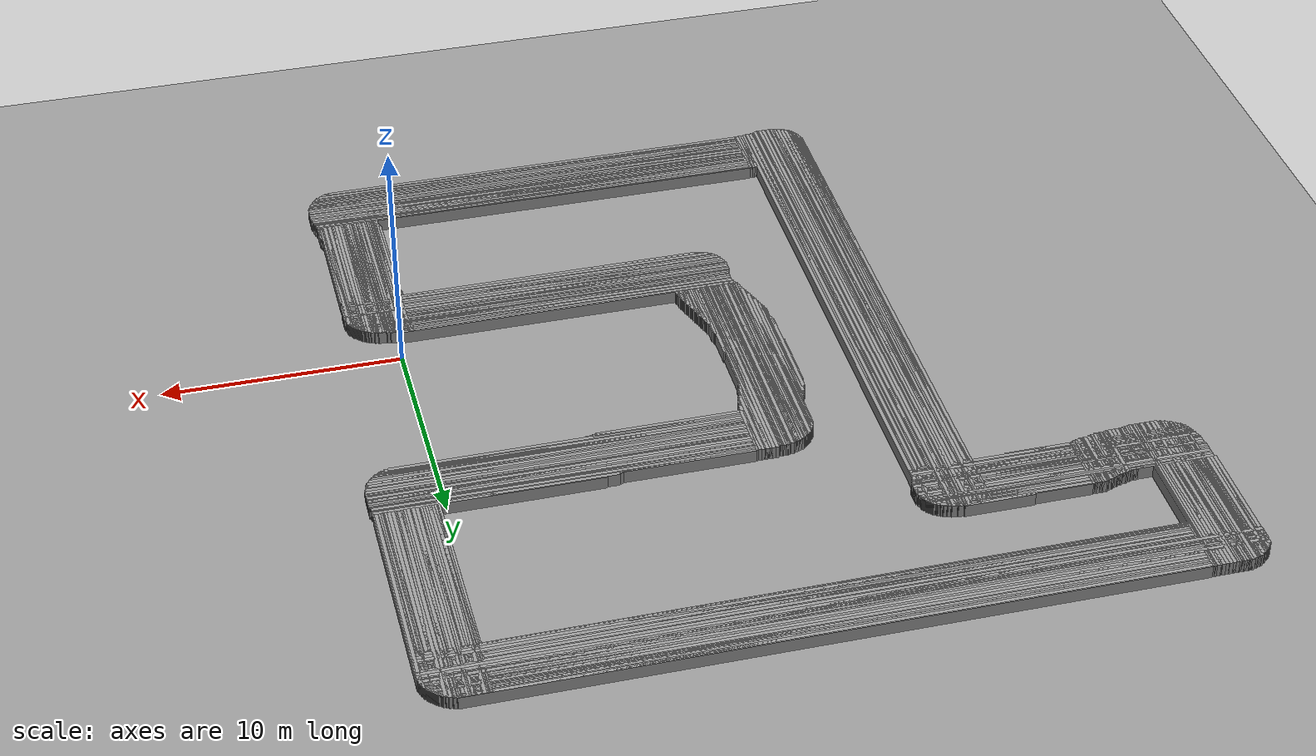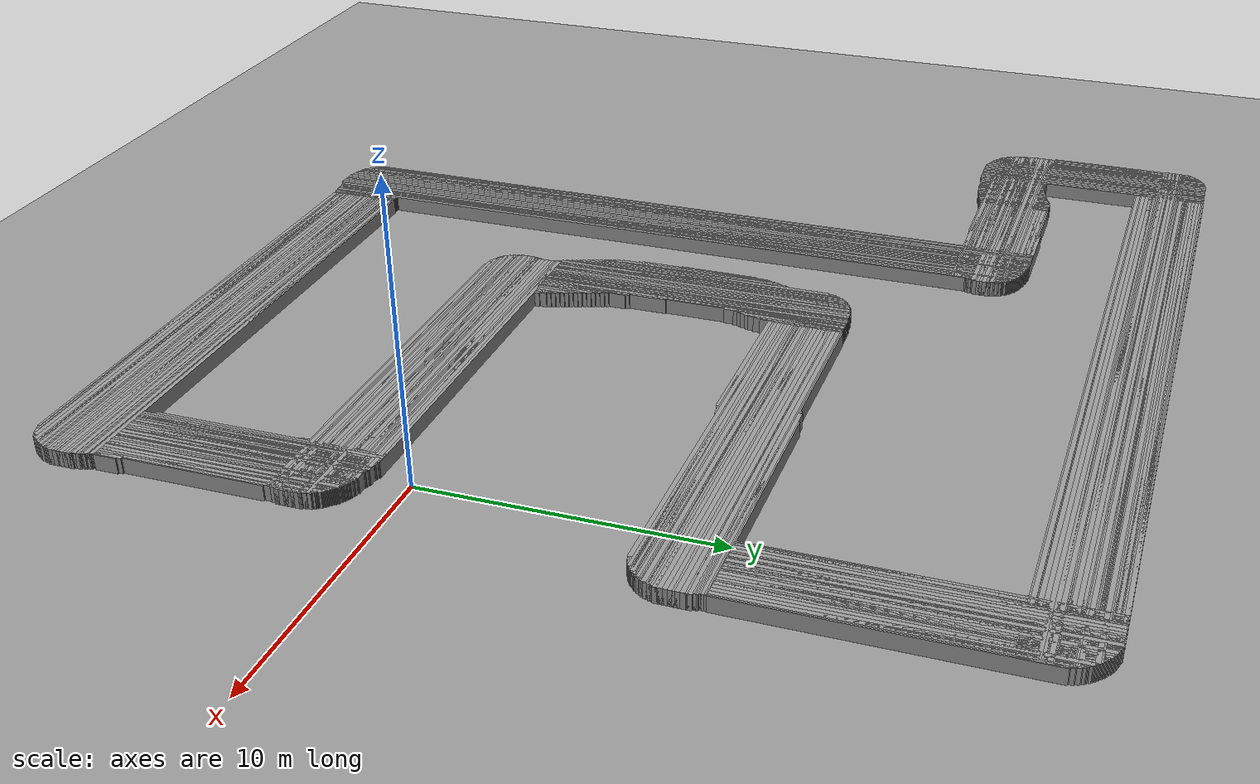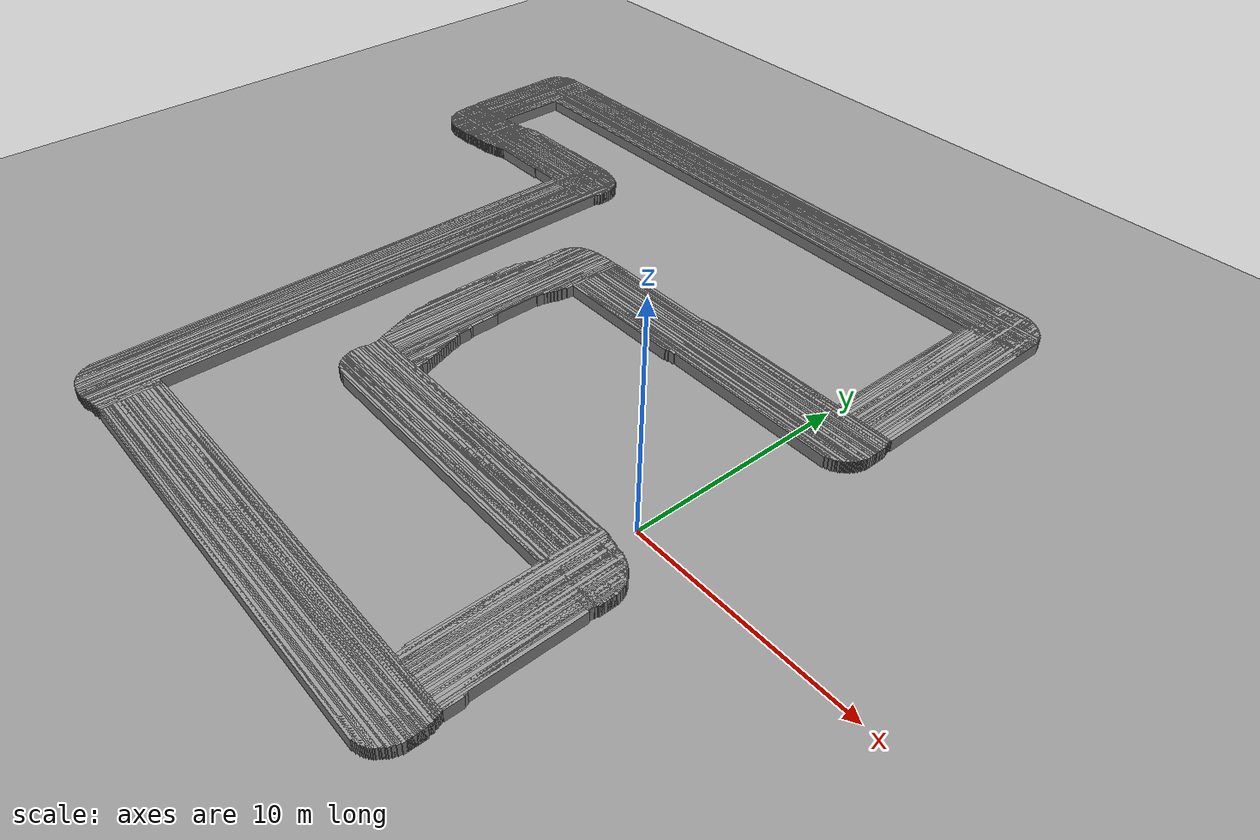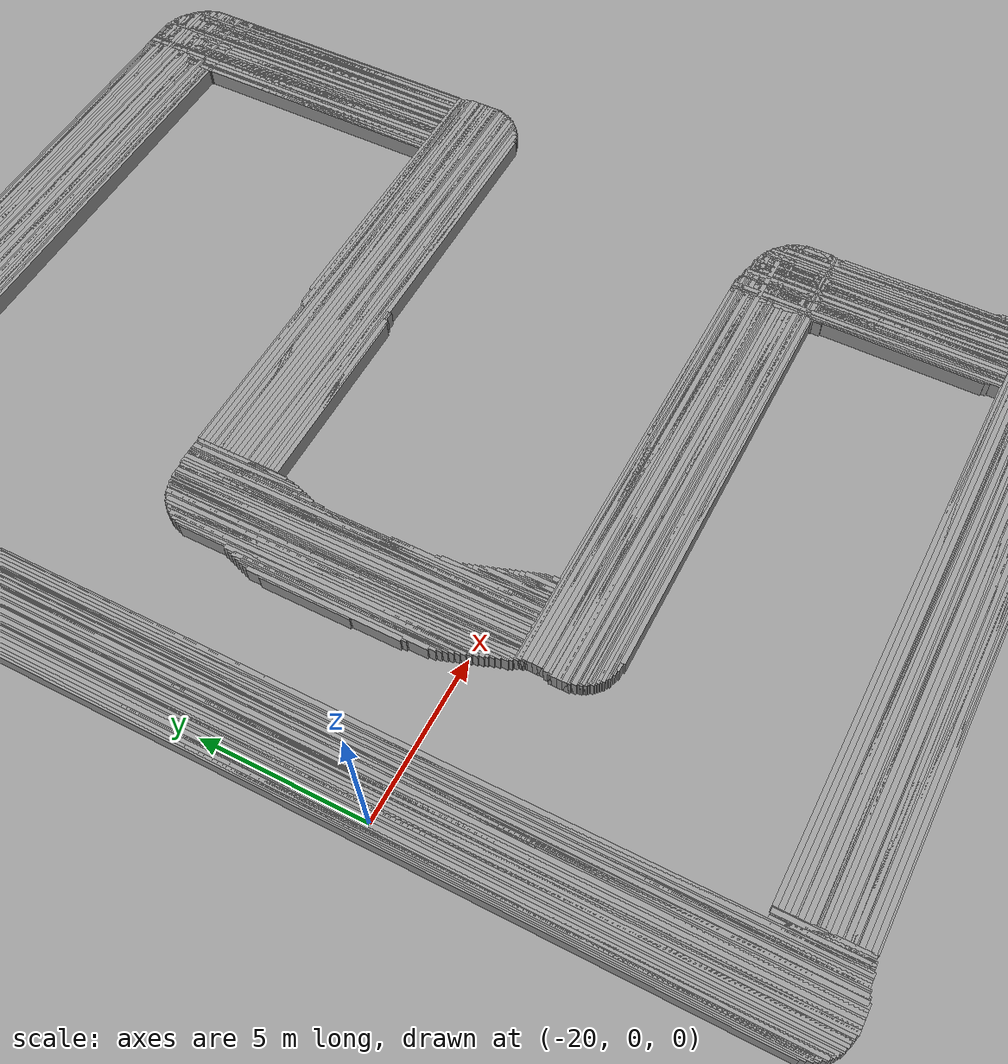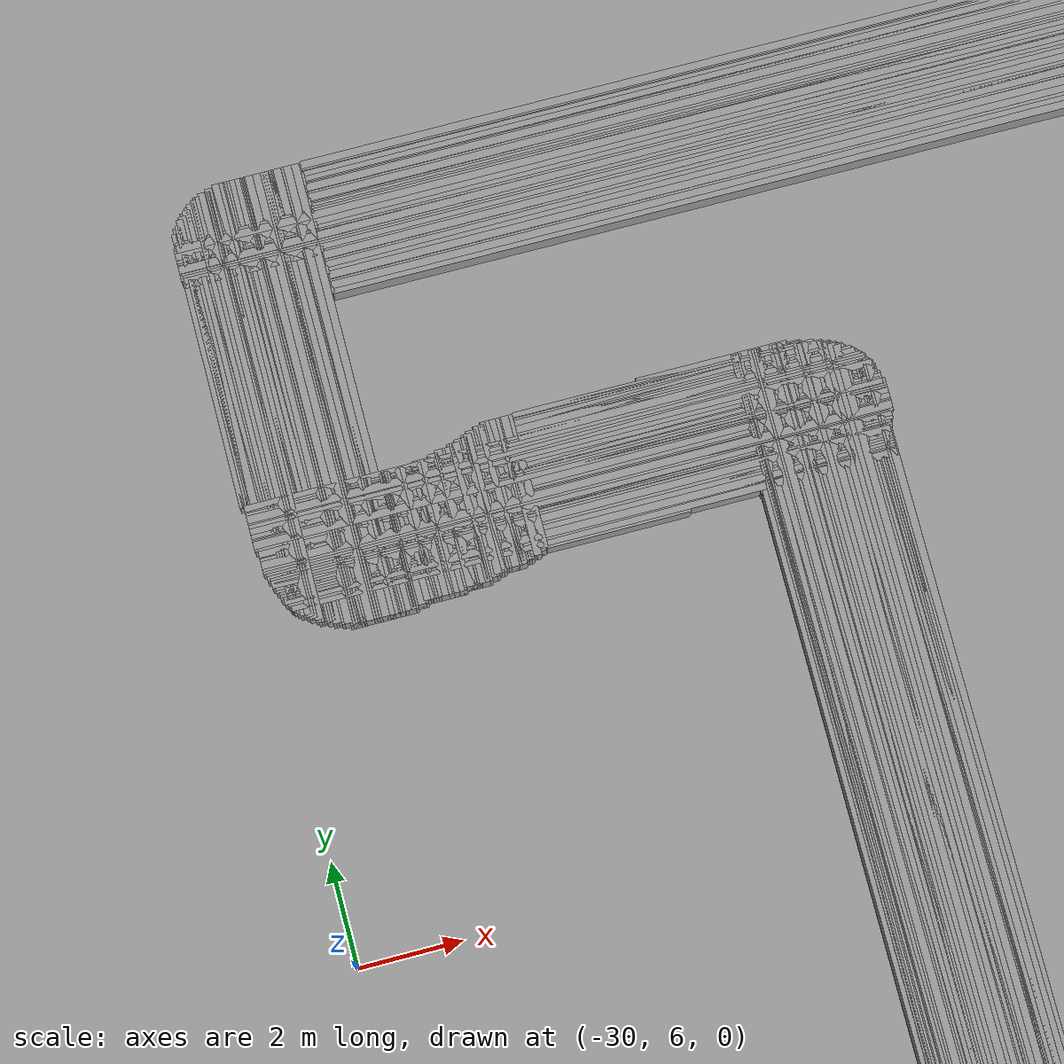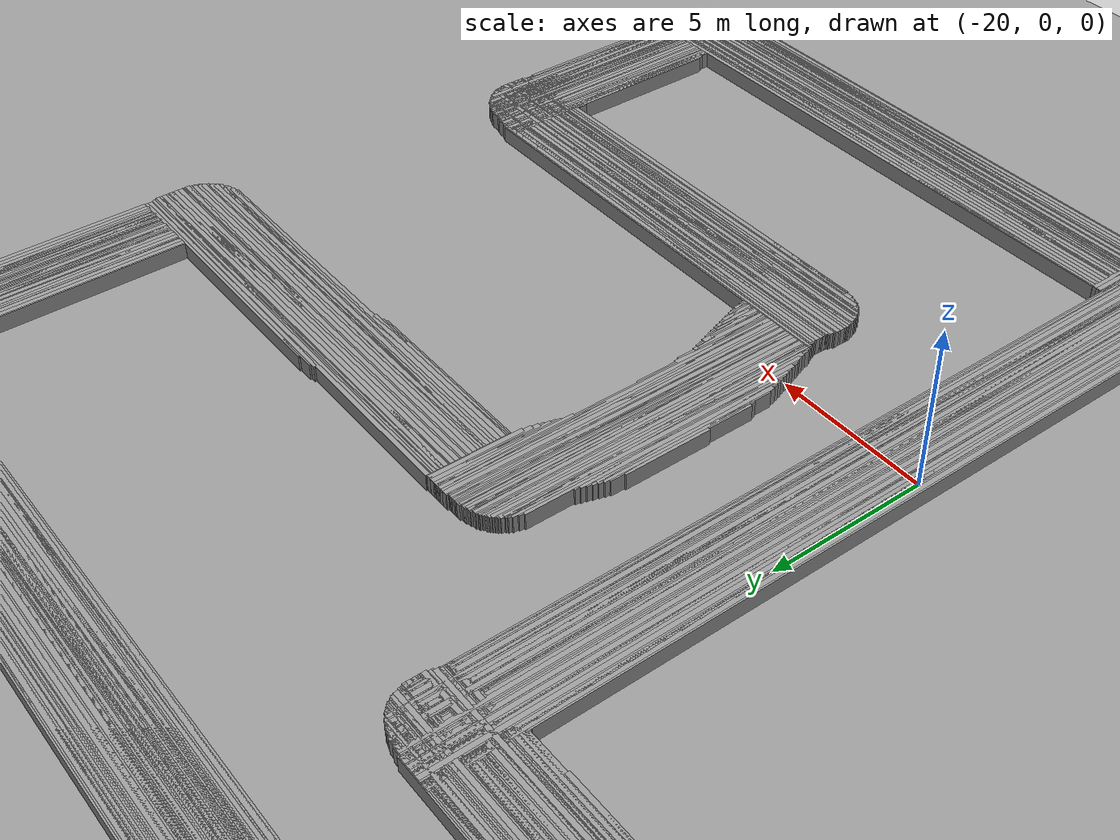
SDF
<sdf version="1.6">
  <world name="default">
    <light name="sun" type="directional">
      <cast_shadows>true</cast_shadows>
      <pose>0 0 10 0.0 -0.5 0</pose>
      <diffuse>0.8 0.8 0.8 1</diffuse>
      <specular>0.2 0.2 0.2 1</specular>
      <attenuation>
        <range>1000</range>
        <constant>0.9</constant>
        <linear>0.01</linear>
        <quadratic>0.001</quadratic>
      </attenuation>
      <direction>-0.5 0.5 -1</direction>
    </light>

    <model name="ground_plane">
      <static>true</static>
      <pose>0 0 0 0 0 0</pose>
      <link name="ground_plane_link">
        <collision name="ground_plane_collision">
          <geometry>
            <plane>
              <normal>0 0 1</normal>
              <size>500 500</size>
            </plane>
          </geometry>
          <surface>
            <friction>
              <ode>
                <mu>1.0</mu>
                <mu2>1.0</mu2>
              </ode>
            </friction>
          </surface>
        </collision>
        <visual name="ground_plane_visual">
          <geometry>
            <plane>
              <normal>0 0 1</normal>
              <size>500 500</size>
            </plane>
          </geometry>
          <material>
            <ambient>0.3 0.3 0.3 1</ambient>
            <diffuse>0.6 0.6 0.6 1</diffuse>
            <specular>0.1 0.1 0.1 1</specular>
          </material>
        </visual>
      </link>
    </model>
    <physics type="ode">
      <real_time_update_rate>1000.0</real_time_update_rate>
      <max_step_size>0.001</max_step_size>
      <real_time_factor>1</real_time_factor>
      <ode>
        <solver>
          <type>quick</type>
          <iters>150</iters>
          <precon_iters>0</precon_iters>
          <sor>1.400000</sor>
          <use_dynamic_moi_rescaling>1</use_dynamic_moi_rescaling>
        </solver>
        <constraints>
          <cfm>0.00001</cfm>
          <erp>0.2</erp>
          <contact_max_correcting_vel>2000.000000</contact_max_correcting_vel>
          <contact_surface_layer>0.01000</contact_surface_layer>
        </constraints>
      </ode>
    </physics>
    <scene>
      <ambient>0.4 0.4 0.4 1</ambient>
      <background>0.7 0.7 0.7 1</background>
      <shadows>true</shadows>
    </scene>
    <gui fullscreen="0">
      <camera name="user_camera">
        <pose>0.0 0.0 17.0 -1.5708 1.5708 0</pose>
        <view_controller>orbit</view_controller>
      </camera>
    </gui>
    <model name="obstacle">
      <static>1</static>
      <pose frame="">0 0 0 0 0 0</pose>
      <link name="obstacle">
        <collision name="obstacle_1">
          <pose>-19.4 1.4000000000000021 0 0 0 1.5708</pose>
          <geometry>
            <box>
              <size>27.6 0.15 1.0</size>
            </box>
          </geometry>
        </collision>
        <visual name="obstacle_1">
          <pose>-19.4 1.4000000000000021 0 0 0 1.5708</pose>
          <geometry>
            <box>
              <size>27.6 0.15 1.0</size>
            </box>
          </geometry>
          <material>
            <script>
              <uri>file://media/materials/scripts/gazebo.material</uri>
              <name>Gazebo/Grey</name>
            </script>
            <ambient>1 1 1 1</ambient>
          </material>
        </visual>
        <collision name="obstacle_2">
          <pose>-19.349999999999998 1.4000000000000021 0 0 0 1.5708</pose>
          <geometry>
            <box>
              <size>27.6 0.15 1.0</size>
            </box>
          </geometry>
        </collision>
        <visual name="obstacle_2">
          <pose>-19.349999999999998 1.4000000000000021 0 0 0 1.5708</pose>
          <geometry>
            <box>
              <size>27.6 0.15 1.0</size>
            </box>
          </geometry>
          <material>
            <script>
              <uri>file://media/materials/scripts/gazebo.material</uri>
              <name>Gazebo/Grey</name>
            </script>
            <ambient>1 1 1 1</ambient>
          </material>
        </visual>
        <collision name="obstacle_3">
          <pose>-19.299999999999997 1.4000000000000021 0 0 0 1.5708</pose>
          <geometry>
            <box>
              <size>27.6 0.15 1.0</size>
            </box>
          </geometry>
        </collision>
        <visual name="obstacle_3">
          <pose>-19.299999999999997 1.4000000000000021 0 0 0 1.5708</pose>
          <geometry>
            <box>
              <size>27.6 0.15 1.0</size>
            </box>
          </geometry>
          <material>
            <script>
              <uri>file://media/materials/scripts/gazebo.material</uri>
              <name>Gazebo/Grey</name>
            </script>
            <ambient>1 1 1 1</ambient>
          </material>
        </visual>
        <collision name="obstacle_4">
          <pose>-19.25 1.4000000000000021 0 0 0 1.5708</pose>
          <geometry>
            <box>
              <size>27.6 0.15 1.0</size>
            </box>
          </geometry>
        </collision>
        <visual name="obstacle_4">
          <pose>-19.25 1.4000000000000021 0 0 0 1.5708</pose>
          <geometry>
            <box>
              <size>27.6 0.15 1.0</size>
            </box>
          </geometry>
          <material>
            <script>
              <uri>file://media/materials/scripts/gazebo.material</uri>
              <name>Gazebo/Grey</name>
            </script>
            <ambient>1 1 1 1</ambient>
          </material>
        </visual>
        <collision name="obstacle_5">
          <pose>-19.2 1.4000000000000021 0 0 0 1.5708</pose>
          <geometry>
            <box>
              <size>27.6 0.15 1.0</size>
            </box>
          </geometry>
        </collision>
        <visual name="obstacle_5">
          <pose>-19.2 1.4000000000000021 0 0 0 1.5708</pose>
          <geometry>
            <box>
              <size>27.6 0.15 1.0</size>
            </box>
          </geometry>
          <material>
            <script>
              <uri>file://media/materials/scripts/gazebo.material</uri>
              <name>Gazebo/Grey</name>
            </script>
            <ambient>1 1 1 1</ambient>
          </material>
        </visual>
        <collision name="obstacle_6">
          <pose>-19.15 1.375 0 0 0 1.5708</pose>
          <geometry>
            <box>
              <size>27.55 0.15 1.0</size>
            </box>
          </geometry>
        </collision>
        <visual name="obstacle_6">
          <pose>-19.15 1.375 0 0 0 1.5708</pose>
          <geometry>
            <box>
              <size>27.55 0.15 1.0</size>
            </box>
          </geometry>
          <material>
            <script>
              <uri>file://media/materials/scripts/gazebo.material</uri>
              <name>Gazebo/Grey</name>
            </script>
            <ambient>1 1 1 1</ambient>
          </material>
        </visual>
        <collision name="obstacle_7">
          <pose>-19.099999999999998 1.375 0 0 0 1.5708</pose>
          <geometry>
            <box>
              <size>27.55 0.15 1.0</size>
            </box>
          </geometry>
        </collision>
        <visual name="obstacle_7">
          <pose>-19.099999999999998 1.375 0 0 0 1.5708</pose>
          <geometry>
            <box>
              <size>27.55 0.15 1.0</size>
            </box>
          </geometry>
          <material>
            <script>
              <uri>file://media/materials/scripts/gazebo.material</uri>
              <name>Gazebo/Grey</name>
            </script>
            <ambient>1 1 1 1</ambient>
          </material>
        </visual>
        <collision name="obstacle_8">
          <pose>-19.049999999999997 1.375 0 0 0 1.5708</pose>
          <geometry>
            <box>
              <size>27.55 0.15 1.0</size>
            </box>
          </geometry>
        </collision>
        <visual name="obstacle_8">
          <pose>-19.049999999999997 1.375 0 0 0 1.5708</pose>
          <geometry>
            <box>
              <size>27.55 0.15 1.0</size>
            </box>
          </geometry>
          <material>
            <script>
              <uri>file://media/materials/scripts/gazebo.material</uri>
              <name>Gazebo/Grey</name>
            </script>
            <ambient>1 1 1 1</ambient>
          </material>
        </visual>
        <collision name="obstacle_9">
          <pose>-19.0 1.375 0 0 0 1.5708</pose>
          <geometry>
            <box>
              <size>27.55 0.15 1.0</size>
            </box>
          </geometry>
        </collision>
        <visual name="obstacle_9">
          <pose>-19.0 1.375 0 0 0 1.5708</pose>
          <geometry>
            <box>
              <size>27.55 0.15 1.0</size>
            </box>
          </geometry>
          <material>
            <script>
              <uri>file://media/materials/scripts/gazebo.material</uri>
              <name>Gazebo/Grey</name>
            </script>
            <ambient>1 1 1 1</ambient>
          </material>
        </visual>
        <collision name="obstacle_10">
          <pose>-18.95 1.375 0 0 0 1.5708</pose>
          <geometry>
            <box>
              <size>27.55 0.15 1.0</size>
            </box>
          </geometry>
        </collision>
        <visual name="obstacle_10">
          <pose>-18.95 1.375 0 0 0 1.5708</pose>
          <geometry>
            <box>
              <size>27.55 0.15 1.0</size>
            </box>
          </geometry>
          <material>
            <script>
              <uri>file://media/materials/scripts/gazebo.material</uri>
              <name>Gazebo/Grey</name>
            </script>
            <ambient>1 1 1 1</ambient>
          </material>
        </visual>
        <collision name="obstacle_11">
          <pose>-18.9 1.3500000000000014 0 0 0 1.5708</pose>
          <geometry>
            <box>
              <size>27.5 0.15 1.0</size>
            </box>
          </geometry>
        </collision>
        <visual name="obstacle_11">
          <pose>-18.9 1.3500000000000014 0 0 0 1.5708</pose>
          <geometry>
            <box>
              <size>27.5 0.15 1.0</size>
            </box>
          </geometry>
          <material>
            <script>
              <uri>file://media/materials/scripts/gazebo.material</uri>
              <name>Gazebo/Grey</name>
            </script>
            <ambient>1 1 1 1</ambient>
          </material>
        </visual>
        <collision name="obstacle_12">
          <pose>-18.849999999999998 1.3500000000000014 0 0 0 1.5708</pose>
          <geometry>
            <box>
              <size>27.5 0.15 1.0</size>
            </box>
          </geometry>
        </collision>
        <visual name="obstacle_12">
          <pose>-18.849999999999998 1.3500000000000014 0 0 0 1.5708</pose>
          <geometry>
            <box>
              <size>27.5 0.15 1.0</size>
            </box>
          </geometry>
          <material>
            <script>
              <uri>file://media/materials/scripts/gazebo.material</uri>
              <name>Gazebo/Grey</name>
            </script>
            <ambient>1 1 1 1</ambient>
          </material>
        </visual>
        <collision name="obstacle_13">
          <pose>-18.799999999999997 1.3500000000000014 0 0 0 1.5708</pose>
          <geometry>
            <box>
              <size>27.5 0.15 1.0</size>
            </box>
          </geometry>
        </collision>
        <visual name="obstacle_13">
          <pose>-18.799999999999997 1.3500000000000014 0 0 0 1.5708</pose>
          <geometry>
            <box>
              <size>27.5 0.15 1.0</size>
            </box>
          </geometry>
          <material>
            <script>
              <uri>file://media/materials/scripts/gazebo.material</uri>
              <name>Gazebo/Grey</name>
            </script>
            <ambient>1 1 1 1</ambient>
          </material>
        </visual>
        <collision name="obstacle_14">
          <pose>-18.75 1.3250000000000028 0 0 0 1.5708</pose>
          <geometry>
            <box>
              <size>27.450000000000003 0.15 1.0</size>
            </box>
          </geometry>
        </collision>
        <visual name="obstacle_14">
          <pose>-18.75 1.3250000000000028 0 0 0 1.5708</pose>
          <geometry>
            <box>
              <size>27.450000000000003 0.15 1.0</size>
            </box>
          </geometry>
          <material>
            <script>
              <uri>file://media/materials/scripts/gazebo.material</uri>
              <name>Gazebo/Grey</name>
            </script>
            <ambient>1 1 1 1</ambient>
          </material>
        </visual>
        <collision name="obstacle_15">
          <pose>-19.599999999999998 1.4500000000000028 0 0 0 1.5708</pose>
          <geometry>
            <box>
              <size>27.6 0.15 1.0</size>
            </box>
          </geometry>
        </collision>
        <visual name="obstacle_15">
          <pose>-19.599999999999998 1.4500000000000028 0 0 0 1.5708</pose>
          <geometry>
            <box>
              <size>27.6 0.15 1.0</size>
            </box>
          </geometry>
          <material>
            <script>
              <uri>file://media/materials/scripts/gazebo.material</uri>
              <name>Gazebo/Grey</name>
            </script>
            <ambient>1 1 1 1</ambient>
          </material>
        </visual>
        <collision name="obstacle_16">
          <pose>-19.549999999999997 1.4500000000000028 0 0 0 1.5708</pose>
          <geometry>
            <box>
              <size>27.6 0.15 1.0</size>
            </box>
          </geometry>
        </collision>
        <visual name="obstacle_16">
          <pose>-19.549999999999997 1.4500000000000028 0 0 0 1.5708</pose>
          <geometry>
            <box>
              <size>27.6 0.15 1.0</size>
            </box>
          </geometry>
          <material>
            <script>
              <uri>file://media/materials/scripts/gazebo.material</uri>
              <name>Gazebo/Grey</name>
            </script>
            <ambient>1 1 1 1</ambient>
          </material>
        </visual>
        <collision name="obstacle_17">
          <pose>-19.5 1.4500000000000028 0 0 0 1.5708</pose>
          <geometry>
            <box>
              <size>27.6 0.15 1.0</size>
            </box>
          </geometry>
        </collision>
        <visual name="obstacle_17">
          <pose>-19.5 1.4500000000000028 0 0 0 1.5708</pose>
          <geometry>
            <box>
              <size>27.6 0.15 1.0</size>
            </box>
          </geometry>
          <material>
            <script>
              <uri>file://media/materials/scripts/gazebo.material</uri>
              <name>Gazebo/Grey</name>
            </script>
            <ambient>1 1 1 1</ambient>
          </material>
        </visual>
        <collision name="obstacle_18">
          <pose>-19.45 1.4500000000000028 0 0 0 1.5708</pose>
          <geometry>
            <box>
              <size>27.6 0.15 1.0</size>
            </box>
          </geometry>
        </collision>
        <visual name="obstacle_18">
          <pose>-19.45 1.4500000000000028 0 0 0 1.5708</pose>
          <geometry>
            <box>
              <size>27.6 0.15 1.0</size>
            </box>
          </geometry>
          <material>
            <script>
              <uri>file://media/materials/scripts/gazebo.material</uri>
              <name>Gazebo/Grey</name>
            </script>
            <ambient>1 1 1 1</ambient>
          </material>
        </visual>
        <collision name="obstacle_19">
          <pose>-18.7 1.3500000000000014 0 0 0 1.5708</pose>
          <geometry>
            <box>
              <size>27.400000000000002 0.15 1.0</size>
            </box>
          </geometry>
        </collision>
        <visual name="obstacle_19">
          <pose>-18.7 1.3500000000000014 0 0 0 1.5708</pose>
          <geometry>
            <box>
              <size>27.400000000000002 0.15 1.0</size>
            </box>
          </geometry>
          <material>
            <script>
              <uri>file://media/materials/scripts/gazebo.material</uri>
              <name>Gazebo/Grey</name>
            </script>
            <ambient>1 1 1 1</ambient>
          </material>
        </visual>
        <collision name="obstacle_20">
          <pose>-18.65 1.3500000000000014 0 0 0 1.5708</pose>
          <geometry>
            <box>
              <size>27.400000000000002 0.15 1.0</size>
            </box>
          </geometry>
        </collision>
        <visual name="obstacle_20">
          <pose>-18.65 1.3500000000000014 0 0 0 1.5708</pose>
          <geometry>
            <box>
              <size>27.400000000000002 0.15 1.0</size>
            </box>
          </geometry>
          <material>
            <script>
              <uri>file://media/materials/scripts/gazebo.material</uri>
              <name>Gazebo/Grey</name>
            </script>
            <ambient>1 1 1 1</ambient>
          </material>
        </visual>
        <collision name="obstacle_21">
          <pose>-18.599999999999998 1.3250000000000028 0 0 0 1.5708</pose>
          <geometry>
            <box>
              <size>27.35 0.15 1.0</size>
            </box>
          </geometry>
        </collision>
        <visual name="obstacle_21">
          <pose>-18.599999999999998 1.3250000000000028 0 0 0 1.5708</pose>
          <geometry>
            <box>
              <size>27.35 0.15 1.0</size>
            </box>
          </geometry>
          <material>
            <script>
              <uri>file://media/materials/scripts/gazebo.material</uri>
              <name>Gazebo/Grey</name>
            </script>
            <ambient>1 1 1 1</ambient>
          </material>
        </visual>
        <collision name="obstacle_22">
          <pose>-19.75 1.4750000000000014 0 0 0 1.5708</pose>
          <geometry>
            <box>
              <size>27.55 0.15 1.0</size>
            </box>
          </geometry>
        </collision>
        <visual name="obstacle_22">
          <pose>-19.75 1.4750000000000014 0 0 0 1.5708</pose>
          <geometry>
            <box>
              <size>27.55 0.15 1.0</size>
            </box>
          </geometry>
          <material>
            <script>
              <uri>file://media/materials/scripts/gazebo.material</uri>
              <name>Gazebo/Grey</name>
            </script>
            <ambient>1 1 1 1</ambient>
          </material>
        </visual>
        <collision name="obstacle_23">
          <pose>-19.7 1.4750000000000014 0 0 0 1.5708</pose>
          <geometry>
            <box>
              <size>27.55 0.15 1.0</size>
            </box>
          </geometry>
        </collision>
        <visual name="obstacle_23">
          <pose>-19.7 1.4750000000000014 0 0 0 1.5708</pose>
          <geometry>
            <box>
              <size>27.55 0.15 1.0</size>
            </box>
          </geometry>
          <material>
            <script>
              <uri>file://media/materials/scripts/gazebo.material</uri>
              <name>Gazebo/Grey</name>
            </script>
            <ambient>1 1 1 1</ambient>
          </material>
        </visual>
        <collision name="obstacle_24">
          <pose>-19.65 1.4750000000000014 0 0 0 1.5708</pose>
          <geometry>
            <box>
              <size>27.55 0.15 1.0</size>
            </box>
          </geometry>
        </collision>
        <visual name="obstacle_24">
          <pose>-19.65 1.4750000000000014 0 0 0 1.5708</pose>
          <geometry>
            <box>
              <size>27.55 0.15 1.0</size>
            </box>
          </geometry>
          <material>
            <script>
              <uri>file://media/materials/scripts/gazebo.material</uri>
              <name>Gazebo/Grey</name>
            </script>
            <ambient>1 1 1 1</ambient>
          </material>
        </visual>
        <collision name="obstacle_25">
          <pose>-18.549999999999997 1.3500000000000014 0 0 0 1.5708</pose>
          <geometry>
            <box>
              <size>27.3 0.15 1.0</size>
            </box>
          </geometry>
        </collision>
        <visual name="obstacle_25">
          <pose>-18.549999999999997 1.3500000000000014 0 0 0 1.5708</pose>
          <geometry>
            <box>
              <size>27.3 0.15 1.0</size>
            </box>
          </geometry>
          <material>
            <script>
              <uri>file://media/materials/scripts/gazebo.material</uri>
              <name>Gazebo/Grey</name>
            </script>
            <ambient>1 1 1 1</ambient>
          </material>
        </visual>
        <collision name="obstacle_26">
          <pose>-18.5 1.3250000000000028 0 0 0 1.5708</pose>
          <geometry>
            <box>
              <size>27.25 0.15 1.0</size>
            </box>
          </geometry>
        </collision>
        <visual name="obstacle_26">
          <pose>-18.5 1.3250000000000028 0 0 0 1.5708</pose>
          <geometry>
            <box>
              <size>27.25 0.15 1.0</size>
            </box>
          </geometry>
          <material>
            <script>
              <uri>file://media/materials/scripts/gazebo.material</uri>
              <name>Gazebo/Grey</name>
            </script>
            <ambient>1 1 1 1</ambient>
          </material>
        </visual>
        <collision name="obstacle_27">
          <pose>-18.45 1.3250000000000028 0 0 0 1.5708</pose>
          <geometry>
            <box>
              <size>27.25 0.15 1.0</size>
            </box>
          </geometry>
        </collision>
        <visual name="obstacle_27">
          <pose>-18.45 1.3250000000000028 0 0 0 1.5708</pose>
          <geometry>
            <box>
              <size>27.25 0.15 1.0</size>
            </box>
          </geometry>
          <material>
            <script>
              <uri>file://media/materials/scripts/gazebo.material</uri>
              <name>Gazebo/Grey</name>
            </script>
            <ambient>1 1 1 1</ambient>
          </material>
        </visual>
        <collision name="obstacle_28">
          <pose>-19.9 1.5 0 0 0 1.5708</pose>
          <geometry>
            <box>
              <size>27.5 0.15 1.0</size>
            </box>
          </geometry>
        </collision>
        <visual name="obstacle_28">
          <pose>-19.9 1.5 0 0 0 1.5708</pose>
          <geometry>
            <box>
              <size>27.5 0.15 1.0</size>
            </box>
          </geometry>
          <material>
            <script>
              <uri>file://media/materials/scripts/gazebo.material</uri>
              <name>Gazebo/Grey</name>
            </script>
            <ambient>1 1 1 1</ambient>
          </material>
        </visual>
        <collision name="obstacle_29">
          <pose>-19.849999999999998 1.5 0 0 0 1.5708</pose>
          <geometry>
            <box>
              <size>27.5 0.15 1.0</size>
            </box>
          </geometry>
        </collision>
        <visual name="obstacle_29">
          <pose>-19.849999999999998 1.5 0 0 0 1.5708</pose>
          <geometry>
            <box>
              <size>27.5 0.15 1.0</size>
            </box>
          </geometry>
          <material>
            <script>
              <uri>file://media/materials/scripts/gazebo.material</uri>
              <name>Gazebo/Grey</name>
            </script>
            <ambient>1 1 1 1</ambient>
          </material>
        </visual>
        <collision name="obstacle_30">
          <pose>-19.799999999999997 1.5 0 0 0 1.5708</pose>
          <geometry>
            <box>
              <size>27.5 0.15 1.0</size>
            </box>
          </geometry>
        </collision>
        <visual name="obstacle_30">
          <pose>-19.799999999999997 1.5 0 0 0 1.5708</pose>
          <geometry>
            <box>
              <size>27.5 0.15 1.0</size>
            </box>
          </geometry>
          <material>
            <script>
              <uri>file://media/materials/scripts/gazebo.material</uri>
              <name>Gazebo/Grey</name>
            </script>
            <ambient>1 1 1 1</ambient>
          </material>
        </visual>
        <collision name="obstacle_31">
          <pose>-18.4 1.3250000000000028 0 0 0 1.5708</pose>
          <geometry>
            <box>
              <size>27.150000000000002 0.15 1.0</size>
            </box>
          </geometry>
        </collision>
        <visual name="obstacle_31">
          <pose>-18.4 1.3250000000000028 0 0 0 1.5708</pose>
          <geometry>
            <box>
              <size>27.150000000000002 0.15 1.0</size>
            </box>
          </geometry>
          <material>
            <script>
              <uri>file://media/materials/scripts/gazebo.material</uri>
              <name>Gazebo/Grey</name>
            </script>
            <ambient>1 1 1 1</ambient>
          </material>
        </visual>
        <collision name="obstacle_32">
          <pose>-18.349999999999998 1.3000000000000007 0 0 0 1.5708</pose>
          <geometry>
            <box>
              <size>27.1 0.15 1.0</size>
            </box>
          </geometry>
        </collision>
        <visual name="obstacle_32">
          <pose>-18.349999999999998 1.3000000000000007 0 0 0 1.5708</pose>
          <geometry>
            <box>
              <size>27.1 0.15 1.0</size>
            </box>
          </geometry>
          <material>
            <script>
              <uri>file://media/materials/scripts/gazebo.material</uri>
              <name>Gazebo/Grey</name>
            </script>
            <ambient>1 1 1 1</ambient>
          </material>
        </visual>
        <collision name="obstacle_33">
          <pose>-18.299999999999997 1.3000000000000007 0 0 0 1.5708</pose>
          <geometry>
            <box>
              <size>27.1 0.15 1.0</size>
            </box>
          </geometry>
        </collision>
        <visual name="obstacle_33">
          <pose>-18.299999999999997 1.3000000000000007 0 0 0 1.5708</pose>
          <geometry>
            <box>
              <size>27.1 0.15 1.0</size>
            </box>
          </geometry>
          <material>
            <script>
              <uri>file://media/materials/scripts/gazebo.material</uri>
              <name>Gazebo/Grey</name>
            </script>
            <ambient>1 1 1 1</ambient>
          </material>
        </visual>
        <collision name="obstacle_34">
          <pose>-18.25 1.2750000000000021 0 0 0 1.5708</pose>
          <geometry>
            <box>
              <size>27.05 0.15 1.0</size>
            </box>
          </geometry>
        </collision>
        <visual name="obstacle_34">
          <pose>-18.25 1.2750000000000021 0 0 0 1.5708</pose>
          <geometry>
            <box>
              <size>27.05 0.15 1.0</size>
            </box>
          </geometry>
          <material>
            <script>
              <uri>file://media/materials/scripts/gazebo.material</uri>
              <name>Gazebo/Grey</name>
            </script>
            <ambient>1 1 1 1</ambient>
          </material>
        </visual>
        <collision name="obstacle_35">
          <pose>-18.2 1.25 0 0 0 1.5708</pose>
          <geometry>
            <box>
              <size>27.0 0.15 1.0</size>
            </box>
          </geometry>
        </collision>
        <visual name="obstacle_35">
          <pose>-18.2 1.25 0 0 0 1.5708</pose>
          <geometry>
            <box>
              <size>27.0 0.15 1.0</size>
            </box>
          </geometry>
          <material>
            <script>
              <uri>file://media/materials/scripts/gazebo.material</uri>
              <name>Gazebo/Grey</name>
            </script>
            <ambient>1 1 1 1</ambient>
          </material>
        </visual>
        <collision name="obstacle_36">
          <pose>-18.15 1.2250000000000014 0 0 0 1.5708</pose>
          <geometry>
            <box>
              <size>26.950000000000003 0.15 1.0</size>
            </box>
          </geometry>
        </collision>
        <visual name="obstacle_36">
          <pose>-18.15 1.2250000000000014 0 0 0 1.5708</pose>
          <geometry>
            <box>
              <size>26.950000000000003 0.15 1.0</size>
            </box>
          </geometry>
          <material>
            <script>
              <uri>file://media/materials/scripts/gazebo.material</uri>
              <name>Gazebo/Grey</name>
            </script>
            <ambient>1 1 1 1</ambient>
          </material>
        </visual>
        <collision name="obstacle_37">
          <pose>-18.099999999999998 1.2000000000000028 0 0 0 1.5708</pose>
          <geometry>
            <box>
              <size>26.900000000000002 0.15 1.0</size>
            </box>
          </geometry>
        </collision>
        <visual name="obstacle_37">
          <pose>-18.099999999999998 1.2000000000000028 0 0 0 1.5708</pose>
          <geometry>
            <box>
              <size>26.900000000000002 0.15 1.0</size>
            </box>
          </geometry>
          <material>
            <script>
              <uri>file://media/materials/scripts/gazebo.material</uri>
              <name>Gazebo/Grey</name>
            </script>
            <ambient>1 1 1 1</ambient>
          </material>
        </visual>
        <collision name="obstacle_38">
          <pose>-18.049999999999997 1.1500000000000021 0 0 0 1.5708</pose>
          <geometry>
            <box>
              <size>26.8 0.15 1.0</size>
            </box>
          </geometry>
        </collision>
        <visual name="obstacle_38">
          <pose>-18.049999999999997 1.1500000000000021 0 0 0 1.5708</pose>
          <geometry>
            <box>
              <size>26.8 0.15 1.0</size>
            </box>
          </geometry>
          <material>
            <script>
              <uri>file://media/materials/scripts/gazebo.material</uri>
              <name>Gazebo/Grey</name>
            </script>
            <ambient>1 1 1 1</ambient>
          </material>
        </visual>
        <collision name="obstacle_39">
          <pose>-19.95 1.5250000000000021 0 0 0 1.5708</pose>
          <geometry>
            <box>
              <size>27.450000000000003 0.15 1.0</size>
            </box>
          </geometry>
        </collision>
        <visual name="obstacle_39">
          <pose>-19.95 1.5250000000000021 0 0 0 1.5708</pose>
          <geometry>
            <box>
              <size>27.450000000000003 0.15 1.0</size>
            </box>
          </geometry>
          <material>
            <script>
              <uri>file://media/materials/scripts/gazebo.material</uri>
              <name>Gazebo/Grey</name>
            </script>
            <ambient>1 1 1 1</ambient>
          </material>
        </visual>
        <collision name="obstacle_40">
          <pose>-18.0 1.1500000000000021 0 0 0 1.5708</pose>
          <geometry>
            <box>
              <size>26.700000000000003 0.15 1.0</size>
            </box>
          </geometry>
        </collision>
        <visual name="obstacle_40">
          <pose>-18.0 1.1500000000000021 0 0 0 1.5708</pose>
          <geometry>
            <box>
              <size>26.700000000000003 0.15 1.0</size>
            </box>
          </geometry>
          <material>
            <script>
              <uri>file://media/materials/scripts/gazebo.material</uri>
              <name>Gazebo/Grey</name>
            </script>
            <ambient>1 1 1 1</ambient>
          </material>
        </visual>
        <collision name="obstacle_41">
          <pose>-17.95 -10.875 0 0 0 1.5708</pose>
          <geometry>
            <box>
              <size>2.6500000000000004 0.15 1.0</size>
            </box>
          </geometry>
        </collision>
        <visual name="obstacle_41">
          <pose>-17.95 -10.875 0 0 0 1.5708</pose>
          <geometry>
            <box>
              <size>2.6500000000000004 0.15 1.0</size>
            </box>
          </geometry>
          <material>
            <script>
              <uri>file://media/materials/scripts/gazebo.material</uri>
              <name>Gazebo/Grey</name>
            </script>
            <ambient>1 1 1 1</ambient>
          </material>
        </visual>
        <collision name="obstacle_42">
          <pose>-17.9 -10.875 0 0 0 1.5708</pose>
          <geometry>
            <box>
              <size>2.6500000000000004 0.15 1.0</size>
            </box>
          </geometry>
        </collision>
        <visual name="obstacle_42">
          <pose>-17.9 -10.875 0 0 0 1.5708</pose>
          <geometry>
            <box>
              <size>2.6500000000000004 0.15 1.0</size>
            </box>
          </geometry>
          <material>
            <script>
              <uri>file://media/materials/scripts/gazebo.material</uri>
              <name>Gazebo/Grey</name>
            </script>
            <ambient>1 1 1 1</ambient>
          </material>
        </visual>
        <collision name="obstacle_43">
          <pose>-17.849999999999998 -10.875 0 0 0 1.5708</pose>
          <geometry>
            <box>
              <size>2.6500000000000004 0.15 1.0</size>
            </box>
          </geometry>
        </collision>
        <visual name="obstacle_43">
          <pose>-17.849999999999998 -10.875 0 0 0 1.5708</pose>
          <geometry>
            <box>
              <size>2.6500000000000004 0.15 1.0</size>
            </box>
          </geometry>
          <material>
            <script>
              <uri>file://media/materials/scripts/gazebo.material</uri>
              <name>Gazebo/Grey</name>
            </script>
            <ambient>1 1 1 1</ambient>
          </material>
        </visual>
        <collision name="obstacle_44">
          <pose>-17.799999999999997 -10.875 0 0 0 1.5708</pose>
          <geometry>
            <box>
              <size>2.6500000000000004 0.15 1.0</size>
            </box>
          </geometry>
        </collision>
        <visual name="obstacle_44">
          <pose>-17.799999999999997 -10.875 0 0 0 1.5708</pose>
          <geometry>
            <box>
              <size>2.6500000000000004 0.15 1.0</size>
            </box>
          </geometry>
          <material>
            <script>
              <uri>file://media/materials/scripts/gazebo.material</uri>
              <name>Gazebo/Grey</name>
            </script>
            <ambient>1 1 1 1</ambient>
          </material>
        </visual>
        <collision name="obstacle_45">
          <pose>-20.049999999999997 1.5500000000000007 0 0 0 1.5708</pose>
          <geometry>
            <box>
              <size>27.400000000000002 0.15 1.0</size>
            </box>
          </geometry>
        </collision>
        <visual name="obstacle_45">
          <pose>-20.049999999999997 1.5500000000000007 0 0 0 1.5708</pose>
          <geometry>
            <box>
              <size>27.400000000000002 0.15 1.0</size>
            </box>
          </geometry>
          <material>
            <script>
              <uri>file://media/materials/scripts/gazebo.material</uri>
              <name>Gazebo/Grey</name>
            </script>
            <ambient>1 1 1 1</ambient>
          </material>
        </visual>
        <collision name="obstacle_46">
          <pose>-20.0 1.5500000000000007 0 0 0 1.5708</pose>
          <geometry>
            <box>
              <size>27.400000000000002 0.15 1.0</size>
            </box>
          </geometry>
        </collision>
        <visual name="obstacle_46">
          <pose>-20.0 1.5500000000000007 0 0 0 1.5708</pose>
          <geometry>
            <box>
              <size>27.400000000000002 0.15 1.0</size>
            </box>
          </geometry>
          <material>
            <script>
              <uri>file://media/materials/scripts/gazebo.material</uri>
              <name>Gazebo/Grey</name>
            </script>
            <ambient>1 1 1 1</ambient>
          </material>
        </visual>
        <collision name="obstacle_47">
          <pose>-17.75 -10.849999999999998 0 0 0 1.5708</pose>
          <geometry>
            <box>
              <size>2.6 0.15 1.0</size>
            </box>
          </geometry>
        </collision>
        <visual name="obstacle_47">
          <pose>-17.75 -10.849999999999998 0 0 0 1.5708</pose>
          <geometry>
            <box>
              <size>2.6 0.15 1.0</size>
            </box>
          </geometry>
          <material>
            <script>
              <uri>file://media/materials/scripts/gazebo.material</uri>
              <name>Gazebo/Grey</name>
            </script>
            <ambient>1 1 1 1</ambient>
          </material>
        </visual>
        <collision name="obstacle_48">
          <pose>-17.7 -10.849999999999998 0 0 0 1.5708</pose>
          <geometry>
            <box>
              <size>2.6 0.15 1.0</size>
            </box>
          </geometry>
        </collision>
        <visual name="obstacle_48">
          <pose>-17.7 -10.849999999999998 0 0 0 1.5708</pose>
          <geometry>
            <box>
              <size>2.6 0.15 1.0</size>
            </box>
          </geometry>
          <material>
            <script>
              <uri>file://media/materials/scripts/gazebo.material</uri>
              <name>Gazebo/Grey</name>
            </script>
            <ambient>1 1 1 1</ambient>
          </material>
        </visual>
        <collision name="obstacle_49">
          <pose>-17.65 -10.849999999999998 0 0 0 1.5708</pose>
          <geometry>
            <box>
              <size>2.6 0.15 1.0</size>
            </box>
          </geometry>
        </collision>
        <visual name="obstacle_49">
          <pose>-17.65 -10.849999999999998 0 0 0 1.5708</pose>
          <geometry>
            <box>
              <size>2.6 0.15 1.0</size>
            </box>
          </geometry>
          <material>
            <script>
              <uri>file://media/materials/scripts/gazebo.material</uri>
              <name>Gazebo/Grey</name>
            </script>
            <ambient>1 1 1 1</ambient>
          </material>
        </visual>
        <collision name="obstacle_50">
          <pose>-20.099999999999998 1.5750000000000028 0 0 0 1.5708</pose>
          <geometry>
            <box>
              <size>27.35 0.15 1.0</size>
            </box>
          </geometry>
        </collision>
        <visual name="obstacle_50">
          <pose>-20.099999999999998 1.5750000000000028 0 0 0 1.5708</pose>
          <geometry>
            <box>
              <size>27.35 0.15 1.0</size>
            </box>
          </geometry>
          <material>
            <script>
              <uri>file://media/materials/scripts/gazebo.material</uri>
              <name>Gazebo/Grey</name>
            </script>
            <ambient>1 1 1 1</ambient>
          </material>
        </visual>
        <collision name="obstacle_51">
          <pose>-8.199999999999996 -12.1 0 0 0 0</pose>
          <geometry>
            <box>
              <size>18.8 0.15 1.0</size>
            </box>
          </geometry>
        </collision>
        <visual name="obstacle_51">
          <pose>-8.199999999999996 -12.1 0 0 0 0</pose>
          <geometry>
            <box>
              <size>18.8 0.15 1.0</size>
            </box>
          </geometry>
          <material>
            <script>
              <uri>file://media/materials/scripts/gazebo.material</uri>
              <name>Gazebo/Grey</name>
            </script>
            <ambient>1 1 1 1</ambient>
          </material>
        </visual>
        <collision name="obstacle_52">
          <pose>-20.15 1.6000000000000014 0 0 0 1.5708</pose>
          <geometry>
            <box>
              <size>27.3 0.15 1.0</size>
            </box>
          </geometry>
        </collision>
        <visual name="obstacle_52">
          <pose>-20.15 1.6000000000000014 0 0 0 1.5708</pose>
          <geometry>
            <box>
              <size>27.3 0.15 1.0</size>
            </box>
          </geometry>
          <material>
            <script>
              <uri>file://media/materials/scripts/gazebo.material</uri>
              <name>Gazebo/Grey</name>
            </script>
            <ambient>1 1 1 1</ambient>
          </material>
        </visual>
        <collision name="obstacle_53">
          <pose>-8.125 -12.049999999999999 0 0 0 0</pose>
          <geometry>
            <box>
              <size>18.95 0.15 1.0</size>
            </box>
          </geometry>
        </collision>
        <visual name="obstacle_53">
          <pose>-8.125 -12.049999999999999 0 0 0 0</pose>
          <geometry>
            <box>
              <size>18.95 0.15 1.0</size>
            </box>
          </geometry>
          <material>
            <script>
              <uri>file://media/materials/scripts/gazebo.material</uri>
              <name>Gazebo/Grey</name>
            </script>
            <ambient>1 1 1 1</ambient>
          </material>
        </visual>
        <collision name="obstacle_54">
          <pose>-20.2 1.625 0 0 0 1.5708</pose>
          <geometry>
            <box>
              <size>27.25 0.15 1.0</size>
            </box>
          </geometry>
        </collision>
        <visual name="obstacle_54">
          <pose>-20.2 1.625 0 0 0 1.5708</pose>
          <geometry>
            <box>
              <size>27.25 0.15 1.0</size>
            </box>
          </geometry>
          <material>
            <script>
              <uri>file://media/materials/scripts/gazebo.material</uri>
              <name>Gazebo/Grey</name>
            </script>
            <ambient>1 1 1 1</ambient>
          </material>
        </visual>
        <collision name="obstacle_55">
          <pose>-8.049999999999997 -12.0 0 0 0 0</pose>
          <geometry>
            <box>
              <size>19.1 0.15 1.0</size>
            </box>
          </geometry>
        </collision>
        <visual name="obstacle_55">
          <pose>-8.049999999999997 -12.0 0 0 0 0</pose>
          <geometry>
            <box>
              <size>19.1 0.15 1.0</size>
            </box>
          </geometry>
          <material>
            <script>
              <uri>file://media/materials/scripts/gazebo.material</uri>
              <name>Gazebo/Grey</name>
            </script>
            <ambient>1 1 1 1</ambient>
          </material>
        </visual>
        <collision name="obstacle_56">
          <pose>-20.25 1.6500000000000021 0 0 0 1.5708</pose>
          <geometry>
            <box>
              <size>27.200000000000003 0.15 1.0</size>
            </box>
          </geometry>
        </collision>
        <visual name="obstacle_56">
          <pose>-20.25 1.6500000000000021 0 0 0 1.5708</pose>
          <geometry>
            <box>
              <size>27.200000000000003 0.15 1.0</size>
            </box>
          </geometry>
          <material>
            <script>
              <uri>file://media/materials/scripts/gazebo.material</uri>
              <name>Gazebo/Grey</name>
            </script>
            <ambient>1 1 1 1</ambient>
          </material>
        </visual>
        <collision name="obstacle_57">
          <pose>-8.0 -11.95 0 0 0 0</pose>
          <geometry>
            <box>
              <size>19.200000000000003 0.15 1.0</size>
            </box>
          </geometry>
        </collision>
        <visual name="obstacle_57">
          <pose>-8.0 -11.95 0 0 0 0</pose>
          <geometry>
            <box>
              <size>19.200000000000003 0.15 1.0</size>
            </box>
          </geometry>
          <material>
            <script>
              <uri>file://media/materials/scripts/gazebo.material</uri>
              <name>Gazebo/Grey</name>
            </script>
            <ambient>1 1 1 1</ambient>
          </material>
        </visual>
        <collision name="obstacle_58">
          <pose>-7.974999999999994 -11.899999999999999 0 0 0 0</pose>
          <geometry>
            <box>
              <size>19.25 0.15 1.0</size>
            </box>
          </geometry>
        </collision>
        <visual name="obstacle_58">
          <pose>-7.974999999999994 -11.899999999999999 0 0 0 0</pose>
          <geometry>
            <box>
              <size>19.25 0.15 1.0</size>
            </box>
          </geometry>
          <material>
            <script>
              <uri>file://media/materials/scripts/gazebo.material</uri>
              <name>Gazebo/Grey</name>
            </script>
            <ambient>1 1 1 1</ambient>
          </material>
        </visual>
        <collision name="obstacle_59">
          <pose>-20.299999999999997 1.7000000000000028 0 0 0 1.5708</pose>
          <geometry>
            <box>
              <size>27.1 0.15 1.0</size>
            </box>
          </geometry>
        </collision>
        <visual name="obstacle_59">
          <pose>-20.299999999999997 1.7000000000000028 0 0 0 1.5708</pose>
          <geometry>
            <box>
              <size>27.1 0.15 1.0</size>
            </box>
          </geometry>
          <material>
            <script>
              <uri>file://media/materials/scripts/gazebo.material</uri>
              <name>Gazebo/Grey</name>
            </script>
            <ambient>1 1 1 1</ambient>
          </material>
        </visual>
        <collision name="obstacle_60">
          <pose>-7.924999999999997 -11.85 0 0 0 0</pose>
          <geometry>
            <box>
              <size>19.35 0.15 1.0</size>
            </box>
          </geometry>
        </collision>
        <visual name="obstacle_60">
          <pose>-7.924999999999997 -11.85 0 0 0 0</pose>
          <geometry>
            <box>
              <size>19.35 0.15 1.0</size>
            </box>
          </geometry>
          <material>
            <script>
              <uri>file://media/materials/scripts/gazebo.material</uri>
              <name>Gazebo/Grey</name>
            </script>
            <ambient>1 1 1 1</ambient>
          </material>
        </visual>
        <collision name="obstacle_61">
          <pose>-20.349999999999998 1.7250000000000014 0 0 0 1.5708</pose>
          <geometry>
            <box>
              <size>27.05 0.15 1.0</size>
            </box>
          </geometry>
        </collision>
        <visual name="obstacle_61">
          <pose>-20.349999999999998 1.7250000000000014 0 0 0 1.5708</pose>
          <geometry>
            <box>
              <size>27.05 0.15 1.0</size>
            </box>
          </geometry>
          <material>
            <script>
              <uri>file://media/materials/scripts/gazebo.material</uri>
              <name>Gazebo/Grey</name>
            </script>
            <ambient>1 1 1 1</ambient>
          </material>
        </visual>
        <collision name="obstacle_62">
          <pose>-7.899999999999999 -11.799999999999999 0 0 0 0</pose>
          <geometry>
            <box>
              <size>19.400000000000002 0.15 1.0</size>
            </box>
          </geometry>
        </collision>
        <visual name="obstacle_62">
          <pose>-7.899999999999999 -11.799999999999999 0 0 0 0</pose>
          <geometry>
            <box>
              <size>19.400000000000002 0.15 1.0</size>
            </box>
          </geometry>
          <material>
            <script>
              <uri>file://media/materials/scripts/gazebo.material</uri>
              <name>Gazebo/Grey</name>
            </script>
            <ambient>1 1 1 1</ambient>
          </material>
        </visual>
        <collision name="obstacle_63">
          <pose>-7.875 -11.75 0 0 0 0</pose>
          <geometry>
            <box>
              <size>19.450000000000003 0.15 1.0</size>
            </box>
          </geometry>
        </collision>
        <visual name="obstacle_63">
          <pose>-7.875 -11.75 0 0 0 0</pose>
          <geometry>
            <box>
              <size>19.450000000000003 0.15 1.0</size>
            </box>
          </geometry>
          <material>
            <script>
              <uri>file://media/materials/scripts/gazebo.material</uri>
              <name>Gazebo/Grey</name>
            </script>
            <ambient>1 1 1 1</ambient>
          </material>
        </visual>
        <collision name="obstacle_64">
          <pose>-20.4 1.7750000000000021 0 0 0 1.5708</pose>
          <geometry>
            <box>
              <size>26.950000000000003 0.15 1.0</size>
            </box>
          </geometry>
        </collision>
        <visual name="obstacle_64">
          <pose>-20.4 1.7750000000000021 0 0 0 1.5708</pose>
          <geometry>
            <box>
              <size>26.950000000000003 0.15 1.0</size>
            </box>
          </geometry>
          <material>
            <script>
              <uri>file://media/materials/scripts/gazebo.material</uri>
              <name>Gazebo/Grey</name>
            </script>
            <ambient>1 1 1 1</ambient>
          </material>
        </visual>
        <collision name="obstacle_65">
          <pose>-7.849999999999994 -11.7 0 0 0 0</pose>
          <geometry>
            <box>
              <size>19.5 0.15 1.0</size>
            </box>
          </geometry>
        </collision>
        <visual name="obstacle_65">
          <pose>-7.849999999999994 -11.7 0 0 0 0</pose>
          <geometry>
            <box>
              <size>19.5 0.15 1.0</size>
            </box>
          </geometry>
          <material>
            <script>
              <uri>file://media/materials/scripts/gazebo.material</uri>
              <name>Gazebo/Grey</name>
            </script>
            <ambient>1 1 1 1</ambient>
          </material>
        </visual>
        <collision name="obstacle_66">
          <pose>-7.849999999999994 -11.649999999999999 0 0 0 0</pose>
          <geometry>
            <box>
              <size>19.5 0.15 1.0</size>
            </box>
          </geometry>
        </collision>
        <visual name="obstacle_66">
          <pose>-7.849999999999994 -11.649999999999999 0 0 0 0</pose>
          <geometry>
            <box>
              <size>19.5 0.15 1.0</size>
            </box>
          </geometry>
          <material>
            <script>
              <uri>file://media/materials/scripts/gazebo.material</uri>
              <name>Gazebo/Grey</name>
            </script>
            <ambient>1 1 1 1</ambient>
          </material>
        </visual>
        <collision name="obstacle_67">
          <pose>-7.824999999999996 -11.6 0 0 0 0</pose>
          <geometry>
            <box>
              <size>19.55 0.15 1.0</size>
            </box>
          </geometry>
        </collision>
        <visual name="obstacle_67">
          <pose>-7.824999999999996 -11.6 0 0 0 0</pose>
          <geometry>
            <box>
              <size>19.55 0.15 1.0</size>
            </box>
          </geometry>
          <material>
            <script>
              <uri>file://media/materials/scripts/gazebo.material</uri>
              <name>Gazebo/Grey</name>
            </script>
            <ambient>1 1 1 1</ambient>
          </material>
        </visual>
        <collision name="obstacle_68">
          <pose>-20.45 1.8500000000000014 0 0 0 1.5708</pose>
          <geometry>
            <box>
              <size>26.8 0.15 1.0</size>
            </box>
          </geometry>
        </collision>
        <visual name="obstacle_68">
          <pose>-20.45 1.8500000000000014 0 0 0 1.5708</pose>
          <geometry>
            <box>
              <size>26.8 0.15 1.0</size>
            </box>
          </geometry>
          <material>
            <script>
              <uri>file://media/materials/scripts/gazebo.material</uri>
              <name>Gazebo/Grey</name>
            </script>
            <ambient>1 1 1 1</ambient>
          </material>
        </visual>
        <collision name="obstacle_69">
          <pose>-7.799999999999997 -11.549999999999999 0 0 0 0</pose>
          <geometry>
            <box>
              <size>19.6 0.15 1.0</size>
            </box>
          </geometry>
        </collision>
        <visual name="obstacle_69">
          <pose>-7.799999999999997 -11.549999999999999 0 0 0 0</pose>
          <geometry>
            <box>
              <size>19.6 0.15 1.0</size>
            </box>
          </geometry>
          <material>
            <script>
              <uri>file://media/materials/scripts/gazebo.material</uri>
              <name>Gazebo/Grey</name>
            </script>
            <ambient>1 1 1 1</ambient>
          </material>
        </visual>
        <collision name="obstacle_70">
          <pose>-7.799999999999997 -11.5 0 0 0 0</pose>
          <geometry>
            <box>
              <size>19.6 0.15 1.0</size>
            </box>
          </geometry>
        </collision>
        <visual name="obstacle_70">
          <pose>-7.799999999999997 -11.5 0 0 0 0</pose>
          <geometry>
            <box>
              <size>19.6 0.15 1.0</size>
            </box>
          </geometry>
          <material>
            <script>
              <uri>file://media/materials/scripts/gazebo.material</uri>
              <name>Gazebo/Grey</name>
            </script>
            <ambient>1 1 1 1</ambient>
          </material>
        </visual>
        <collision name="obstacle_71">
          <pose>-7.774999999999999 -11.45 0 0 0 0</pose>
          <geometry>
            <box>
              <size>19.650000000000002 0.15 1.0</size>
            </box>
          </geometry>
        </collision>
        <visual name="obstacle_71">
          <pose>-7.774999999999999 -11.45 0 0 0 0</pose>
          <geometry>
            <box>
              <size>19.650000000000002 0.15 1.0</size>
            </box>
          </geometry>
          <material>
            <script>
              <uri>file://media/materials/scripts/gazebo.material</uri>
              <name>Gazebo/Grey</name>
            </script>
            <ambient>1 1 1 1</ambient>
          </material>
        </visual>
        <collision name="obstacle_72">
          <pose>-20.5 1.9250000000000007 0 0 0 1.5708</pose>
          <geometry>
            <box>
              <size>26.650000000000002 0.15 1.0</size>
            </box>
          </geometry>
        </collision>
        <visual name="obstacle_72">
          <pose>-20.5 1.9250000000000007 0 0 0 1.5708</pose>
          <geometry>
            <box>
              <size>26.650000000000002 0.15 1.0</size>
            </box>
          </geometry>
          <material>
            <script>
              <uri>file://media/materials/scripts/gazebo.material</uri>
              <name>Gazebo/Grey</name>
            </script>
            <ambient>1 1 1 1</ambient>
          </material>
        </visual>
        <collision name="obstacle_73">
          <pose>-7.75 -11.399999999999999 0 0 0 0</pose>
          <geometry>
            <box>
              <size>19.700000000000003 0.15 1.0</size>
            </box>
          </geometry>
        </collision>
        <visual name="obstacle_73">
          <pose>-7.75 -11.399999999999999 0 0 0 0</pose>
          <geometry>
            <box>
              <size>19.700000000000003 0.15 1.0</size>
            </box>
          </geometry>
          <material>
            <script>
              <uri>file://media/materials/scripts/gazebo.material</uri>
              <name>Gazebo/Grey</name>
            </script>
            <ambient>1 1 1 1</ambient>
          </material>
        </visual>
        <collision name="obstacle_74">
          <pose>-7.75 -11.35 0 0 0 0</pose>
          <geometry>
            <box>
              <size>19.700000000000003 0.15 1.0</size>
            </box>
          </geometry>
        </collision>
        <visual name="obstacle_74">
          <pose>-7.75 -11.35 0 0 0 0</pose>
          <geometry>
            <box>
              <size>19.700000000000003 0.15 1.0</size>
            </box>
          </geometry>
          <material>
            <script>
              <uri>file://media/materials/scripts/gazebo.material</uri>
              <name>Gazebo/Grey</name>
            </script>
            <ambient>1 1 1 1</ambient>
          </material>
        </visual>
        <collision name="obstacle_75">
          <pose>-7.724999999999994 -11.299999999999999 0 0 0 0</pose>
          <geometry>
            <box>
              <size>19.75 0.15 1.0</size>
            </box>
          </geometry>
        </collision>
        <visual name="obstacle_75">
          <pose>-7.724999999999994 -11.299999999999999 0 0 0 0</pose>
          <geometry>
            <box>
              <size>19.75 0.15 1.0</size>
            </box>
          </geometry>
          <material>
            <script>
              <uri>file://media/materials/scripts/gazebo.material</uri>
              <name>Gazebo/Grey</name>
            </script>
            <ambient>1 1 1 1</ambient>
          </material>
        </visual>
        <collision name="obstacle_76">
          <pose>-7.724999999999994 -11.25 0 0 0 0</pose>
          <geometry>
            <box>
              <size>19.75 0.15 1.0</size>
            </box>
          </geometry>
        </collision>
        <visual name="obstacle_76">
          <pose>-7.724999999999994 -11.25 0 0 0 0</pose>
          <geometry>
            <box>
              <size>19.75 0.15 1.0</size>
            </box>
          </geometry>
          <material>
            <script>
              <uri>file://media/materials/scripts/gazebo.material</uri>
              <name>Gazebo/Grey</name>
            </script>
            <ambient>1 1 1 1</ambient>
          </material>
        </visual>
        <collision name="obstacle_77">
          <pose>-7.724999999999994 -11.2 0 0 0 0</pose>
          <geometry>
            <box>
              <size>19.75 0.15 1.0</size>
            </box>
          </geometry>
        </collision>
        <visual name="obstacle_77">
          <pose>-7.724999999999994 -11.2 0 0 0 0</pose>
          <geometry>
            <box>
              <size>19.75 0.15 1.0</size>
            </box>
          </geometry>
          <material>
            <script>
              <uri>file://media/materials/scripts/gazebo.material</uri>
              <name>Gazebo/Grey</name>
            </script>
            <ambient>1 1 1 1</ambient>
          </material>
        </visual>
        <collision name="obstacle_78">
          <pose>-7.699999999999996 -11.149999999999999 0 0 0 0</pose>
          <geometry>
            <box>
              <size>19.8 0.15 1.0</size>
            </box>
          </geometry>
        </collision>
        <visual name="obstacle_78">
          <pose>-7.699999999999996 -11.149999999999999 0 0 0 0</pose>
          <geometry>
            <box>
              <size>19.8 0.15 1.0</size>
            </box>
          </geometry>
          <material>
            <script>
              <uri>file://media/materials/scripts/gazebo.material</uri>
              <name>Gazebo/Grey</name>
            </script>
            <ambient>1 1 1 1</ambient>
          </material>
        </visual>
        <collision name="obstacle_79">
          <pose>-7.699999999999996 -11.1 0 0 0 0</pose>
          <geometry>
            <box>
              <size>19.8 0.15 1.0</size>
            </box>
          </geometry>
        </collision>
        <visual name="obstacle_79">
          <pose>-7.699999999999996 -11.1 0 0 0 0</pose>
          <geometry>
            <box>
              <size>19.8 0.15 1.0</size>
            </box>
          </geometry>
          <material>
            <script>
              <uri>file://media/materials/scripts/gazebo.material</uri>
              <name>Gazebo/Grey</name>
            </script>
            <ambient>1 1 1 1</ambient>
          </material>
        </visual>
        <collision name="obstacle_80">
          <pose>-7.699999999999996 -11.049999999999999 0 0 0 0</pose>
          <geometry>
            <box>
              <size>19.8 0.15 1.0</size>
            </box>
          </geometry>
        </collision>
        <visual name="obstacle_80">
          <pose>-7.699999999999996 -11.049999999999999 0 0 0 0</pose>
          <geometry>
            <box>
              <size>19.8 0.15 1.0</size>
            </box>
          </geometry>
          <material>
            <script>
              <uri>file://media/materials/scripts/gazebo.material</uri>
              <name>Gazebo/Grey</name>
            </script>
            <ambient>1 1 1 1</ambient>
          </material>
        </visual>
        <collision name="obstacle_81">
          <pose>-7.674999999999997 -11.0 0 0 0 0</pose>
          <geometry>
            <box>
              <size>19.85 0.15 1.0</size>
            </box>
          </geometry>
        </collision>
        <visual name="obstacle_81">
          <pose>-7.674999999999997 -11.0 0 0 0 0</pose>
          <geometry>
            <box>
              <size>19.85 0.15 1.0</size>
            </box>
          </geometry>
          <material>
            <script>
              <uri>file://media/materials/scripts/gazebo.material</uri>
              <name>Gazebo/Grey</name>
            </script>
            <ambient>1 1 1 1</ambient>
          </material>
        </visual>
        <collision name="obstacle_82">
          <pose>-7.674999999999997 -10.95 0 0 0 0</pose>
          <geometry>
            <box>
              <size>19.85 0.15 1.0</size>
            </box>
          </geometry>
        </collision>
        <visual name="obstacle_82">
          <pose>-7.674999999999997 -10.95 0 0 0 0</pose>
          <geometry>
            <box>
              <size>19.85 0.15 1.0</size>
            </box>
          </geometry>
          <material>
            <script>
              <uri>file://media/materials/scripts/gazebo.material</uri>
              <name>Gazebo/Grey</name>
            </script>
            <ambient>1 1 1 1</ambient>
          </material>
        </visual>
        <collision name="obstacle_83">
          <pose>-7.674999999999997 -10.899999999999999 0 0 0 0</pose>
          <geometry>
            <box>
              <size>19.85 0.15 1.0</size>
            </box>
          </geometry>
        </collision>
        <visual name="obstacle_83">
          <pose>-7.674999999999997 -10.899999999999999 0 0 0 0</pose>
          <geometry>
            <box>
              <size>19.85 0.15 1.0</size>
            </box>
          </geometry>
          <material>
            <script>
              <uri>file://media/materials/scripts/gazebo.material</uri>
              <name>Gazebo/Grey</name>
            </script>
            <ambient>1 1 1 1</ambient>
          </material>
        </visual>
        <collision name="obstacle_84">
          <pose>-7.674999999999997 -10.849999999999998 0 0 0 0</pose>
          <geometry>
            <box>
              <size>19.85 0.15 1.0</size>
            </box>
          </geometry>
        </collision>
        <visual name="obstacle_84">
          <pose>-7.674999999999997 -10.849999999999998 0 0 0 0</pose>
          <geometry>
            <box>
              <size>19.85 0.15 1.0</size>
            </box>
          </geometry>
          <material>
            <script>
              <uri>file://media/materials/scripts/gazebo.material</uri>
              <name>Gazebo/Grey</name>
            </script>
            <ambient>1 1 1 1</ambient>
          </material>
        </visual>
        <collision name="obstacle_85">
          <pose>-7.674999999999997 -10.8 0 0 0 0</pose>
          <geometry>
            <box>
              <size>19.85 0.15 1.0</size>
            </box>
          </geometry>
        </collision>
        <visual name="obstacle_85">
          <pose>-7.674999999999997 -10.8 0 0 0 0</pose>
          <geometry>
            <box>
              <size>19.85 0.15 1.0</size>
            </box>
          </geometry>
          <material>
            <script>
              <uri>file://media/materials/scripts/gazebo.material</uri>
              <name>Gazebo/Grey</name>
            </script>
            <ambient>1 1 1 1</ambient>
          </material>
        </visual>
        <collision name="obstacle_86">
          <pose>-7.674999999999997 -10.75 0 0 0 0</pose>
          <geometry>
            <box>
              <size>19.85 0.15 1.0</size>
            </box>
          </geometry>
        </collision>
        <visual name="obstacle_86">
          <pose>-7.674999999999997 -10.75 0 0 0 0</pose>
          <geometry>
            <box>
              <size>19.85 0.15 1.0</size>
            </box>
          </geometry>
          <material>
            <script>
              <uri>file://media/materials/scripts/gazebo.material</uri>
              <name>Gazebo/Grey</name>
            </script>
            <ambient>1 1 1 1</ambient>
          </material>
        </visual>
        <collision name="obstacle_87">
          <pose>-7.674999999999997 -10.7 0 0 0 0</pose>
          <geometry>
            <box>
              <size>19.85 0.15 1.0</size>
            </box>
          </geometry>
        </collision>
        <visual name="obstacle_87">
          <pose>-7.674999999999997 -10.7 0 0 0 0</pose>
          <geometry>
            <box>
              <size>19.85 0.15 1.0</size>
            </box>
          </geometry>
          <material>
            <script>
              <uri>file://media/materials/scripts/gazebo.material</uri>
              <name>Gazebo/Grey</name>
            </script>
            <ambient>1 1 1 1</ambient>
          </material>
        </visual>
        <collision name="obstacle_88">
          <pose>-7.674999999999997 -10.649999999999999 0 0 0 0</pose>
          <geometry>
            <box>
              <size>19.85 0.15 1.0</size>
            </box>
          </geometry>
        </collision>
        <visual name="obstacle_88">
          <pose>-7.674999999999997 -10.649999999999999 0 0 0 0</pose>
          <geometry>
            <box>
              <size>19.85 0.15 1.0</size>
            </box>
          </geometry>
          <material>
            <script>
              <uri>file://media/materials/scripts/gazebo.material</uri>
              <name>Gazebo/Grey</name>
            </script>
            <ambient>1 1 1 1</ambient>
          </material>
        </visual>
        <collision name="obstacle_89">
          <pose>-7.674999999999997 -10.599999999999998 0 0 0 0</pose>
          <geometry>
            <box>
              <size>19.85 0.15 1.0</size>
            </box>
          </geometry>
        </collision>
        <visual name="obstacle_89">
          <pose>-7.674999999999997 -10.599999999999998 0 0 0 0</pose>
          <geometry>
            <box>
              <size>19.85 0.15 1.0</size>
            </box>
          </geometry>
          <material>
            <script>
              <uri>file://media/materials/scripts/gazebo.material</uri>
              <name>Gazebo/Grey</name>
            </script>
            <ambient>1 1 1 1</ambient>
          </material>
        </visual>
        <collision name="obstacle_90">
          <pose>-7.674999999999997 -10.55 0 0 0 0</pose>
          <geometry>
            <box>
              <size>19.85 0.15 1.0</size>
            </box>
          </geometry>
        </collision>
        <visual name="obstacle_90">
          <pose>-7.674999999999997 -10.55 0 0 0 0</pose>
          <geometry>
            <box>
              <size>19.85 0.15 1.0</size>
            </box>
          </geometry>
          <material>
            <script>
              <uri>file://media/materials/scripts/gazebo.material</uri>
              <name>Gazebo/Grey</name>
            </script>
            <ambient>1 1 1 1</ambient>
          </material>
        </visual>
        <collision name="obstacle_91">
          <pose>-7.674999999999997 -10.5 0 0 0 0</pose>
          <geometry>
            <box>
              <size>19.85 0.15 1.0</size>
            </box>
          </geometry>
        </collision>
        <visual name="obstacle_91">
          <pose>-7.674999999999997 -10.5 0 0 0 0</pose>
          <geometry>
            <box>
              <size>19.85 0.15 1.0</size>
            </box>
          </geometry>
          <material>
            <script>
              <uri>file://media/materials/scripts/gazebo.material</uri>
              <name>Gazebo/Grey</name>
            </script>
            <ambient>1 1 1 1</ambient>
          </material>
        </visual>
        <collision name="obstacle_92">
          <pose>-7.674999999999997 -10.45 0 0 0 0</pose>
          <geometry>
            <box>
              <size>19.85 0.15 1.0</size>
            </box>
          </geometry>
        </collision>
        <visual name="obstacle_92">
          <pose>-7.674999999999997 -10.45 0 0 0 0</pose>
          <geometry>
            <box>
              <size>19.85 0.15 1.0</size>
            </box>
          </geometry>
          <material>
            <script>
              <uri>file://media/materials/scripts/gazebo.material</uri>
              <name>Gazebo/Grey</name>
            </script>
            <ambient>1 1 1 1</ambient>
          </material>
        </visual>
        <collision name="obstacle_93">
          <pose>-7.674999999999997 -10.399999999999999 0 0 0 0</pose>
          <geometry>
            <box>
              <size>19.85 0.15 1.0</size>
            </box>
          </geometry>
        </collision>
        <visual name="obstacle_93">
          <pose>-7.674999999999997 -10.399999999999999 0 0 0 0</pose>
          <geometry>
            <box>
              <size>19.85 0.15 1.0</size>
            </box>
          </geometry>
          <material>
            <script>
              <uri>file://media/materials/scripts/gazebo.material</uri>
              <name>Gazebo/Grey</name>
            </script>
            <ambient>1 1 1 1</ambient>
          </material>
        </visual>
        <collision name="obstacle_94">
          <pose>-7.674999999999997 -10.349999999999998 0 0 0 0</pose>
          <geometry>
            <box>
              <size>19.85 0.15 1.0</size>
            </box>
          </geometry>
        </collision>
        <visual name="obstacle_94">
          <pose>-7.674999999999997 -10.349999999999998 0 0 0 0</pose>
          <geometry>
            <box>
              <size>19.85 0.15 1.0</size>
            </box>
          </geometry>
          <material>
            <script>
              <uri>file://media/materials/scripts/gazebo.material</uri>
              <name>Gazebo/Grey</name>
            </script>
            <ambient>1 1 1 1</ambient>
          </material>
        </visual>
        <collision name="obstacle_95">
          <pose>-7.674999999999997 -10.3 0 0 0 0</pose>
          <geometry>
            <box>
              <size>19.85 0.15 1.0</size>
            </box>
          </geometry>
        </collision>
        <visual name="obstacle_95">
          <pose>-7.674999999999997 -10.3 0 0 0 0</pose>
          <geometry>
            <box>
              <size>19.85 0.15 1.0</size>
            </box>
          </geometry>
          <material>
            <script>
              <uri>file://media/materials/scripts/gazebo.material</uri>
              <name>Gazebo/Grey</name>
            </script>
            <ambient>1 1 1 1</ambient>
          </material>
        </visual>
        <collision name="obstacle_96">
          <pose>-7.674999999999997 -10.25 0 0 0 0</pose>
          <geometry>
            <box>
              <size>19.85 0.15 1.0</size>
            </box>
          </geometry>
        </collision>
        <visual name="obstacle_96">
          <pose>-7.674999999999997 -10.25 0 0 0 0</pose>
          <geometry>
            <box>
              <size>19.85 0.15 1.0</size>
            </box>
          </geometry>
          <material>
            <script>
              <uri>file://media/materials/scripts/gazebo.material</uri>
              <name>Gazebo/Grey</name>
            </script>
            <ambient>1 1 1 1</ambient>
          </material>
        </visual>
        <collision name="obstacle_97">
          <pose>-7.699999999999996 -10.2 0 0 0 0</pose>
          <geometry>
            <box>
              <size>19.8 0.15 1.0</size>
            </box>
          </geometry>
        </collision>
        <visual name="obstacle_97">
          <pose>-7.699999999999996 -10.2 0 0 0 0</pose>
          <geometry>
            <box>
              <size>19.8 0.15 1.0</size>
            </box>
          </geometry>
          <material>
            <script>
              <uri>file://media/materials/scripts/gazebo.material</uri>
              <name>Gazebo/Grey</name>
            </script>
            <ambient>1 1 1 1</ambient>
          </material>
        </visual>
        <collision name="obstacle_98">
          <pose>-7.699999999999996 -10.149999999999999 0 0 0 0</pose>
          <geometry>
            <box>
              <size>19.8 0.15 1.0</size>
            </box>
          </geometry>
        </collision>
        <visual name="obstacle_98">
          <pose>-7.699999999999996 -10.149999999999999 0 0 0 0</pose>
          <geometry>
            <box>
              <size>19.8 0.15 1.0</size>
            </box>
          </geometry>
          <material>
            <script>
              <uri>file://media/materials/scripts/gazebo.material</uri>
              <name>Gazebo/Grey</name>
            </script>
            <ambient>1 1 1 1</ambient>
          </material>
        </visual>
        <collision name="obstacle_99">
          <pose>-7.699999999999996 -10.099999999999998 0 0 0 0</pose>
          <geometry>
            <box>
              <size>19.8 0.15 1.0</size>
            </box>
          </geometry>
        </collision>
        <visual name="obstacle_99">
          <pose>-7.699999999999996 -10.099999999999998 0 0 0 0</pose>
          <geometry>
            <box>
              <size>19.8 0.15 1.0</size>
            </box>
          </geometry>
          <material>
            <script>
              <uri>file://media/materials/scripts/gazebo.material</uri>
              <name>Gazebo/Grey</name>
            </script>
            <ambient>1 1 1 1</ambient>
          </material>
        </visual>
        <collision name="obstacle_100">
          <pose>-7.699999999999996 -10.05 0 0 0 0</pose>
          <geometry>
            <box>
              <size>19.8 0.15 1.0</size>
            </box>
          </geometry>
        </collision>
        <visual name="obstacle_100">
          <pose>-7.699999999999996 -10.05 0 0 0 0</pose>
          <geometry>
            <box>
              <size>19.8 0.15 1.0</size>
            </box>
          </geometry>
          <material>
            <script>
              <uri>file://media/materials/scripts/gazebo.material</uri>
              <name>Gazebo/Grey</name>
            </script>
            <ambient>1 1 1 1</ambient>
          </material>
        </visual>
        <collision name="obstacle_101">
          <pose>-7.699999999999996 -10.0 0 0 0 0</pose>
          <geometry>
            <box>
              <size>19.8 0.15 1.0</size>
            </box>
          </geometry>
        </collision>
        <visual name="obstacle_101">
          <pose>-7.699999999999996 -10.0 0 0 0 0</pose>
          <geometry>
            <box>
              <size>19.8 0.15 1.0</size>
            </box>
          </geometry>
          <material>
            <script>
              <uri>file://media/materials/scripts/gazebo.material</uri>
              <name>Gazebo/Grey</name>
            </script>
            <ambient>1 1 1 1</ambient>
          </material>
        </visual>
        <collision name="obstacle_102">
          <pose>-7.724999999999994 -9.95 0 0 0 0</pose>
          <geometry>
            <box>
              <size>19.75 0.15 1.0</size>
            </box>
          </geometry>
        </collision>
        <visual name="obstacle_102">
          <pose>-7.724999999999994 -9.95 0 0 0 0</pose>
          <geometry>
            <box>
              <size>19.75 0.15 1.0</size>
            </box>
          </geometry>
          <material>
            <script>
              <uri>file://media/materials/scripts/gazebo.material</uri>
              <name>Gazebo/Grey</name>
            </script>
            <ambient>1 1 1 1</ambient>
          </material>
        </visual>
        <collision name="obstacle_103">
          <pose>-7.724999999999994 -9.899999999999999 0 0 0 0</pose>
          <geometry>
            <box>
              <size>19.75 0.15 1.0</size>
            </box>
          </geometry>
        </collision>
        <visual name="obstacle_103">
          <pose>-7.724999999999994 -9.899999999999999 0 0 0 0</pose>
          <geometry>
            <box>
              <size>19.75 0.15 1.0</size>
            </box>
          </geometry>
          <material>
            <script>
              <uri>file://media/materials/scripts/gazebo.material</uri>
              <name>Gazebo/Grey</name>
            </script>
            <ambient>1 1 1 1</ambient>
          </material>
        </visual>
        <collision name="obstacle_104">
          <pose>-7.724999999999994 -9.849999999999998 0 0 0 0</pose>
          <geometry>
            <box>
              <size>19.75 0.15 1.0</size>
            </box>
          </geometry>
        </collision>
        <visual name="obstacle_104">
          <pose>-7.724999999999994 -9.849999999999998 0 0 0 0</pose>
          <geometry>
            <box>
              <size>19.75 0.15 1.0</size>
            </box>
          </geometry>
          <material>
            <script>
              <uri>file://media/materials/scripts/gazebo.material</uri>
              <name>Gazebo/Grey</name>
            </script>
            <ambient>1 1 1 1</ambient>
          </material>
        </visual>
        <collision name="obstacle_105">
          <pose>-7.75 -9.8 0 0 0 0</pose>
          <geometry>
            <box>
              <size>19.700000000000003 0.15 1.0</size>
            </box>
          </geometry>
        </collision>
        <visual name="obstacle_105">
          <pose>-7.75 -9.8 0 0 0 0</pose>
          <geometry>
            <box>
              <size>19.700000000000003 0.15 1.0</size>
            </box>
          </geometry>
          <material>
            <script>
              <uri>file://media/materials/scripts/gazebo.material</uri>
              <name>Gazebo/Grey</name>
            </script>
            <ambient>1 1 1 1</ambient>
          </material>
        </visual>
        <collision name="obstacle_106">
          <pose>-7.75 -9.75 0 0 0 0</pose>
          <geometry>
            <box>
              <size>19.700000000000003 0.15 1.0</size>
            </box>
          </geometry>
        </collision>
        <visual name="obstacle_106">
          <pose>-7.75 -9.75 0 0 0 0</pose>
          <geometry>
            <box>
              <size>19.700000000000003 0.15 1.0</size>
            </box>
          </geometry>
          <material>
            <script>
              <uri>file://media/materials/scripts/gazebo.material</uri>
              <name>Gazebo/Grey</name>
            </script>
            <ambient>1 1 1 1</ambient>
          </material>
        </visual>
        <collision name="obstacle_107">
          <pose>-7.75 -9.7 0 0 0 0</pose>
          <geometry>
            <box>
              <size>19.700000000000003 0.15 1.0</size>
            </box>
          </geometry>
        </collision>
        <visual name="obstacle_107">
          <pose>-7.75 -9.7 0 0 0 0</pose>
          <geometry>
            <box>
              <size>19.700000000000003 0.15 1.0</size>
            </box>
          </geometry>
          <material>
            <script>
              <uri>file://media/materials/scripts/gazebo.material</uri>
              <name>Gazebo/Grey</name>
            </script>
            <ambient>1 1 1 1</ambient>
          </material>
        </visual>
        <collision name="obstacle_108">
          <pose>-7.774999999999999 -9.649999999999999 0 0 0 0</pose>
          <geometry>
            <box>
              <size>19.650000000000002 0.15 1.0</size>
            </box>
          </geometry>
        </collision>
        <visual name="obstacle_108">
          <pose>-7.774999999999999 -9.649999999999999 0 0 0 0</pose>
          <geometry>
            <box>
              <size>19.650000000000002 0.15 1.0</size>
            </box>
          </geometry>
          <material>
            <script>
              <uri>file://media/materials/scripts/gazebo.material</uri>
              <name>Gazebo/Grey</name>
            </script>
            <ambient>1 1 1 1</ambient>
          </material>
        </visual>
        <collision name="obstacle_109">
          <pose>-7.774999999999999 -9.599999999999998 0 0 0 0</pose>
          <geometry>
            <box>
              <size>19.650000000000002 0.15 1.0</size>
            </box>
          </geometry>
        </collision>
        <visual name="obstacle_109">
          <pose>-7.774999999999999 -9.599999999999998 0 0 0 0</pose>
          <geometry>
            <box>
              <size>19.650000000000002 0.15 1.0</size>
            </box>
          </geometry>
          <material>
            <script>
              <uri>file://media/materials/scripts/gazebo.material</uri>
              <name>Gazebo/Grey</name>
            </script>
            <ambient>1 1 1 1</ambient>
          </material>
        </visual>
        <collision name="obstacle_110">
          <pose>-0.5 -5.349999999999998 0 0 0 1.5708</pose>
          <geometry>
            <box>
              <size>8.4 0.15 1.0</size>
            </box>
          </geometry>
        </collision>
        <visual name="obstacle_110">
          <pose>-0.5 -5.349999999999998 0 0 0 1.5708</pose>
          <geometry>
            <box>
              <size>8.4 0.15 1.0</size>
            </box>
          </geometry>
          <material>
            <script>
              <uri>file://media/materials/scripts/gazebo.material</uri>
              <name>Gazebo/Grey</name>
            </script>
            <ambient>1 1 1 1</ambient>
          </material>
        </visual>
        <collision name="obstacle_111">
          <pose>-0.44999999999999574 -5.349999999999998 0 0 0 1.5708</pose>
          <geometry>
            <box>
              <size>8.4 0.15 1.0</size>
            </box>
          </geometry>
        </collision>
        <visual name="obstacle_111">
          <pose>-0.44999999999999574 -5.349999999999998 0 0 0 1.5708</pose>
          <geometry>
            <box>
              <size>8.4 0.15 1.0</size>
            </box>
          </geometry>
          <material>
            <script>
              <uri>file://media/materials/scripts/gazebo.material</uri>
              <name>Gazebo/Grey</name>
            </script>
            <ambient>1 1 1 1</ambient>
          </material>
        </visual>
        <collision name="obstacle_112">
          <pose>-0.3999999999999986 -5.349999999999998 0 0 0 1.5708</pose>
          <geometry>
            <box>
              <size>8.4 0.15 1.0</size>
            </box>
          </geometry>
        </collision>
        <visual name="obstacle_112">
          <pose>-0.3999999999999986 -5.349999999999998 0 0 0 1.5708</pose>
          <geometry>
            <box>
              <size>8.4 0.15 1.0</size>
            </box>
          </geometry>
          <material>
            <script>
              <uri>file://media/materials/scripts/gazebo.material</uri>
              <name>Gazebo/Grey</name>
            </script>
            <ambient>1 1 1 1</ambient>
          </material>
        </visual>
        <collision name="obstacle_113">
          <pose>-0.3499999999999943 -5.349999999999998 0 0 0 1.5708</pose>
          <geometry>
            <box>
              <size>8.4 0.15 1.0</size>
            </box>
          </geometry>
        </collision>
        <visual name="obstacle_113">
          <pose>-0.3499999999999943 -5.349999999999998 0 0 0 1.5708</pose>
          <geometry>
            <box>
              <size>8.4 0.15 1.0</size>
            </box>
          </geometry>
          <material>
            <script>
              <uri>file://media/materials/scripts/gazebo.material</uri>
              <name>Gazebo/Grey</name>
            </script>
            <ambient>1 1 1 1</ambient>
          </material>
        </visual>
        <collision name="obstacle_114">
          <pose>-0.29999999999999716 -5.349999999999998 0 0 0 1.5708</pose>
          <geometry>
            <box>
              <size>8.4 0.15 1.0</size>
            </box>
          </geometry>
        </collision>
        <visual name="obstacle_114">
          <pose>-0.29999999999999716 -5.349999999999998 0 0 0 1.5708</pose>
          <geometry>
            <box>
              <size>8.4 0.15 1.0</size>
            </box>
          </geometry>
          <material>
            <script>
              <uri>file://media/materials/scripts/gazebo.material</uri>
              <name>Gazebo/Grey</name>
            </script>
            <ambient>1 1 1 1</ambient>
          </material>
        </visual>
        <collision name="obstacle_115">
          <pose>-0.25 -5.349999999999998 0 0 0 1.5708</pose>
          <geometry>
            <box>
              <size>8.4 0.15 1.0</size>
            </box>
          </geometry>
        </collision>
        <visual name="obstacle_115">
          <pose>-0.25 -5.349999999999998 0 0 0 1.5708</pose>
          <geometry>
            <box>
              <size>8.4 0.15 1.0</size>
            </box>
          </geometry>
          <material>
            <script>
              <uri>file://media/materials/scripts/gazebo.material</uri>
              <name>Gazebo/Grey</name>
            </script>
            <ambient>1 1 1 1</ambient>
          </material>
        </visual>
        <collision name="obstacle_116">
          <pose>-0.19999999999999574 -5.375 0 0 0 1.5708</pose>
          <geometry>
            <box>
              <size>8.35 0.15 1.0</size>
            </box>
          </geometry>
        </collision>
        <visual name="obstacle_116">
          <pose>-0.19999999999999574 -5.375 0 0 0 1.5708</pose>
          <geometry>
            <box>
              <size>8.35 0.15 1.0</size>
            </box>
          </geometry>
          <material>
            <script>
              <uri>file://media/materials/scripts/gazebo.material</uri>
              <name>Gazebo/Grey</name>
            </script>
            <ambient>1 1 1 1</ambient>
          </material>
        </visual>
        <collision name="obstacle_117">
          <pose>-0.14999999999999858 -5.375 0 0 0 1.5708</pose>
          <geometry>
            <box>
              <size>8.35 0.15 1.0</size>
            </box>
          </geometry>
        </collision>
        <visual name="obstacle_117">
          <pose>-0.14999999999999858 -5.375 0 0 0 1.5708</pose>
          <geometry>
            <box>
              <size>8.35 0.15 1.0</size>
            </box>
          </geometry>
          <material>
            <script>
              <uri>file://media/materials/scripts/gazebo.material</uri>
              <name>Gazebo/Grey</name>
            </script>
            <ambient>1 1 1 1</ambient>
          </material>
        </visual>
        <collision name="obstacle_118">
          <pose>-0.09999999999999432 -5.375 0 0 0 1.5708</pose>
          <geometry>
            <box>
              <size>8.35 0.15 1.0</size>
            </box>
          </geometry>
        </collision>
        <visual name="obstacle_118">
          <pose>-0.09999999999999432 -5.375 0 0 0 1.5708</pose>
          <geometry>
            <box>
              <size>8.35 0.15 1.0</size>
            </box>
          </geometry>
          <material>
            <script>
              <uri>file://media/materials/scripts/gazebo.material</uri>
              <name>Gazebo/Grey</name>
            </script>
            <ambient>1 1 1 1</ambient>
          </material>
        </visual>
        <collision name="obstacle_119">
          <pose>-0.04999999999999716 -5.399999999999999 0 0 0 1.5708</pose>
          <geometry>
            <box>
              <size>8.3 0.15 1.0</size>
            </box>
          </geometry>
        </collision>
        <visual name="obstacle_119">
          <pose>-0.04999999999999716 -5.399999999999999 0 0 0 1.5708</pose>
          <geometry>
            <box>
              <size>8.3 0.15 1.0</size>
            </box>
          </geometry>
          <material>
            <script>
              <uri>file://media/materials/scripts/gazebo.material</uri>
              <name>Gazebo/Grey</name>
            </script>
            <ambient>1 1 1 1</ambient>
          </material>
        </visual>
        <collision name="obstacle_120">
          <pose>0.0 -5.399999999999999 0 0 0 1.5708</pose>
          <geometry>
            <box>
              <size>8.3 0.15 1.0</size>
            </box>
          </geometry>
        </collision>
        <visual name="obstacle_120">
          <pose>0.0 -5.399999999999999 0 0 0 1.5708</pose>
          <geometry>
            <box>
              <size>8.3 0.15 1.0</size>
            </box>
          </geometry>
          <material>
            <script>
              <uri>file://media/materials/scripts/gazebo.material</uri>
              <name>Gazebo/Grey</name>
            </script>
            <ambient>1 1 1 1</ambient>
          </material>
        </visual>
        <collision name="obstacle_121">
          <pose>0.05000000000000426 -5.399999999999999 0 0 0 1.5708</pose>
          <geometry>
            <box>
              <size>8.3 0.15 1.0</size>
            </box>
          </geometry>
        </collision>
        <visual name="obstacle_121">
          <pose>0.05000000000000426 -5.399999999999999 0 0 0 1.5708</pose>
          <geometry>
            <box>
              <size>8.3 0.15 1.0</size>
            </box>
          </geometry>
          <material>
            <script>
              <uri>file://media/materials/scripts/gazebo.material</uri>
              <name>Gazebo/Grey</name>
            </script>
            <ambient>1 1 1 1</ambient>
          </material>
        </visual>
        <collision name="obstacle_122">
          <pose>0.10000000000000142 -5.399999999999999 0 0 0 1.5708</pose>
          <geometry>
            <box>
              <size>8.3 0.15 1.0</size>
            </box>
          </geometry>
        </collision>
        <visual name="obstacle_122">
          <pose>0.10000000000000142 -5.399999999999999 0 0 0 1.5708</pose>
          <geometry>
            <box>
              <size>8.3 0.15 1.0</size>
            </box>
          </geometry>
          <material>
            <script>
              <uri>file://media/materials/scripts/gazebo.material</uri>
              <name>Gazebo/Grey</name>
            </script>
            <ambient>1 1 1 1</ambient>
          </material>
        </visual>
        <collision name="obstacle_123">
          <pose>0.15000000000000568 -5.399999999999999 0 0 0 1.5708</pose>
          <geometry>
            <box>
              <size>8.3 0.15 1.0</size>
            </box>
          </geometry>
        </collision>
        <visual name="obstacle_123">
          <pose>0.15000000000000568 -5.399999999999999 0 0 0 1.5708</pose>
          <geometry>
            <box>
              <size>8.3 0.15 1.0</size>
            </box>
          </geometry>
          <material>
            <script>
              <uri>file://media/materials/scripts/gazebo.material</uri>
              <name>Gazebo/Grey</name>
            </script>
            <ambient>1 1 1 1</ambient>
          </material>
        </visual>
        <collision name="obstacle_124">
          <pose>0.20000000000000284 -5.399999999999999 0 0 0 1.5708</pose>
          <geometry>
            <box>
              <size>8.3 0.15 1.0</size>
            </box>
          </geometry>
        </collision>
        <visual name="obstacle_124">
          <pose>0.20000000000000284 -5.399999999999999 0 0 0 1.5708</pose>
          <geometry>
            <box>
              <size>8.3 0.15 1.0</size>
            </box>
          </geometry>
          <material>
            <script>
              <uri>file://media/materials/scripts/gazebo.material</uri>
              <name>Gazebo/Grey</name>
            </script>
            <ambient>1 1 1 1</ambient>
          </material>
        </visual>
        <collision name="obstacle_125">
          <pose>0.25 -5.424999999999997 0 0 0 1.5708</pose>
          <geometry>
            <box>
              <size>8.25 0.15 1.0</size>
            </box>
          </geometry>
        </collision>
        <visual name="obstacle_125">
          <pose>0.25 -5.424999999999997 0 0 0 1.5708</pose>
          <geometry>
            <box>
              <size>8.25 0.15 1.0</size>
            </box>
          </geometry>
          <material>
            <script>
              <uri>file://media/materials/scripts/gazebo.material</uri>
              <name>Gazebo/Grey</name>
            </script>
            <ambient>1 1 1 1</ambient>
          </material>
        </visual>
        <collision name="obstacle_126">
          <pose>0.30000000000000426 -5.424999999999997 0 0 0 1.5708</pose>
          <geometry>
            <box>
              <size>8.25 0.15 1.0</size>
            </box>
          </geometry>
        </collision>
        <visual name="obstacle_126">
          <pose>0.30000000000000426 -5.424999999999997 0 0 0 1.5708</pose>
          <geometry>
            <box>
              <size>8.25 0.15 1.0</size>
            </box>
          </geometry>
          <material>
            <script>
              <uri>file://media/materials/scripts/gazebo.material</uri>
              <name>Gazebo/Grey</name>
            </script>
            <ambient>1 1 1 1</ambient>
          </material>
        </visual>
        <collision name="obstacle_127">
          <pose>0.3500000000000014 -5.424999999999997 0 0 0 1.5708</pose>
          <geometry>
            <box>
              <size>8.25 0.15 1.0</size>
            </box>
          </geometry>
        </collision>
        <visual name="obstacle_127">
          <pose>0.3500000000000014 -5.424999999999997 0 0 0 1.5708</pose>
          <geometry>
            <box>
              <size>8.25 0.15 1.0</size>
            </box>
          </geometry>
          <material>
            <script>
              <uri>file://media/materials/scripts/gazebo.material</uri>
              <name>Gazebo/Grey</name>
            </script>
            <ambient>1 1 1 1</ambient>
          </material>
        </visual>
        <collision name="obstacle_128">
          <pose>0.4000000000000057 -5.449999999999999 0 0 0 1.5708</pose>
          <geometry>
            <box>
              <size>8.200000000000001 0.15 1.0</size>
            </box>
          </geometry>
        </collision>
        <visual name="obstacle_128">
          <pose>0.4000000000000057 -5.449999999999999 0 0 0 1.5708</pose>
          <geometry>
            <box>
              <size>8.200000000000001 0.15 1.0</size>
            </box>
          </geometry>
          <material>
            <script>
              <uri>file://media/materials/scripts/gazebo.material</uri>
              <name>Gazebo/Grey</name>
            </script>
            <ambient>1 1 1 1</ambient>
          </material>
        </visual>
        <collision name="obstacle_129">
          <pose>0.45000000000000284 -5.449999999999999 0 0 0 1.5708</pose>
          <geometry>
            <box>
              <size>8.200000000000001 0.15 1.0</size>
            </box>
          </geometry>
        </collision>
        <visual name="obstacle_129">
          <pose>0.45000000000000284 -5.449999999999999 0 0 0 1.5708</pose>
          <geometry>
            <box>
              <size>8.200000000000001 0.15 1.0</size>
            </box>
          </geometry>
          <material>
            <script>
              <uri>file://media/materials/scripts/gazebo.material</uri>
              <name>Gazebo/Grey</name>
            </script>
            <ambient>1 1 1 1</ambient>
          </material>
        </visual>
        <collision name="obstacle_130">
          <pose>0.5 -5.449999999999999 0 0 0 1.5708</pose>
          <geometry>
            <box>
              <size>8.200000000000001 0.15 1.0</size>
            </box>
          </geometry>
        </collision>
        <visual name="obstacle_130">
          <pose>0.5 -5.449999999999999 0 0 0 1.5708</pose>
          <geometry>
            <box>
              <size>8.200000000000001 0.15 1.0</size>
            </box>
          </geometry>
          <material>
            <script>
              <uri>file://media/materials/scripts/gazebo.material</uri>
              <name>Gazebo/Grey</name>
            </script>
            <ambient>1 1 1 1</ambient>
          </material>
        </visual>
        <collision name="obstacle_131">
          <pose>0.5500000000000043 -5.449999999999999 0 0 0 1.5708</pose>
          <geometry>
            <box>
              <size>8.200000000000001 0.15 1.0</size>
            </box>
          </geometry>
        </collision>
        <visual name="obstacle_131">
          <pose>0.5500000000000043 -5.449999999999999 0 0 0 1.5708</pose>
          <geometry>
            <box>
              <size>8.200000000000001 0.15 1.0</size>
            </box>
          </geometry>
          <material>
            <script>
              <uri>file://media/materials/scripts/gazebo.material</uri>
              <name>Gazebo/Grey</name>
            </script>
            <ambient>1 1 1 1</ambient>
          </material>
        </visual>
        <collision name="obstacle_132">
          <pose>0.6000000000000014 -5.449999999999999 0 0 0 1.5708</pose>
          <geometry>
            <box>
              <size>8.200000000000001 0.15 1.0</size>
            </box>
          </geometry>
        </collision>
        <visual name="obstacle_132">
          <pose>0.6000000000000014 -5.449999999999999 0 0 0 1.5708</pose>
          <geometry>
            <box>
              <size>8.200000000000001 0.15 1.0</size>
            </box>
          </geometry>
          <material>
            <script>
              <uri>file://media/materials/scripts/gazebo.material</uri>
              <name>Gazebo/Grey</name>
            </script>
            <ambient>1 1 1 1</ambient>
          </material>
        </visual>
        <collision name="obstacle_133">
          <pose>0.6500000000000057 -5.449999999999999 0 0 0 1.5708</pose>
          <geometry>
            <box>
              <size>8.200000000000001 0.15 1.0</size>
            </box>
          </geometry>
        </collision>
        <visual name="obstacle_133">
          <pose>0.6500000000000057 -5.449999999999999 0 0 0 1.5708</pose>
          <geometry>
            <box>
              <size>8.200000000000001 0.15 1.0</size>
            </box>
          </geometry>
          <material>
            <script>
              <uri>file://media/materials/scripts/gazebo.material</uri>
              <name>Gazebo/Grey</name>
            </script>
            <ambient>1 1 1 1</ambient>
          </material>
        </visual>
        <collision name="obstacle_134">
          <pose>0.7000000000000028 -5.449999999999999 0 0 0 1.5708</pose>
          <geometry>
            <box>
              <size>8.200000000000001 0.15 1.0</size>
            </box>
          </geometry>
        </collision>
        <visual name="obstacle_134">
          <pose>0.7000000000000028 -5.449999999999999 0 0 0 1.5708</pose>
          <geometry>
            <box>
              <size>8.200000000000001 0.15 1.0</size>
            </box>
          </geometry>
          <material>
            <script>
              <uri>file://media/materials/scripts/gazebo.material</uri>
              <name>Gazebo/Grey</name>
            </script>
            <ambient>1 1 1 1</ambient>
          </material>
        </visual>
        <collision name="obstacle_135">
          <pose>0.75 -5.474999999999998 0 0 0 1.5708</pose>
          <geometry>
            <box>
              <size>8.15 0.15 1.0</size>
            </box>
          </geometry>
        </collision>
        <visual name="obstacle_135">
          <pose>0.75 -5.474999999999998 0 0 0 1.5708</pose>
          <geometry>
            <box>
              <size>8.15 0.15 1.0</size>
            </box>
          </geometry>
          <material>
            <script>
              <uri>file://media/materials/scripts/gazebo.material</uri>
              <name>Gazebo/Grey</name>
            </script>
            <ambient>1 1 1 1</ambient>
          </material>
        </visual>
        <collision name="obstacle_136">
          <pose>0.8000000000000043 -5.474999999999998 0 0 0 1.5708</pose>
          <geometry>
            <box>
              <size>8.15 0.15 1.0</size>
            </box>
          </geometry>
        </collision>
        <visual name="obstacle_136">
          <pose>0.8000000000000043 -5.474999999999998 0 0 0 1.5708</pose>
          <geometry>
            <box>
              <size>8.15 0.15 1.0</size>
            </box>
          </geometry>
          <material>
            <script>
              <uri>file://media/materials/scripts/gazebo.material</uri>
              <name>Gazebo/Grey</name>
            </script>
            <ambient>1 1 1 1</ambient>
          </material>
        </visual>
        <collision name="obstacle_137">
          <pose>0.8500000000000014 -5.474999999999998 0 0 0 1.5708</pose>
          <geometry>
            <box>
              <size>8.15 0.15 1.0</size>
            </box>
          </geometry>
        </collision>
        <visual name="obstacle_137">
          <pose>0.8500000000000014 -5.474999999999998 0 0 0 1.5708</pose>
          <geometry>
            <box>
              <size>8.15 0.15 1.0</size>
            </box>
          </geometry>
          <material>
            <script>
              <uri>file://media/materials/scripts/gazebo.material</uri>
              <name>Gazebo/Grey</name>
            </script>
            <ambient>1 1 1 1</ambient>
          </material>
        </visual>
        <collision name="obstacle_138">
          <pose>0.9000000000000057 -5.5 0 0 0 1.5708</pose>
          <geometry>
            <box>
              <size>8.1 0.15 1.0</size>
            </box>
          </geometry>
        </collision>
        <visual name="obstacle_138">
          <pose>0.9000000000000057 -5.5 0 0 0 1.5708</pose>
          <geometry>
            <box>
              <size>8.1 0.15 1.0</size>
            </box>
          </geometry>
          <material>
            <script>
              <uri>file://media/materials/scripts/gazebo.material</uri>
              <name>Gazebo/Grey</name>
            </script>
            <ambient>1 1 1 1</ambient>
          </material>
        </visual>
        <collision name="obstacle_139">
          <pose>0.9500000000000028 -5.5 0 0 0 1.5708</pose>
          <geometry>
            <box>
              <size>8.1 0.15 1.0</size>
            </box>
          </geometry>
        </collision>
        <visual name="obstacle_139">
          <pose>0.9500000000000028 -5.5 0 0 0 1.5708</pose>
          <geometry>
            <box>
              <size>8.1 0.15 1.0</size>
            </box>
          </geometry>
          <material>
            <script>
              <uri>file://media/materials/scripts/gazebo.material</uri>
              <name>Gazebo/Grey</name>
            </script>
            <ambient>1 1 1 1</ambient>
          </material>
        </visual>
        <collision name="obstacle_140">
          <pose>1.0 -5.5 0 0 0 1.5708</pose>
          <geometry>
            <box>
              <size>8.1 0.15 1.0</size>
            </box>
          </geometry>
        </collision>
        <visual name="obstacle_140">
          <pose>1.0 -5.5 0 0 0 1.5708</pose>
          <geometry>
            <box>
              <size>8.1 0.15 1.0</size>
            </box>
          </geometry>
          <material>
            <script>
              <uri>file://media/materials/scripts/gazebo.material</uri>
              <name>Gazebo/Grey</name>
            </script>
            <ambient>1 1 1 1</ambient>
          </material>
        </visual>
        <collision name="obstacle_141">
          <pose>1.0500000000000043 -5.524999999999999 0 0 0 1.5708</pose>
          <geometry>
            <box>
              <size>8.05 0.15 1.0</size>
            </box>
          </geometry>
        </collision>
        <visual name="obstacle_141">
          <pose>1.0500000000000043 -5.524999999999999 0 0 0 1.5708</pose>
          <geometry>
            <box>
              <size>8.05 0.15 1.0</size>
            </box>
          </geometry>
          <material>
            <script>
              <uri>file://media/materials/scripts/gazebo.material</uri>
              <name>Gazebo/Grey</name>
            </script>
            <ambient>1 1 1 1</ambient>
          </material>
        </visual>
        <collision name="obstacle_142">
          <pose>1.1000000000000014 -5.524999999999999 0 0 0 1.5708</pose>
          <geometry>
            <box>
              <size>8.05 0.15 1.0</size>
            </box>
          </geometry>
        </collision>
        <visual name="obstacle_142">
          <pose>1.1000000000000014 -5.524999999999999 0 0 0 1.5708</pose>
          <geometry>
            <box>
              <size>8.05 0.15 1.0</size>
            </box>
          </geometry>
          <material>
            <script>
              <uri>file://media/materials/scripts/gazebo.material</uri>
              <name>Gazebo/Grey</name>
            </script>
            <ambient>1 1 1 1</ambient>
          </material>
        </visual>
        <collision name="obstacle_143">
          <pose>1.1500000000000057 -5.549999999999997 0 0 0 1.5708</pose>
          <geometry>
            <box>
              <size>8.0 0.15 1.0</size>
            </box>
          </geometry>
        </collision>
        <visual name="obstacle_143">
          <pose>1.1500000000000057 -5.549999999999997 0 0 0 1.5708</pose>
          <geometry>
            <box>
              <size>8.0 0.15 1.0</size>
            </box>
          </geometry>
          <material>
            <script>
              <uri>file://media/materials/scripts/gazebo.material</uri>
              <name>Gazebo/Grey</name>
            </script>
            <ambient>1 1 1 1</ambient>
          </material>
        </visual>
        <collision name="obstacle_144">
          <pose>1.2000000000000028 -5.549999999999997 0 0 0 1.5708</pose>
          <geometry>
            <box>
              <size>8.0 0.15 1.0</size>
            </box>
          </geometry>
        </collision>
        <visual name="obstacle_144">
          <pose>1.2000000000000028 -5.549999999999997 0 0 0 1.5708</pose>
          <geometry>
            <box>
              <size>8.0 0.15 1.0</size>
            </box>
          </geometry>
          <material>
            <script>
              <uri>file://media/materials/scripts/gazebo.material</uri>
              <name>Gazebo/Grey</name>
            </script>
            <ambient>1 1 1 1</ambient>
          </material>
        </visual>
        <collision name="obstacle_145">
          <pose>1.25 -5.574999999999999 0 0 0 1.5708</pose>
          <geometry>
            <box>
              <size>7.95 0.15 1.0</size>
            </box>
          </geometry>
        </collision>
        <visual name="obstacle_145">
          <pose>1.25 -5.574999999999999 0 0 0 1.5708</pose>
          <geometry>
            <box>
              <size>7.95 0.15 1.0</size>
            </box>
          </geometry>
          <material>
            <script>
              <uri>file://media/materials/scripts/gazebo.material</uri>
              <name>Gazebo/Grey</name>
            </script>
            <ambient>1 1 1 1</ambient>
          </material>
        </visual>
        <collision name="obstacle_146">
          <pose>1.3000000000000043 -5.599999999999998 0 0 0 1.5708</pose>
          <geometry>
            <box>
              <size>7.9 0.15 1.0</size>
            </box>
          </geometry>
        </collision>
        <visual name="obstacle_146">
          <pose>1.3000000000000043 -5.599999999999998 0 0 0 1.5708</pose>
          <geometry>
            <box>
              <size>7.9 0.15 1.0</size>
            </box>
          </geometry>
          <material>
            <script>
              <uri>file://media/materials/scripts/gazebo.material</uri>
              <name>Gazebo/Grey</name>
            </script>
            <ambient>1 1 1 1</ambient>
          </material>
        </visual>
        <collision name="obstacle_147">
          <pose>1.3500000000000014 -5.599999999999998 0 0 0 1.5708</pose>
          <geometry>
            <box>
              <size>7.9 0.15 1.0</size>
            </box>
          </geometry>
        </collision>
        <visual name="obstacle_147">
          <pose>1.3500000000000014 -5.599999999999998 0 0 0 1.5708</pose>
          <geometry>
            <box>
              <size>7.9 0.15 1.0</size>
            </box>
          </geometry>
          <material>
            <script>
              <uri>file://media/materials/scripts/gazebo.material</uri>
              <name>Gazebo/Grey</name>
            </script>
            <ambient>1 1 1 1</ambient>
          </material>
        </visual>
        <collision name="obstacle_148">
          <pose>1.4000000000000057 -5.625 0 0 0 1.5708</pose>
          <geometry>
            <box>
              <size>7.8500000000000005 0.15 1.0</size>
            </box>
          </geometry>
        </collision>
        <visual name="obstacle_148">
          <pose>1.4000000000000057 -5.625 0 0 0 1.5708</pose>
          <geometry>
            <box>
              <size>7.8500000000000005 0.15 1.0</size>
            </box>
          </geometry>
          <material>
            <script>
              <uri>file://media/materials/scripts/gazebo.material</uri>
              <name>Gazebo/Grey</name>
            </script>
            <ambient>1 1 1 1</ambient>
          </material>
        </visual>
        <collision name="obstacle_149">
          <pose>1.4500000000000028 -5.649999999999999 0 0 0 1.5708</pose>
          <geometry>
            <box>
              <size>7.800000000000001 0.15 1.0</size>
            </box>
          </geometry>
        </collision>
        <visual name="obstacle_149">
          <pose>1.4500000000000028 -5.649999999999999 0 0 0 1.5708</pose>
          <geometry>
            <box>
              <size>7.800000000000001 0.15 1.0</size>
            </box>
          </geometry>
          <material>
            <script>
              <uri>file://media/materials/scripts/gazebo.material</uri>
              <name>Gazebo/Grey</name>
            </script>
            <ambient>1 1 1 1</ambient>
          </material>
        </visual>
        <collision name="obstacle_150">
          <pose>1.5 -5.674999999999997 0 0 0 1.5708</pose>
          <geometry>
            <box>
              <size>7.75 0.15 1.0</size>
            </box>
          </geometry>
        </collision>
        <visual name="obstacle_150">
          <pose>1.5 -5.674999999999997 0 0 0 1.5708</pose>
          <geometry>
            <box>
              <size>7.75 0.15 1.0</size>
            </box>
          </geometry>
          <material>
            <script>
              <uri>file://media/materials/scripts/gazebo.material</uri>
              <name>Gazebo/Grey</name>
            </script>
            <ambient>1 1 1 1</ambient>
          </material>
        </visual>
        <collision name="obstacle_151">
          <pose>1.5500000000000043 -5.699999999999999 0 0 0 1.5708</pose>
          <geometry>
            <box>
              <size>7.7 0.15 1.0</size>
            </box>
          </geometry>
        </collision>
        <visual name="obstacle_151">
          <pose>1.5500000000000043 -5.699999999999999 0 0 0 1.5708</pose>
          <geometry>
            <box>
              <size>7.7 0.15 1.0</size>
            </box>
          </geometry>
          <material>
            <script>
              <uri>file://media/materials/scripts/gazebo.material</uri>
              <name>Gazebo/Grey</name>
            </script>
            <ambient>1 1 1 1</ambient>
          </material>
        </visual>
        <collision name="obstacle_152">
          <pose>1.6000000000000014 -5.724999999999998 0 0 0 1.5708</pose>
          <geometry>
            <box>
              <size>7.65 0.15 1.0</size>
            </box>
          </geometry>
        </collision>
        <visual name="obstacle_152">
          <pose>1.6000000000000014 -5.724999999999998 0 0 0 1.5708</pose>
          <geometry>
            <box>
              <size>7.65 0.15 1.0</size>
            </box>
          </geometry>
          <material>
            <script>
              <uri>file://media/materials/scripts/gazebo.material</uri>
              <name>Gazebo/Grey</name>
            </script>
            <ambient>1 1 1 1</ambient>
          </material>
        </visual>
        <collision name="obstacle_153">
          <pose>1.6500000000000057 -5.75 0 0 0 1.5708</pose>
          <geometry>
            <box>
              <size>7.6000000000000005 0.15 1.0</size>
            </box>
          </geometry>
        </collision>
        <visual name="obstacle_153">
          <pose>1.6500000000000057 -5.75 0 0 0 1.5708</pose>
          <geometry>
            <box>
              <size>7.6000000000000005 0.15 1.0</size>
            </box>
          </geometry>
          <material>
            <script>
              <uri>file://media/materials/scripts/gazebo.material</uri>
              <name>Gazebo/Grey</name>
            </script>
            <ambient>1 1 1 1</ambient>
          </material>
        </visual>
        <collision name="obstacle_154">
          <pose>1.7000000000000028 -5.774999999999999 0 0 0 1.5708</pose>
          <geometry>
            <box>
              <size>7.550000000000001 0.15 1.0</size>
            </box>
          </geometry>
        </collision>
        <visual name="obstacle_154">
          <pose>1.7000000000000028 -5.774999999999999 0 0 0 1.5708</pose>
          <geometry>
            <box>
              <size>7.550000000000001 0.15 1.0</size>
            </box>
          </geometry>
          <material>
            <script>
              <uri>file://media/materials/scripts/gazebo.material</uri>
              <name>Gazebo/Grey</name>
            </script>
            <ambient>1 1 1 1</ambient>
          </material>
        </visual>
        <collision name="obstacle_155">
          <pose>1.75 -5.824999999999999 0 0 0 1.5708</pose>
          <geometry>
            <box>
              <size>7.45 0.15 1.0</size>
            </box>
          </geometry>
        </collision>
        <visual name="obstacle_155">
          <pose>1.75 -5.824999999999999 0 0 0 1.5708</pose>
          <geometry>
            <box>
              <size>7.45 0.15 1.0</size>
            </box>
          </geometry>
          <material>
            <script>
              <uri>file://media/materials/scripts/gazebo.material</uri>
              <name>Gazebo/Grey</name>
            </script>
            <ambient>1 1 1 1</ambient>
          </material>
        </visual>
        <collision name="obstacle_156">
          <pose>1.8000000000000043 -5.849999999999998 0 0 0 1.5708</pose>
          <geometry>
            <box>
              <size>7.4 0.15 1.0</size>
            </box>
          </geometry>
        </collision>
        <visual name="obstacle_156">
          <pose>1.8000000000000043 -5.849999999999998 0 0 0 1.5708</pose>
          <geometry>
            <box>
              <size>7.4 0.15 1.0</size>
            </box>
          </geometry>
          <material>
            <script>
              <uri>file://media/materials/scripts/gazebo.material</uri>
              <name>Gazebo/Grey</name>
            </script>
            <ambient>1 1 1 1</ambient>
          </material>
        </visual>
        <collision name="obstacle_157">
          <pose>1.8500000000000014 -5.899999999999999 0 0 0 1.5708</pose>
          <geometry>
            <box>
              <size>7.300000000000001 0.15 1.0</size>
            </box>
          </geometry>
        </collision>
        <visual name="obstacle_157">
          <pose>1.8500000000000014 -5.899999999999999 0 0 0 1.5708</pose>
          <geometry>
            <box>
              <size>7.300000000000001 0.15 1.0</size>
            </box>
          </geometry>
          <material>
            <script>
              <uri>file://media/materials/scripts/gazebo.material</uri>
              <name>Gazebo/Grey</name>
            </script>
            <ambient>1 1 1 1</ambient>
          </material>
        </visual>
        <collision name="obstacle_158">
          <pose>1.9000000000000057 -6.674999999999997 0 0 0 1.5708</pose>
          <geometry>
            <box>
              <size>5.75 0.15 1.0</size>
            </box>
          </geometry>
        </collision>
        <visual name="obstacle_158">
          <pose>1.9000000000000057 -6.674999999999997 0 0 0 1.5708</pose>
          <geometry>
            <box>
              <size>5.75 0.15 1.0</size>
            </box>
          </geometry>
          <material>
            <script>
              <uri>file://media/materials/scripts/gazebo.material</uri>
              <name>Gazebo/Grey</name>
            </script>
            <ambient>1 1 1 1</ambient>
          </material>
        </visual>
        <collision name="obstacle_159">
          <pose>1.9500000000000028 -9.075 0 0 0 1.5708</pose>
          <geometry>
            <box>
              <size>0.9500000000000001 0.15 1.0</size>
            </box>
          </geometry>
        </collision>
        <visual name="obstacle_159">
          <pose>1.9500000000000028 -9.075 0 0 0 1.5708</pose>
          <geometry>
            <box>
              <size>0.9500000000000001 0.15 1.0</size>
            </box>
          </geometry>
          <material>
            <script>
              <uri>file://media/materials/scripts/gazebo.material</uri>
              <name>Gazebo/Grey</name>
            </script>
            <ambient>1 1 1 1</ambient>
          </material>
        </visual>
        <collision name="obstacle_160">
          <pose>2.0 -9.149999999999999 0 0 0 1.5708</pose>
          <geometry>
            <box>
              <size>0.8 0.15 1.0</size>
            </box>
          </geometry>
        </collision>
        <visual name="obstacle_160">
          <pose>2.0 -9.149999999999999 0 0 0 1.5708</pose>
          <geometry>
            <box>
              <size>0.8 0.15 1.0</size>
            </box>
          </geometry>
          <material>
            <script>
              <uri>file://media/materials/scripts/gazebo.material</uri>
              <name>Gazebo/Grey</name>
            </script>
            <ambient>1 1 1 1</ambient>
          </material>
        </visual>
        <collision name="obstacle_161">
          <pose>-0.5499999999999972 -5.199999999999999 0 0 0 1.5708</pose>
          <geometry>
            <box>
              <size>8.1 0.15 1.0</size>
            </box>
          </geometry>
        </collision>
        <visual name="obstacle_161">
          <pose>-0.5499999999999972 -5.199999999999999 0 0 0 1.5708</pose>
          <geometry>
            <box>
              <size>8.1 0.15 1.0</size>
            </box>
          </geometry>
          <material>
            <script>
              <uri>file://media/materials/scripts/gazebo.material</uri>
              <name>Gazebo/Grey</name>
            </script>
            <ambient>1 1 1 1</ambient>
          </material>
        </visual>
        <collision name="obstacle_162">
          <pose>-0.5999999999999943 -5.125 0 0 0 1.5708</pose>
          <geometry>
            <box>
              <size>7.95 0.15 1.0</size>
            </box>
          </geometry>
        </collision>
        <visual name="obstacle_162">
          <pose>-0.5999999999999943 -5.125 0 0 0 1.5708</pose>
          <geometry>
            <box>
              <size>7.95 0.15 1.0</size>
            </box>
          </geometry>
          <material>
            <script>
              <uri>file://media/materials/scripts/gazebo.material</uri>
              <name>Gazebo/Grey</name>
            </script>
            <ambient>1 1 1 1</ambient>
          </material>
        </visual>
        <collision name="obstacle_163">
          <pose>-0.6499999999999986 -2.625 0 0 0 1.5708</pose>
          <geometry>
            <box>
              <size>2.95 0.15 1.0</size>
            </box>
          </geometry>
        </collision>
        <visual name="obstacle_163">
          <pose>-0.6499999999999986 -2.625 0 0 0 1.5708</pose>
          <geometry>
            <box>
              <size>2.95 0.15 1.0</size>
            </box>
          </geometry>
          <material>
            <script>
              <uri>file://media/materials/scripts/gazebo.material</uri>
              <name>Gazebo/Grey</name>
            </script>
            <ambient>1 1 1 1</ambient>
          </material>
        </visual>
        <collision name="obstacle_164">
          <pose>0.5750000000000028 -3.75 0 0 0 0</pose>
          <geometry>
            <box>
              <size>2.6500000000000004 0.15 1.0</size>
            </box>
          </geometry>
        </collision>
        <visual name="obstacle_164">
          <pose>0.5750000000000028 -3.75 0 0 0 0</pose>
          <geometry>
            <box>
              <size>2.6500000000000004 0.15 1.0</size>
            </box>
          </geometry>
          <material>
            <script>
              <uri>file://media/materials/scripts/gazebo.material</uri>
              <name>Gazebo/Grey</name>
            </script>
            <ambient>1 1 1 1</ambient>
          </material>
        </visual>
        <collision name="obstacle_165">
          <pose>-5.799999999999997 -3.6999999999999993 0 0 0 0</pose>
          <geometry>
            <box>
              <size>15.4 0.15 1.0</size>
            </box>
          </geometry>
        </collision>
        <visual name="obstacle_165">
          <pose>-5.799999999999997 -3.6999999999999993 0 0 0 0</pose>
          <geometry>
            <box>
              <size>15.4 0.15 1.0</size>
            </box>
          </geometry>
          <material>
            <script>
              <uri>file://media/materials/scripts/gazebo.material</uri>
              <name>Gazebo/Grey</name>
            </script>
            <ambient>1 1 1 1</ambient>
          </material>
        </visual>
        <collision name="obstacle_166">
          <pose>-5.924999999999997 -3.6499999999999986 0 0 0 0</pose>
          <geometry>
            <box>
              <size>15.65 0.15 1.0</size>
            </box>
          </geometry>
        </collision>
        <visual name="obstacle_166">
          <pose>-5.924999999999997 -3.6499999999999986 0 0 0 0</pose>
          <geometry>
            <box>
              <size>15.65 0.15 1.0</size>
            </box>
          </geometry>
          <material>
            <script>
              <uri>file://media/materials/scripts/gazebo.material</uri>
              <name>Gazebo/Grey</name>
            </script>
            <ambient>1 1 1 1</ambient>
          </material>
        </visual>
        <collision name="obstacle_167">
          <pose>-6.0 -3.599999999999998 0 0 0 0</pose>
          <geometry>
            <box>
              <size>15.8 0.15 1.0</size>
            </box>
          </geometry>
        </collision>
        <visual name="obstacle_167">
          <pose>-6.0 -3.599999999999998 0 0 0 0</pose>
          <geometry>
            <box>
              <size>15.8 0.15 1.0</size>
            </box>
          </geometry>
          <material>
            <script>
              <uri>file://media/materials/scripts/gazebo.material</uri>
              <name>Gazebo/Grey</name>
            </script>
            <ambient>1 1 1 1</ambient>
          </material>
        </visual>
        <collision name="obstacle_168">
          <pose>-6.074999999999996 -3.549999999999997 0 0 0 0</pose>
          <geometry>
            <box>
              <size>15.950000000000001 0.15 1.0</size>
            </box>
          </geometry>
        </collision>
        <visual name="obstacle_168">
          <pose>-6.074999999999996 -3.549999999999997 0 0 0 0</pose>
          <geometry>
            <box>
              <size>15.950000000000001 0.15 1.0</size>
            </box>
          </geometry>
          <material>
            <script>
              <uri>file://media/materials/scripts/gazebo.material</uri>
              <name>Gazebo/Grey</name>
            </script>
            <ambient>1 1 1 1</ambient>
          </material>
        </visual>
        <collision name="obstacle_169">
          <pose>-6.074999999999996 -3.5 0 0 0 0</pose>
          <geometry>
            <box>
              <size>16.05 0.15 1.0</size>
            </box>
          </geometry>
        </collision>
        <visual name="obstacle_169">
          <pose>-6.074999999999996 -3.5 0 0 0 0</pose>
          <geometry>
            <box>
              <size>16.05 0.15 1.0</size>
            </box>
          </geometry>
          <material>
            <script>
              <uri>file://media/materials/scripts/gazebo.material</uri>
              <name>Gazebo/Grey</name>
            </script>
            <ambient>1 1 1 1</ambient>
          </material>
        </visual>
        <collision name="obstacle_170">
          <pose>-6.125 -3.4499999999999993 0 0 0 0</pose>
          <geometry>
            <box>
              <size>16.150000000000002 0.15 1.0</size>
            </box>
          </geometry>
        </collision>
        <visual name="obstacle_170">
          <pose>-6.125 -3.4499999999999993 0 0 0 0</pose>
          <geometry>
            <box>
              <size>16.150000000000002 0.15 1.0</size>
            </box>
          </geometry>
          <material>
            <script>
              <uri>file://media/materials/scripts/gazebo.material</uri>
              <name>Gazebo/Grey</name>
            </script>
            <ambient>1 1 1 1</ambient>
          </material>
        </visual>
        <collision name="obstacle_171">
          <pose>-6.149999999999999 -3.3999999999999986 0 0 0 0</pose>
          <geometry>
            <box>
              <size>16.2 0.15 1.0</size>
            </box>
          </geometry>
        </collision>
        <visual name="obstacle_171">
          <pose>-6.149999999999999 -3.3999999999999986 0 0 0 0</pose>
          <geometry>
            <box>
              <size>16.2 0.15 1.0</size>
            </box>
          </geometry>
          <material>
            <script>
              <uri>file://media/materials/scripts/gazebo.material</uri>
              <name>Gazebo/Grey</name>
            </script>
            <ambient>1 1 1 1</ambient>
          </material>
        </visual>
        <collision name="obstacle_172">
          <pose>-6.149999999999999 -3.349999999999998 0 0 0 0</pose>
          <geometry>
            <box>
              <size>16.3 0.15 1.0</size>
            </box>
          </geometry>
        </collision>
        <visual name="obstacle_172">
          <pose>-6.149999999999999 -3.349999999999998 0 0 0 0</pose>
          <geometry>
            <box>
              <size>16.3 0.15 1.0</size>
            </box>
          </geometry>
          <material>
            <script>
              <uri>file://media/materials/scripts/gazebo.material</uri>
              <name>Gazebo/Grey</name>
            </script>
            <ambient>1 1 1 1</ambient>
          </material>
        </visual>
        <collision name="obstacle_173">
          <pose>-6.174999999999997 -3.299999999999997 0 0 0 0</pose>
          <geometry>
            <box>
              <size>16.35 0.15 1.0</size>
            </box>
          </geometry>
        </collision>
        <visual name="obstacle_173">
          <pose>-6.174999999999997 -3.299999999999997 0 0 0 0</pose>
          <geometry>
            <box>
              <size>16.35 0.15 1.0</size>
            </box>
          </geometry>
          <material>
            <script>
              <uri>file://media/materials/scripts/gazebo.material</uri>
              <name>Gazebo/Grey</name>
            </script>
            <ambient>1 1 1 1</ambient>
          </material>
        </visual>
        <collision name="obstacle_174">
          <pose>-6.199999999999996 -3.25 0 0 0 0</pose>
          <geometry>
            <box>
              <size>16.400000000000002 0.15 1.0</size>
            </box>
          </geometry>
        </collision>
        <visual name="obstacle_174">
          <pose>-6.199999999999996 -3.25 0 0 0 0</pose>
          <geometry>
            <box>
              <size>16.400000000000002 0.15 1.0</size>
            </box>
          </geometry>
          <material>
            <script>
              <uri>file://media/materials/scripts/gazebo.material</uri>
              <name>Gazebo/Grey</name>
            </script>
            <ambient>1 1 1 1</ambient>
          </material>
        </visual>
        <collision name="obstacle_175">
          <pose>-6.199999999999996 -3.1999999999999993 0 0 0 0</pose>
          <geometry>
            <box>
              <size>16.400000000000002 0.15 1.0</size>
            </box>
          </geometry>
        </collision>
        <visual name="obstacle_175">
          <pose>-6.199999999999996 -3.1999999999999993 0 0 0 0</pose>
          <geometry>
            <box>
              <size>16.400000000000002 0.15 1.0</size>
            </box>
          </geometry>
          <material>
            <script>
              <uri>file://media/materials/scripts/gazebo.material</uri>
              <name>Gazebo/Grey</name>
            </script>
            <ambient>1 1 1 1</ambient>
          </material>
        </visual>
        <collision name="obstacle_176">
          <pose>-6.224999999999994 -3.1499999999999986 0 0 0 0</pose>
          <geometry>
            <box>
              <size>16.45 0.15 1.0</size>
            </box>
          </geometry>
        </collision>
        <visual name="obstacle_176">
          <pose>-6.224999999999994 -3.1499999999999986 0 0 0 0</pose>
          <geometry>
            <box>
              <size>16.45 0.15 1.0</size>
            </box>
          </geometry>
          <material>
            <script>
              <uri>file://media/materials/scripts/gazebo.material</uri>
              <name>Gazebo/Grey</name>
            </script>
            <ambient>1 1 1 1</ambient>
          </material>
        </visual>
        <collision name="obstacle_177">
          <pose>-6.25 -3.099999999999998 0 0 0 0</pose>
          <geometry>
            <box>
              <size>16.5 0.15 1.0</size>
            </box>
          </geometry>
        </collision>
        <visual name="obstacle_177">
          <pose>-6.25 -3.099999999999998 0 0 0 0</pose>
          <geometry>
            <box>
              <size>16.5 0.15 1.0</size>
            </box>
          </geometry>
          <material>
            <script>
              <uri>file://media/materials/scripts/gazebo.material</uri>
              <name>Gazebo/Grey</name>
            </script>
            <ambient>1 1 1 1</ambient>
          </material>
        </visual>
        <collision name="obstacle_178">
          <pose>-6.25 -3.049999999999997 0 0 0 0</pose>
          <geometry>
            <box>
              <size>16.5 0.15 1.0</size>
            </box>
          </geometry>
        </collision>
        <visual name="obstacle_178">
          <pose>-6.25 -3.049999999999997 0 0 0 0</pose>
          <geometry>
            <box>
              <size>16.5 0.15 1.0</size>
            </box>
          </geometry>
          <material>
            <script>
              <uri>file://media/materials/scripts/gazebo.material</uri>
              <name>Gazebo/Grey</name>
            </script>
            <ambient>1 1 1 1</ambient>
          </material>
        </visual>
        <collision name="obstacle_179">
          <pose>-6.274999999999999 -3.0 0 0 0 0</pose>
          <geometry>
            <box>
              <size>16.55 0.15 1.0</size>
            </box>
          </geometry>
        </collision>
        <visual name="obstacle_179">
          <pose>-6.274999999999999 -3.0 0 0 0 0</pose>
          <geometry>
            <box>
              <size>16.55 0.15 1.0</size>
            </box>
          </geometry>
          <material>
            <script>
              <uri>file://media/materials/scripts/gazebo.material</uri>
              <name>Gazebo/Grey</name>
            </script>
            <ambient>1 1 1 1</ambient>
          </material>
        </visual>
        <collision name="obstacle_180">
          <pose>-6.274999999999999 -2.9499999999999993 0 0 0 0</pose>
          <geometry>
            <box>
              <size>16.55 0.15 1.0</size>
            </box>
          </geometry>
        </collision>
        <visual name="obstacle_180">
          <pose>-6.274999999999999 -2.9499999999999993 0 0 0 0</pose>
          <geometry>
            <box>
              <size>16.55 0.15 1.0</size>
            </box>
          </geometry>
          <material>
            <script>
              <uri>file://media/materials/scripts/gazebo.material</uri>
              <name>Gazebo/Grey</name>
            </script>
            <ambient>1 1 1 1</ambient>
          </material>
        </visual>
        <collision name="obstacle_181">
          <pose>-6.274999999999999 -2.8999999999999986 0 0 0 0</pose>
          <geometry>
            <box>
              <size>16.55 0.15 1.0</size>
            </box>
          </geometry>
        </collision>
        <visual name="obstacle_181">
          <pose>-6.274999999999999 -2.8999999999999986 0 0 0 0</pose>
          <geometry>
            <box>
              <size>16.55 0.15 1.0</size>
            </box>
          </geometry>
          <material>
            <script>
              <uri>file://media/materials/scripts/gazebo.material</uri>
              <name>Gazebo/Grey</name>
            </script>
            <ambient>1 1 1 1</ambient>
          </material>
        </visual>
        <collision name="obstacle_182">
          <pose>-6.299999999999997 -2.849999999999998 0 0 0 0</pose>
          <geometry>
            <box>
              <size>16.6 0.15 1.0</size>
            </box>
          </geometry>
        </collision>
        <visual name="obstacle_182">
          <pose>-6.299999999999997 -2.849999999999998 0 0 0 0</pose>
          <geometry>
            <box>
              <size>16.6 0.15 1.0</size>
            </box>
          </geometry>
          <material>
            <script>
              <uri>file://media/materials/scripts/gazebo.material</uri>
              <name>Gazebo/Grey</name>
            </script>
            <ambient>1 1 1 1</ambient>
          </material>
        </visual>
        <collision name="obstacle_183">
          <pose>-6.299999999999997 -2.799999999999997 0 0 0 0</pose>
          <geometry>
            <box>
              <size>16.6 0.15 1.0</size>
            </box>
          </geometry>
        </collision>
        <visual name="obstacle_183">
          <pose>-6.299999999999997 -2.799999999999997 0 0 0 0</pose>
          <geometry>
            <box>
              <size>16.6 0.15 1.0</size>
            </box>
          </geometry>
          <material>
            <script>
              <uri>file://media/materials/scripts/gazebo.material</uri>
              <name>Gazebo/Grey</name>
            </script>
            <ambient>1 1 1 1</ambient>
          </material>
        </visual>
        <collision name="obstacle_184">
          <pose>-6.299999999999997 -2.75 0 0 0 0</pose>
          <geometry>
            <box>
              <size>16.6 0.15 1.0</size>
            </box>
          </geometry>
        </collision>
        <visual name="obstacle_184">
          <pose>-6.299999999999997 -2.75 0 0 0 0</pose>
          <geometry>
            <box>
              <size>16.6 0.15 1.0</size>
            </box>
          </geometry>
          <material>
            <script>
              <uri>file://media/materials/scripts/gazebo.material</uri>
              <name>Gazebo/Grey</name>
            </script>
            <ambient>1 1 1 1</ambient>
          </material>
        </visual>
        <collision name="obstacle_185">
          <pose>-6.324999999999996 -2.6999999999999993 0 0 0 0</pose>
          <geometry>
            <box>
              <size>16.650000000000002 0.15 1.0</size>
            </box>
          </geometry>
        </collision>
        <visual name="obstacle_185">
          <pose>-6.324999999999996 -2.6999999999999993 0 0 0 0</pose>
          <geometry>
            <box>
              <size>16.650000000000002 0.15 1.0</size>
            </box>
          </geometry>
          <material>
            <script>
              <uri>file://media/materials/scripts/gazebo.material</uri>
              <name>Gazebo/Grey</name>
            </script>
            <ambient>1 1 1 1</ambient>
          </material>
        </visual>
        <collision name="obstacle_186">
          <pose>-6.324999999999996 -2.6499999999999986 0 0 0 0</pose>
          <geometry>
            <box>
              <size>16.650000000000002 0.15 1.0</size>
            </box>
          </geometry>
        </collision>
        <visual name="obstacle_186">
          <pose>-6.324999999999996 -2.6499999999999986 0 0 0 0</pose>
          <geometry>
            <box>
              <size>16.650000000000002 0.15 1.0</size>
            </box>
          </geometry>
          <material>
            <script>
              <uri>file://media/materials/scripts/gazebo.material</uri>
              <name>Gazebo/Grey</name>
            </script>
            <ambient>1 1 1 1</ambient>
          </material>
        </visual>
        <collision name="obstacle_187">
          <pose>-6.324999999999996 -2.599999999999998 0 0 0 0</pose>
          <geometry>
            <box>
              <size>16.650000000000002 0.15 1.0</size>
            </box>
          </geometry>
        </collision>
        <visual name="obstacle_187">
          <pose>-6.324999999999996 -2.599999999999998 0 0 0 0</pose>
          <geometry>
            <box>
              <size>16.650000000000002 0.15 1.0</size>
            </box>
          </geometry>
          <material>
            <script>
              <uri>file://media/materials/scripts/gazebo.material</uri>
              <name>Gazebo/Grey</name>
            </script>
            <ambient>1 1 1 1</ambient>
          </material>
        </visual>
        <collision name="obstacle_188">
          <pose>-6.349999999999994 -2.549999999999997 0 0 0 0</pose>
          <geometry>
            <box>
              <size>16.6 0.15 1.0</size>
            </box>
          </geometry>
        </collision>
        <visual name="obstacle_188">
          <pose>-6.349999999999994 -2.549999999999997 0 0 0 0</pose>
          <geometry>
            <box>
              <size>16.6 0.15 1.0</size>
            </box>
          </geometry>
          <material>
            <script>
              <uri>file://media/materials/scripts/gazebo.material</uri>
              <name>Gazebo/Grey</name>
            </script>
            <ambient>1 1 1 1</ambient>
          </material>
        </visual>
        <collision name="obstacle_189">
          <pose>-6.349999999999994 -2.5 0 0 0 0</pose>
          <geometry>
            <box>
              <size>16.6 0.15 1.0</size>
            </box>
          </geometry>
        </collision>
        <visual name="obstacle_189">
          <pose>-6.349999999999994 -2.5 0 0 0 0</pose>
          <geometry>
            <box>
              <size>16.6 0.15 1.0</size>
            </box>
          </geometry>
          <material>
            <script>
              <uri>file://media/materials/scripts/gazebo.material</uri>
              <name>Gazebo/Grey</name>
            </script>
            <ambient>1 1 1 1</ambient>
          </material>
        </visual>
        <collision name="obstacle_190">
          <pose>-6.349999999999994 -2.4499999999999993 0 0 0 0</pose>
          <geometry>
            <box>
              <size>16.6 0.15 1.0</size>
            </box>
          </geometry>
        </collision>
        <visual name="obstacle_190">
          <pose>-6.349999999999994 -2.4499999999999993 0 0 0 0</pose>
          <geometry>
            <box>
              <size>16.6 0.15 1.0</size>
            </box>
          </geometry>
          <material>
            <script>
              <uri>file://media/materials/scripts/gazebo.material</uri>
              <name>Gazebo/Grey</name>
            </script>
            <ambient>1 1 1 1</ambient>
          </material>
        </visual>
        <collision name="obstacle_191">
          <pose>-6.375 -2.3999999999999986 0 0 0 0</pose>
          <geometry>
            <box>
              <size>16.55 0.15 1.0</size>
            </box>
          </geometry>
        </collision>
        <visual name="obstacle_191">
          <pose>-6.375 -2.3999999999999986 0 0 0 0</pose>
          <geometry>
            <box>
              <size>16.55 0.15 1.0</size>
            </box>
          </geometry>
          <material>
            <script>
              <uri>file://media/materials/scripts/gazebo.material</uri>
              <name>Gazebo/Grey</name>
            </script>
            <ambient>1 1 1 1</ambient>
          </material>
        </visual>
        <collision name="obstacle_192">
          <pose>-6.375 -2.349999999999998 0 0 0 0</pose>
          <geometry>
            <box>
              <size>16.55 0.15 1.0</size>
            </box>
          </geometry>
        </collision>
        <visual name="obstacle_192">
          <pose>-6.375 -2.349999999999998 0 0 0 0</pose>
          <geometry>
            <box>
              <size>16.55 0.15 1.0</size>
            </box>
          </geometry>
          <material>
            <script>
              <uri>file://media/materials/scripts/gazebo.material</uri>
              <name>Gazebo/Grey</name>
            </script>
            <ambient>1 1 1 1</ambient>
          </material>
        </visual>
        <collision name="obstacle_193">
          <pose>-6.375 -2.299999999999997 0 0 0 0</pose>
          <geometry>
            <box>
              <size>16.55 0.15 1.0</size>
            </box>
          </geometry>
        </collision>
        <visual name="obstacle_193">
          <pose>-6.375 -2.299999999999997 0 0 0 0</pose>
          <geometry>
            <box>
              <size>16.55 0.15 1.0</size>
            </box>
          </geometry>
          <material>
            <script>
              <uri>file://media/materials/scripts/gazebo.material</uri>
              <name>Gazebo/Grey</name>
            </script>
            <ambient>1 1 1 1</ambient>
          </material>
        </visual>
        <collision name="obstacle_194">
          <pose>-6.399999999999999 -2.25 0 0 0 0</pose>
          <geometry>
            <box>
              <size>16.5 0.15 1.0</size>
            </box>
          </geometry>
        </collision>
        <visual name="obstacle_194">
          <pose>-6.399999999999999 -2.25 0 0 0 0</pose>
          <geometry>
            <box>
              <size>16.5 0.15 1.0</size>
            </box>
          </geometry>
          <material>
            <script>
              <uri>file://media/materials/scripts/gazebo.material</uri>
              <name>Gazebo/Grey</name>
            </script>
            <ambient>1 1 1 1</ambient>
          </material>
        </visual>
        <collision name="obstacle_195">
          <pose>-6.399999999999999 -2.1999999999999993 0 0 0 0</pose>
          <geometry>
            <box>
              <size>16.5 0.15 1.0</size>
            </box>
          </geometry>
        </collision>
        <visual name="obstacle_195">
          <pose>-6.399999999999999 -2.1999999999999993 0 0 0 0</pose>
          <geometry>
            <box>
              <size>16.5 0.15 1.0</size>
            </box>
          </geometry>
          <material>
            <script>
              <uri>file://media/materials/scripts/gazebo.material</uri>
              <name>Gazebo/Grey</name>
            </script>
            <ambient>1 1 1 1</ambient>
          </material>
        </visual>
        <collision name="obstacle_196">
          <pose>-6.399999999999999 -2.1499999999999986 0 0 0 0</pose>
          <geometry>
            <box>
              <size>16.400000000000002 0.15 1.0</size>
            </box>
          </geometry>
        </collision>
        <visual name="obstacle_196">
          <pose>-6.399999999999999 -2.1499999999999986 0 0 0 0</pose>
          <geometry>
            <box>
              <size>16.400000000000002 0.15 1.0</size>
            </box>
          </geometry>
          <material>
            <script>
              <uri>file://media/materials/scripts/gazebo.material</uri>
              <name>Gazebo/Grey</name>
            </script>
            <ambient>1 1 1 1</ambient>
          </material>
        </visual>
        <collision name="obstacle_197">
          <pose>-6.424999999999997 -2.099999999999998 0 0 0 0</pose>
          <geometry>
            <box>
              <size>16.35 0.15 1.0</size>
            </box>
          </geometry>
        </collision>
        <visual name="obstacle_197">
          <pose>-6.424999999999997 -2.099999999999998 0 0 0 0</pose>
          <geometry>
            <box>
              <size>16.35 0.15 1.0</size>
            </box>
          </geometry>
          <material>
            <script>
              <uri>file://media/materials/scripts/gazebo.material</uri>
              <name>Gazebo/Grey</name>
            </script>
            <ambient>1 1 1 1</ambient>
          </material>
        </visual>
        <collision name="obstacle_198">
          <pose>-6.424999999999997 -2.049999999999997 0 0 0 0</pose>
          <geometry>
            <box>
              <size>16.35 0.15 1.0</size>
            </box>
          </geometry>
        </collision>
        <visual name="obstacle_198">
          <pose>-6.424999999999997 -2.049999999999997 0 0 0 0</pose>
          <geometry>
            <box>
              <size>16.35 0.15 1.0</size>
            </box>
          </geometry>
          <material>
            <script>
              <uri>file://media/materials/scripts/gazebo.material</uri>
              <name>Gazebo/Grey</name>
            </script>
            <ambient>1 1 1 1</ambient>
          </material>
        </visual>
        <collision name="obstacle_199">
          <pose>-6.424999999999997 -2.0 0 0 0 0</pose>
          <geometry>
            <box>
              <size>16.25 0.15 1.0</size>
            </box>
          </geometry>
        </collision>
        <visual name="obstacle_199">
          <pose>-6.424999999999997 -2.0 0 0 0 0</pose>
          <geometry>
            <box>
              <size>16.25 0.15 1.0</size>
            </box>
          </geometry>
          <material>
            <script>
              <uri>file://media/materials/scripts/gazebo.material</uri>
              <name>Gazebo/Grey</name>
            </script>
            <ambient>1 1 1 1</ambient>
          </material>
        </visual>
        <collision name="obstacle_200">
          <pose>-6.449999999999996 -1.9499999999999993 0 0 0 0</pose>
          <geometry>
            <box>
              <size>16.2 0.15 1.0</size>
            </box>
          </geometry>
        </collision>
        <visual name="obstacle_200">
          <pose>-6.449999999999996 -1.9499999999999993 0 0 0 0</pose>
          <geometry>
            <box>
              <size>16.2 0.15 1.0</size>
            </box>
          </geometry>
          <material>
            <script>
              <uri>file://media/materials/scripts/gazebo.material</uri>
              <name>Gazebo/Grey</name>
            </script>
            <ambient>1 1 1 1</ambient>
          </material>
        </visual>
        <collision name="obstacle_201">
          <pose>-6.474999999999994 -1.8999999999999986 0 0 0 0</pose>
          <geometry>
            <box>
              <size>16.150000000000002 0.15 1.0</size>
            </box>
          </geometry>
        </collision>
        <visual name="obstacle_201">
          <pose>-6.474999999999994 -1.8999999999999986 0 0 0 0</pose>
          <geometry>
            <box>
              <size>16.150000000000002 0.15 1.0</size>
            </box>
          </geometry>
          <material>
            <script>
              <uri>file://media/materials/scripts/gazebo.material</uri>
              <name>Gazebo/Grey</name>
            </script>
            <ambient>1 1 1 1</ambient>
          </material>
        </visual>
        <collision name="obstacle_202">
          <pose>-6.5 -1.8499999999999979 0 0 0 0</pose>
          <geometry>
            <box>
              <size>16.1 0.15 1.0</size>
            </box>
          </geometry>
        </collision>
        <visual name="obstacle_202">
          <pose>-6.5 -1.8499999999999979 0 0 0 0</pose>
          <geometry>
            <box>
              <size>16.1 0.15 1.0</size>
            </box>
          </geometry>
          <material>
            <script>
              <uri>file://media/materials/scripts/gazebo.material</uri>
              <name>Gazebo/Grey</name>
            </script>
            <ambient>1 1 1 1</ambient>
          </material>
        </visual>
        <collision name="obstacle_203">
          <pose>-6.524999999999999 -1.7999999999999972 0 0 0 0</pose>
          <geometry>
            <box>
              <size>16.05 0.15 1.0</size>
            </box>
          </geometry>
        </collision>
        <visual name="obstacle_203">
          <pose>-6.524999999999999 -1.7999999999999972 0 0 0 0</pose>
          <geometry>
            <box>
              <size>16.05 0.15 1.0</size>
            </box>
          </geometry>
          <material>
            <script>
              <uri>file://media/materials/scripts/gazebo.material</uri>
              <name>Gazebo/Grey</name>
            </script>
            <ambient>1 1 1 1</ambient>
          </material>
        </visual>
        <collision name="obstacle_204">
          <pose>-6.549999999999997 -1.75 0 0 0 0</pose>
          <geometry>
            <box>
              <size>16.0 0.15 1.0</size>
            </box>
          </geometry>
        </collision>
        <visual name="obstacle_204">
          <pose>-6.549999999999997 -1.75 0 0 0 0</pose>
          <geometry>
            <box>
              <size>16.0 0.15 1.0</size>
            </box>
          </geometry>
          <material>
            <script>
              <uri>file://media/materials/scripts/gazebo.material</uri>
              <name>Gazebo/Grey</name>
            </script>
            <ambient>1 1 1 1</ambient>
          </material>
        </visual>
        <collision name="obstacle_205">
          <pose>-6.574999999999996 -1.6999999999999993 0 0 0 0</pose>
          <geometry>
            <box>
              <size>15.950000000000001 0.15 1.0</size>
            </box>
          </geometry>
        </collision>
        <visual name="obstacle_205">
          <pose>-6.574999999999996 -1.6999999999999993 0 0 0 0</pose>
          <geometry>
            <box>
              <size>15.950000000000001 0.15 1.0</size>
            </box>
          </geometry>
          <material>
            <script>
              <uri>file://media/materials/scripts/gazebo.material</uri>
              <name>Gazebo/Grey</name>
            </script>
            <ambient>1 1 1 1</ambient>
          </material>
        </visual>
        <collision name="obstacle_206">
          <pose>-6.625 -1.6499999999999986 0 0 0 0</pose>
          <geometry>
            <box>
              <size>15.850000000000001 0.15 1.0</size>
            </box>
          </geometry>
        </collision>
        <visual name="obstacle_206">
          <pose>-6.625 -1.6499999999999986 0 0 0 0</pose>
          <geometry>
            <box>
              <size>15.850000000000001 0.15 1.0</size>
            </box>
          </geometry>
          <material>
            <script>
              <uri>file://media/materials/scripts/gazebo.material</uri>
              <name>Gazebo/Grey</name>
            </script>
            <ambient>1 1 1 1</ambient>
          </material>
        </visual>
        <collision name="obstacle_207">
          <pose>-6.649999999999999 -1.5999999999999979 0 0 0 0</pose>
          <geometry>
            <box>
              <size>15.8 0.15 1.0</size>
            </box>
          </geometry>
        </collision>
        <visual name="obstacle_207">
          <pose>-6.649999999999999 -1.5999999999999979 0 0 0 0</pose>
          <geometry>
            <box>
              <size>15.8 0.15 1.0</size>
            </box>
          </geometry>
          <material>
            <script>
              <uri>file://media/materials/scripts/gazebo.material</uri>
              <name>Gazebo/Grey</name>
            </script>
            <ambient>1 1 1 1</ambient>
          </material>
        </visual>
        <collision name="obstacle_208">
          <pose>-6.699999999999996 -1.5499999999999972 0 0 0 0</pose>
          <geometry>
            <box>
              <size>15.700000000000001 0.15 1.0</size>
            </box>
          </geometry>
        </collision>
        <visual name="obstacle_208">
          <pose>-6.699999999999996 -1.5499999999999972 0 0 0 0</pose>
          <geometry>
            <box>
              <size>15.700000000000001 0.15 1.0</size>
            </box>
          </geometry>
          <material>
            <script>
              <uri>file://media/materials/scripts/gazebo.material</uri>
              <name>Gazebo/Grey</name>
            </script>
            <ambient>1 1 1 1</ambient>
          </material>
        </visual>
        <collision name="obstacle_209">
          <pose>-6.75 -1.5 0 0 0 0</pose>
          <geometry>
            <box>
              <size>15.600000000000001 0.15 1.0</size>
            </box>
          </geometry>
        </collision>
        <visual name="obstacle_209">
          <pose>-6.75 -1.5 0 0 0 0</pose>
          <geometry>
            <box>
              <size>15.600000000000001 0.15 1.0</size>
            </box>
          </geometry>
          <material>
            <script>
              <uri>file://media/materials/scripts/gazebo.material</uri>
              <name>Gazebo/Grey</name>
            </script>
            <ambient>1 1 1 1</ambient>
          </material>
        </visual>
        <collision name="obstacle_210">
          <pose>-6.824999999999996 -1.4499999999999993 0 0 0 0</pose>
          <geometry>
            <box>
              <size>15.450000000000001 0.15 1.0</size>
            </box>
          </geometry>
        </collision>
        <visual name="obstacle_210">
          <pose>-6.824999999999996 -1.4499999999999993 0 0 0 0</pose>
          <geometry>
            <box>
              <size>15.450000000000001 0.15 1.0</size>
            </box>
          </geometry>
          <material>
            <script>
              <uri>file://media/materials/scripts/gazebo.material</uri>
              <name>Gazebo/Grey</name>
            </script>
            <ambient>1 1 1 1</ambient>
          </material>
        </visual>
        <collision name="obstacle_211">
          <pose>-6.899999999999999 -1.3999999999999986 0 0 0 0</pose>
          <geometry>
            <box>
              <size>15.3 0.15 1.0</size>
            </box>
          </geometry>
        </collision>
        <visual name="obstacle_211">
          <pose>-6.899999999999999 -1.3999999999999986 0 0 0 0</pose>
          <geometry>
            <box>
              <size>15.3 0.15 1.0</size>
            </box>
          </geometry>
          <material>
            <script>
              <uri>file://media/materials/scripts/gazebo.material</uri>
              <name>Gazebo/Grey</name>
            </script>
            <ambient>1 1 1 1</ambient>
          </material>
        </visual>
        <collision name="obstacle_212">
          <pose>-7.099999999999994 -1.3499999999999979 0 0 0 0</pose>
          <geometry>
            <box>
              <size>15.0 0.15 1.0</size>
            </box>
          </geometry>
        </collision>
        <visual name="obstacle_212">
          <pose>-7.099999999999994 -1.3499999999999979 0 0 0 0</pose>
          <geometry>
            <box>
              <size>15.0 0.15 1.0</size>
            </box>
          </geometry>
          <material>
            <script>
              <uri>file://media/materials/scripts/gazebo.material</uri>
              <name>Gazebo/Grey</name>
            </script>
            <ambient>1 1 1 1</ambient>
          </material>
        </visual>
        <collision name="obstacle_213">
          <pose>-7.174999999999997 -1.2999999999999972 0 0 0 0</pose>
          <geometry>
            <box>
              <size>14.850000000000001 0.15 1.0</size>
            </box>
          </geometry>
        </collision>
        <visual name="obstacle_213">
          <pose>-7.174999999999997 -1.2999999999999972 0 0 0 0</pose>
          <geometry>
            <box>
              <size>14.850000000000001 0.15 1.0</size>
            </box>
          </geometry>
          <material>
            <script>
              <uri>file://media/materials/scripts/gazebo.material</uri>
              <name>Gazebo/Grey</name>
            </script>
            <ambient>1 1 1 1</ambient>
          </material>
        </visual>
        <collision name="obstacle_214">
          <pose>-7.324999999999996 -1.25 0 0 0 0</pose>
          <geometry>
            <box>
              <size>14.55 0.15 1.0</size>
            </box>
          </geometry>
        </collision>
        <visual name="obstacle_214">
          <pose>-7.324999999999996 -1.25 0 0 0 0</pose>
          <geometry>
            <box>
              <size>14.55 0.15 1.0</size>
            </box>
          </geometry>
          <material>
            <script>
              <uri>file://media/materials/scripts/gazebo.material</uri>
              <name>Gazebo/Grey</name>
            </script>
            <ambient>1 1 1 1</ambient>
          </material>
        </visual>
        <collision name="obstacle_215">
          <pose>-7.424999999999997 -1.1999999999999993 0 0 0 0</pose>
          <geometry>
            <box>
              <size>14.450000000000001 0.15 1.0</size>
            </box>
          </geometry>
        </collision>
        <visual name="obstacle_215">
          <pose>-7.424999999999997 -1.1999999999999993 0 0 0 0</pose>
          <geometry>
            <box>
              <size>14.450000000000001 0.15 1.0</size>
            </box>
          </geometry>
          <material>
            <script>
              <uri>file://media/materials/scripts/gazebo.material</uri>
              <name>Gazebo/Grey</name>
            </script>
            <ambient>1 1 1 1</ambient>
          </material>
        </visual>
        <collision name="obstacle_216">
          <pose>-14.649999999999999 4.225000000000001 0 0 0 1.5708</pose>
          <geometry>
            <box>
              <size>10.75 0.15 1.0</size>
            </box>
          </geometry>
        </collision>
        <visual name="obstacle_216">
          <pose>-14.649999999999999 4.225000000000001 0 0 0 1.5708</pose>
          <geometry>
            <box>
              <size>10.75 0.15 1.0</size>
            </box>
          </geometry>
          <material>
            <script>
              <uri>file://media/materials/scripts/gazebo.material</uri>
              <name>Gazebo/Grey</name>
            </script>
            <ambient>1 1 1 1</ambient>
          </material>
        </visual>
        <collision name="obstacle_217">
          <pose>-14.600000000000001 4.25 0 0 0 1.5708</pose>
          <geometry>
            <box>
              <size>10.8 0.15 1.0</size>
            </box>
          </geometry>
        </collision>
        <visual name="obstacle_217">
          <pose>-14.600000000000001 4.25 0 0 0 1.5708</pose>
          <geometry>
            <box>
              <size>10.8 0.15 1.0</size>
            </box>
          </geometry>
          <material>
            <script>
              <uri>file://media/materials/scripts/gazebo.material</uri>
              <name>Gazebo/Grey</name>
            </script>
            <ambient>1 1 1 1</ambient>
          </material>
        </visual>
        <collision name="obstacle_218">
          <pose>-14.549999999999997 4.25 0 0 0 1.5708</pose>
          <geometry>
            <box>
              <size>10.8 0.15 1.0</size>
            </box>
          </geometry>
        </collision>
        <visual name="obstacle_218">
          <pose>-14.549999999999997 4.25 0 0 0 1.5708</pose>
          <geometry>
            <box>
              <size>10.8 0.15 1.0</size>
            </box>
          </geometry>
          <material>
            <script>
              <uri>file://media/materials/scripts/gazebo.material</uri>
              <name>Gazebo/Grey</name>
            </script>
            <ambient>1 1 1 1</ambient>
          </material>
        </visual>
        <collision name="obstacle_219">
          <pose>-14.5 4.275000000000002 0 0 0 1.5708</pose>
          <geometry>
            <box>
              <size>10.850000000000001 0.15 1.0</size>
            </box>
          </geometry>
        </collision>
        <visual name="obstacle_219">
          <pose>-14.5 4.275000000000002 0 0 0 1.5708</pose>
          <geometry>
            <box>
              <size>10.850000000000001 0.15 1.0</size>
            </box>
          </geometry>
          <material>
            <script>
              <uri>file://media/materials/scripts/gazebo.material</uri>
              <name>Gazebo/Grey</name>
            </script>
            <ambient>1 1 1 1</ambient>
          </material>
        </visual>
        <collision name="obstacle_220">
          <pose>-14.449999999999996 4.300000000000001 0 0 0 1.5708</pose>
          <geometry>
            <box>
              <size>10.9 0.15 1.0</size>
            </box>
          </geometry>
        </collision>
        <visual name="obstacle_220">
          <pose>-14.449999999999996 4.300000000000001 0 0 0 1.5708</pose>
          <geometry>
            <box>
              <size>10.9 0.15 1.0</size>
            </box>
          </geometry>
          <material>
            <script>
              <uri>file://media/materials/scripts/gazebo.material</uri>
              <name>Gazebo/Grey</name>
            </script>
            <ambient>1 1 1 1</ambient>
          </material>
        </visual>
        <collision name="obstacle_221">
          <pose>-14.399999999999999 4.300000000000001 0 0 0 1.5708</pose>
          <geometry>
            <box>
              <size>10.9 0.15 1.0</size>
            </box>
          </geometry>
        </collision>
        <visual name="obstacle_221">
          <pose>-14.399999999999999 4.300000000000001 0 0 0 1.5708</pose>
          <geometry>
            <box>
              <size>10.9 0.15 1.0</size>
            </box>
          </geometry>
          <material>
            <script>
              <uri>file://media/materials/scripts/gazebo.material</uri>
              <name>Gazebo/Grey</name>
            </script>
            <ambient>1 1 1 1</ambient>
          </material>
        </visual>
        <collision name="obstacle_222">
          <pose>-14.350000000000001 4.325000000000003 0 0 0 1.5708</pose>
          <geometry>
            <box>
              <size>10.950000000000001 0.15 1.0</size>
            </box>
          </geometry>
        </collision>
        <visual name="obstacle_222">
          <pose>-14.350000000000001 4.325000000000003 0 0 0 1.5708</pose>
          <geometry>
            <box>
              <size>10.950000000000001 0.15 1.0</size>
            </box>
          </geometry>
          <material>
            <script>
              <uri>file://media/materials/scripts/gazebo.material</uri>
              <name>Gazebo/Grey</name>
            </script>
            <ambient>1 1 1 1</ambient>
          </material>
        </visual>
        <collision name="obstacle_223">
          <pose>-14.299999999999997 4.325000000000003 0 0 0 1.5708</pose>
          <geometry>
            <box>
              <size>10.950000000000001 0.15 1.0</size>
            </box>
          </geometry>
        </collision>
        <visual name="obstacle_223">
          <pose>-14.299999999999997 4.325000000000003 0 0 0 1.5708</pose>
          <geometry>
            <box>
              <size>10.950000000000001 0.15 1.0</size>
            </box>
          </geometry>
          <material>
            <script>
              <uri>file://media/materials/scripts/gazebo.material</uri>
              <name>Gazebo/Grey</name>
            </script>
            <ambient>1 1 1 1</ambient>
          </material>
        </visual>
        <collision name="obstacle_224">
          <pose>-14.25 4.325000000000003 0 0 0 1.5708</pose>
          <geometry>
            <box>
              <size>10.950000000000001 0.15 1.0</size>
            </box>
          </geometry>
        </collision>
        <visual name="obstacle_224">
          <pose>-14.25 4.325000000000003 0 0 0 1.5708</pose>
          <geometry>
            <box>
              <size>10.950000000000001 0.15 1.0</size>
            </box>
          </geometry>
          <material>
            <script>
              <uri>file://media/materials/scripts/gazebo.material</uri>
              <name>Gazebo/Grey</name>
            </script>
            <ambient>1 1 1 1</ambient>
          </material>
        </visual>
        <collision name="obstacle_225">
          <pose>-14.199999999999996 4.350000000000001 0 0 0 1.5708</pose>
          <geometry>
            <box>
              <size>11.0 0.15 1.0</size>
            </box>
          </geometry>
        </collision>
        <visual name="obstacle_225">
          <pose>-14.199999999999996 4.350000000000001 0 0 0 1.5708</pose>
          <geometry>
            <box>
              <size>11.0 0.15 1.0</size>
            </box>
          </geometry>
          <material>
            <script>
              <uri>file://media/materials/scripts/gazebo.material</uri>
              <name>Gazebo/Grey</name>
            </script>
            <ambient>1 1 1 1</ambient>
          </material>
        </visual>
        <collision name="obstacle_226">
          <pose>-14.149999999999999 4.350000000000001 0 0 0 1.5708</pose>
          <geometry>
            <box>
              <size>11.0 0.15 1.0</size>
            </box>
          </geometry>
        </collision>
        <visual name="obstacle_226">
          <pose>-14.149999999999999 4.350000000000001 0 0 0 1.5708</pose>
          <geometry>
            <box>
              <size>11.0 0.15 1.0</size>
            </box>
          </geometry>
          <material>
            <script>
              <uri>file://media/materials/scripts/gazebo.material</uri>
              <name>Gazebo/Grey</name>
            </script>
            <ambient>1 1 1 1</ambient>
          </material>
        </visual>
        <collision name="obstacle_227">
          <pose>-14.100000000000001 4.350000000000001 0 0 0 1.5708</pose>
          <geometry>
            <box>
              <size>11.0 0.15 1.0</size>
            </box>
          </geometry>
        </collision>
        <visual name="obstacle_227">
          <pose>-14.100000000000001 4.350000000000001 0 0 0 1.5708</pose>
          <geometry>
            <box>
              <size>11.0 0.15 1.0</size>
            </box>
          </geometry>
          <material>
            <script>
              <uri>file://media/materials/scripts/gazebo.material</uri>
              <name>Gazebo/Grey</name>
            </script>
            <ambient>1 1 1 1</ambient>
          </material>
        </visual>
        <collision name="obstacle_228">
          <pose>-14.049999999999997 4.375 0 0 0 1.5708</pose>
          <geometry>
            <box>
              <size>11.05 0.15 1.0</size>
            </box>
          </geometry>
        </collision>
        <visual name="obstacle_228">
          <pose>-14.049999999999997 4.375 0 0 0 1.5708</pose>
          <geometry>
            <box>
              <size>11.05 0.15 1.0</size>
            </box>
          </geometry>
          <material>
            <script>
              <uri>file://media/materials/scripts/gazebo.material</uri>
              <name>Gazebo/Grey</name>
            </script>
            <ambient>1 1 1 1</ambient>
          </material>
        </visual>
        <collision name="obstacle_229">
          <pose>-14.0 4.375 0 0 0 1.5708</pose>
          <geometry>
            <box>
              <size>11.05 0.15 1.0</size>
            </box>
          </geometry>
        </collision>
        <visual name="obstacle_229">
          <pose>-14.0 4.375 0 0 0 1.5708</pose>
          <geometry>
            <box>
              <size>11.05 0.15 1.0</size>
            </box>
          </geometry>
          <material>
            <script>
              <uri>file://media/materials/scripts/gazebo.material</uri>
              <name>Gazebo/Grey</name>
            </script>
            <ambient>1 1 1 1</ambient>
          </material>
        </visual>
        <collision name="obstacle_230">
          <pose>-13.949999999999996 4.375 0 0 0 1.5708</pose>
          <geometry>
            <box>
              <size>11.05 0.15 1.0</size>
            </box>
          </geometry>
        </collision>
        <visual name="obstacle_230">
          <pose>-13.949999999999996 4.375 0 0 0 1.5708</pose>
          <geometry>
            <box>
              <size>11.05 0.15 1.0</size>
            </box>
          </geometry>
          <material>
            <script>
              <uri>file://media/materials/scripts/gazebo.material</uri>
              <name>Gazebo/Grey</name>
            </script>
            <ambient>1 1 1 1</ambient>
          </material>
        </visual>
        <collision name="obstacle_231">
          <pose>-13.899999999999999 4.375 0 0 0 1.5708</pose>
          <geometry>
            <box>
              <size>11.05 0.15 1.0</size>
            </box>
          </geometry>
        </collision>
        <visual name="obstacle_231">
          <pose>-13.899999999999999 4.375 0 0 0 1.5708</pose>
          <geometry>
            <box>
              <size>11.05 0.15 1.0</size>
            </box>
          </geometry>
          <material>
            <script>
              <uri>file://media/materials/scripts/gazebo.material</uri>
              <name>Gazebo/Grey</name>
            </script>
            <ambient>1 1 1 1</ambient>
          </material>
        </visual>
        <collision name="obstacle_232">
          <pose>-13.850000000000001 4.400000000000002 0 0 0 1.5708</pose>
          <geometry>
            <box>
              <size>11.100000000000001 0.15 1.0</size>
            </box>
          </geometry>
        </collision>
        <visual name="obstacle_232">
          <pose>-13.850000000000001 4.400000000000002 0 0 0 1.5708</pose>
          <geometry>
            <box>
              <size>11.100000000000001 0.15 1.0</size>
            </box>
          </geometry>
          <material>
            <script>
              <uri>file://media/materials/scripts/gazebo.material</uri>
              <name>Gazebo/Grey</name>
            </script>
            <ambient>1 1 1 1</ambient>
          </material>
        </visual>
        <collision name="obstacle_233">
          <pose>-13.799999999999997 4.400000000000002 0 0 0 1.5708</pose>
          <geometry>
            <box>
              <size>11.100000000000001 0.15 1.0</size>
            </box>
          </geometry>
        </collision>
        <visual name="obstacle_233">
          <pose>-13.799999999999997 4.400000000000002 0 0 0 1.5708</pose>
          <geometry>
            <box>
              <size>11.100000000000001 0.15 1.0</size>
            </box>
          </geometry>
          <material>
            <script>
              <uri>file://media/materials/scripts/gazebo.material</uri>
              <name>Gazebo/Grey</name>
            </script>
            <ambient>1 1 1 1</ambient>
          </material>
        </visual>
        <collision name="obstacle_234">
          <pose>-13.75 4.400000000000002 0 0 0 1.5708</pose>
          <geometry>
            <box>
              <size>11.100000000000001 0.15 1.0</size>
            </box>
          </geometry>
        </collision>
        <visual name="obstacle_234">
          <pose>-13.75 4.400000000000002 0 0 0 1.5708</pose>
          <geometry>
            <box>
              <size>11.100000000000001 0.15 1.0</size>
            </box>
          </geometry>
          <material>
            <script>
              <uri>file://media/materials/scripts/gazebo.material</uri>
              <name>Gazebo/Grey</name>
            </script>
            <ambient>1 1 1 1</ambient>
          </material>
        </visual>
        <collision name="obstacle_235">
          <pose>-13.699999999999996 4.400000000000002 0 0 0 1.5708</pose>
          <geometry>
            <box>
              <size>11.100000000000001 0.15 1.0</size>
            </box>
          </geometry>
        </collision>
        <visual name="obstacle_235">
          <pose>-13.699999999999996 4.400000000000002 0 0 0 1.5708</pose>
          <geometry>
            <box>
              <size>11.100000000000001 0.15 1.0</size>
            </box>
          </geometry>
          <material>
            <script>
              <uri>file://media/materials/scripts/gazebo.material</uri>
              <name>Gazebo/Grey</name>
            </script>
            <ambient>1 1 1 1</ambient>
          </material>
        </visual>
        <collision name="obstacle_236">
          <pose>-13.649999999999999 4.400000000000002 0 0 0 1.5708</pose>
          <geometry>
            <box>
              <size>11.100000000000001 0.15 1.0</size>
            </box>
          </geometry>
        </collision>
        <visual name="obstacle_236">
          <pose>-13.649999999999999 4.400000000000002 0 0 0 1.5708</pose>
          <geometry>
            <box>
              <size>11.100000000000001 0.15 1.0</size>
            </box>
          </geometry>
          <material>
            <script>
              <uri>file://media/materials/scripts/gazebo.material</uri>
              <name>Gazebo/Grey</name>
            </script>
            <ambient>1 1 1 1</ambient>
          </material>
        </visual>
        <collision name="obstacle_237">
          <pose>-13.600000000000001 4.400000000000002 0 0 0 1.5708</pose>
          <geometry>
            <box>
              <size>11.100000000000001 0.15 1.0</size>
            </box>
          </geometry>
        </collision>
        <visual name="obstacle_237">
          <pose>-13.600000000000001 4.400000000000002 0 0 0 1.5708</pose>
          <geometry>
            <box>
              <size>11.100000000000001 0.15 1.0</size>
            </box>
          </geometry>
          <material>
            <script>
              <uri>file://media/materials/scripts/gazebo.material</uri>
              <name>Gazebo/Grey</name>
            </script>
            <ambient>1 1 1 1</ambient>
          </material>
        </visual>
        <collision name="obstacle_238">
          <pose>-13.549999999999997 4.400000000000002 0 0 0 1.5708</pose>
          <geometry>
            <box>
              <size>11.100000000000001 0.15 1.0</size>
            </box>
          </geometry>
        </collision>
        <visual name="obstacle_238">
          <pose>-13.549999999999997 4.400000000000002 0 0 0 1.5708</pose>
          <geometry>
            <box>
              <size>11.100000000000001 0.15 1.0</size>
            </box>
          </geometry>
          <material>
            <script>
              <uri>file://media/materials/scripts/gazebo.material</uri>
              <name>Gazebo/Grey</name>
            </script>
            <ambient>1 1 1 1</ambient>
          </material>
        </visual>
        <collision name="obstacle_239">
          <pose>-13.5 4.400000000000002 0 0 0 1.5708</pose>
          <geometry>
            <box>
              <size>11.100000000000001 0.15 1.0</size>
            </box>
          </geometry>
        </collision>
        <visual name="obstacle_239">
          <pose>-13.5 4.400000000000002 0 0 0 1.5708</pose>
          <geometry>
            <box>
              <size>11.100000000000001 0.15 1.0</size>
            </box>
          </geometry>
          <material>
            <script>
              <uri>file://media/materials/scripts/gazebo.material</uri>
              <name>Gazebo/Grey</name>
            </script>
            <ambient>1 1 1 1</ambient>
          </material>
        </visual>
        <collision name="obstacle_240">
          <pose>-13.449999999999996 4.400000000000002 0 0 0 1.5708</pose>
          <geometry>
            <box>
              <size>11.100000000000001 0.15 1.0</size>
            </box>
          </geometry>
        </collision>
        <visual name="obstacle_240">
          <pose>-13.449999999999996 4.400000000000002 0 0 0 1.5708</pose>
          <geometry>
            <box>
              <size>11.100000000000001 0.15 1.0</size>
            </box>
          </geometry>
          <material>
            <script>
              <uri>file://media/materials/scripts/gazebo.material</uri>
              <name>Gazebo/Grey</name>
            </script>
            <ambient>1 1 1 1</ambient>
          </material>
        </visual>
        <collision name="obstacle_241">
          <pose>-13.399999999999999 4.400000000000002 0 0 0 1.5708</pose>
          <geometry>
            <box>
              <size>11.100000000000001 0.15 1.0</size>
            </box>
          </geometry>
        </collision>
        <visual name="obstacle_241">
          <pose>-13.399999999999999 4.400000000000002 0 0 0 1.5708</pose>
          <geometry>
            <box>
              <size>11.100000000000001 0.15 1.0</size>
            </box>
          </geometry>
          <material>
            <script>
              <uri>file://media/materials/scripts/gazebo.material</uri>
              <name>Gazebo/Grey</name>
            </script>
            <ambient>1 1 1 1</ambient>
          </material>
        </visual>
        <collision name="obstacle_242">
          <pose>-13.350000000000001 4.425000000000001 0 0 0 1.5708</pose>
          <geometry>
            <box>
              <size>11.15 0.15 1.0</size>
            </box>
          </geometry>
        </collision>
        <visual name="obstacle_242">
          <pose>-13.350000000000001 4.425000000000001 0 0 0 1.5708</pose>
          <geometry>
            <box>
              <size>11.15 0.15 1.0</size>
            </box>
          </geometry>
          <material>
            <script>
              <uri>file://media/materials/scripts/gazebo.material</uri>
              <name>Gazebo/Grey</name>
            </script>
            <ambient>1 1 1 1</ambient>
          </material>
        </visual>
        <collision name="obstacle_243">
          <pose>-13.299999999999997 4.425000000000001 0 0 0 1.5708</pose>
          <geometry>
            <box>
              <size>11.15 0.15 1.0</size>
            </box>
          </geometry>
        </collision>
        <visual name="obstacle_243">
          <pose>-13.299999999999997 4.425000000000001 0 0 0 1.5708</pose>
          <geometry>
            <box>
              <size>11.15 0.15 1.0</size>
            </box>
          </geometry>
          <material>
            <script>
              <uri>file://media/materials/scripts/gazebo.material</uri>
              <name>Gazebo/Grey</name>
            </script>
            <ambient>1 1 1 1</ambient>
          </material>
        </visual>
        <collision name="obstacle_244">
          <pose>-13.25 4.425000000000001 0 0 0 1.5708</pose>
          <geometry>
            <box>
              <size>11.15 0.15 1.0</size>
            </box>
          </geometry>
        </collision>
        <visual name="obstacle_244">
          <pose>-13.25 4.425000000000001 0 0 0 1.5708</pose>
          <geometry>
            <box>
              <size>11.15 0.15 1.0</size>
            </box>
          </geometry>
          <material>
            <script>
              <uri>file://media/materials/scripts/gazebo.material</uri>
              <name>Gazebo/Grey</name>
            </script>
            <ambient>1 1 1 1</ambient>
          </material>
        </visual>
        <collision name="obstacle_245">
          <pose>-13.199999999999996 4.425000000000001 0 0 0 1.5708</pose>
          <geometry>
            <box>
              <size>11.15 0.15 1.0</size>
            </box>
          </geometry>
        </collision>
        <visual name="obstacle_245">
          <pose>-13.199999999999996 4.425000000000001 0 0 0 1.5708</pose>
          <geometry>
            <box>
              <size>11.15 0.15 1.0</size>
            </box>
          </geometry>
          <material>
            <script>
              <uri>file://media/materials/scripts/gazebo.material</uri>
              <name>Gazebo/Grey</name>
            </script>
            <ambient>1 1 1 1</ambient>
          </material>
        </visual>
        <collision name="obstacle_246">
          <pose>-13.149999999999999 4.425000000000001 0 0 0 1.5708</pose>
          <geometry>
            <box>
              <size>11.15 0.15 1.0</size>
            </box>
          </geometry>
        </collision>
        <visual name="obstacle_246">
          <pose>-13.149999999999999 4.425000000000001 0 0 0 1.5708</pose>
          <geometry>
            <box>
              <size>11.15 0.15 1.0</size>
            </box>
          </geometry>
          <material>
            <script>
              <uri>file://media/materials/scripts/gazebo.material</uri>
              <name>Gazebo/Grey</name>
            </script>
            <ambient>1 1 1 1</ambient>
          </material>
        </visual>
        <collision name="obstacle_247">
          <pose>-13.100000000000001 4.425000000000001 0 0 0 1.5708</pose>
          <geometry>
            <box>
              <size>11.15 0.15 1.0</size>
            </box>
          </geometry>
        </collision>
        <visual name="obstacle_247">
          <pose>-13.100000000000001 4.425000000000001 0 0 0 1.5708</pose>
          <geometry>
            <box>
              <size>11.15 0.15 1.0</size>
            </box>
          </geometry>
          <material>
            <script>
              <uri>file://media/materials/scripts/gazebo.material</uri>
              <name>Gazebo/Grey</name>
            </script>
            <ambient>1 1 1 1</ambient>
          </material>
        </visual>
        <collision name="obstacle_248">
          <pose>-13.049999999999997 4.425000000000001 0 0 0 1.5708</pose>
          <geometry>
            <box>
              <size>11.15 0.15 1.0</size>
            </box>
          </geometry>
        </collision>
        <visual name="obstacle_248">
          <pose>-13.049999999999997 4.425000000000001 0 0 0 1.5708</pose>
          <geometry>
            <box>
              <size>11.15 0.15 1.0</size>
            </box>
          </geometry>
          <material>
            <script>
              <uri>file://media/materials/scripts/gazebo.material</uri>
              <name>Gazebo/Grey</name>
            </script>
            <ambient>1 1 1 1</ambient>
          </material>
        </visual>
        <collision name="obstacle_249">
          <pose>-13.0 4.425000000000001 0 0 0 1.5708</pose>
          <geometry>
            <box>
              <size>11.15 0.15 1.0</size>
            </box>
          </geometry>
        </collision>
        <visual name="obstacle_249">
          <pose>-13.0 4.425000000000001 0 0 0 1.5708</pose>
          <geometry>
            <box>
              <size>11.15 0.15 1.0</size>
            </box>
          </geometry>
          <material>
            <script>
              <uri>file://media/materials/scripts/gazebo.material</uri>
              <name>Gazebo/Grey</name>
            </script>
            <ambient>1 1 1 1</ambient>
          </material>
        </visual>
        <collision name="obstacle_250">
          <pose>-12.949999999999996 1.1750000000000007 0 0 0 1.5708</pose>
          <geometry>
            <box>
              <size>4.65 0.15 1.0</size>
            </box>
          </geometry>
        </collision>
        <visual name="obstacle_250">
          <pose>-12.949999999999996 1.1750000000000007 0 0 0 1.5708</pose>
          <geometry>
            <box>
              <size>4.65 0.15 1.0</size>
            </box>
          </geometry>
          <material>
            <script>
              <uri>file://media/materials/scripts/gazebo.material</uri>
              <name>Gazebo/Grey</name>
            </script>
            <ambient>1 1 1 1</ambient>
          </material>
        </visual>
        <collision name="obstacle_251">
          <pose>-12.899999999999999 0.5 0 0 0 1.5708</pose>
          <geometry>
            <box>
              <size>3.3000000000000003 0.15 1.0</size>
            </box>
          </geometry>
        </collision>
        <visual name="obstacle_251">
          <pose>-12.899999999999999 0.5 0 0 0 1.5708</pose>
          <geometry>
            <box>
              <size>3.3000000000000003 0.15 1.0</size>
            </box>
          </geometry>
          <material>
            <script>
              <uri>file://media/materials/scripts/gazebo.material</uri>
              <name>Gazebo/Grey</name>
            </script>
            <ambient>1 1 1 1</ambient>
          </material>
        </visual>
        <collision name="obstacle_252">
          <pose>-12.850000000000001 0.4250000000000007 0 0 0 1.5708</pose>
          <geometry>
            <box>
              <size>3.1500000000000004 0.15 1.0</size>
            </box>
          </geometry>
        </collision>
        <visual name="obstacle_252">
          <pose>-12.850000000000001 0.4250000000000007 0 0 0 1.5708</pose>
          <geometry>
            <box>
              <size>3.1500000000000004 0.15 1.0</size>
            </box>
          </geometry>
          <material>
            <script>
              <uri>file://media/materials/scripts/gazebo.material</uri>
              <name>Gazebo/Grey</name>
            </script>
            <ambient>1 1 1 1</ambient>
          </material>
        </visual>
        <collision name="obstacle_253">
          <pose>-12.799999999999997 0.125 0 0 0 1.5708</pose>
          <geometry>
            <box>
              <size>2.5500000000000003 0.15 1.0</size>
            </box>
          </geometry>
        </collision>
        <visual name="obstacle_253">
          <pose>-12.799999999999997 0.125 0 0 0 1.5708</pose>
          <geometry>
            <box>
              <size>2.5500000000000003 0.15 1.0</size>
            </box>
          </geometry>
          <material>
            <script>
              <uri>file://media/materials/scripts/gazebo.material</uri>
              <name>Gazebo/Grey</name>
            </script>
            <ambient>1 1 1 1</ambient>
          </material>
        </visual>
        <collision name="obstacle_254">
          <pose>-12.75 0.05000000000000071 0 0 0 1.5708</pose>
          <geometry>
            <box>
              <size>2.4000000000000004 0.15 1.0</size>
            </box>
          </geometry>
        </collision>
        <visual name="obstacle_254">
          <pose>-12.75 0.05000000000000071 0 0 0 1.5708</pose>
          <geometry>
            <box>
              <size>2.4000000000000004 0.15 1.0</size>
            </box>
          </geometry>
          <material>
            <script>
              <uri>file://media/materials/scripts/gazebo.material</uri>
              <name>Gazebo/Grey</name>
            </script>
            <ambient>1 1 1 1</ambient>
          </material>
        </visual>
        <collision name="obstacle_255">
          <pose>-12.699999999999996 -0.02499999999999858 0 0 0 1.5708</pose>
          <geometry>
            <box>
              <size>2.25 0.15 1.0</size>
            </box>
          </geometry>
        </collision>
        <visual name="obstacle_255">
          <pose>-12.699999999999996 -0.02499999999999858 0 0 0 1.5708</pose>
          <geometry>
            <box>
              <size>2.25 0.15 1.0</size>
            </box>
          </geometry>
          <material>
            <script>
              <uri>file://media/materials/scripts/gazebo.material</uri>
              <name>Gazebo/Grey</name>
            </script>
            <ambient>1 1 1 1</ambient>
          </material>
        </visual>
        <collision name="obstacle_256">
          <pose>-12.649999999999999 -0.09999999999999787 0 0 0 1.5708</pose>
          <geometry>
            <box>
              <size>2.1 0.15 1.0</size>
            </box>
          </geometry>
        </collision>
        <visual name="obstacle_256">
          <pose>-12.649999999999999 -0.09999999999999787 0 0 0 1.5708</pose>
          <geometry>
            <box>
              <size>2.1 0.15 1.0</size>
            </box>
          </geometry>
          <material>
            <script>
              <uri>file://media/materials/scripts/gazebo.material</uri>
              <name>Gazebo/Grey</name>
            </script>
            <ambient>1 1 1 1</ambient>
          </material>
        </visual>
        <collision name="obstacle_257">
          <pose>-12.600000000000001 -0.17499999999999716 0 0 0 1.5708</pose>
          <geometry>
            <box>
              <size>1.9500000000000002 0.15 1.0</size>
            </box>
          </geometry>
        </collision>
        <visual name="obstacle_257">
          <pose>-12.600000000000001 -0.17499999999999716 0 0 0 1.5708</pose>
          <geometry>
            <box>
              <size>1.9500000000000002 0.15 1.0</size>
            </box>
          </geometry>
          <material>
            <script>
              <uri>file://media/materials/scripts/gazebo.material</uri>
              <name>Gazebo/Grey</name>
            </script>
            <ambient>1 1 1 1</ambient>
          </material>
        </visual>
        <collision name="obstacle_258">
          <pose>-12.549999999999997 -0.25 0 0 0 1.5708</pose>
          <geometry>
            <box>
              <size>1.8 0.15 1.0</size>
            </box>
          </geometry>
        </collision>
        <visual name="obstacle_258">
          <pose>-12.549999999999997 -0.25 0 0 0 1.5708</pose>
          <geometry>
            <box>
              <size>1.8 0.15 1.0</size>
            </box>
          </geometry>
          <material>
            <script>
              <uri>file://media/materials/scripts/gazebo.material</uri>
              <name>Gazebo/Grey</name>
            </script>
            <ambient>1 1 1 1</ambient>
          </material>
        </visual>
        <collision name="obstacle_259">
          <pose>-12.5 -0.3249999999999993 0 0 0 1.5708</pose>
          <geometry>
            <box>
              <size>1.6500000000000001 0.15 1.0</size>
            </box>
          </geometry>
        </collision>
        <visual name="obstacle_259">
          <pose>-12.5 -0.3249999999999993 0 0 0 1.5708</pose>
          <geometry>
            <box>
              <size>1.6500000000000001 0.15 1.0</size>
            </box>
          </geometry>
          <material>
            <script>
              <uri>file://media/materials/scripts/gazebo.material</uri>
              <name>Gazebo/Grey</name>
            </script>
            <ambient>1 1 1 1</ambient>
          </material>
        </visual>
        <collision name="obstacle_260">
          <pose>-12.449999999999996 -0.3999999999999986 0 0 0 1.5708</pose>
          <geometry>
            <box>
              <size>1.5 0.15 1.0</size>
            </box>
          </geometry>
        </collision>
        <visual name="obstacle_260">
          <pose>-12.449999999999996 -0.3999999999999986 0 0 0 1.5708</pose>
          <geometry>
            <box>
              <size>1.5 0.15 1.0</size>
            </box>
          </geometry>
          <material>
            <script>
              <uri>file://media/materials/scripts/gazebo.material</uri>
              <name>Gazebo/Grey</name>
            </script>
            <ambient>1 1 1 1</ambient>
          </material>
        </visual>
        <collision name="obstacle_261">
          <pose>-12.399999999999999 -0.47499999999999787 0 0 0 1.5708</pose>
          <geometry>
            <box>
              <size>1.35 0.15 1.0</size>
            </box>
          </geometry>
        </collision>
        <visual name="obstacle_261">
          <pose>-12.399999999999999 -0.47499999999999787 0 0 0 1.5708</pose>
          <geometry>
            <box>
              <size>1.35 0.15 1.0</size>
            </box>
          </geometry>
          <material>
            <script>
              <uri>file://media/materials/scripts/gazebo.material</uri>
              <name>Gazebo/Grey</name>
            </script>
            <ambient>1 1 1 1</ambient>
          </material>
        </visual>
        <collision name="obstacle_262">
          <pose>-12.350000000000001 -0.5499999999999972 0 0 0 1.5708</pose>
          <geometry>
            <box>
              <size>1.2000000000000002 0.15 1.0</size>
            </box>
          </geometry>
        </collision>
        <visual name="obstacle_262">
          <pose>-12.350000000000001 -0.5499999999999972 0 0 0 1.5708</pose>
          <geometry>
            <box>
              <size>1.2000000000000002 0.15 1.0</size>
            </box>
          </geometry>
          <material>
            <script>
              <uri>file://media/materials/scripts/gazebo.material</uri>
              <name>Gazebo/Grey</name>
            </script>
            <ambient>1 1 1 1</ambient>
          </material>
        </visual>
        <collision name="obstacle_263">
          <pose>-12.299999999999997 -0.625 0 0 0 1.5708</pose>
          <geometry>
            <box>
              <size>1.05 0.15 1.0</size>
            </box>
          </geometry>
        </collision>
        <visual name="obstacle_263">
          <pose>-12.299999999999997 -0.625 0 0 0 1.5708</pose>
          <geometry>
            <box>
              <size>1.05 0.15 1.0</size>
            </box>
          </geometry>
          <material>
            <script>
              <uri>file://media/materials/scripts/gazebo.material</uri>
              <name>Gazebo/Grey</name>
            </script>
            <ambient>1 1 1 1</ambient>
          </material>
        </visual>
        <collision name="obstacle_264">
          <pose>-12.25 -0.6999999999999993 0 0 0 1.5708</pose>
          <geometry>
            <box>
              <size>0.9 0.15 1.0</size>
            </box>
          </geometry>
        </collision>
        <visual name="obstacle_264">
          <pose>-12.25 -0.6999999999999993 0 0 0 1.5708</pose>
          <geometry>
            <box>
              <size>0.9 0.15 1.0</size>
            </box>
          </geometry>
          <material>
            <script>
              <uri>file://media/materials/scripts/gazebo.material</uri>
              <name>Gazebo/Grey</name>
            </script>
            <ambient>1 1 1 1</ambient>
          </material>
        </visual>
        <collision name="obstacle_265">
          <pose>-12.199999999999996 -0.7749999999999986 0 0 0 1.5708</pose>
          <geometry>
            <box>
              <size>0.75 0.15 1.0</size>
            </box>
          </geometry>
        </collision>
        <visual name="obstacle_265">
          <pose>-12.199999999999996 -0.7749999999999986 0 0 0 1.5708</pose>
          <geometry>
            <box>
              <size>0.75 0.15 1.0</size>
            </box>
          </geometry>
          <material>
            <script>
              <uri>file://media/materials/scripts/gazebo.material</uri>
              <name>Gazebo/Grey</name>
            </script>
            <ambient>1 1 1 1</ambient>
          </material>
        </visual>
        <collision name="obstacle_266">
          <pose>-12.149999999999999 -0.8499999999999979 0 0 0 1.5708</pose>
          <geometry>
            <box>
              <size>0.6000000000000001 0.15 1.0</size>
            </box>
          </geometry>
        </collision>
        <visual name="obstacle_266">
          <pose>-12.149999999999999 -0.8499999999999979 0 0 0 1.5708</pose>
          <geometry>
            <box>
              <size>0.6000000000000001 0.15 1.0</size>
            </box>
          </geometry>
          <material>
            <script>
              <uri>file://media/materials/scripts/gazebo.material</uri>
              <name>Gazebo/Grey</name>
            </script>
            <ambient>1 1 1 1</ambient>
          </material>
        </visual>
        <collision name="obstacle_267">
          <pose>-12.100000000000001 -0.9249999999999972 0 0 0 1.5708</pose>
          <geometry>
            <box>
              <size>0.45 0.15 1.0</size>
            </box>
          </geometry>
        </collision>
        <visual name="obstacle_267">
          <pose>-12.100000000000001 -0.9249999999999972 0 0 0 1.5708</pose>
          <geometry>
            <box>
              <size>0.45 0.15 1.0</size>
            </box>
          </geometry>
          <material>
            <script>
              <uri>file://media/materials/scripts/gazebo.material</uri>
              <name>Gazebo/Grey</name>
            </script>
            <ambient>1 1 1 1</ambient>
          </material>
        </visual>
        <collision name="obstacle_268">
          <pose>-12.049999999999997 -1.0499999999999972 0 0 0 1.5708</pose>
          <geometry>
            <box>
              <size>0.2 0.15 1.0</size>
            </box>
          </geometry>
        </collision>
        <visual name="obstacle_268">
          <pose>-12.049999999999997 -1.0499999999999972 0 0 0 1.5708</pose>
          <geometry>
            <box>
              <size>0.2 0.15 1.0</size>
            </box>
          </geometry>
          <material>
            <script>
              <uri>file://media/materials/scripts/gazebo.material</uri>
              <name>Gazebo/Grey</name>
            </script>
            <ambient>1 1 1 1</ambient>
          </material>
        </visual>
        <collision name="obstacle_269">
          <pose>-14.699999999999996 4.25 0 0 0 1.5708</pose>
          <geometry>
            <box>
              <size>10.600000000000001 0.15 1.0</size>
            </box>
          </geometry>
        </collision>
        <visual name="obstacle_269">
          <pose>-14.699999999999996 4.25 0 0 0 1.5708</pose>
          <geometry>
            <box>
              <size>10.600000000000001 0.15 1.0</size>
            </box>
          </geometry>
          <material>
            <script>
              <uri>file://media/materials/scripts/gazebo.material</uri>
              <name>Gazebo/Grey</name>
            </script>
            <ambient>1 1 1 1</ambient>
          </material>
        </visual>
        <collision name="obstacle_270">
          <pose>-14.75 4.325000000000003 0 0 0 1.5708</pose>
          <geometry>
            <box>
              <size>10.350000000000001 0.15 1.0</size>
            </box>
          </geometry>
        </collision>
        <visual name="obstacle_270">
          <pose>-14.75 4.325000000000003 0 0 0 1.5708</pose>
          <geometry>
            <box>
              <size>10.350000000000001 0.15 1.0</size>
            </box>
          </geometry>
          <material>
            <script>
              <uri>file://media/materials/scripts/gazebo.material</uri>
              <name>Gazebo/Grey</name>
            </script>
            <ambient>1 1 1 1</ambient>
          </material>
        </visual>
        <collision name="obstacle_271">
          <pose>-14.799999999999997 4.375 0 0 0 1.5708</pose>
          <geometry>
            <box>
              <size>10.15 0.15 1.0</size>
            </box>
          </geometry>
        </collision>
        <visual name="obstacle_271">
          <pose>-14.799999999999997 4.375 0 0 0 1.5708</pose>
          <geometry>
            <box>
              <size>10.15 0.15 1.0</size>
            </box>
          </geometry>
          <material>
            <script>
              <uri>file://media/materials/scripts/gazebo.material</uri>
              <name>Gazebo/Grey</name>
            </script>
            <ambient>1 1 1 1</ambient>
          </material>
        </visual>
        <collision name="obstacle_272">
          <pose>-14.850000000000001 4.425000000000001 0 0 0 1.5708</pose>
          <geometry>
            <box>
              <size>9.950000000000001 0.15 1.0</size>
            </box>
          </geometry>
        </collision>
        <visual name="obstacle_272">
          <pose>-14.850000000000001 4.425000000000001 0 0 0 1.5708</pose>
          <geometry>
            <box>
              <size>9.950000000000001 0.15 1.0</size>
            </box>
          </geometry>
          <material>
            <script>
              <uri>file://media/materials/scripts/gazebo.material</uri>
              <name>Gazebo/Grey</name>
            </script>
            <ambient>1 1 1 1</ambient>
          </material>
        </visual>
        <collision name="obstacle_273">
          <pose>-14.899999999999999 4.425000000000001 0 0 0 1.5708</pose>
          <geometry>
            <box>
              <size>9.75 0.15 1.0</size>
            </box>
          </geometry>
        </collision>
        <visual name="obstacle_273">
          <pose>-14.899999999999999 4.425000000000001 0 0 0 1.5708</pose>
          <geometry>
            <box>
              <size>9.75 0.15 1.0</size>
            </box>
          </geometry>
          <material>
            <script>
              <uri>file://media/materials/scripts/gazebo.material</uri>
              <name>Gazebo/Grey</name>
            </script>
            <ambient>1 1 1 1</ambient>
          </material>
        </visual>
        <collision name="obstacle_274">
          <pose>-14.949999999999996 4.475000000000001 0 0 0 1.5708</pose>
          <geometry>
            <box>
              <size>9.55 0.15 1.0</size>
            </box>
          </geometry>
        </collision>
        <visual name="obstacle_274">
          <pose>-14.949999999999996 4.475000000000001 0 0 0 1.5708</pose>
          <geometry>
            <box>
              <size>9.55 0.15 1.0</size>
            </box>
          </geometry>
          <material>
            <script>
              <uri>file://media/materials/scripts/gazebo.material</uri>
              <name>Gazebo/Grey</name>
            </script>
            <ambient>1 1 1 1</ambient>
          </material>
        </visual>
        <collision name="obstacle_275">
          <pose>-15.0 4.5 0 0 0 1.5708</pose>
          <geometry>
            <box>
              <size>9.3 0.15 1.0</size>
            </box>
          </geometry>
        </collision>
        <visual name="obstacle_275">
          <pose>-15.0 4.5 0 0 0 1.5708</pose>
          <geometry>
            <box>
              <size>9.3 0.15 1.0</size>
            </box>
          </geometry>
          <material>
            <script>
              <uri>file://media/materials/scripts/gazebo.material</uri>
              <name>Gazebo/Grey</name>
            </script>
            <ambient>1 1 1 1</ambient>
          </material>
        </visual>
        <collision name="obstacle_276">
          <pose>-15.049999999999997 4.5 0 0 0 1.5708</pose>
          <geometry>
            <box>
              <size>9.0 0.15 1.0</size>
            </box>
          </geometry>
        </collision>
        <visual name="obstacle_276">
          <pose>-15.049999999999997 4.5 0 0 0 1.5708</pose>
          <geometry>
            <box>
              <size>9.0 0.15 1.0</size>
            </box>
          </geometry>
          <material>
            <script>
              <uri>file://media/materials/scripts/gazebo.material</uri>
              <name>Gazebo/Grey</name>
            </script>
            <ambient>1 1 1 1</ambient>
          </material>
        </visual>
        <collision name="obstacle_277">
          <pose>-15.100000000000001 4.5 0 0 0 1.5708</pose>
          <geometry>
            <box>
              <size>8.700000000000001 0.15 1.0</size>
            </box>
          </geometry>
        </collision>
        <visual name="obstacle_277">
          <pose>-15.100000000000001 4.5 0 0 0 1.5708</pose>
          <geometry>
            <box>
              <size>8.700000000000001 0.15 1.0</size>
            </box>
          </geometry>
          <material>
            <script>
              <uri>file://media/materials/scripts/gazebo.material</uri>
              <name>Gazebo/Grey</name>
            </script>
            <ambient>1 1 1 1</ambient>
          </material>
        </visual>
        <collision name="obstacle_278">
          <pose>-15.149999999999999 3.825000000000003 0 0 0 1.5708</pose>
          <geometry>
            <box>
              <size>7.050000000000001 0.15 1.0</size>
            </box>
          </geometry>
        </collision>
        <visual name="obstacle_278">
          <pose>-15.149999999999999 3.825000000000003 0 0 0 1.5708</pose>
          <geometry>
            <box>
              <size>7.050000000000001 0.15 1.0</size>
            </box>
          </geometry>
          <material>
            <script>
              <uri>file://media/materials/scripts/gazebo.material</uri>
              <name>Gazebo/Grey</name>
            </script>
            <ambient>1 1 1 1</ambient>
          </material>
        </visual>
        <collision name="obstacle_279">
          <pose>-15.199999999999996 3.825000000000003 0 0 0 1.5708</pose>
          <geometry>
            <box>
              <size>6.75 0.15 1.0</size>
            </box>
          </geometry>
        </collision>
        <visual name="obstacle_279">
          <pose>-15.199999999999996 3.825000000000003 0 0 0 1.5708</pose>
          <geometry>
            <box>
              <size>6.75 0.15 1.0</size>
            </box>
          </geometry>
          <material>
            <script>
              <uri>file://media/materials/scripts/gazebo.material</uri>
              <name>Gazebo/Grey</name>
            </script>
            <ambient>1 1 1 1</ambient>
          </material>
        </visual>
        <collision name="obstacle_280">
          <pose>-15.25 3.825000000000003 0 0 0 1.5708</pose>
          <geometry>
            <box>
              <size>6.45 0.15 1.0</size>
            </box>
          </geometry>
        </collision>
        <visual name="obstacle_280">
          <pose>-15.25 3.825000000000003 0 0 0 1.5708</pose>
          <geometry>
            <box>
              <size>6.45 0.15 1.0</size>
            </box>
          </geometry>
          <material>
            <script>
              <uri>file://media/materials/scripts/gazebo.material</uri>
              <name>Gazebo/Grey</name>
            </script>
            <ambient>1 1 1 1</ambient>
          </material>
        </visual>
        <collision name="obstacle_281">
          <pose>-15.299999999999997 3.825000000000003 0 0 0 1.5708</pose>
          <geometry>
            <box>
              <size>6.15 0.15 1.0</size>
            </box>
          </geometry>
        </collision>
        <visual name="obstacle_281">
          <pose>-15.299999999999997 3.825000000000003 0 0 0 1.5708</pose>
          <geometry>
            <box>
              <size>6.15 0.15 1.0</size>
            </box>
          </geometry>
          <material>
            <script>
              <uri>file://media/materials/scripts/gazebo.material</uri>
              <name>Gazebo/Grey</name>
            </script>
            <ambient>1 1 1 1</ambient>
          </material>
        </visual>
        <collision name="obstacle_282">
          <pose>-15.350000000000001 3.8500000000000014 0 0 0 1.5708</pose>
          <geometry>
            <box>
              <size>5.800000000000001 0.15 1.0</size>
            </box>
          </geometry>
        </collision>
        <visual name="obstacle_282">
          <pose>-15.350000000000001 3.8500000000000014 0 0 0 1.5708</pose>
          <geometry>
            <box>
              <size>5.800000000000001 0.15 1.0</size>
            </box>
          </geometry>
          <material>
            <script>
              <uri>file://media/materials/scripts/gazebo.material</uri>
              <name>Gazebo/Grey</name>
            </script>
            <ambient>1 1 1 1</ambient>
          </material>
        </visual>
        <collision name="obstacle_283">
          <pose>-15.399999999999999 4.075000000000003 0 0 0 1.5708</pose>
          <geometry>
            <box>
              <size>5.050000000000001 0.15 1.0</size>
            </box>
          </geometry>
        </collision>
        <visual name="obstacle_283">
          <pose>-15.399999999999999 4.075000000000003 0 0 0 1.5708</pose>
          <geometry>
            <box>
              <size>5.050000000000001 0.15 1.0</size>
            </box>
          </geometry>
          <material>
            <script>
              <uri>file://media/materials/scripts/gazebo.material</uri>
              <name>Gazebo/Grey</name>
            </script>
            <ambient>1 1 1 1</ambient>
          </material>
        </visual>
        <collision name="obstacle_284">
          <pose>-15.449999999999996 4.075000000000003 0 0 0 1.5708</pose>
          <geometry>
            <box>
              <size>4.75 0.15 1.0</size>
            </box>
          </geometry>
        </collision>
        <visual name="obstacle_284">
          <pose>-15.449999999999996 4.075000000000003 0 0 0 1.5708</pose>
          <geometry>
            <box>
              <size>4.75 0.15 1.0</size>
            </box>
          </geometry>
          <material>
            <script>
              <uri>file://media/materials/scripts/gazebo.material</uri>
              <name>Gazebo/Grey</name>
            </script>
            <ambient>1 1 1 1</ambient>
          </material>
        </visual>
        <collision name="obstacle_285">
          <pose>-15.5 4.600000000000001 0 0 0 1.5708</pose>
          <geometry>
            <box>
              <size>2.8000000000000003 0.15 1.0</size>
            </box>
          </geometry>
        </collision>
        <visual name="obstacle_285">
          <pose>-15.5 4.600000000000001 0 0 0 1.5708</pose>
          <geometry>
            <box>
              <size>2.8000000000000003 0.15 1.0</size>
            </box>
          </geometry>
          <material>
            <script>
              <uri>file://media/materials/scripts/gazebo.material</uri>
              <name>Gazebo/Grey</name>
            </script>
            <ambient>1 1 1 1</ambient>
          </material>
        </visual>
        <collision name="obstacle_286">
          <pose>-12.949999999999996 7.825000000000003 0 0 0 1.5708</pose>
          <geometry>
            <box>
              <size>4.3500000000000005 0.15 1.0</size>
            </box>
          </geometry>
        </collision>
        <visual name="obstacle_286">
          <pose>-12.949999999999996 7.825000000000003 0 0 0 1.5708</pose>
          <geometry>
            <box>
              <size>4.3500000000000005 0.15 1.0</size>
            </box>
          </geometry>
          <material>
            <script>
              <uri>file://media/materials/scripts/gazebo.material</uri>
              <name>Gazebo/Grey</name>
            </script>
            <ambient>1 1 1 1</ambient>
          </material>
        </visual>
        <collision name="obstacle_287">
          <pose>-12.899999999999999 8.0 0 0 0 1.5708</pose>
          <geometry>
            <box>
              <size>4.0 0.15 1.0</size>
            </box>
          </geometry>
        </collision>
        <visual name="obstacle_287">
          <pose>-12.899999999999999 8.0 0 0 0 1.5708</pose>
          <geometry>
            <box>
              <size>4.0 0.15 1.0</size>
            </box>
          </geometry>
          <material>
            <script>
              <uri>file://media/materials/scripts/gazebo.material</uri>
              <name>Gazebo/Grey</name>
            </script>
            <ambient>1 1 1 1</ambient>
          </material>
        </visual>
        <collision name="obstacle_288">
          <pose>-12.850000000000001 8.075000000000003 0 0 0 1.5708</pose>
          <geometry>
            <box>
              <size>3.85 0.15 1.0</size>
            </box>
          </geometry>
        </collision>
        <visual name="obstacle_288">
          <pose>-12.850000000000001 8.075000000000003 0 0 0 1.5708</pose>
          <geometry>
            <box>
              <size>3.85 0.15 1.0</size>
            </box>
          </geometry>
          <material>
            <script>
              <uri>file://media/materials/scripts/gazebo.material</uri>
              <name>Gazebo/Grey</name>
            </script>
            <ambient>1 1 1 1</ambient>
          </material>
        </visual>
        <collision name="obstacle_289">
          <pose>-12.799999999999997 8.149999999999999 0 0 0 1.5708</pose>
          <geometry>
            <box>
              <size>3.7 0.15 1.0</size>
            </box>
          </geometry>
        </collision>
        <visual name="obstacle_289">
          <pose>-12.799999999999997 8.149999999999999 0 0 0 1.5708</pose>
          <geometry>
            <box>
              <size>3.7 0.15 1.0</size>
            </box>
          </geometry>
          <material>
            <script>
              <uri>file://media/materials/scripts/gazebo.material</uri>
              <name>Gazebo/Grey</name>
            </script>
            <ambient>1 1 1 1</ambient>
          </material>
        </visual>
        <collision name="obstacle_290">
          <pose>-12.75 8.225000000000001 0 0 0 1.5708</pose>
          <geometry>
            <box>
              <size>3.5500000000000003 0.15 1.0</size>
            </box>
          </geometry>
        </collision>
        <visual name="obstacle_290">
          <pose>-12.75 8.225000000000001 0 0 0 1.5708</pose>
          <geometry>
            <box>
              <size>3.5500000000000003 0.15 1.0</size>
            </box>
          </geometry>
          <material>
            <script>
              <uri>file://media/materials/scripts/gazebo.material</uri>
              <name>Gazebo/Grey</name>
            </script>
            <ambient>1 1 1 1</ambient>
          </material>
        </visual>
        <collision name="obstacle_291">
          <pose>-12.699999999999996 8.300000000000004 0 0 0 1.5708</pose>
          <geometry>
            <box>
              <size>3.4000000000000004 0.15 1.0</size>
            </box>
          </geometry>
        </collision>
        <visual name="obstacle_291">
          <pose>-12.699999999999996 8.300000000000004 0 0 0 1.5708</pose>
          <geometry>
            <box>
              <size>3.4000000000000004 0.15 1.0</size>
            </box>
          </geometry>
          <material>
            <script>
              <uri>file://media/materials/scripts/gazebo.material</uri>
              <name>Gazebo/Grey</name>
            </script>
            <ambient>1 1 1 1</ambient>
          </material>
        </visual>
        <collision name="obstacle_292">
          <pose>-12.649999999999999 8.399999999999999 0 0 0 1.5708</pose>
          <geometry>
            <box>
              <size>3.2 0.15 1.0</size>
            </box>
          </geometry>
        </collision>
        <visual name="obstacle_292">
          <pose>-12.649999999999999 8.399999999999999 0 0 0 1.5708</pose>
          <geometry>
            <box>
              <size>3.2 0.15 1.0</size>
            </box>
          </geometry>
          <material>
            <script>
              <uri>file://media/materials/scripts/gazebo.material</uri>
              <name>Gazebo/Grey</name>
            </script>
            <ambient>1 1 1 1</ambient>
          </material>
        </visual>
        <collision name="obstacle_293">
          <pose>-12.600000000000001 8.524999999999999 0 0 0 1.5708</pose>
          <geometry>
            <box>
              <size>2.95 0.15 1.0</size>
            </box>
          </geometry>
        </collision>
        <visual name="obstacle_293">
          <pose>-12.600000000000001 8.524999999999999 0 0 0 1.5708</pose>
          <geometry>
            <box>
              <size>2.95 0.15 1.0</size>
            </box>
          </geometry>
          <material>
            <script>
              <uri>file://media/materials/scripts/gazebo.material</uri>
              <name>Gazebo/Grey</name>
            </script>
            <ambient>1 1 1 1</ambient>
          </material>
        </visual>
        <collision name="obstacle_294">
          <pose>-12.549999999999997 8.700000000000003 0 0 0 1.5708</pose>
          <geometry>
            <box>
              <size>2.6 0.15 1.0</size>
            </box>
          </geometry>
        </collision>
        <visual name="obstacle_294">
          <pose>-12.549999999999997 8.700000000000003 0 0 0 1.5708</pose>
          <geometry>
            <box>
              <size>2.6 0.15 1.0</size>
            </box>
          </geometry>
          <material>
            <script>
              <uri>file://media/materials/scripts/gazebo.material</uri>
              <name>Gazebo/Grey</name>
            </script>
            <ambient>1 1 1 1</ambient>
          </material>
        </visual>
        <collision name="obstacle_295">
          <pose>-9.524999999999999 7.450000000000003 0 0 0 0</pose>
          <geometry>
            <box>
              <size>5.95 0.15 1.0</size>
            </box>
          </geometry>
        </collision>
        <visual name="obstacle_295">
          <pose>-9.524999999999999 7.450000000000003 0 0 0 0</pose>
          <geometry>
            <box>
              <size>5.95 0.15 1.0</size>
            </box>
          </geometry>
          <material>
            <script>
              <uri>file://media/materials/scripts/gazebo.material</uri>
              <name>Gazebo/Grey</name>
            </script>
            <ambient>1 1 1 1</ambient>
          </material>
        </visual>
        <collision name="obstacle_296">
          <pose>-9.449999999999996 7.5 0 0 0 0</pose>
          <geometry>
            <box>
              <size>6.1000000000000005 0.15 1.0</size>
            </box>
          </geometry>
        </collision>
        <visual name="obstacle_296">
          <pose>-9.449999999999996 7.5 0 0 0 0</pose>
          <geometry>
            <box>
              <size>6.1000000000000005 0.15 1.0</size>
            </box>
          </geometry>
          <material>
            <script>
              <uri>file://media/materials/scripts/gazebo.material</uri>
              <name>Gazebo/Grey</name>
            </script>
            <ambient>1 1 1 1</ambient>
          </material>
        </visual>
        <collision name="obstacle_297">
          <pose>-9.299999999999997 7.550000000000004 0 0 0 0</pose>
          <geometry>
            <box>
              <size>6.4 0.15 1.0</size>
            </box>
          </geometry>
        </collision>
        <visual name="obstacle_297">
          <pose>-9.299999999999997 7.550000000000004 0 0 0 0</pose>
          <geometry>
            <box>
              <size>6.4 0.15 1.0</size>
            </box>
          </geometry>
          <material>
            <script>
              <uri>file://media/materials/scripts/gazebo.material</uri>
              <name>Gazebo/Grey</name>
            </script>
            <ambient>1 1 1 1</ambient>
          </material>
        </visual>
        <collision name="obstacle_298">
          <pose>-5.299999999999997 7.600000000000001 0 0 0 0</pose>
          <geometry>
            <box>
              <size>14.4 0.15 1.0</size>
            </box>
          </geometry>
        </collision>
        <visual name="obstacle_298">
          <pose>-5.299999999999997 7.600000000000001 0 0 0 0</pose>
          <geometry>
            <box>
              <size>14.4 0.15 1.0</size>
            </box>
          </geometry>
          <material>
            <script>
              <uri>file://media/materials/scripts/gazebo.material</uri>
              <name>Gazebo/Grey</name>
            </script>
            <ambient>1 1 1 1</ambient>
          </material>
        </visual>
        <collision name="obstacle_299">
          <pose>-5.224999999999994 7.649999999999999 0 0 0 0</pose>
          <geometry>
            <box>
              <size>14.55 0.15 1.0</size>
            </box>
          </geometry>
        </collision>
        <visual name="obstacle_299">
          <pose>-5.224999999999994 7.649999999999999 0 0 0 0</pose>
          <geometry>
            <box>
              <size>14.55 0.15 1.0</size>
            </box>
          </geometry>
          <material>
            <script>
              <uri>file://media/materials/scripts/gazebo.material</uri>
              <name>Gazebo/Grey</name>
            </script>
            <ambient>1 1 1 1</ambient>
          </material>
        </visual>
        <collision name="obstacle_300">
          <pose>-5.149999999999999 7.700000000000003 0 0 0 0</pose>
          <geometry>
            <box>
              <size>14.700000000000001 0.15 1.0</size>
            </box>
          </geometry>
        </collision>
        <visual name="obstacle_300">
          <pose>-5.149999999999999 7.700000000000003 0 0 0 0</pose>
          <geometry>
            <box>
              <size>14.700000000000001 0.15 1.0</size>
            </box>
          </geometry>
          <material>
            <script>
              <uri>file://media/materials/scripts/gazebo.material</uri>
              <name>Gazebo/Grey</name>
            </script>
            <ambient>1 1 1 1</ambient>
          </material>
        </visual>
        <collision name="obstacle_301">
          <pose>-5.099999999999994 7.75 0 0 0 0</pose>
          <geometry>
            <box>
              <size>14.8 0.15 1.0</size>
            </box>
          </geometry>
        </collision>
        <visual name="obstacle_301">
          <pose>-5.099999999999994 7.75 0 0 0 0</pose>
          <geometry>
            <box>
              <size>14.8 0.15 1.0</size>
            </box>
          </geometry>
          <material>
            <script>
              <uri>file://media/materials/scripts/gazebo.material</uri>
              <name>Gazebo/Grey</name>
            </script>
            <ambient>1 1 1 1</ambient>
          </material>
        </visual>
        <collision name="obstacle_302">
          <pose>-5.074999999999996 7.800000000000004 0 0 0 0</pose>
          <geometry>
            <box>
              <size>14.850000000000001 0.15 1.0</size>
            </box>
          </geometry>
        </collision>
        <visual name="obstacle_302">
          <pose>-5.074999999999996 7.800000000000004 0 0 0 0</pose>
          <geometry>
            <box>
              <size>14.850000000000001 0.15 1.0</size>
            </box>
          </geometry>
          <material>
            <script>
              <uri>file://media/materials/scripts/gazebo.material</uri>
              <name>Gazebo/Grey</name>
            </script>
            <ambient>1 1 1 1</ambient>
          </material>
        </visual>
        <collision name="obstacle_303">
          <pose>-5.024999999999999 7.850000000000001 0 0 0 0</pose>
          <geometry>
            <box>
              <size>14.950000000000001 0.15 1.0</size>
            </box>
          </geometry>
        </collision>
        <visual name="obstacle_303">
          <pose>-5.024999999999999 7.850000000000001 0 0 0 0</pose>
          <geometry>
            <box>
              <size>14.950000000000001 0.15 1.0</size>
            </box>
          </geometry>
          <material>
            <script>
              <uri>file://media/materials/scripts/gazebo.material</uri>
              <name>Gazebo/Grey</name>
            </script>
            <ambient>1 1 1 1</ambient>
          </material>
        </visual>
        <collision name="obstacle_304">
          <pose>-5.0 7.899999999999999 0 0 0 0</pose>
          <geometry>
            <box>
              <size>15.0 0.15 1.0</size>
            </box>
          </geometry>
        </collision>
        <visual name="obstacle_304">
          <pose>-5.0 7.899999999999999 0 0 0 0</pose>
          <geometry>
            <box>
              <size>15.0 0.15 1.0</size>
            </box>
          </geometry>
          <material>
            <script>
              <uri>file://media/materials/scripts/gazebo.material</uri>
              <name>Gazebo/Grey</name>
            </script>
            <ambient>1 1 1 1</ambient>
          </material>
        </visual>
        <collision name="obstacle_305">
          <pose>-4.974999999999994 7.950000000000003 0 0 0 0</pose>
          <geometry>
            <box>
              <size>15.05 0.15 1.0</size>
            </box>
          </geometry>
        </collision>
        <visual name="obstacle_305">
          <pose>-4.974999999999994 7.950000000000003 0 0 0 0</pose>
          <geometry>
            <box>
              <size>15.05 0.15 1.0</size>
            </box>
          </geometry>
          <material>
            <script>
              <uri>file://media/materials/scripts/gazebo.material</uri>
              <name>Gazebo/Grey</name>
            </script>
            <ambient>1 1 1 1</ambient>
          </material>
        </visual>
        <collision name="obstacle_306">
          <pose>-4.949999999999996 8.0 0 0 0 0</pose>
          <geometry>
            <box>
              <size>15.100000000000001 0.15 1.0</size>
            </box>
          </geometry>
        </collision>
        <visual name="obstacle_306">
          <pose>-4.949999999999996 8.0 0 0 0 0</pose>
          <geometry>
            <box>
              <size>15.100000000000001 0.15 1.0</size>
            </box>
          </geometry>
          <material>
            <script>
              <uri>file://media/materials/scripts/gazebo.material</uri>
              <name>Gazebo/Grey</name>
            </script>
            <ambient>1 1 1 1</ambient>
          </material>
        </visual>
        <collision name="obstacle_307">
          <pose>-4.924999999999997 8.050000000000004 0 0 0 0</pose>
          <geometry>
            <box>
              <size>15.15 0.15 1.0</size>
            </box>
          </geometry>
        </collision>
        <visual name="obstacle_307">
          <pose>-4.924999999999997 8.050000000000004 0 0 0 0</pose>
          <geometry>
            <box>
              <size>15.15 0.15 1.0</size>
            </box>
          </geometry>
          <material>
            <script>
              <uri>file://media/materials/scripts/gazebo.material</uri>
              <name>Gazebo/Grey</name>
            </script>
            <ambient>1 1 1 1</ambient>
          </material>
        </visual>
        <collision name="obstacle_308">
          <pose>-4.899999999999999 8.100000000000001 0 0 0 0</pose>
          <geometry>
            <box>
              <size>15.200000000000001 0.15 1.0</size>
            </box>
          </geometry>
        </collision>
        <visual name="obstacle_308">
          <pose>-4.899999999999999 8.100000000000001 0 0 0 0</pose>
          <geometry>
            <box>
              <size>15.200000000000001 0.15 1.0</size>
            </box>
          </geometry>
          <material>
            <script>
              <uri>file://media/materials/scripts/gazebo.material</uri>
              <name>Gazebo/Grey</name>
            </script>
            <ambient>1 1 1 1</ambient>
          </material>
        </visual>
        <collision name="obstacle_309">
          <pose>-4.875 8.149999999999999 0 0 0 0</pose>
          <geometry>
            <box>
              <size>15.25 0.15 1.0</size>
            </box>
          </geometry>
        </collision>
        <visual name="obstacle_309">
          <pose>-4.875 8.149999999999999 0 0 0 0</pose>
          <geometry>
            <box>
              <size>15.25 0.15 1.0</size>
            </box>
          </geometry>
          <material>
            <script>
              <uri>file://media/materials/scripts/gazebo.material</uri>
              <name>Gazebo/Grey</name>
            </script>
            <ambient>1 1 1 1</ambient>
          </material>
        </visual>
        <collision name="obstacle_310">
          <pose>-4.875 8.200000000000003 0 0 0 0</pose>
          <geometry>
            <box>
              <size>15.25 0.15 1.0</size>
            </box>
          </geometry>
        </collision>
        <visual name="obstacle_310">
          <pose>-4.875 8.200000000000003 0 0 0 0</pose>
          <geometry>
            <box>
              <size>15.25 0.15 1.0</size>
            </box>
          </geometry>
          <material>
            <script>
              <uri>file://media/materials/scripts/gazebo.material</uri>
              <name>Gazebo/Grey</name>
            </script>
            <ambient>1 1 1 1</ambient>
          </material>
        </visual>
        <collision name="obstacle_311">
          <pose>-4.849999999999994 8.25 0 0 0 0</pose>
          <geometry>
            <box>
              <size>15.3 0.15 1.0</size>
            </box>
          </geometry>
        </collision>
        <visual name="obstacle_311">
          <pose>-4.849999999999994 8.25 0 0 0 0</pose>
          <geometry>
            <box>
              <size>15.3 0.15 1.0</size>
            </box>
          </geometry>
          <material>
            <script>
              <uri>file://media/materials/scripts/gazebo.material</uri>
              <name>Gazebo/Grey</name>
            </script>
            <ambient>1 1 1 1</ambient>
          </material>
        </visual>
        <collision name="obstacle_312">
          <pose>-4.824999999999996 8.300000000000004 0 0 0 0</pose>
          <geometry>
            <box>
              <size>15.350000000000001 0.15 1.0</size>
            </box>
          </geometry>
        </collision>
        <visual name="obstacle_312">
          <pose>-4.824999999999996 8.300000000000004 0 0 0 0</pose>
          <geometry>
            <box>
              <size>15.350000000000001 0.15 1.0</size>
            </box>
          </geometry>
          <material>
            <script>
              <uri>file://media/materials/scripts/gazebo.material</uri>
              <name>Gazebo/Grey</name>
            </script>
            <ambient>1 1 1 1</ambient>
          </material>
        </visual>
        <collision name="obstacle_313">
          <pose>-4.824999999999996 8.350000000000001 0 0 0 0</pose>
          <geometry>
            <box>
              <size>15.350000000000001 0.15 1.0</size>
            </box>
          </geometry>
        </collision>
        <visual name="obstacle_313">
          <pose>-4.824999999999996 8.350000000000001 0 0 0 0</pose>
          <geometry>
            <box>
              <size>15.350000000000001 0.15 1.0</size>
            </box>
          </geometry>
          <material>
            <script>
              <uri>file://media/materials/scripts/gazebo.material</uri>
              <name>Gazebo/Grey</name>
            </script>
            <ambient>1 1 1 1</ambient>
          </material>
        </visual>
        <collision name="obstacle_314">
          <pose>-4.799999999999997 8.399999999999999 0 0 0 0</pose>
          <geometry>
            <box>
              <size>15.4 0.15 1.0</size>
            </box>
          </geometry>
        </collision>
        <visual name="obstacle_314">
          <pose>-4.799999999999997 8.399999999999999 0 0 0 0</pose>
          <geometry>
            <box>
              <size>15.4 0.15 1.0</size>
            </box>
          </geometry>
          <material>
            <script>
              <uri>file://media/materials/scripts/gazebo.material</uri>
              <name>Gazebo/Grey</name>
            </script>
            <ambient>1 1 1 1</ambient>
          </material>
        </visual>
        <collision name="obstacle_315">
          <pose>-4.799999999999997 8.450000000000003 0 0 0 0</pose>
          <geometry>
            <box>
              <size>15.4 0.15 1.0</size>
            </box>
          </geometry>
        </collision>
        <visual name="obstacle_315">
          <pose>-4.799999999999997 8.450000000000003 0 0 0 0</pose>
          <geometry>
            <box>
              <size>15.4 0.15 1.0</size>
            </box>
          </geometry>
          <material>
            <script>
              <uri>file://media/materials/scripts/gazebo.material</uri>
              <name>Gazebo/Grey</name>
            </script>
            <ambient>1 1 1 1</ambient>
          </material>
        </visual>
        <collision name="obstacle_316">
          <pose>-4.799999999999997 8.5 0 0 0 0</pose>
          <geometry>
            <box>
              <size>15.4 0.15 1.0</size>
            </box>
          </geometry>
        </collision>
        <visual name="obstacle_316">
          <pose>-4.799999999999997 8.5 0 0 0 0</pose>
          <geometry>
            <box>
              <size>15.4 0.15 1.0</size>
            </box>
          </geometry>
          <material>
            <script>
              <uri>file://media/materials/scripts/gazebo.material</uri>
              <name>Gazebo/Grey</name>
            </script>
            <ambient>1 1 1 1</ambient>
          </material>
        </visual>
        <collision name="obstacle_317">
          <pose>-4.774999999999999 8.550000000000004 0 0 0 0</pose>
          <geometry>
            <box>
              <size>15.450000000000001 0.15 1.0</size>
            </box>
          </geometry>
        </collision>
        <visual name="obstacle_317">
          <pose>-4.774999999999999 8.550000000000004 0 0 0 0</pose>
          <geometry>
            <box>
              <size>15.450000000000001 0.15 1.0</size>
            </box>
          </geometry>
          <material>
            <script>
              <uri>file://media/materials/scripts/gazebo.material</uri>
              <name>Gazebo/Grey</name>
            </script>
            <ambient>1 1 1 1</ambient>
          </material>
        </visual>
        <collision name="obstacle_318">
          <pose>-4.774999999999999 8.600000000000001 0 0 0 0</pose>
          <geometry>
            <box>
              <size>15.450000000000001 0.15 1.0</size>
            </box>
          </geometry>
        </collision>
        <visual name="obstacle_318">
          <pose>-4.774999999999999 8.600000000000001 0 0 0 0</pose>
          <geometry>
            <box>
              <size>15.450000000000001 0.15 1.0</size>
            </box>
          </geometry>
          <material>
            <script>
              <uri>file://media/materials/scripts/gazebo.material</uri>
              <name>Gazebo/Grey</name>
            </script>
            <ambient>1 1 1 1</ambient>
          </material>
        </visual>
        <collision name="obstacle_319">
          <pose>-4.774999999999999 8.649999999999999 0 0 0 0</pose>
          <geometry>
            <box>
              <size>15.450000000000001 0.15 1.0</size>
            </box>
          </geometry>
        </collision>
        <visual name="obstacle_319">
          <pose>-4.774999999999999 8.649999999999999 0 0 0 0</pose>
          <geometry>
            <box>
              <size>15.450000000000001 0.15 1.0</size>
            </box>
          </geometry>
          <material>
            <script>
              <uri>file://media/materials/scripts/gazebo.material</uri>
              <name>Gazebo/Grey</name>
            </script>
            <ambient>1 1 1 1</ambient>
          </material>
        </visual>
        <collision name="obstacle_320">
          <pose>-4.75 8.700000000000003 0 0 0 0</pose>
          <geometry>
            <box>
              <size>15.5 0.15 1.0</size>
            </box>
          </geometry>
        </collision>
        <visual name="obstacle_320">
          <pose>-4.75 8.700000000000003 0 0 0 0</pose>
          <geometry>
            <box>
              <size>15.5 0.15 1.0</size>
            </box>
          </geometry>
          <material>
            <script>
              <uri>file://media/materials/scripts/gazebo.material</uri>
              <name>Gazebo/Grey</name>
            </script>
            <ambient>1 1 1 1</ambient>
          </material>
        </visual>
        <collision name="obstacle_321">
          <pose>-4.75 8.75 0 0 0 0</pose>
          <geometry>
            <box>
              <size>15.5 0.15 1.0</size>
            </box>
          </geometry>
        </collision>
        <visual name="obstacle_321">
          <pose>-4.75 8.75 0 0 0 0</pose>
          <geometry>
            <box>
              <size>15.5 0.15 1.0</size>
            </box>
          </geometry>
          <material>
            <script>
              <uri>file://media/materials/scripts/gazebo.material</uri>
              <name>Gazebo/Grey</name>
            </script>
            <ambient>1 1 1 1</ambient>
          </material>
        </visual>
        <collision name="obstacle_322">
          <pose>-4.75 8.800000000000004 0 0 0 0</pose>
          <geometry>
            <box>
              <size>15.5 0.15 1.0</size>
            </box>
          </geometry>
        </collision>
        <visual name="obstacle_322">
          <pose>-4.75 8.800000000000004 0 0 0 0</pose>
          <geometry>
            <box>
              <size>15.5 0.15 1.0</size>
            </box>
          </geometry>
          <material>
            <script>
              <uri>file://media/materials/scripts/gazebo.material</uri>
              <name>Gazebo/Grey</name>
            </script>
            <ambient>1 1 1 1</ambient>
          </material>
        </visual>
        <collision name="obstacle_323">
          <pose>-4.75 8.850000000000001 0 0 0 0</pose>
          <geometry>
            <box>
              <size>15.5 0.15 1.0</size>
            </box>
          </geometry>
        </collision>
        <visual name="obstacle_323">
          <pose>-4.75 8.850000000000001 0 0 0 0</pose>
          <geometry>
            <box>
              <size>15.5 0.15 1.0</size>
            </box>
          </geometry>
          <material>
            <script>
              <uri>file://media/materials/scripts/gazebo.material</uri>
              <name>Gazebo/Grey</name>
            </script>
            <ambient>1 1 1 1</ambient>
          </material>
        </visual>
        <collision name="obstacle_324">
          <pose>-4.75 8.899999999999999 0 0 0 0</pose>
          <geometry>
            <box>
              <size>15.5 0.15 1.0</size>
            </box>
          </geometry>
        </collision>
        <visual name="obstacle_324">
          <pose>-4.75 8.899999999999999 0 0 0 0</pose>
          <geometry>
            <box>
              <size>15.5 0.15 1.0</size>
            </box>
          </geometry>
          <material>
            <script>
              <uri>file://media/materials/scripts/gazebo.material</uri>
              <name>Gazebo/Grey</name>
            </script>
            <ambient>1 1 1 1</ambient>
          </material>
        </visual>
        <collision name="obstacle_325">
          <pose>-4.75 8.950000000000003 0 0 0 0</pose>
          <geometry>
            <box>
              <size>15.5 0.15 1.0</size>
            </box>
          </geometry>
        </collision>
        <visual name="obstacle_325">
          <pose>-4.75 8.950000000000003 0 0 0 0</pose>
          <geometry>
            <box>
              <size>15.5 0.15 1.0</size>
            </box>
          </geometry>
          <material>
            <script>
              <uri>file://media/materials/scripts/gazebo.material</uri>
              <name>Gazebo/Grey</name>
            </script>
            <ambient>1 1 1 1</ambient>
          </material>
        </visual>
        <collision name="obstacle_326">
          <pose>-4.75 9.0 0 0 0 0</pose>
          <geometry>
            <box>
              <size>15.5 0.15 1.0</size>
            </box>
          </geometry>
        </collision>
        <visual name="obstacle_326">
          <pose>-4.75 9.0 0 0 0 0</pose>
          <geometry>
            <box>
              <size>15.5 0.15 1.0</size>
            </box>
          </geometry>
          <material>
            <script>
              <uri>file://media/materials/scripts/gazebo.material</uri>
              <name>Gazebo/Grey</name>
            </script>
            <ambient>1 1 1 1</ambient>
          </material>
        </visual>
        <collision name="obstacle_327">
          <pose>-4.75 9.050000000000004 0 0 0 0</pose>
          <geometry>
            <box>
              <size>15.5 0.15 1.0</size>
            </box>
          </geometry>
        </collision>
        <visual name="obstacle_327">
          <pose>-4.75 9.050000000000004 0 0 0 0</pose>
          <geometry>
            <box>
              <size>15.5 0.15 1.0</size>
            </box>
          </geometry>
          <material>
            <script>
              <uri>file://media/materials/scripts/gazebo.material</uri>
              <name>Gazebo/Grey</name>
            </script>
            <ambient>1 1 1 1</ambient>
          </material>
        </visual>
        <collision name="obstacle_328">
          <pose>-4.75 9.100000000000001 0 0 0 0</pose>
          <geometry>
            <box>
              <size>15.5 0.15 1.0</size>
            </box>
          </geometry>
        </collision>
        <visual name="obstacle_328">
          <pose>-4.75 9.100000000000001 0 0 0 0</pose>
          <geometry>
            <box>
              <size>15.5 0.15 1.0</size>
            </box>
          </geometry>
          <material>
            <script>
              <uri>file://media/materials/scripts/gazebo.material</uri>
              <name>Gazebo/Grey</name>
            </script>
            <ambient>1 1 1 1</ambient>
          </material>
        </visual>
        <collision name="obstacle_329">
          <pose>-4.75 9.149999999999999 0 0 0 0</pose>
          <geometry>
            <box>
              <size>15.5 0.15 1.0</size>
            </box>
          </geometry>
        </collision>
        <visual name="obstacle_329">
          <pose>-4.75 9.149999999999999 0 0 0 0</pose>
          <geometry>
            <box>
              <size>15.5 0.15 1.0</size>
            </box>
          </geometry>
          <material>
            <script>
              <uri>file://media/materials/scripts/gazebo.material</uri>
              <name>Gazebo/Grey</name>
            </script>
            <ambient>1 1 1 1</ambient>
          </material>
        </visual>
        <collision name="obstacle_330">
          <pose>-4.75 9.200000000000003 0 0 0 0</pose>
          <geometry>
            <box>
              <size>15.5 0.15 1.0</size>
            </box>
          </geometry>
        </collision>
        <visual name="obstacle_330">
          <pose>-4.75 9.200000000000003 0 0 0 0</pose>
          <geometry>
            <box>
              <size>15.5 0.15 1.0</size>
            </box>
          </geometry>
          <material>
            <script>
              <uri>file://media/materials/scripts/gazebo.material</uri>
              <name>Gazebo/Grey</name>
            </script>
            <ambient>1 1 1 1</ambient>
          </material>
        </visual>
        <collision name="obstacle_331">
          <pose>-4.75 9.25 0 0 0 0</pose>
          <geometry>
            <box>
              <size>15.5 0.15 1.0</size>
            </box>
          </geometry>
        </collision>
        <visual name="obstacle_331">
          <pose>-4.75 9.25 0 0 0 0</pose>
          <geometry>
            <box>
              <size>15.5 0.15 1.0</size>
            </box>
          </geometry>
          <material>
            <script>
              <uri>file://media/materials/scripts/gazebo.material</uri>
              <name>Gazebo/Grey</name>
            </script>
            <ambient>1 1 1 1</ambient>
          </material>
        </visual>
        <collision name="obstacle_332">
          <pose>-4.75 9.300000000000004 0 0 0 0</pose>
          <geometry>
            <box>
              <size>15.5 0.15 1.0</size>
            </box>
          </geometry>
        </collision>
        <visual name="obstacle_332">
          <pose>-4.75 9.300000000000004 0 0 0 0</pose>
          <geometry>
            <box>
              <size>15.5 0.15 1.0</size>
            </box>
          </geometry>
          <material>
            <script>
              <uri>file://media/materials/scripts/gazebo.material</uri>
              <name>Gazebo/Grey</name>
            </script>
            <ambient>1 1 1 1</ambient>
          </material>
        </visual>
        <collision name="obstacle_333">
          <pose>-4.75 9.350000000000001 0 0 0 0</pose>
          <geometry>
            <box>
              <size>15.5 0.15 1.0</size>
            </box>
          </geometry>
        </collision>
        <visual name="obstacle_333">
          <pose>-4.75 9.350000000000001 0 0 0 0</pose>
          <geometry>
            <box>
              <size>15.5 0.15 1.0</size>
            </box>
          </geometry>
          <material>
            <script>
              <uri>file://media/materials/scripts/gazebo.material</uri>
              <name>Gazebo/Grey</name>
            </script>
            <ambient>1 1 1 1</ambient>
          </material>
        </visual>
        <collision name="obstacle_334">
          <pose>-4.75 9.399999999999999 0 0 0 0</pose>
          <geometry>
            <box>
              <size>15.5 0.15 1.0</size>
            </box>
          </geometry>
        </collision>
        <visual name="obstacle_334">
          <pose>-4.75 9.399999999999999 0 0 0 0</pose>
          <geometry>
            <box>
              <size>15.5 0.15 1.0</size>
            </box>
          </geometry>
          <material>
            <script>
              <uri>file://media/materials/scripts/gazebo.material</uri>
              <name>Gazebo/Grey</name>
            </script>
            <ambient>1 1 1 1</ambient>
          </material>
        </visual>
        <collision name="obstacle_335">
          <pose>-4.75 9.450000000000003 0 0 0 0</pose>
          <geometry>
            <box>
              <size>15.5 0.15 1.0</size>
            </box>
          </geometry>
        </collision>
        <visual name="obstacle_335">
          <pose>-4.75 9.450000000000003 0 0 0 0</pose>
          <geometry>
            <box>
              <size>15.5 0.15 1.0</size>
            </box>
          </geometry>
          <material>
            <script>
              <uri>file://media/materials/scripts/gazebo.material</uri>
              <name>Gazebo/Grey</name>
            </script>
            <ambient>1 1 1 1</ambient>
          </material>
        </visual>
        <collision name="obstacle_336">
          <pose>-4.75 9.5 0 0 0 0</pose>
          <geometry>
            <box>
              <size>15.5 0.15 1.0</size>
            </box>
          </geometry>
        </collision>
        <visual name="obstacle_336">
          <pose>-4.75 9.5 0 0 0 0</pose>
          <geometry>
            <box>
              <size>15.5 0.15 1.0</size>
            </box>
          </geometry>
          <material>
            <script>
              <uri>file://media/materials/scripts/gazebo.material</uri>
              <name>Gazebo/Grey</name>
            </script>
            <ambient>1 1 1 1</ambient>
          </material>
        </visual>
        <collision name="obstacle_337">
          <pose>-4.75 9.550000000000004 0 0 0 0</pose>
          <geometry>
            <box>
              <size>15.5 0.15 1.0</size>
            </box>
          </geometry>
        </collision>
        <visual name="obstacle_337">
          <pose>-4.75 9.550000000000004 0 0 0 0</pose>
          <geometry>
            <box>
              <size>15.5 0.15 1.0</size>
            </box>
          </geometry>
          <material>
            <script>
              <uri>file://media/materials/scripts/gazebo.material</uri>
              <name>Gazebo/Grey</name>
            </script>
            <ambient>1 1 1 1</ambient>
          </material>
        </visual>
        <collision name="obstacle_338">
          <pose>-4.75 9.600000000000001 0 0 0 0</pose>
          <geometry>
            <box>
              <size>15.5 0.15 1.0</size>
            </box>
          </geometry>
        </collision>
        <visual name="obstacle_338">
          <pose>-4.75 9.600000000000001 0 0 0 0</pose>
          <geometry>
            <box>
              <size>15.5 0.15 1.0</size>
            </box>
          </geometry>
          <material>
            <script>
              <uri>file://media/materials/scripts/gazebo.material</uri>
              <name>Gazebo/Grey</name>
            </script>
            <ambient>1 1 1 1</ambient>
          </material>
        </visual>
        <collision name="obstacle_339">
          <pose>-4.75 9.649999999999999 0 0 0 0</pose>
          <geometry>
            <box>
              <size>15.5 0.15 1.0</size>
            </box>
          </geometry>
        </collision>
        <visual name="obstacle_339">
          <pose>-4.75 9.649999999999999 0 0 0 0</pose>
          <geometry>
            <box>
              <size>15.5 0.15 1.0</size>
            </box>
          </geometry>
          <material>
            <script>
              <uri>file://media/materials/scripts/gazebo.material</uri>
              <name>Gazebo/Grey</name>
            </script>
            <ambient>1 1 1 1</ambient>
          </material>
        </visual>
        <collision name="obstacle_340">
          <pose>-4.75 9.700000000000003 0 0 0 0</pose>
          <geometry>
            <box>
              <size>15.5 0.15 1.0</size>
            </box>
          </geometry>
        </collision>
        <visual name="obstacle_340">
          <pose>-4.75 9.700000000000003 0 0 0 0</pose>
          <geometry>
            <box>
              <size>15.5 0.15 1.0</size>
            </box>
          </geometry>
          <material>
            <script>
              <uri>file://media/materials/scripts/gazebo.material</uri>
              <name>Gazebo/Grey</name>
            </script>
            <ambient>1 1 1 1</ambient>
          </material>
        </visual>
        <collision name="obstacle_341">
          <pose>-4.774999999999999 9.75 0 0 0 0</pose>
          <geometry>
            <box>
              <size>15.450000000000001 0.15 1.0</size>
            </box>
          </geometry>
        </collision>
        <visual name="obstacle_341">
          <pose>-4.774999999999999 9.75 0 0 0 0</pose>
          <geometry>
            <box>
              <size>15.450000000000001 0.15 1.0</size>
            </box>
          </geometry>
          <material>
            <script>
              <uri>file://media/materials/scripts/gazebo.material</uri>
              <name>Gazebo/Grey</name>
            </script>
            <ambient>1 1 1 1</ambient>
          </material>
        </visual>
        <collision name="obstacle_342">
          <pose>-4.774999999999999 9.800000000000004 0 0 0 0</pose>
          <geometry>
            <box>
              <size>15.450000000000001 0.15 1.0</size>
            </box>
          </geometry>
        </collision>
        <visual name="obstacle_342">
          <pose>-4.774999999999999 9.800000000000004 0 0 0 0</pose>
          <geometry>
            <box>
              <size>15.450000000000001 0.15 1.0</size>
            </box>
          </geometry>
          <material>
            <script>
              <uri>file://media/materials/scripts/gazebo.material</uri>
              <name>Gazebo/Grey</name>
            </script>
            <ambient>1 1 1 1</ambient>
          </material>
        </visual>
        <collision name="obstacle_343">
          <pose>-4.774999999999999 9.850000000000001 0 0 0 0</pose>
          <geometry>
            <box>
              <size>15.450000000000001 0.15 1.0</size>
            </box>
          </geometry>
        </collision>
        <visual name="obstacle_343">
          <pose>-4.774999999999999 9.850000000000001 0 0 0 0</pose>
          <geometry>
            <box>
              <size>15.450000000000001 0.15 1.0</size>
            </box>
          </geometry>
          <material>
            <script>
              <uri>file://media/materials/scripts/gazebo.material</uri>
              <name>Gazebo/Grey</name>
            </script>
            <ambient>1 1 1 1</ambient>
          </material>
        </visual>
        <collision name="obstacle_344">
          <pose>-4.799999999999997 9.899999999999999 0 0 0 0</pose>
          <geometry>
            <box>
              <size>15.4 0.15 1.0</size>
            </box>
          </geometry>
        </collision>
        <visual name="obstacle_344">
          <pose>-4.799999999999997 9.899999999999999 0 0 0 0</pose>
          <geometry>
            <box>
              <size>15.4 0.15 1.0</size>
            </box>
          </geometry>
          <material>
            <script>
              <uri>file://media/materials/scripts/gazebo.material</uri>
              <name>Gazebo/Grey</name>
            </script>
            <ambient>1 1 1 1</ambient>
          </material>
        </visual>
        <collision name="obstacle_345">
          <pose>-4.799999999999997 9.950000000000003 0 0 0 0</pose>
          <geometry>
            <box>
              <size>15.4 0.15 1.0</size>
            </box>
          </geometry>
        </collision>
        <visual name="obstacle_345">
          <pose>-4.799999999999997 9.950000000000003 0 0 0 0</pose>
          <geometry>
            <box>
              <size>15.4 0.15 1.0</size>
            </box>
          </geometry>
          <material>
            <script>
              <uri>file://media/materials/scripts/gazebo.material</uri>
              <name>Gazebo/Grey</name>
            </script>
            <ambient>1 1 1 1</ambient>
          </material>
        </visual>
        <collision name="obstacle_346">
          <pose>-2.0749999999999957 10.0 0 0 0 0</pose>
          <geometry>
            <box>
              <size>9.950000000000001 0.15 1.0</size>
            </box>
          </geometry>
        </collision>
        <visual name="obstacle_346">
          <pose>-2.0749999999999957 10.0 0 0 0 0</pose>
          <geometry>
            <box>
              <size>9.950000000000001 0.15 1.0</size>
            </box>
          </geometry>
          <material>
            <script>
              <uri>file://media/materials/scripts/gazebo.material</uri>
              <name>Gazebo/Grey</name>
            </script>
            <ambient>1 1 1 1</ambient>
          </material>
        </visual>
        <collision name="obstacle_347">
          <pose>-2.0 10.050000000000004 0 0 0 0</pose>
          <geometry>
            <box>
              <size>9.8 0.15 1.0</size>
            </box>
          </geometry>
        </collision>
        <visual name="obstacle_347">
          <pose>-2.0 10.050000000000004 0 0 0 0</pose>
          <geometry>
            <box>
              <size>9.8 0.15 1.0</size>
            </box>
          </geometry>
          <material>
            <script>
              <uri>file://media/materials/scripts/gazebo.material</uri>
              <name>Gazebo/Grey</name>
            </script>
            <ambient>1 1 1 1</ambient>
          </material>
        </visual>
        <collision name="obstacle_348">
          <pose>-1.75 10.100000000000001 0 0 0 0</pose>
          <geometry>
            <box>
              <size>9.3 0.15 1.0</size>
            </box>
          </geometry>
        </collision>
        <visual name="obstacle_348">
          <pose>-1.75 10.100000000000001 0 0 0 0</pose>
          <geometry>
            <box>
              <size>9.3 0.15 1.0</size>
            </box>
          </geometry>
          <material>
            <script>
              <uri>file://media/materials/scripts/gazebo.material</uri>
              <name>Gazebo/Grey</name>
            </script>
            <ambient>1 1 1 1</ambient>
          </material>
        </visual>
        <collision name="obstacle_349">
          <pose>0.3500000000000014 15.525000000000006 0 0 0 1.5708</pose>
          <geometry>
            <box>
              <size>10.75 0.15 1.0</size>
            </box>
          </geometry>
        </collision>
        <visual name="obstacle_349">
          <pose>0.3500000000000014 15.525000000000006 0 0 0 1.5708</pose>
          <geometry>
            <box>
              <size>10.75 0.15 1.0</size>
            </box>
          </geometry>
          <material>
            <script>
              <uri>file://media/materials/scripts/gazebo.material</uri>
              <name>Gazebo/Grey</name>
            </script>
            <ambient>1 1 1 1</ambient>
          </material>
        </visual>
        <collision name="obstacle_350">
          <pose>0.4000000000000057 15.525000000000006 0 0 0 1.5708</pose>
          <geometry>
            <box>
              <size>10.75 0.15 1.0</size>
            </box>
          </geometry>
        </collision>
        <visual name="obstacle_350">
          <pose>0.4000000000000057 15.525000000000006 0 0 0 1.5708</pose>
          <geometry>
            <box>
              <size>10.75 0.15 1.0</size>
            </box>
          </geometry>
          <material>
            <script>
              <uri>file://media/materials/scripts/gazebo.material</uri>
              <name>Gazebo/Grey</name>
            </script>
            <ambient>1 1 1 1</ambient>
          </material>
        </visual>
        <collision name="obstacle_351">
          <pose>0.45000000000000284 15.525000000000006 0 0 0 1.5708</pose>
          <geometry>
            <box>
              <size>10.75 0.15 1.0</size>
            </box>
          </geometry>
        </collision>
        <visual name="obstacle_351">
          <pose>0.45000000000000284 15.525000000000006 0 0 0 1.5708</pose>
          <geometry>
            <box>
              <size>10.75 0.15 1.0</size>
            </box>
          </geometry>
          <material>
            <script>
              <uri>file://media/materials/scripts/gazebo.material</uri>
              <name>Gazebo/Grey</name>
            </script>
            <ambient>1 1 1 1</ambient>
          </material>
        </visual>
        <collision name="obstacle_352">
          <pose>0.5 15.525000000000006 0 0 0 1.5708</pose>
          <geometry>
            <box>
              <size>10.75 0.15 1.0</size>
            </box>
          </geometry>
        </collision>
        <visual name="obstacle_352">
          <pose>0.5 15.525000000000006 0 0 0 1.5708</pose>
          <geometry>
            <box>
              <size>10.75 0.15 1.0</size>
            </box>
          </geometry>
          <material>
            <script>
              <uri>file://media/materials/scripts/gazebo.material</uri>
              <name>Gazebo/Grey</name>
            </script>
            <ambient>1 1 1 1</ambient>
          </material>
        </visual>
        <collision name="obstacle_353">
          <pose>0.5500000000000043 15.525000000000006 0 0 0 1.5708</pose>
          <geometry>
            <box>
              <size>10.75 0.15 1.0</size>
            </box>
          </geometry>
        </collision>
        <visual name="obstacle_353">
          <pose>0.5500000000000043 15.525000000000006 0 0 0 1.5708</pose>
          <geometry>
            <box>
              <size>10.75 0.15 1.0</size>
            </box>
          </geometry>
          <material>
            <script>
              <uri>file://media/materials/scripts/gazebo.material</uri>
              <name>Gazebo/Grey</name>
            </script>
            <ambient>1 1 1 1</ambient>
          </material>
        </visual>
        <collision name="obstacle_354">
          <pose>0.6000000000000014 15.525000000000006 0 0 0 1.5708</pose>
          <geometry>
            <box>
              <size>10.75 0.15 1.0</size>
            </box>
          </geometry>
        </collision>
        <visual name="obstacle_354">
          <pose>0.6000000000000014 15.525000000000006 0 0 0 1.5708</pose>
          <geometry>
            <box>
              <size>10.75 0.15 1.0</size>
            </box>
          </geometry>
          <material>
            <script>
              <uri>file://media/materials/scripts/gazebo.material</uri>
              <name>Gazebo/Grey</name>
            </script>
            <ambient>1 1 1 1</ambient>
          </material>
        </visual>
        <collision name="obstacle_355">
          <pose>0.6500000000000057 15.525000000000006 0 0 0 1.5708</pose>
          <geometry>
            <box>
              <size>10.75 0.15 1.0</size>
            </box>
          </geometry>
        </collision>
        <visual name="obstacle_355">
          <pose>0.6500000000000057 15.525000000000006 0 0 0 1.5708</pose>
          <geometry>
            <box>
              <size>10.75 0.15 1.0</size>
            </box>
          </geometry>
          <material>
            <script>
              <uri>file://media/materials/scripts/gazebo.material</uri>
              <name>Gazebo/Grey</name>
            </script>
            <ambient>1 1 1 1</ambient>
          </material>
        </visual>
        <collision name="obstacle_356">
          <pose>0.7000000000000028 15.525000000000006 0 0 0 1.5708</pose>
          <geometry>
            <box>
              <size>10.75 0.15 1.0</size>
            </box>
          </geometry>
        </collision>
        <visual name="obstacle_356">
          <pose>0.7000000000000028 15.525000000000006 0 0 0 1.5708</pose>
          <geometry>
            <box>
              <size>10.75 0.15 1.0</size>
            </box>
          </geometry>
          <material>
            <script>
              <uri>file://media/materials/scripts/gazebo.material</uri>
              <name>Gazebo/Grey</name>
            </script>
            <ambient>1 1 1 1</ambient>
          </material>
        </visual>
        <collision name="obstacle_357">
          <pose>0.75 15.525000000000006 0 0 0 1.5708</pose>
          <geometry>
            <box>
              <size>10.75 0.15 1.0</size>
            </box>
          </geometry>
        </collision>
        <visual name="obstacle_357">
          <pose>0.75 15.525000000000006 0 0 0 1.5708</pose>
          <geometry>
            <box>
              <size>10.75 0.15 1.0</size>
            </box>
          </geometry>
          <material>
            <script>
              <uri>file://media/materials/scripts/gazebo.material</uri>
              <name>Gazebo/Grey</name>
            </script>
            <ambient>1 1 1 1</ambient>
          </material>
        </visual>
        <collision name="obstacle_358">
          <pose>0.8000000000000043 15.525000000000006 0 0 0 1.5708</pose>
          <geometry>
            <box>
              <size>10.75 0.15 1.0</size>
            </box>
          </geometry>
        </collision>
        <visual name="obstacle_358">
          <pose>0.8000000000000043 15.525000000000006 0 0 0 1.5708</pose>
          <geometry>
            <box>
              <size>10.75 0.15 1.0</size>
            </box>
          </geometry>
          <material>
            <script>
              <uri>file://media/materials/scripts/gazebo.material</uri>
              <name>Gazebo/Grey</name>
            </script>
            <ambient>1 1 1 1</ambient>
          </material>
        </visual>
        <collision name="obstacle_359">
          <pose>0.8500000000000014 15.525000000000006 0 0 0 1.5708</pose>
          <geometry>
            <box>
              <size>10.75 0.15 1.0</size>
            </box>
          </geometry>
        </collision>
        <visual name="obstacle_359">
          <pose>0.8500000000000014 15.525000000000006 0 0 0 1.5708</pose>
          <geometry>
            <box>
              <size>10.75 0.15 1.0</size>
            </box>
          </geometry>
          <material>
            <script>
              <uri>file://media/materials/scripts/gazebo.material</uri>
              <name>Gazebo/Grey</name>
            </script>
            <ambient>1 1 1 1</ambient>
          </material>
        </visual>
        <collision name="obstacle_360">
          <pose>0.9000000000000057 15.525000000000006 0 0 0 1.5708</pose>
          <geometry>
            <box>
              <size>10.75 0.15 1.0</size>
            </box>
          </geometry>
        </collision>
        <visual name="obstacle_360">
          <pose>0.9000000000000057 15.525000000000006 0 0 0 1.5708</pose>
          <geometry>
            <box>
              <size>10.75 0.15 1.0</size>
            </box>
          </geometry>
          <material>
            <script>
              <uri>file://media/materials/scripts/gazebo.material</uri>
              <name>Gazebo/Grey</name>
            </script>
            <ambient>1 1 1 1</ambient>
          </material>
        </visual>
        <collision name="obstacle_361">
          <pose>0.9500000000000028 15.525000000000006 0 0 0 1.5708</pose>
          <geometry>
            <box>
              <size>10.75 0.15 1.0</size>
            </box>
          </geometry>
        </collision>
        <visual name="obstacle_361">
          <pose>0.9500000000000028 15.525000000000006 0 0 0 1.5708</pose>
          <geometry>
            <box>
              <size>10.75 0.15 1.0</size>
            </box>
          </geometry>
          <material>
            <script>
              <uri>file://media/materials/scripts/gazebo.material</uri>
              <name>Gazebo/Grey</name>
            </script>
            <ambient>1 1 1 1</ambient>
          </material>
        </visual>
        <collision name="obstacle_362">
          <pose>1.0 15.525000000000006 0 0 0 1.5708</pose>
          <geometry>
            <box>
              <size>10.75 0.15 1.0</size>
            </box>
          </geometry>
        </collision>
        <visual name="obstacle_362">
          <pose>1.0 15.525000000000006 0 0 0 1.5708</pose>
          <geometry>
            <box>
              <size>10.75 0.15 1.0</size>
            </box>
          </geometry>
          <material>
            <script>
              <uri>file://media/materials/scripts/gazebo.material</uri>
              <name>Gazebo/Grey</name>
            </script>
            <ambient>1 1 1 1</ambient>
          </material>
        </visual>
        <collision name="obstacle_363">
          <pose>1.0500000000000043 15.525000000000006 0 0 0 1.5708</pose>
          <geometry>
            <box>
              <size>10.75 0.15 1.0</size>
            </box>
          </geometry>
        </collision>
        <visual name="obstacle_363">
          <pose>1.0500000000000043 15.525000000000006 0 0 0 1.5708</pose>
          <geometry>
            <box>
              <size>10.75 0.15 1.0</size>
            </box>
          </geometry>
          <material>
            <script>
              <uri>file://media/materials/scripts/gazebo.material</uri>
              <name>Gazebo/Grey</name>
            </script>
            <ambient>1 1 1 1</ambient>
          </material>
        </visual>
        <collision name="obstacle_364">
          <pose>1.1000000000000014 15.525000000000006 0 0 0 1.5708</pose>
          <geometry>
            <box>
              <size>10.75 0.15 1.0</size>
            </box>
          </geometry>
        </collision>
        <visual name="obstacle_364">
          <pose>1.1000000000000014 15.525000000000006 0 0 0 1.5708</pose>
          <geometry>
            <box>
              <size>10.75 0.15 1.0</size>
            </box>
          </geometry>
          <material>
            <script>
              <uri>file://media/materials/scripts/gazebo.material</uri>
              <name>Gazebo/Grey</name>
            </script>
            <ambient>1 1 1 1</ambient>
          </material>
        </visual>
        <collision name="obstacle_365">
          <pose>1.1500000000000057 15.525000000000006 0 0 0 1.5708</pose>
          <geometry>
            <box>
              <size>10.75 0.15 1.0</size>
            </box>
          </geometry>
        </collision>
        <visual name="obstacle_365">
          <pose>1.1500000000000057 15.525000000000006 0 0 0 1.5708</pose>
          <geometry>
            <box>
              <size>10.75 0.15 1.0</size>
            </box>
          </geometry>
          <material>
            <script>
              <uri>file://media/materials/scripts/gazebo.material</uri>
              <name>Gazebo/Grey</name>
            </script>
            <ambient>1 1 1 1</ambient>
          </material>
        </visual>
        <collision name="obstacle_366">
          <pose>1.2000000000000028 15.525000000000006 0 0 0 1.5708</pose>
          <geometry>
            <box>
              <size>10.75 0.15 1.0</size>
            </box>
          </geometry>
        </collision>
        <visual name="obstacle_366">
          <pose>1.2000000000000028 15.525000000000006 0 0 0 1.5708</pose>
          <geometry>
            <box>
              <size>10.75 0.15 1.0</size>
            </box>
          </geometry>
          <material>
            <script>
              <uri>file://media/materials/scripts/gazebo.material</uri>
              <name>Gazebo/Grey</name>
            </script>
            <ambient>1 1 1 1</ambient>
          </material>
        </visual>
        <collision name="obstacle_367">
          <pose>1.25 15.525000000000006 0 0 0 1.5708</pose>
          <geometry>
            <box>
              <size>10.75 0.15 1.0</size>
            </box>
          </geometry>
        </collision>
        <visual name="obstacle_367">
          <pose>1.25 15.525000000000006 0 0 0 1.5708</pose>
          <geometry>
            <box>
              <size>10.75 0.15 1.0</size>
            </box>
          </geometry>
          <material>
            <script>
              <uri>file://media/materials/scripts/gazebo.material</uri>
              <name>Gazebo/Grey</name>
            </script>
            <ambient>1 1 1 1</ambient>
          </material>
        </visual>
        <collision name="obstacle_368">
          <pose>1.3000000000000043 15.525000000000006 0 0 0 1.5708</pose>
          <geometry>
            <box>
              <size>10.75 0.15 1.0</size>
            </box>
          </geometry>
        </collision>
        <visual name="obstacle_368">
          <pose>1.3000000000000043 15.525000000000006 0 0 0 1.5708</pose>
          <geometry>
            <box>
              <size>10.75 0.15 1.0</size>
            </box>
          </geometry>
          <material>
            <script>
              <uri>file://media/materials/scripts/gazebo.material</uri>
              <name>Gazebo/Grey</name>
            </script>
            <ambient>1 1 1 1</ambient>
          </material>
        </visual>
        <collision name="obstacle_369">
          <pose>1.3500000000000014 15.525000000000006 0 0 0 1.5708</pose>
          <geometry>
            <box>
              <size>10.75 0.15 1.0</size>
            </box>
          </geometry>
        </collision>
        <visual name="obstacle_369">
          <pose>1.3500000000000014 15.525000000000006 0 0 0 1.5708</pose>
          <geometry>
            <box>
              <size>10.75 0.15 1.0</size>
            </box>
          </geometry>
          <material>
            <script>
              <uri>file://media/materials/scripts/gazebo.material</uri>
              <name>Gazebo/Grey</name>
            </script>
            <ambient>1 1 1 1</ambient>
          </material>
        </visual>
        <collision name="obstacle_370">
          <pose>1.4000000000000057 15.525000000000006 0 0 0 1.5708</pose>
          <geometry>
            <box>
              <size>10.75 0.15 1.0</size>
            </box>
          </geometry>
        </collision>
        <visual name="obstacle_370">
          <pose>1.4000000000000057 15.525000000000006 0 0 0 1.5708</pose>
          <geometry>
            <box>
              <size>10.75 0.15 1.0</size>
            </box>
          </geometry>
          <material>
            <script>
              <uri>file://media/materials/scripts/gazebo.material</uri>
              <name>Gazebo/Grey</name>
            </script>
            <ambient>1 1 1 1</ambient>
          </material>
        </visual>
        <collision name="obstacle_371">
          <pose>1.4500000000000028 15.525000000000006 0 0 0 1.5708</pose>
          <geometry>
            <box>
              <size>10.75 0.15 1.0</size>
            </box>
          </geometry>
        </collision>
        <visual name="obstacle_371">
          <pose>1.4500000000000028 15.525000000000006 0 0 0 1.5708</pose>
          <geometry>
            <box>
              <size>10.75 0.15 1.0</size>
            </box>
          </geometry>
          <material>
            <script>
              <uri>file://media/materials/scripts/gazebo.material</uri>
              <name>Gazebo/Grey</name>
            </script>
            <ambient>1 1 1 1</ambient>
          </material>
        </visual>
        <collision name="obstacle_372">
          <pose>1.5 15.525000000000006 0 0 0 1.5708</pose>
          <geometry>
            <box>
              <size>10.75 0.15 1.0</size>
            </box>
          </geometry>
        </collision>
        <visual name="obstacle_372">
          <pose>1.5 15.525000000000006 0 0 0 1.5708</pose>
          <geometry>
            <box>
              <size>10.75 0.15 1.0</size>
            </box>
          </geometry>
          <material>
            <script>
              <uri>file://media/materials/scripts/gazebo.material</uri>
              <name>Gazebo/Grey</name>
            </script>
            <ambient>1 1 1 1</ambient>
          </material>
        </visual>
        <collision name="obstacle_373">
          <pose>1.5500000000000043 15.525000000000006 0 0 0 1.5708</pose>
          <geometry>
            <box>
              <size>10.75 0.15 1.0</size>
            </box>
          </geometry>
        </collision>
        <visual name="obstacle_373">
          <pose>1.5500000000000043 15.525000000000006 0 0 0 1.5708</pose>
          <geometry>
            <box>
              <size>10.75 0.15 1.0</size>
            </box>
          </geometry>
          <material>
            <script>
              <uri>file://media/materials/scripts/gazebo.material</uri>
              <name>Gazebo/Grey</name>
            </script>
            <ambient>1 1 1 1</ambient>
          </material>
        </visual>
        <collision name="obstacle_374">
          <pose>1.6000000000000014 15.525000000000006 0 0 0 1.5708</pose>
          <geometry>
            <box>
              <size>10.75 0.15 1.0</size>
            </box>
          </geometry>
        </collision>
        <visual name="obstacle_374">
          <pose>1.6000000000000014 15.525000000000006 0 0 0 1.5708</pose>
          <geometry>
            <box>
              <size>10.75 0.15 1.0</size>
            </box>
          </geometry>
          <material>
            <script>
              <uri>file://media/materials/scripts/gazebo.material</uri>
              <name>Gazebo/Grey</name>
            </script>
            <ambient>1 1 1 1</ambient>
          </material>
        </visual>
        <collision name="obstacle_375">
          <pose>1.6500000000000057 15.5 0 0 0 1.5708</pose>
          <geometry>
            <box>
              <size>10.700000000000001 0.15 1.0</size>
            </box>
          </geometry>
        </collision>
        <visual name="obstacle_375">
          <pose>1.6500000000000057 15.5 0 0 0 1.5708</pose>
          <geometry>
            <box>
              <size>10.700000000000001 0.15 1.0</size>
            </box>
          </geometry>
          <material>
            <script>
              <uri>file://media/materials/scripts/gazebo.material</uri>
              <name>Gazebo/Grey</name>
            </script>
            <ambient>1 1 1 1</ambient>
          </material>
        </visual>
        <collision name="obstacle_376">
          <pose>1.7000000000000028 15.5 0 0 0 1.5708</pose>
          <geometry>
            <box>
              <size>10.700000000000001 0.15 1.0</size>
            </box>
          </geometry>
        </collision>
        <visual name="obstacle_376">
          <pose>1.7000000000000028 15.5 0 0 0 1.5708</pose>
          <geometry>
            <box>
              <size>10.700000000000001 0.15 1.0</size>
            </box>
          </geometry>
          <material>
            <script>
              <uri>file://media/materials/scripts/gazebo.material</uri>
              <name>Gazebo/Grey</name>
            </script>
            <ambient>1 1 1 1</ambient>
          </material>
        </visual>
        <collision name="obstacle_377">
          <pose>1.75 15.5 0 0 0 1.5708</pose>
          <geometry>
            <box>
              <size>10.700000000000001 0.15 1.0</size>
            </box>
          </geometry>
        </collision>
        <visual name="obstacle_377">
          <pose>1.75 15.5 0 0 0 1.5708</pose>
          <geometry>
            <box>
              <size>10.700000000000001 0.15 1.0</size>
            </box>
          </geometry>
          <material>
            <script>
              <uri>file://media/materials/scripts/gazebo.material</uri>
              <name>Gazebo/Grey</name>
            </script>
            <ambient>1 1 1 1</ambient>
          </material>
        </visual>
        <collision name="obstacle_378">
          <pose>1.8000000000000043 15.475000000000001 0 0 0 1.5708</pose>
          <geometry>
            <box>
              <size>10.65 0.15 1.0</size>
            </box>
          </geometry>
        </collision>
        <visual name="obstacle_378">
          <pose>1.8000000000000043 15.475000000000001 0 0 0 1.5708</pose>
          <geometry>
            <box>
              <size>10.65 0.15 1.0</size>
            </box>
          </geometry>
          <material>
            <script>
              <uri>file://media/materials/scripts/gazebo.material</uri>
              <name>Gazebo/Grey</name>
            </script>
            <ambient>1 1 1 1</ambient>
          </material>
        </visual>
        <collision name="obstacle_379">
          <pose>1.8500000000000014 15.475000000000001 0 0 0 1.5708</pose>
          <geometry>
            <box>
              <size>10.65 0.15 1.0</size>
            </box>
          </geometry>
        </collision>
        <visual name="obstacle_379">
          <pose>1.8500000000000014 15.475000000000001 0 0 0 1.5708</pose>
          <geometry>
            <box>
              <size>10.65 0.15 1.0</size>
            </box>
          </geometry>
          <material>
            <script>
              <uri>file://media/materials/scripts/gazebo.material</uri>
              <name>Gazebo/Grey</name>
            </script>
            <ambient>1 1 1 1</ambient>
          </material>
        </visual>
        <collision name="obstacle_380">
          <pose>1.9000000000000057 15.475000000000001 0 0 0 1.5708</pose>
          <geometry>
            <box>
              <size>10.65 0.15 1.0</size>
            </box>
          </geometry>
        </collision>
        <visual name="obstacle_380">
          <pose>1.9000000000000057 15.475000000000001 0 0 0 1.5708</pose>
          <geometry>
            <box>
              <size>10.65 0.15 1.0</size>
            </box>
          </geometry>
          <material>
            <script>
              <uri>file://media/materials/scripts/gazebo.material</uri>
              <name>Gazebo/Grey</name>
            </script>
            <ambient>1 1 1 1</ambient>
          </material>
        </visual>
        <collision name="obstacle_381">
          <pose>1.9500000000000028 15.450000000000003 0 0 0 1.5708</pose>
          <geometry>
            <box>
              <size>10.600000000000001 0.15 1.0</size>
            </box>
          </geometry>
        </collision>
        <visual name="obstacle_381">
          <pose>1.9500000000000028 15.450000000000003 0 0 0 1.5708</pose>
          <geometry>
            <box>
              <size>10.600000000000001 0.15 1.0</size>
            </box>
          </geometry>
          <material>
            <script>
              <uri>file://media/materials/scripts/gazebo.material</uri>
              <name>Gazebo/Grey</name>
            </script>
            <ambient>1 1 1 1</ambient>
          </material>
        </visual>
        <collision name="obstacle_382">
          <pose>2.0 15.450000000000003 0 0 0 1.5708</pose>
          <geometry>
            <box>
              <size>10.600000000000001 0.15 1.0</size>
            </box>
          </geometry>
        </collision>
        <visual name="obstacle_382">
          <pose>2.0 15.450000000000003 0 0 0 1.5708</pose>
          <geometry>
            <box>
              <size>10.600000000000001 0.15 1.0</size>
            </box>
          </geometry>
          <material>
            <script>
              <uri>file://media/materials/scripts/gazebo.material</uri>
              <name>Gazebo/Grey</name>
            </script>
            <ambient>1 1 1 1</ambient>
          </material>
        </visual>
        <collision name="obstacle_383">
          <pose>2.0500000000000043 15.425000000000004 0 0 0 1.5708</pose>
          <geometry>
            <box>
              <size>10.55 0.15 1.0</size>
            </box>
          </geometry>
        </collision>
        <visual name="obstacle_383">
          <pose>2.0500000000000043 15.425000000000004 0 0 0 1.5708</pose>
          <geometry>
            <box>
              <size>10.55 0.15 1.0</size>
            </box>
          </geometry>
          <material>
            <script>
              <uri>file://media/materials/scripts/gazebo.material</uri>
              <name>Gazebo/Grey</name>
            </script>
            <ambient>1 1 1 1</ambient>
          </material>
        </visual>
        <collision name="obstacle_384">
          <pose>2.1000000000000014 15.425000000000004 0 0 0 1.5708</pose>
          <geometry>
            <box>
              <size>10.55 0.15 1.0</size>
            </box>
          </geometry>
        </collision>
        <visual name="obstacle_384">
          <pose>2.1000000000000014 15.425000000000004 0 0 0 1.5708</pose>
          <geometry>
            <box>
              <size>10.55 0.15 1.0</size>
            </box>
          </geometry>
          <material>
            <script>
              <uri>file://media/materials/scripts/gazebo.material</uri>
              <name>Gazebo/Grey</name>
            </script>
            <ambient>1 1 1 1</ambient>
          </material>
        </visual>
        <collision name="obstacle_385">
          <pose>2.1500000000000057 15.400000000000006 0 0 0 1.5708</pose>
          <geometry>
            <box>
              <size>10.5 0.15 1.0</size>
            </box>
          </geometry>
        </collision>
        <visual name="obstacle_385">
          <pose>2.1500000000000057 15.400000000000006 0 0 0 1.5708</pose>
          <geometry>
            <box>
              <size>10.5 0.15 1.0</size>
            </box>
          </geometry>
          <material>
            <script>
              <uri>file://media/materials/scripts/gazebo.material</uri>
              <name>Gazebo/Grey</name>
            </script>
            <ambient>1 1 1 1</ambient>
          </material>
        </visual>
        <collision name="obstacle_386">
          <pose>2.200000000000003 15.375 0 0 0 1.5708</pose>
          <geometry>
            <box>
              <size>10.450000000000001 0.15 1.0</size>
            </box>
          </geometry>
        </collision>
        <visual name="obstacle_386">
          <pose>2.200000000000003 15.375 0 0 0 1.5708</pose>
          <geometry>
            <box>
              <size>10.450000000000001 0.15 1.0</size>
            </box>
          </geometry>
          <material>
            <script>
              <uri>file://media/materials/scripts/gazebo.material</uri>
              <name>Gazebo/Grey</name>
            </script>
            <ambient>1 1 1 1</ambient>
          </material>
        </visual>
        <collision name="obstacle_387">
          <pose>2.25 15.375 0 0 0 1.5708</pose>
          <geometry>
            <box>
              <size>10.450000000000001 0.15 1.0</size>
            </box>
          </geometry>
        </collision>
        <visual name="obstacle_387">
          <pose>2.25 15.375 0 0 0 1.5708</pose>
          <geometry>
            <box>
              <size>10.450000000000001 0.15 1.0</size>
            </box>
          </geometry>
          <material>
            <script>
              <uri>file://media/materials/scripts/gazebo.material</uri>
              <name>Gazebo/Grey</name>
            </script>
            <ambient>1 1 1 1</ambient>
          </material>
        </visual>
        <collision name="obstacle_388">
          <pose>2.3000000000000043 15.350000000000001 0 0 0 1.5708</pose>
          <geometry>
            <box>
              <size>10.4 0.15 1.0</size>
            </box>
          </geometry>
        </collision>
        <visual name="obstacle_388">
          <pose>2.3000000000000043 15.350000000000001 0 0 0 1.5708</pose>
          <geometry>
            <box>
              <size>10.4 0.15 1.0</size>
            </box>
          </geometry>
          <material>
            <script>
              <uri>file://media/materials/scripts/gazebo.material</uri>
              <name>Gazebo/Grey</name>
            </script>
            <ambient>1 1 1 1</ambient>
          </material>
        </visual>
        <collision name="obstacle_389">
          <pose>2.3500000000000014 15.325000000000003 0 0 0 1.5708</pose>
          <geometry>
            <box>
              <size>10.350000000000001 0.15 1.0</size>
            </box>
          </geometry>
        </collision>
        <visual name="obstacle_389">
          <pose>2.3500000000000014 15.325000000000003 0 0 0 1.5708</pose>
          <geometry>
            <box>
              <size>10.350000000000001 0.15 1.0</size>
            </box>
          </geometry>
          <material>
            <script>
              <uri>file://media/materials/scripts/gazebo.material</uri>
              <name>Gazebo/Grey</name>
            </script>
            <ambient>1 1 1 1</ambient>
          </material>
        </visual>
        <collision name="obstacle_390">
          <pose>2.4000000000000057 15.300000000000004 0 0 0 1.5708</pose>
          <geometry>
            <box>
              <size>10.3 0.15 1.0</size>
            </box>
          </geometry>
        </collision>
        <visual name="obstacle_390">
          <pose>2.4000000000000057 15.300000000000004 0 0 0 1.5708</pose>
          <geometry>
            <box>
              <size>10.3 0.15 1.0</size>
            </box>
          </geometry>
          <material>
            <script>
              <uri>file://media/materials/scripts/gazebo.material</uri>
              <name>Gazebo/Grey</name>
            </script>
            <ambient>1 1 1 1</ambient>
          </material>
        </visual>
        <collision name="obstacle_391">
          <pose>2.450000000000003 15.275000000000006 0 0 0 1.5708</pose>
          <geometry>
            <box>
              <size>10.25 0.15 1.0</size>
            </box>
          </geometry>
        </collision>
        <visual name="obstacle_391">
          <pose>2.450000000000003 15.275000000000006 0 0 0 1.5708</pose>
          <geometry>
            <box>
              <size>10.25 0.15 1.0</size>
            </box>
          </geometry>
          <material>
            <script>
              <uri>file://media/materials/scripts/gazebo.material</uri>
              <name>Gazebo/Grey</name>
            </script>
            <ambient>1 1 1 1</ambient>
          </material>
        </visual>
        <collision name="obstacle_392">
          <pose>2.5 15.25 0 0 0 1.5708</pose>
          <geometry>
            <box>
              <size>10.200000000000001 0.15 1.0</size>
            </box>
          </geometry>
        </collision>
        <visual name="obstacle_392">
          <pose>2.5 15.25 0 0 0 1.5708</pose>
          <geometry>
            <box>
              <size>10.200000000000001 0.15 1.0</size>
            </box>
          </geometry>
          <material>
            <script>
              <uri>file://media/materials/scripts/gazebo.material</uri>
              <name>Gazebo/Grey</name>
            </script>
            <ambient>1 1 1 1</ambient>
          </material>
        </visual>
        <collision name="obstacle_393">
          <pose>2.5500000000000043 15.225000000000001 0 0 0 1.5708</pose>
          <geometry>
            <box>
              <size>10.15 0.15 1.0</size>
            </box>
          </geometry>
        </collision>
        <visual name="obstacle_393">
          <pose>2.5500000000000043 15.225000000000001 0 0 0 1.5708</pose>
          <geometry>
            <box>
              <size>10.15 0.15 1.0</size>
            </box>
          </geometry>
          <material>
            <script>
              <uri>file://media/materials/scripts/gazebo.material</uri>
              <name>Gazebo/Grey</name>
            </script>
            <ambient>1 1 1 1</ambient>
          </material>
        </visual>
        <collision name="obstacle_394">
          <pose>2.6000000000000014 15.200000000000003 0 0 0 1.5708</pose>
          <geometry>
            <box>
              <size>10.100000000000001 0.15 1.0</size>
            </box>
          </geometry>
        </collision>
        <visual name="obstacle_394">
          <pose>2.6000000000000014 15.200000000000003 0 0 0 1.5708</pose>
          <geometry>
            <box>
              <size>10.100000000000001 0.15 1.0</size>
            </box>
          </geometry>
          <material>
            <script>
              <uri>file://media/materials/scripts/gazebo.material</uri>
              <name>Gazebo/Grey</name>
            </script>
            <ambient>1 1 1 1</ambient>
          </material>
        </visual>
        <collision name="obstacle_395">
          <pose>2.6500000000000057 15.150000000000006 0 0 0 1.5708</pose>
          <geometry>
            <box>
              <size>10.0 0.15 1.0</size>
            </box>
          </geometry>
        </collision>
        <visual name="obstacle_395">
          <pose>2.6500000000000057 15.150000000000006 0 0 0 1.5708</pose>
          <geometry>
            <box>
              <size>10.0 0.15 1.0</size>
            </box>
          </geometry>
          <material>
            <script>
              <uri>file://media/materials/scripts/gazebo.material</uri>
              <name>Gazebo/Grey</name>
            </script>
            <ambient>1 1 1 1</ambient>
          </material>
        </visual>
        <collision name="obstacle_396">
          <pose>2.700000000000003 15.125 0 0 0 1.5708</pose>
          <geometry>
            <box>
              <size>9.950000000000001 0.15 1.0</size>
            </box>
          </geometry>
        </collision>
        <visual name="obstacle_396">
          <pose>2.700000000000003 15.125 0 0 0 1.5708</pose>
          <geometry>
            <box>
              <size>9.950000000000001 0.15 1.0</size>
            </box>
          </geometry>
          <material>
            <script>
              <uri>file://media/materials/scripts/gazebo.material</uri>
              <name>Gazebo/Grey</name>
            </script>
            <ambient>1 1 1 1</ambient>
          </material>
        </visual>
        <collision name="obstacle_397">
          <pose>2.75 15.075000000000003 0 0 0 1.5708</pose>
          <geometry>
            <box>
              <size>9.850000000000001 0.15 1.0</size>
            </box>
          </geometry>
        </collision>
        <visual name="obstacle_397">
          <pose>2.75 15.075000000000003 0 0 0 1.5708</pose>
          <geometry>
            <box>
              <size>9.850000000000001 0.15 1.0</size>
            </box>
          </geometry>
          <material>
            <script>
              <uri>file://media/materials/scripts/gazebo.material</uri>
              <name>Gazebo/Grey</name>
            </script>
            <ambient>1 1 1 1</ambient>
          </material>
        </visual>
        <collision name="obstacle_398">
          <pose>2.8000000000000043 15.0 0 0 0 1.5708</pose>
          <geometry>
            <box>
              <size>9.700000000000001 0.15 1.0</size>
            </box>
          </geometry>
        </collision>
        <visual name="obstacle_398">
          <pose>2.8000000000000043 15.0 0 0 0 1.5708</pose>
          <geometry>
            <box>
              <size>9.700000000000001 0.15 1.0</size>
            </box>
          </geometry>
          <material>
            <script>
              <uri>file://media/materials/scripts/gazebo.material</uri>
              <name>Gazebo/Grey</name>
            </script>
            <ambient>1 1 1 1</ambient>
          </material>
        </visual>
        <collision name="obstacle_399">
          <pose>2.8500000000000014 14.925000000000004 0 0 0 1.5708</pose>
          <geometry>
            <box>
              <size>9.55 0.15 1.0</size>
            </box>
          </geometry>
        </collision>
        <visual name="obstacle_399">
          <pose>2.8500000000000014 14.925000000000004 0 0 0 1.5708</pose>
          <geometry>
            <box>
              <size>9.55 0.15 1.0</size>
            </box>
          </geometry>
          <material>
            <script>
              <uri>file://media/materials/scripts/gazebo.material</uri>
              <name>Gazebo/Grey</name>
            </script>
            <ambient>1 1 1 1</ambient>
          </material>
        </visual>
        <collision name="obstacle_400">
          <pose>-28.5 16.5 0 0 0 1.5708</pose>
          <geometry>
            <box>
              <size>8.8 0.15 1.0</size>
            </box>
          </geometry>
        </collision>
        <visual name="obstacle_400">
          <pose>-28.5 16.5 0 0 0 1.5708</pose>
          <geometry>
            <box>
              <size>8.8 0.15 1.0</size>
            </box>
          </geometry>
          <material>
            <script>
              <uri>file://media/materials/scripts/gazebo.material</uri>
              <name>Gazebo/Grey</name>
            </script>
            <ambient>1 1 1 1</ambient>
          </material>
        </visual>
        <collision name="obstacle_401">
          <pose>-28.45 16.5 0 0 0 1.5708</pose>
          <geometry>
            <box>
              <size>8.8 0.15 1.0</size>
            </box>
          </geometry>
        </collision>
        <visual name="obstacle_401">
          <pose>-28.45 16.5 0 0 0 1.5708</pose>
          <geometry>
            <box>
              <size>8.8 0.15 1.0</size>
            </box>
          </geometry>
          <material>
            <script>
              <uri>file://media/materials/scripts/gazebo.material</uri>
              <name>Gazebo/Grey</name>
            </script>
            <ambient>1 1 1 1</ambient>
          </material>
        </visual>
        <collision name="obstacle_402">
          <pose>-28.4 16.5 0 0 0 1.5708</pose>
          <geometry>
            <box>
              <size>8.8 0.15 1.0</size>
            </box>
          </geometry>
        </collision>
        <visual name="obstacle_402">
          <pose>-28.4 16.5 0 0 0 1.5708</pose>
          <geometry>
            <box>
              <size>8.8 0.15 1.0</size>
            </box>
          </geometry>
          <material>
            <script>
              <uri>file://media/materials/scripts/gazebo.material</uri>
              <name>Gazebo/Grey</name>
            </script>
            <ambient>1 1 1 1</ambient>
          </material>
        </visual>
        <collision name="obstacle_403">
          <pose>-28.349999999999998 16.5 0 0 0 1.5708</pose>
          <geometry>
            <box>
              <size>8.8 0.15 1.0</size>
            </box>
          </geometry>
        </collision>
        <visual name="obstacle_403">
          <pose>-28.349999999999998 16.5 0 0 0 1.5708</pose>
          <geometry>
            <box>
              <size>8.8 0.15 1.0</size>
            </box>
          </geometry>
          <material>
            <script>
              <uri>file://media/materials/scripts/gazebo.material</uri>
              <name>Gazebo/Grey</name>
            </script>
            <ambient>1 1 1 1</ambient>
          </material>
        </visual>
        <collision name="obstacle_404">
          <pose>-28.299999999999997 16.5 0 0 0 1.5708</pose>
          <geometry>
            <box>
              <size>8.8 0.15 1.0</size>
            </box>
          </geometry>
        </collision>
        <visual name="obstacle_404">
          <pose>-28.299999999999997 16.5 0 0 0 1.5708</pose>
          <geometry>
            <box>
              <size>8.8 0.15 1.0</size>
            </box>
          </geometry>
          <material>
            <script>
              <uri>file://media/materials/scripts/gazebo.material</uri>
              <name>Gazebo/Grey</name>
            </script>
            <ambient>1 1 1 1</ambient>
          </material>
        </visual>
        <collision name="obstacle_405">
          <pose>-28.25 16.5 0 0 0 1.5708</pose>
          <geometry>
            <box>
              <size>8.8 0.15 1.0</size>
            </box>
          </geometry>
        </collision>
        <visual name="obstacle_405">
          <pose>-28.25 16.5 0 0 0 1.5708</pose>
          <geometry>
            <box>
              <size>8.8 0.15 1.0</size>
            </box>
          </geometry>
          <material>
            <script>
              <uri>file://media/materials/scripts/gazebo.material</uri>
              <name>Gazebo/Grey</name>
            </script>
            <ambient>1 1 1 1</ambient>
          </material>
        </visual>
        <collision name="obstacle_406">
          <pose>-28.2 16.5 0 0 0 1.5708</pose>
          <geometry>
            <box>
              <size>8.8 0.15 1.0</size>
            </box>
          </geometry>
        </collision>
        <visual name="obstacle_406">
          <pose>-28.2 16.5 0 0 0 1.5708</pose>
          <geometry>
            <box>
              <size>8.8 0.15 1.0</size>
            </box>
          </geometry>
          <material>
            <script>
              <uri>file://media/materials/scripts/gazebo.material</uri>
              <name>Gazebo/Grey</name>
            </script>
            <ambient>1 1 1 1</ambient>
          </material>
        </visual>
        <collision name="obstacle_407">
          <pose>-28.15 16.5 0 0 0 1.5708</pose>
          <geometry>
            <box>
              <size>8.8 0.15 1.0</size>
            </box>
          </geometry>
        </collision>
        <visual name="obstacle_407">
          <pose>-28.15 16.5 0 0 0 1.5708</pose>
          <geometry>
            <box>
              <size>8.8 0.15 1.0</size>
            </box>
          </geometry>
          <material>
            <script>
              <uri>file://media/materials/scripts/gazebo.material</uri>
              <name>Gazebo/Grey</name>
            </script>
            <ambient>1 1 1 1</ambient>
          </material>
        </visual>
        <collision name="obstacle_408">
          <pose>-28.099999999999998 16.5 0 0 0 1.5708</pose>
          <geometry>
            <box>
              <size>8.8 0.15 1.0</size>
            </box>
          </geometry>
        </collision>
        <visual name="obstacle_408">
          <pose>-28.099999999999998 16.5 0 0 0 1.5708</pose>
          <geometry>
            <box>
              <size>8.8 0.15 1.0</size>
            </box>
          </geometry>
          <material>
            <script>
              <uri>file://media/materials/scripts/gazebo.material</uri>
              <name>Gazebo/Grey</name>
            </script>
            <ambient>1 1 1 1</ambient>
          </material>
        </visual>
        <collision name="obstacle_409">
          <pose>-28.049999999999997 16.5 0 0 0 1.5708</pose>
          <geometry>
            <box>
              <size>8.8 0.15 1.0</size>
            </box>
          </geometry>
        </collision>
        <visual name="obstacle_409">
          <pose>-28.049999999999997 16.5 0 0 0 1.5708</pose>
          <geometry>
            <box>
              <size>8.8 0.15 1.0</size>
            </box>
          </geometry>
          <material>
            <script>
              <uri>file://media/materials/scripts/gazebo.material</uri>
              <name>Gazebo/Grey</name>
            </script>
            <ambient>1 1 1 1</ambient>
          </material>
        </visual>
        <collision name="obstacle_410">
          <pose>-28.0 16.5 0 0 0 1.5708</pose>
          <geometry>
            <box>
              <size>8.8 0.15 1.0</size>
            </box>
          </geometry>
        </collision>
        <visual name="obstacle_410">
          <pose>-28.0 16.5 0 0 0 1.5708</pose>
          <geometry>
            <box>
              <size>8.8 0.15 1.0</size>
            </box>
          </geometry>
          <material>
            <script>
              <uri>file://media/materials/scripts/gazebo.material</uri>
              <name>Gazebo/Grey</name>
            </script>
            <ambient>1 1 1 1</ambient>
          </material>
        </visual>
        <collision name="obstacle_411">
          <pose>-27.95 16.5 0 0 0 1.5708</pose>
          <geometry>
            <box>
              <size>8.8 0.15 1.0</size>
            </box>
          </geometry>
        </collision>
        <visual name="obstacle_411">
          <pose>-27.95 16.5 0 0 0 1.5708</pose>
          <geometry>
            <box>
              <size>8.8 0.15 1.0</size>
            </box>
          </geometry>
          <material>
            <script>
              <uri>file://media/materials/scripts/gazebo.material</uri>
              <name>Gazebo/Grey</name>
            </script>
            <ambient>1 1 1 1</ambient>
          </material>
        </visual>
        <collision name="obstacle_412">
          <pose>-27.9 16.5 0 0 0 1.5708</pose>
          <geometry>
            <box>
              <size>8.8 0.15 1.0</size>
            </box>
          </geometry>
        </collision>
        <visual name="obstacle_412">
          <pose>-27.9 16.5 0 0 0 1.5708</pose>
          <geometry>
            <box>
              <size>8.8 0.15 1.0</size>
            </box>
          </geometry>
          <material>
            <script>
              <uri>file://media/materials/scripts/gazebo.material</uri>
              <name>Gazebo/Grey</name>
            </script>
            <ambient>1 1 1 1</ambient>
          </material>
        </visual>
        <collision name="obstacle_413">
          <pose>-27.849999999999998 16.5 0 0 0 1.5708</pose>
          <geometry>
            <box>
              <size>8.8 0.15 1.0</size>
            </box>
          </geometry>
        </collision>
        <visual name="obstacle_413">
          <pose>-27.849999999999998 16.5 0 0 0 1.5708</pose>
          <geometry>
            <box>
              <size>8.8 0.15 1.0</size>
            </box>
          </geometry>
          <material>
            <script>
              <uri>file://media/materials/scripts/gazebo.material</uri>
              <name>Gazebo/Grey</name>
            </script>
            <ambient>1 1 1 1</ambient>
          </material>
        </visual>
        <collision name="obstacle_414">
          <pose>-27.799999999999997 16.5 0 0 0 1.5708</pose>
          <geometry>
            <box>
              <size>8.8 0.15 1.0</size>
            </box>
          </geometry>
        </collision>
        <visual name="obstacle_414">
          <pose>-27.799999999999997 16.5 0 0 0 1.5708</pose>
          <geometry>
            <box>
              <size>8.8 0.15 1.0</size>
            </box>
          </geometry>
          <material>
            <script>
              <uri>file://media/materials/scripts/gazebo.material</uri>
              <name>Gazebo/Grey</name>
            </script>
            <ambient>1 1 1 1</ambient>
          </material>
        </visual>
        <collision name="obstacle_415">
          <pose>-27.75 16.5 0 0 0 1.5708</pose>
          <geometry>
            <box>
              <size>8.8 0.15 1.0</size>
            </box>
          </geometry>
        </collision>
        <visual name="obstacle_415">
          <pose>-27.75 16.5 0 0 0 1.5708</pose>
          <geometry>
            <box>
              <size>8.8 0.15 1.0</size>
            </box>
          </geometry>
          <material>
            <script>
              <uri>file://media/materials/scripts/gazebo.material</uri>
              <name>Gazebo/Grey</name>
            </script>
            <ambient>1 1 1 1</ambient>
          </material>
        </visual>
        <collision name="obstacle_416">
          <pose>-27.7 16.5 0 0 0 1.5708</pose>
          <geometry>
            <box>
              <size>8.8 0.15 1.0</size>
            </box>
          </geometry>
        </collision>
        <visual name="obstacle_416">
          <pose>-27.7 16.5 0 0 0 1.5708</pose>
          <geometry>
            <box>
              <size>8.8 0.15 1.0</size>
            </box>
          </geometry>
          <material>
            <script>
              <uri>file://media/materials/scripts/gazebo.material</uri>
              <name>Gazebo/Grey</name>
            </script>
            <ambient>1 1 1 1</ambient>
          </material>
        </visual>
        <collision name="obstacle_417">
          <pose>-27.65 16.5 0 0 0 1.5708</pose>
          <geometry>
            <box>
              <size>8.8 0.15 1.0</size>
            </box>
          </geometry>
        </collision>
        <visual name="obstacle_417">
          <pose>-27.65 16.5 0 0 0 1.5708</pose>
          <geometry>
            <box>
              <size>8.8 0.15 1.0</size>
            </box>
          </geometry>
          <material>
            <script>
              <uri>file://media/materials/scripts/gazebo.material</uri>
              <name>Gazebo/Grey</name>
            </script>
            <ambient>1 1 1 1</ambient>
          </material>
        </visual>
        <collision name="obstacle_418">
          <pose>-27.599999999999998 16.5 0 0 0 1.5708</pose>
          <geometry>
            <box>
              <size>8.8 0.15 1.0</size>
            </box>
          </geometry>
        </collision>
        <visual name="obstacle_418">
          <pose>-27.599999999999998 16.5 0 0 0 1.5708</pose>
          <geometry>
            <box>
              <size>8.8 0.15 1.0</size>
            </box>
          </geometry>
          <material>
            <script>
              <uri>file://media/materials/scripts/gazebo.material</uri>
              <name>Gazebo/Grey</name>
            </script>
            <ambient>1 1 1 1</ambient>
          </material>
        </visual>
        <collision name="obstacle_419">
          <pose>-27.549999999999997 16.5 0 0 0 1.5708</pose>
          <geometry>
            <box>
              <size>8.8 0.15 1.0</size>
            </box>
          </geometry>
        </collision>
        <visual name="obstacle_419">
          <pose>-27.549999999999997 16.5 0 0 0 1.5708</pose>
          <geometry>
            <box>
              <size>8.8 0.15 1.0</size>
            </box>
          </geometry>
          <material>
            <script>
              <uri>file://media/materials/scripts/gazebo.material</uri>
              <name>Gazebo/Grey</name>
            </script>
            <ambient>1 1 1 1</ambient>
          </material>
        </visual>
        <collision name="obstacle_420">
          <pose>-27.5 16.5 0 0 0 1.5708</pose>
          <geometry>
            <box>
              <size>8.8 0.15 1.0</size>
            </box>
          </geometry>
        </collision>
        <visual name="obstacle_420">
          <pose>-27.5 16.5 0 0 0 1.5708</pose>
          <geometry>
            <box>
              <size>8.8 0.15 1.0</size>
            </box>
          </geometry>
          <material>
            <script>
              <uri>file://media/materials/scripts/gazebo.material</uri>
              <name>Gazebo/Grey</name>
            </script>
            <ambient>1 1 1 1</ambient>
          </material>
        </visual>
        <collision name="obstacle_421">
          <pose>-27.45 16.5 0 0 0 1.5708</pose>
          <geometry>
            <box>
              <size>8.8 0.15 1.0</size>
            </box>
          </geometry>
        </collision>
        <visual name="obstacle_421">
          <pose>-27.45 16.5 0 0 0 1.5708</pose>
          <geometry>
            <box>
              <size>8.8 0.15 1.0</size>
            </box>
          </geometry>
          <material>
            <script>
              <uri>file://media/materials/scripts/gazebo.material</uri>
              <name>Gazebo/Grey</name>
            </script>
            <ambient>1 1 1 1</ambient>
          </material>
        </visual>
        <collision name="obstacle_422">
          <pose>-27.4 13.425000000000004 0 0 0 1.5708</pose>
          <geometry>
            <box>
              <size>2.6500000000000004 0.15 1.0</size>
            </box>
          </geometry>
        </collision>
        <visual name="obstacle_422">
          <pose>-27.4 13.425000000000004 0 0 0 1.5708</pose>
          <geometry>
            <box>
              <size>2.6500000000000004 0.15 1.0</size>
            </box>
          </geometry>
          <material>
            <script>
              <uri>file://media/materials/scripts/gazebo.material</uri>
              <name>Gazebo/Grey</name>
            </script>
            <ambient>1 1 1 1</ambient>
          </material>
        </visual>
        <collision name="obstacle_423">
          <pose>-27.349999999999998 13.425000000000004 0 0 0 1.5708</pose>
          <geometry>
            <box>
              <size>2.6500000000000004 0.15 1.0</size>
            </box>
          </geometry>
        </collision>
        <visual name="obstacle_423">
          <pose>-27.349999999999998 13.425000000000004 0 0 0 1.5708</pose>
          <geometry>
            <box>
              <size>2.6500000000000004 0.15 1.0</size>
            </box>
          </geometry>
          <material>
            <script>
              <uri>file://media/materials/scripts/gazebo.material</uri>
              <name>Gazebo/Grey</name>
            </script>
            <ambient>1 1 1 1</ambient>
          </material>
        </visual>
        <collision name="obstacle_424">
          <pose>-28.65 16.525000000000006 0 0 0 1.5708</pose>
          <geometry>
            <box>
              <size>8.75 0.15 1.0</size>
            </box>
          </geometry>
        </collision>
        <visual name="obstacle_424">
          <pose>-28.65 16.525000000000006 0 0 0 1.5708</pose>
          <geometry>
            <box>
              <size>8.75 0.15 1.0</size>
            </box>
          </geometry>
          <material>
            <script>
              <uri>file://media/materials/scripts/gazebo.material</uri>
              <name>Gazebo/Grey</name>
            </script>
            <ambient>1 1 1 1</ambient>
          </material>
        </visual>
        <collision name="obstacle_425">
          <pose>-28.599999999999998 16.525000000000006 0 0 0 1.5708</pose>
          <geometry>
            <box>
              <size>8.75 0.15 1.0</size>
            </box>
          </geometry>
        </collision>
        <visual name="obstacle_425">
          <pose>-28.599999999999998 16.525000000000006 0 0 0 1.5708</pose>
          <geometry>
            <box>
              <size>8.75 0.15 1.0</size>
            </box>
          </geometry>
          <material>
            <script>
              <uri>file://media/materials/scripts/gazebo.material</uri>
              <name>Gazebo/Grey</name>
            </script>
            <ambient>1 1 1 1</ambient>
          </material>
        </visual>
        <collision name="obstacle_426">
          <pose>-28.549999999999997 16.525000000000006 0 0 0 1.5708</pose>
          <geometry>
            <box>
              <size>8.75 0.15 1.0</size>
            </box>
          </geometry>
        </collision>
        <visual name="obstacle_426">
          <pose>-28.549999999999997 16.525000000000006 0 0 0 1.5708</pose>
          <geometry>
            <box>
              <size>8.75 0.15 1.0</size>
            </box>
          </geometry>
          <material>
            <script>
              <uri>file://media/materials/scripts/gazebo.material</uri>
              <name>Gazebo/Grey</name>
            </script>
            <ambient>1 1 1 1</ambient>
          </material>
        </visual>
        <collision name="obstacle_427">
          <pose>-27.299999999999997 13.450000000000003 0 0 0 1.5708</pose>
          <geometry>
            <box>
              <size>2.6 0.15 1.0</size>
            </box>
          </geometry>
        </collision>
        <visual name="obstacle_427">
          <pose>-27.299999999999997 13.450000000000003 0 0 0 1.5708</pose>
          <geometry>
            <box>
              <size>2.6 0.15 1.0</size>
            </box>
          </geometry>
          <material>
            <script>
              <uri>file://media/materials/scripts/gazebo.material</uri>
              <name>Gazebo/Grey</name>
            </script>
            <ambient>1 1 1 1</ambient>
          </material>
        </visual>
        <collision name="obstacle_428">
          <pose>-27.25 13.450000000000003 0 0 0 1.5708</pose>
          <geometry>
            <box>
              <size>2.6 0.15 1.0</size>
            </box>
          </geometry>
        </collision>
        <visual name="obstacle_428">
          <pose>-27.25 13.450000000000003 0 0 0 1.5708</pose>
          <geometry>
            <box>
              <size>2.6 0.15 1.0</size>
            </box>
          </geometry>
          <material>
            <script>
              <uri>file://media/materials/scripts/gazebo.material</uri>
              <name>Gazebo/Grey</name>
            </script>
            <ambient>1 1 1 1</ambient>
          </material>
        </visual>
        <collision name="obstacle_429">
          <pose>-27.2 13.450000000000003 0 0 0 1.5708</pose>
          <geometry>
            <box>
              <size>2.6 0.15 1.0</size>
            </box>
          </geometry>
        </collision>
        <visual name="obstacle_429">
          <pose>-27.2 13.450000000000003 0 0 0 1.5708</pose>
          <geometry>
            <box>
              <size>2.6 0.15 1.0</size>
            </box>
          </geometry>
          <material>
            <script>
              <uri>file://media/materials/scripts/gazebo.material</uri>
              <name>Gazebo/Grey</name>
            </script>
            <ambient>1 1 1 1</ambient>
          </material>
        </visual>
        <collision name="obstacle_430">
          <pose>-27.15 13.450000000000003 0 0 0 1.5708</pose>
          <geometry>
            <box>
              <size>2.6 0.15 1.0</size>
            </box>
          </geometry>
        </collision>
        <visual name="obstacle_430">
          <pose>-27.15 13.450000000000003 0 0 0 1.5708</pose>
          <geometry>
            <box>
              <size>2.6 0.15 1.0</size>
            </box>
          </geometry>
          <material>
            <script>
              <uri>file://media/materials/scripts/gazebo.material</uri>
              <name>Gazebo/Grey</name>
            </script>
            <ambient>1 1 1 1</ambient>
          </material>
        </visual>
        <collision name="obstacle_431">
          <pose>-28.799999999999997 16.550000000000004 0 0 0 1.5708</pose>
          <geometry>
            <box>
              <size>8.700000000000001 0.15 1.0</size>
            </box>
          </geometry>
        </collision>
        <visual name="obstacle_431">
          <pose>-28.799999999999997 16.550000000000004 0 0 0 1.5708</pose>
          <geometry>
            <box>
              <size>8.700000000000001 0.15 1.0</size>
            </box>
          </geometry>
          <material>
            <script>
              <uri>file://media/materials/scripts/gazebo.material</uri>
              <name>Gazebo/Grey</name>
            </script>
            <ambient>1 1 1 1</ambient>
          </material>
        </visual>
        <collision name="obstacle_432">
          <pose>-28.75 16.550000000000004 0 0 0 1.5708</pose>
          <geometry>
            <box>
              <size>8.700000000000001 0.15 1.0</size>
            </box>
          </geometry>
        </collision>
        <visual name="obstacle_432">
          <pose>-28.75 16.550000000000004 0 0 0 1.5708</pose>
          <geometry>
            <box>
              <size>8.700000000000001 0.15 1.0</size>
            </box>
          </geometry>
          <material>
            <script>
              <uri>file://media/materials/scripts/gazebo.material</uri>
              <name>Gazebo/Grey</name>
            </script>
            <ambient>1 1 1 1</ambient>
          </material>
        </visual>
        <collision name="obstacle_433">
          <pose>-28.7 16.550000000000004 0 0 0 1.5708</pose>
          <geometry>
            <box>
              <size>8.700000000000001 0.15 1.0</size>
            </box>
          </geometry>
        </collision>
        <visual name="obstacle_433">
          <pose>-28.7 16.550000000000004 0 0 0 1.5708</pose>
          <geometry>
            <box>
              <size>8.700000000000001 0.15 1.0</size>
            </box>
          </geometry>
          <material>
            <script>
              <uri>file://media/materials/scripts/gazebo.material</uri>
              <name>Gazebo/Grey</name>
            </script>
            <ambient>1 1 1 1</ambient>
          </material>
        </visual>
        <collision name="obstacle_434">
          <pose>-27.099999999999998 13.475000000000001 0 0 0 1.5708</pose>
          <geometry>
            <box>
              <size>2.5500000000000003 0.15 1.0</size>
            </box>
          </geometry>
        </collision>
        <visual name="obstacle_434">
          <pose>-27.099999999999998 13.475000000000001 0 0 0 1.5708</pose>
          <geometry>
            <box>
              <size>2.5500000000000003 0.15 1.0</size>
            </box>
          </geometry>
          <material>
            <script>
              <uri>file://media/materials/scripts/gazebo.material</uri>
              <name>Gazebo/Grey</name>
            </script>
            <ambient>1 1 1 1</ambient>
          </material>
        </visual>
        <collision name="obstacle_435">
          <pose>-27.049999999999997 13.475000000000001 0 0 0 1.5708</pose>
          <geometry>
            <box>
              <size>2.5500000000000003 0.15 1.0</size>
            </box>
          </geometry>
        </collision>
        <visual name="obstacle_435">
          <pose>-27.049999999999997 13.475000000000001 0 0 0 1.5708</pose>
          <geometry>
            <box>
              <size>2.5500000000000003 0.15 1.0</size>
            </box>
          </geometry>
          <material>
            <script>
              <uri>file://media/materials/scripts/gazebo.material</uri>
              <name>Gazebo/Grey</name>
            </script>
            <ambient>1 1 1 1</ambient>
          </material>
        </visual>
        <collision name="obstacle_436">
          <pose>-27.0 13.475000000000001 0 0 0 1.5708</pose>
          <geometry>
            <box>
              <size>2.5500000000000003 0.15 1.0</size>
            </box>
          </geometry>
        </collision>
        <visual name="obstacle_436">
          <pose>-27.0 13.475000000000001 0 0 0 1.5708</pose>
          <geometry>
            <box>
              <size>2.5500000000000003 0.15 1.0</size>
            </box>
          </geometry>
          <material>
            <script>
              <uri>file://media/materials/scripts/gazebo.material</uri>
              <name>Gazebo/Grey</name>
            </script>
            <ambient>1 1 1 1</ambient>
          </material>
        </visual>
        <collision name="obstacle_437">
          <pose>-26.95 13.475000000000001 0 0 0 1.5708</pose>
          <geometry>
            <box>
              <size>2.5500000000000003 0.15 1.0</size>
            </box>
          </geometry>
        </collision>
        <visual name="obstacle_437">
          <pose>-26.95 13.475000000000001 0 0 0 1.5708</pose>
          <geometry>
            <box>
              <size>2.5500000000000003 0.15 1.0</size>
            </box>
          </geometry>
          <material>
            <script>
              <uri>file://media/materials/scripts/gazebo.material</uri>
              <name>Gazebo/Grey</name>
            </script>
            <ambient>1 1 1 1</ambient>
          </material>
        </visual>
        <collision name="obstacle_438">
          <pose>-26.9 13.475000000000001 0 0 0 1.5708</pose>
          <geometry>
            <box>
              <size>2.5500000000000003 0.15 1.0</size>
            </box>
          </geometry>
        </collision>
        <visual name="obstacle_438">
          <pose>-26.9 13.475000000000001 0 0 0 1.5708</pose>
          <geometry>
            <box>
              <size>2.5500000000000003 0.15 1.0</size>
            </box>
          </geometry>
          <material>
            <script>
              <uri>file://media/materials/scripts/gazebo.material</uri>
              <name>Gazebo/Grey</name>
            </script>
            <ambient>1 1 1 1</ambient>
          </material>
        </visual>
        <collision name="obstacle_439">
          <pose>-26.849999999999998 13.475000000000001 0 0 0 1.5708</pose>
          <geometry>
            <box>
              <size>2.5500000000000003 0.15 1.0</size>
            </box>
          </geometry>
        </collision>
        <visual name="obstacle_439">
          <pose>-26.849999999999998 13.475000000000001 0 0 0 1.5708</pose>
          <geometry>
            <box>
              <size>2.5500000000000003 0.15 1.0</size>
            </box>
          </geometry>
          <material>
            <script>
              <uri>file://media/materials/scripts/gazebo.material</uri>
              <name>Gazebo/Grey</name>
            </script>
            <ambient>1 1 1 1</ambient>
          </material>
        </visual>
        <collision name="obstacle_440">
          <pose>-26.799999999999997 13.475000000000001 0 0 0 1.5708</pose>
          <geometry>
            <box>
              <size>2.5500000000000003 0.15 1.0</size>
            </box>
          </geometry>
        </collision>
        <visual name="obstacle_440">
          <pose>-26.799999999999997 13.475000000000001 0 0 0 1.5708</pose>
          <geometry>
            <box>
              <size>2.5500000000000003 0.15 1.0</size>
            </box>
          </geometry>
          <material>
            <script>
              <uri>file://media/materials/scripts/gazebo.material</uri>
              <name>Gazebo/Grey</name>
            </script>
            <ambient>1 1 1 1</ambient>
          </material>
        </visual>
        <collision name="obstacle_441">
          <pose>-26.75 13.475000000000001 0 0 0 1.5708</pose>
          <geometry>
            <box>
              <size>2.5500000000000003 0.15 1.0</size>
            </box>
          </geometry>
        </collision>
        <visual name="obstacle_441">
          <pose>-26.75 13.475000000000001 0 0 0 1.5708</pose>
          <geometry>
            <box>
              <size>2.5500000000000003 0.15 1.0</size>
            </box>
          </geometry>
          <material>
            <script>
              <uri>file://media/materials/scripts/gazebo.material</uri>
              <name>Gazebo/Grey</name>
            </script>
            <ambient>1 1 1 1</ambient>
          </material>
        </visual>
        <collision name="obstacle_442">
          <pose>-26.7 13.475000000000001 0 0 0 1.5708</pose>
          <geometry>
            <box>
              <size>2.5500000000000003 0.15 1.0</size>
            </box>
          </geometry>
        </collision>
        <visual name="obstacle_442">
          <pose>-26.7 13.475000000000001 0 0 0 1.5708</pose>
          <geometry>
            <box>
              <size>2.5500000000000003 0.15 1.0</size>
            </box>
          </geometry>
          <material>
            <script>
              <uri>file://media/materials/scripts/gazebo.material</uri>
              <name>Gazebo/Grey</name>
            </script>
            <ambient>1 1 1 1</ambient>
          </material>
        </visual>
        <collision name="obstacle_443">
          <pose>-26.65 13.5 0 0 0 1.5708</pose>
          <geometry>
            <box>
              <size>2.6 0.15 1.0</size>
            </box>
          </geometry>
        </collision>
        <visual name="obstacle_443">
          <pose>-26.65 13.5 0 0 0 1.5708</pose>
          <geometry>
            <box>
              <size>2.6 0.15 1.0</size>
            </box>
          </geometry>
          <material>
            <script>
              <uri>file://media/materials/scripts/gazebo.material</uri>
              <name>Gazebo/Grey</name>
            </script>
            <ambient>1 1 1 1</ambient>
          </material>
        </visual>
        <collision name="obstacle_444">
          <pose>-26.599999999999998 13.5 0 0 0 1.5708</pose>
          <geometry>
            <box>
              <size>2.6 0.15 1.0</size>
            </box>
          </geometry>
        </collision>
        <visual name="obstacle_444">
          <pose>-26.599999999999998 13.5 0 0 0 1.5708</pose>
          <geometry>
            <box>
              <size>2.6 0.15 1.0</size>
            </box>
          </geometry>
          <material>
            <script>
              <uri>file://media/materials/scripts/gazebo.material</uri>
              <name>Gazebo/Grey</name>
            </script>
            <ambient>1 1 1 1</ambient>
          </material>
        </visual>
        <collision name="obstacle_445">
          <pose>-26.549999999999997 13.5 0 0 0 1.5708</pose>
          <geometry>
            <box>
              <size>2.6 0.15 1.0</size>
            </box>
          </geometry>
        </collision>
        <visual name="obstacle_445">
          <pose>-26.549999999999997 13.5 0 0 0 1.5708</pose>
          <geometry>
            <box>
              <size>2.6 0.15 1.0</size>
            </box>
          </geometry>
          <material>
            <script>
              <uri>file://media/materials/scripts/gazebo.material</uri>
              <name>Gazebo/Grey</name>
            </script>
            <ambient>1 1 1 1</ambient>
          </material>
        </visual>
        <collision name="obstacle_446">
          <pose>-26.5 13.5 0 0 0 1.5708</pose>
          <geometry>
            <box>
              <size>2.6 0.15 1.0</size>
            </box>
          </geometry>
        </collision>
        <visual name="obstacle_446">
          <pose>-26.5 13.5 0 0 0 1.5708</pose>
          <geometry>
            <box>
              <size>2.6 0.15 1.0</size>
            </box>
          </geometry>
          <material>
            <script>
              <uri>file://media/materials/scripts/gazebo.material</uri>
              <name>Gazebo/Grey</name>
            </script>
            <ambient>1 1 1 1</ambient>
          </material>
        </visual>
        <collision name="obstacle_447">
          <pose>-26.45 13.5 0 0 0 1.5708</pose>
          <geometry>
            <box>
              <size>2.6 0.15 1.0</size>
            </box>
          </geometry>
        </collision>
        <visual name="obstacle_447">
          <pose>-26.45 13.5 0 0 0 1.5708</pose>
          <geometry>
            <box>
              <size>2.6 0.15 1.0</size>
            </box>
          </geometry>
          <material>
            <script>
              <uri>file://media/materials/scripts/gazebo.material</uri>
              <name>Gazebo/Grey</name>
            </script>
            <ambient>1 1 1 1</ambient>
          </material>
        </visual>
        <collision name="obstacle_448">
          <pose>-26.4 13.5 0 0 0 1.5708</pose>
          <geometry>
            <box>
              <size>2.6 0.15 1.0</size>
            </box>
          </geometry>
        </collision>
        <visual name="obstacle_448">
          <pose>-26.4 13.5 0 0 0 1.5708</pose>
          <geometry>
            <box>
              <size>2.6 0.15 1.0</size>
            </box>
          </geometry>
          <material>
            <script>
              <uri>file://media/materials/scripts/gazebo.material</uri>
              <name>Gazebo/Grey</name>
            </script>
            <ambient>1 1 1 1</ambient>
          </material>
        </visual>
        <collision name="obstacle_449">
          <pose>-28.9 16.575000000000003 0 0 0 1.5708</pose>
          <geometry>
            <box>
              <size>8.65 0.15 1.0</size>
            </box>
          </geometry>
        </collision>
        <visual name="obstacle_449">
          <pose>-28.9 16.575000000000003 0 0 0 1.5708</pose>
          <geometry>
            <box>
              <size>8.65 0.15 1.0</size>
            </box>
          </geometry>
          <material>
            <script>
              <uri>file://media/materials/scripts/gazebo.material</uri>
              <name>Gazebo/Grey</name>
            </script>
            <ambient>1 1 1 1</ambient>
          </material>
        </visual>
        <collision name="obstacle_450">
          <pose>-28.849999999999998 16.575000000000003 0 0 0 1.5708</pose>
          <geometry>
            <box>
              <size>8.65 0.15 1.0</size>
            </box>
          </geometry>
        </collision>
        <visual name="obstacle_450">
          <pose>-28.849999999999998 16.575000000000003 0 0 0 1.5708</pose>
          <geometry>
            <box>
              <size>8.65 0.15 1.0</size>
            </box>
          </geometry>
          <material>
            <script>
              <uri>file://media/materials/scripts/gazebo.material</uri>
              <name>Gazebo/Grey</name>
            </script>
            <ambient>1 1 1 1</ambient>
          </material>
        </visual>
        <collision name="obstacle_451">
          <pose>-26.349999999999998 13.550000000000004 0 0 0 1.5708</pose>
          <geometry>
            <box>
              <size>2.6 0.15 1.0</size>
            </box>
          </geometry>
        </collision>
        <visual name="obstacle_451">
          <pose>-26.349999999999998 13.550000000000004 0 0 0 1.5708</pose>
          <geometry>
            <box>
              <size>2.6 0.15 1.0</size>
            </box>
          </geometry>
          <material>
            <script>
              <uri>file://media/materials/scripts/gazebo.material</uri>
              <name>Gazebo/Grey</name>
            </script>
            <ambient>1 1 1 1</ambient>
          </material>
        </visual>
        <collision name="obstacle_452">
          <pose>-26.299999999999997 13.550000000000004 0 0 0 1.5708</pose>
          <geometry>
            <box>
              <size>2.6 0.15 1.0</size>
            </box>
          </geometry>
        </collision>
        <visual name="obstacle_452">
          <pose>-26.299999999999997 13.550000000000004 0 0 0 1.5708</pose>
          <geometry>
            <box>
              <size>2.6 0.15 1.0</size>
            </box>
          </geometry>
          <material>
            <script>
              <uri>file://media/materials/scripts/gazebo.material</uri>
              <name>Gazebo/Grey</name>
            </script>
            <ambient>1 1 1 1</ambient>
          </material>
        </visual>
        <collision name="obstacle_453">
          <pose>-26.25 13.550000000000004 0 0 0 1.5708</pose>
          <geometry>
            <box>
              <size>2.6 0.15 1.0</size>
            </box>
          </geometry>
        </collision>
        <visual name="obstacle_453">
          <pose>-26.25 13.550000000000004 0 0 0 1.5708</pose>
          <geometry>
            <box>
              <size>2.6 0.15 1.0</size>
            </box>
          </geometry>
          <material>
            <script>
              <uri>file://media/materials/scripts/gazebo.material</uri>
              <name>Gazebo/Grey</name>
            </script>
            <ambient>1 1 1 1</ambient>
          </material>
        </visual>
        <collision name="obstacle_454">
          <pose>-26.2 13.575000000000003 0 0 0 1.5708</pose>
          <geometry>
            <box>
              <size>2.6500000000000004 0.15 1.0</size>
            </box>
          </geometry>
        </collision>
        <visual name="obstacle_454">
          <pose>-26.2 13.575000000000003 0 0 0 1.5708</pose>
          <geometry>
            <box>
              <size>2.6500000000000004 0.15 1.0</size>
            </box>
          </geometry>
          <material>
            <script>
              <uri>file://media/materials/scripts/gazebo.material</uri>
              <name>Gazebo/Grey</name>
            </script>
            <ambient>1 1 1 1</ambient>
          </material>
        </visual>
        <collision name="obstacle_455">
          <pose>-26.15 13.575000000000003 0 0 0 1.5708</pose>
          <geometry>
            <box>
              <size>2.6500000000000004 0.15 1.0</size>
            </box>
          </geometry>
        </collision>
        <visual name="obstacle_455">
          <pose>-26.15 13.575000000000003 0 0 0 1.5708</pose>
          <geometry>
            <box>
              <size>2.6500000000000004 0.15 1.0</size>
            </box>
          </geometry>
          <material>
            <script>
              <uri>file://media/materials/scripts/gazebo.material</uri>
              <name>Gazebo/Grey</name>
            </script>
            <ambient>1 1 1 1</ambient>
          </material>
        </visual>
        <collision name="obstacle_456">
          <pose>-26.099999999999998 13.575000000000003 0 0 0 1.5708</pose>
          <geometry>
            <box>
              <size>2.6500000000000004 0.15 1.0</size>
            </box>
          </geometry>
        </collision>
        <visual name="obstacle_456">
          <pose>-26.099999999999998 13.575000000000003 0 0 0 1.5708</pose>
          <geometry>
            <box>
              <size>2.6500000000000004 0.15 1.0</size>
            </box>
          </geometry>
          <material>
            <script>
              <uri>file://media/materials/scripts/gazebo.material</uri>
              <name>Gazebo/Grey</name>
            </script>
            <ambient>1 1 1 1</ambient>
          </material>
        </visual>
        <collision name="obstacle_457">
          <pose>-26.049999999999997 13.575000000000003 0 0 0 1.5708</pose>
          <geometry>
            <box>
              <size>2.6500000000000004 0.15 1.0</size>
            </box>
          </geometry>
        </collision>
        <visual name="obstacle_457">
          <pose>-26.049999999999997 13.575000000000003 0 0 0 1.5708</pose>
          <geometry>
            <box>
              <size>2.6500000000000004 0.15 1.0</size>
            </box>
          </geometry>
          <material>
            <script>
              <uri>file://media/materials/scripts/gazebo.material</uri>
              <name>Gazebo/Grey</name>
            </script>
            <ambient>1 1 1 1</ambient>
          </material>
        </visual>
        <collision name="obstacle_458">
          <pose>-26.0 13.575000000000003 0 0 0 1.5708</pose>
          <geometry>
            <box>
              <size>2.6500000000000004 0.15 1.0</size>
            </box>
          </geometry>
        </collision>
        <visual name="obstacle_458">
          <pose>-26.0 13.575000000000003 0 0 0 1.5708</pose>
          <geometry>
            <box>
              <size>2.6500000000000004 0.15 1.0</size>
            </box>
          </geometry>
          <material>
            <script>
              <uri>file://media/materials/scripts/gazebo.material</uri>
              <name>Gazebo/Grey</name>
            </script>
            <ambient>1 1 1 1</ambient>
          </material>
        </visual>
        <collision name="obstacle_459">
          <pose>-25.95 13.600000000000001 0 0 0 1.5708</pose>
          <geometry>
            <box>
              <size>2.7 0.15 1.0</size>
            </box>
          </geometry>
        </collision>
        <visual name="obstacle_459">
          <pose>-25.95 13.600000000000001 0 0 0 1.5708</pose>
          <geometry>
            <box>
              <size>2.7 0.15 1.0</size>
            </box>
          </geometry>
          <material>
            <script>
              <uri>file://media/materials/scripts/gazebo.material</uri>
              <name>Gazebo/Grey</name>
            </script>
            <ambient>1 1 1 1</ambient>
          </material>
        </visual>
        <collision name="obstacle_460">
          <pose>-25.9 13.600000000000001 0 0 0 1.5708</pose>
          <geometry>
            <box>
              <size>2.7 0.15 1.0</size>
            </box>
          </geometry>
        </collision>
        <visual name="obstacle_460">
          <pose>-25.9 13.600000000000001 0 0 0 1.5708</pose>
          <geometry>
            <box>
              <size>2.7 0.15 1.0</size>
            </box>
          </geometry>
          <material>
            <script>
              <uri>file://media/materials/scripts/gazebo.material</uri>
              <name>Gazebo/Grey</name>
            </script>
            <ambient>1 1 1 1</ambient>
          </material>
        </visual>
        <collision name="obstacle_461">
          <pose>-29.05 16.575000000000003 0 0 0 1.5708</pose>
          <geometry>
            <box>
              <size>8.55 0.15 1.0</size>
            </box>
          </geometry>
        </collision>
        <visual name="obstacle_461">
          <pose>-29.05 16.575000000000003 0 0 0 1.5708</pose>
          <geometry>
            <box>
              <size>8.55 0.15 1.0</size>
            </box>
          </geometry>
          <material>
            <script>
              <uri>file://media/materials/scripts/gazebo.material</uri>
              <name>Gazebo/Grey</name>
            </script>
            <ambient>1 1 1 1</ambient>
          </material>
        </visual>
        <collision name="obstacle_462">
          <pose>-29.0 16.6 0 0 0 1.5708</pose>
          <geometry>
            <box>
              <size>8.6 0.15 1.0</size>
            </box>
          </geometry>
        </collision>
        <visual name="obstacle_462">
          <pose>-29.0 16.6 0 0 0 1.5708</pose>
          <geometry>
            <box>
              <size>8.6 0.15 1.0</size>
            </box>
          </geometry>
          <material>
            <script>
              <uri>file://media/materials/scripts/gazebo.material</uri>
              <name>Gazebo/Grey</name>
            </script>
            <ambient>1 1 1 1</ambient>
          </material>
        </visual>
        <collision name="obstacle_463">
          <pose>-28.95 16.6 0 0 0 1.5708</pose>
          <geometry>
            <box>
              <size>8.6 0.15 1.0</size>
            </box>
          </geometry>
        </collision>
        <visual name="obstacle_463">
          <pose>-28.95 16.6 0 0 0 1.5708</pose>
          <geometry>
            <box>
              <size>8.6 0.15 1.0</size>
            </box>
          </geometry>
          <material>
            <script>
              <uri>file://media/materials/scripts/gazebo.material</uri>
              <name>Gazebo/Grey</name>
            </script>
            <ambient>1 1 1 1</ambient>
          </material>
        </visual>
        <collision name="obstacle_464">
          <pose>-25.849999999999998 13.625 0 0 0 1.5708</pose>
          <geometry>
            <box>
              <size>2.6500000000000004 0.15 1.0</size>
            </box>
          </geometry>
        </collision>
        <visual name="obstacle_464">
          <pose>-25.849999999999998 13.625 0 0 0 1.5708</pose>
          <geometry>
            <box>
              <size>2.6500000000000004 0.15 1.0</size>
            </box>
          </geometry>
          <material>
            <script>
              <uri>file://media/materials/scripts/gazebo.material</uri>
              <name>Gazebo/Grey</name>
            </script>
            <ambient>1 1 1 1</ambient>
          </material>
        </visual>
        <collision name="obstacle_465">
          <pose>-25.799999999999997 13.650000000000006 0 0 0 1.5708</pose>
          <geometry>
            <box>
              <size>2.7 0.15 1.0</size>
            </box>
          </geometry>
        </collision>
        <visual name="obstacle_465">
          <pose>-25.799999999999997 13.650000000000006 0 0 0 1.5708</pose>
          <geometry>
            <box>
              <size>2.7 0.15 1.0</size>
            </box>
          </geometry>
          <material>
            <script>
              <uri>file://media/materials/scripts/gazebo.material</uri>
              <name>Gazebo/Grey</name>
            </script>
            <ambient>1 1 1 1</ambient>
          </material>
        </visual>
        <collision name="obstacle_466">
          <pose>-25.75 13.650000000000006 0 0 0 1.5708</pose>
          <geometry>
            <box>
              <size>2.7 0.15 1.0</size>
            </box>
          </geometry>
        </collision>
        <visual name="obstacle_466">
          <pose>-25.75 13.650000000000006 0 0 0 1.5708</pose>
          <geometry>
            <box>
              <size>2.7 0.15 1.0</size>
            </box>
          </geometry>
          <material>
            <script>
              <uri>file://media/materials/scripts/gazebo.material</uri>
              <name>Gazebo/Grey</name>
            </script>
            <ambient>1 1 1 1</ambient>
          </material>
        </visual>
        <collision name="obstacle_467">
          <pose>-29.099999999999998 16.6 0 0 0 1.5708</pose>
          <geometry>
            <box>
              <size>8.5 0.15 1.0</size>
            </box>
          </geometry>
        </collision>
        <visual name="obstacle_467">
          <pose>-29.099999999999998 16.6 0 0 0 1.5708</pose>
          <geometry>
            <box>
              <size>8.5 0.15 1.0</size>
            </box>
          </geometry>
          <material>
            <script>
              <uri>file://media/materials/scripts/gazebo.material</uri>
              <name>Gazebo/Grey</name>
            </script>
            <ambient>1 1 1 1</ambient>
          </material>
        </visual>
        <collision name="obstacle_468">
          <pose>-25.7 13.675000000000004 0 0 0 1.5708</pose>
          <geometry>
            <box>
              <size>2.6500000000000004 0.15 1.0</size>
            </box>
          </geometry>
        </collision>
        <visual name="obstacle_468">
          <pose>-25.7 13.675000000000004 0 0 0 1.5708</pose>
          <geometry>
            <box>
              <size>2.6500000000000004 0.15 1.0</size>
            </box>
          </geometry>
          <material>
            <script>
              <uri>file://media/materials/scripts/gazebo.material</uri>
              <name>Gazebo/Grey</name>
            </script>
            <ambient>1 1 1 1</ambient>
          </material>
        </visual>
        <collision name="obstacle_469">
          <pose>-25.65 13.700000000000003 0 0 0 1.5708</pose>
          <geometry>
            <box>
              <size>2.7 0.15 1.0</size>
            </box>
          </geometry>
        </collision>
        <visual name="obstacle_469">
          <pose>-25.65 13.700000000000003 0 0 0 1.5708</pose>
          <geometry>
            <box>
              <size>2.7 0.15 1.0</size>
            </box>
          </geometry>
          <material>
            <script>
              <uri>file://media/materials/scripts/gazebo.material</uri>
              <name>Gazebo/Grey</name>
            </script>
            <ambient>1 1 1 1</ambient>
          </material>
        </visual>
        <collision name="obstacle_470">
          <pose>-25.599999999999998 13.700000000000003 0 0 0 1.5708</pose>
          <geometry>
            <box>
              <size>2.7 0.15 1.0</size>
            </box>
          </geometry>
        </collision>
        <visual name="obstacle_470">
          <pose>-25.599999999999998 13.700000000000003 0 0 0 1.5708</pose>
          <geometry>
            <box>
              <size>2.7 0.15 1.0</size>
            </box>
          </geometry>
          <material>
            <script>
              <uri>file://media/materials/scripts/gazebo.material</uri>
              <name>Gazebo/Grey</name>
            </script>
            <ambient>1 1 1 1</ambient>
          </material>
        </visual>
        <collision name="obstacle_471">
          <pose>-29.2 16.6 0 0 0 1.5708</pose>
          <geometry>
            <box>
              <size>8.4 0.15 1.0</size>
            </box>
          </geometry>
        </collision>
        <visual name="obstacle_471">
          <pose>-29.2 16.6 0 0 0 1.5708</pose>
          <geometry>
            <box>
              <size>8.4 0.15 1.0</size>
            </box>
          </geometry>
          <material>
            <script>
              <uri>file://media/materials/scripts/gazebo.material</uri>
              <name>Gazebo/Grey</name>
            </script>
            <ambient>1 1 1 1</ambient>
          </material>
        </visual>
        <collision name="obstacle_472">
          <pose>-29.15 16.625 0 0 0 1.5708</pose>
          <geometry>
            <box>
              <size>8.450000000000001 0.15 1.0</size>
            </box>
          </geometry>
        </collision>
        <visual name="obstacle_472">
          <pose>-29.15 16.625 0 0 0 1.5708</pose>
          <geometry>
            <box>
              <size>8.450000000000001 0.15 1.0</size>
            </box>
          </geometry>
          <material>
            <script>
              <uri>file://media/materials/scripts/gazebo.material</uri>
              <name>Gazebo/Grey</name>
            </script>
            <ambient>1 1 1 1</ambient>
          </material>
        </visual>
        <collision name="obstacle_473">
          <pose>-25.549999999999997 13.75 0 0 0 1.5708</pose>
          <geometry>
            <box>
              <size>2.7 0.15 1.0</size>
            </box>
          </geometry>
        </collision>
        <visual name="obstacle_473">
          <pose>-25.549999999999997 13.75 0 0 0 1.5708</pose>
          <geometry>
            <box>
              <size>2.7 0.15 1.0</size>
            </box>
          </geometry>
          <material>
            <script>
              <uri>file://media/materials/scripts/gazebo.material</uri>
              <name>Gazebo/Grey</name>
            </script>
            <ambient>1 1 1 1</ambient>
          </material>
        </visual>
        <collision name="obstacle_474">
          <pose>-25.5 13.75 0 0 0 1.5708</pose>
          <geometry>
            <box>
              <size>2.7 0.15 1.0</size>
            </box>
          </geometry>
        </collision>
        <visual name="obstacle_474">
          <pose>-25.5 13.75 0 0 0 1.5708</pose>
          <geometry>
            <box>
              <size>2.7 0.15 1.0</size>
            </box>
          </geometry>
          <material>
            <script>
              <uri>file://media/materials/scripts/gazebo.material</uri>
              <name>Gazebo/Grey</name>
            </script>
            <ambient>1 1 1 1</ambient>
          </material>
        </visual>
        <collision name="obstacle_475">
          <pose>-25.45 13.75 0 0 0 1.5708</pose>
          <geometry>
            <box>
              <size>2.7 0.15 1.0</size>
            </box>
          </geometry>
        </collision>
        <visual name="obstacle_475">
          <pose>-25.45 13.75 0 0 0 1.5708</pose>
          <geometry>
            <box>
              <size>2.7 0.15 1.0</size>
            </box>
          </geometry>
          <material>
            <script>
              <uri>file://media/materials/scripts/gazebo.material</uri>
              <name>Gazebo/Grey</name>
            </script>
            <ambient>1 1 1 1</ambient>
          </material>
        </visual>
        <collision name="obstacle_476">
          <pose>-25.4 13.775000000000006 0 0 0 1.5708</pose>
          <geometry>
            <box>
              <size>2.75 0.15 1.0</size>
            </box>
          </geometry>
        </collision>
        <visual name="obstacle_476">
          <pose>-25.4 13.775000000000006 0 0 0 1.5708</pose>
          <geometry>
            <box>
              <size>2.75 0.15 1.0</size>
            </box>
          </geometry>
          <material>
            <script>
              <uri>file://media/materials/scripts/gazebo.material</uri>
              <name>Gazebo/Grey</name>
            </script>
            <ambient>1 1 1 1</ambient>
          </material>
        </visual>
        <collision name="obstacle_477">
          <pose>-25.349999999999998 13.775000000000006 0 0 0 1.5708</pose>
          <geometry>
            <box>
              <size>2.75 0.15 1.0</size>
            </box>
          </geometry>
        </collision>
        <visual name="obstacle_477">
          <pose>-25.349999999999998 13.775000000000006 0 0 0 1.5708</pose>
          <geometry>
            <box>
              <size>2.75 0.15 1.0</size>
            </box>
          </geometry>
          <material>
            <script>
              <uri>file://media/materials/scripts/gazebo.material</uri>
              <name>Gazebo/Grey</name>
            </script>
            <ambient>1 1 1 1</ambient>
          </material>
        </visual>
        <collision name="obstacle_478">
          <pose>-25.299999999999997 13.775000000000006 0 0 0 1.5708</pose>
          <geometry>
            <box>
              <size>2.75 0.15 1.0</size>
            </box>
          </geometry>
        </collision>
        <visual name="obstacle_478">
          <pose>-25.299999999999997 13.775000000000006 0 0 0 1.5708</pose>
          <geometry>
            <box>
              <size>2.75 0.15 1.0</size>
            </box>
          </geometry>
          <material>
            <script>
              <uri>file://media/materials/scripts/gazebo.material</uri>
              <name>Gazebo/Grey</name>
            </script>
            <ambient>1 1 1 1</ambient>
          </material>
        </visual>
        <collision name="obstacle_479">
          <pose>-25.25 13.800000000000004 0 0 0 1.5708</pose>
          <geometry>
            <box>
              <size>2.8000000000000003 0.15 1.0</size>
            </box>
          </geometry>
        </collision>
        <visual name="obstacle_479">
          <pose>-25.25 13.800000000000004 0 0 0 1.5708</pose>
          <geometry>
            <box>
              <size>2.8000000000000003 0.15 1.0</size>
            </box>
          </geometry>
          <material>
            <script>
              <uri>file://media/materials/scripts/gazebo.material</uri>
              <name>Gazebo/Grey</name>
            </script>
            <ambient>1 1 1 1</ambient>
          </material>
        </visual>
        <collision name="obstacle_480">
          <pose>-25.2 13.800000000000004 0 0 0 1.5708</pose>
          <geometry>
            <box>
              <size>2.8000000000000003 0.15 1.0</size>
            </box>
          </geometry>
        </collision>
        <visual name="obstacle_480">
          <pose>-25.2 13.800000000000004 0 0 0 1.5708</pose>
          <geometry>
            <box>
              <size>2.8000000000000003 0.15 1.0</size>
            </box>
          </geometry>
          <material>
            <script>
              <uri>file://media/materials/scripts/gazebo.material</uri>
              <name>Gazebo/Grey</name>
            </script>
            <ambient>1 1 1 1</ambient>
          </material>
        </visual>
        <collision name="obstacle_481">
          <pose>-29.25 16.625 0 0 0 1.5708</pose>
          <geometry>
            <box>
              <size>8.35 0.15 1.0</size>
            </box>
          </geometry>
        </collision>
        <visual name="obstacle_481">
          <pose>-29.25 16.625 0 0 0 1.5708</pose>
          <geometry>
            <box>
              <size>8.35 0.15 1.0</size>
            </box>
          </geometry>
          <material>
            <script>
              <uri>file://media/materials/scripts/gazebo.material</uri>
              <name>Gazebo/Grey</name>
            </script>
            <ambient>1 1 1 1</ambient>
          </material>
        </visual>
        <collision name="obstacle_482">
          <pose>-25.15 13.825000000000003 0 0 0 1.5708</pose>
          <geometry>
            <box>
              <size>2.75 0.15 1.0</size>
            </box>
          </geometry>
        </collision>
        <visual name="obstacle_482">
          <pose>-25.15 13.825000000000003 0 0 0 1.5708</pose>
          <geometry>
            <box>
              <size>2.75 0.15 1.0</size>
            </box>
          </geometry>
          <material>
            <script>
              <uri>file://media/materials/scripts/gazebo.material</uri>
              <name>Gazebo/Grey</name>
            </script>
            <ambient>1 1 1 1</ambient>
          </material>
        </visual>
        <collision name="obstacle_483">
          <pose>-25.099999999999998 13.825000000000003 0 0 0 1.5708</pose>
          <geometry>
            <box>
              <size>2.75 0.15 1.0</size>
            </box>
          </geometry>
        </collision>
        <visual name="obstacle_483">
          <pose>-25.099999999999998 13.825000000000003 0 0 0 1.5708</pose>
          <geometry>
            <box>
              <size>2.75 0.15 1.0</size>
            </box>
          </geometry>
          <material>
            <script>
              <uri>file://media/materials/scripts/gazebo.material</uri>
              <name>Gazebo/Grey</name>
            </script>
            <ambient>1 1 1 1</ambient>
          </material>
        </visual>
        <collision name="obstacle_484">
          <pose>-25.049999999999997 13.825000000000003 0 0 0 1.5708</pose>
          <geometry>
            <box>
              <size>2.75 0.15 1.0</size>
            </box>
          </geometry>
        </collision>
        <visual name="obstacle_484">
          <pose>-25.049999999999997 13.825000000000003 0 0 0 1.5708</pose>
          <geometry>
            <box>
              <size>2.75 0.15 1.0</size>
            </box>
          </geometry>
          <material>
            <script>
              <uri>file://media/materials/scripts/gazebo.material</uri>
              <name>Gazebo/Grey</name>
            </script>
            <ambient>1 1 1 1</ambient>
          </material>
        </visual>
        <collision name="obstacle_485">
          <pose>-29.349999999999998 16.625 0 0 0 1.5708</pose>
          <geometry>
            <box>
              <size>8.25 0.15 1.0</size>
            </box>
          </geometry>
        </collision>
        <visual name="obstacle_485">
          <pose>-29.349999999999998 16.625 0 0 0 1.5708</pose>
          <geometry>
            <box>
              <size>8.25 0.15 1.0</size>
            </box>
          </geometry>
          <material>
            <script>
              <uri>file://media/materials/scripts/gazebo.material</uri>
              <name>Gazebo/Grey</name>
            </script>
            <ambient>1 1 1 1</ambient>
          </material>
        </visual>
        <collision name="obstacle_486">
          <pose>-29.3 16.650000000000006 0 0 0 1.5708</pose>
          <geometry>
            <box>
              <size>8.3 0.15 1.0</size>
            </box>
          </geometry>
        </collision>
        <visual name="obstacle_486">
          <pose>-29.3 16.650000000000006 0 0 0 1.5708</pose>
          <geometry>
            <box>
              <size>8.3 0.15 1.0</size>
            </box>
          </geometry>
          <material>
            <script>
              <uri>file://media/materials/scripts/gazebo.material</uri>
              <name>Gazebo/Grey</name>
            </script>
            <ambient>1 1 1 1</ambient>
          </material>
        </visual>
        <collision name="obstacle_487">
          <pose>-25.0 13.850000000000001 0 0 0 1.5708</pose>
          <geometry>
            <box>
              <size>2.7 0.15 1.0</size>
            </box>
          </geometry>
        </collision>
        <visual name="obstacle_487">
          <pose>-25.0 13.850000000000001 0 0 0 1.5708</pose>
          <geometry>
            <box>
              <size>2.7 0.15 1.0</size>
            </box>
          </geometry>
          <material>
            <script>
              <uri>file://media/materials/scripts/gazebo.material</uri>
              <name>Gazebo/Grey</name>
            </script>
            <ambient>1 1 1 1</ambient>
          </material>
        </visual>
        <collision name="obstacle_488">
          <pose>-24.95 13.850000000000001 0 0 0 1.5708</pose>
          <geometry>
            <box>
              <size>2.7 0.15 1.0</size>
            </box>
          </geometry>
        </collision>
        <visual name="obstacle_488">
          <pose>-24.95 13.850000000000001 0 0 0 1.5708</pose>
          <geometry>
            <box>
              <size>2.7 0.15 1.0</size>
            </box>
          </geometry>
          <material>
            <script>
              <uri>file://media/materials/scripts/gazebo.material</uri>
              <name>Gazebo/Grey</name>
            </script>
            <ambient>1 1 1 1</ambient>
          </material>
        </visual>
        <collision name="obstacle_489">
          <pose>-24.9 13.850000000000001 0 0 0 1.5708</pose>
          <geometry>
            <box>
              <size>2.7 0.15 1.0</size>
            </box>
          </geometry>
        </collision>
        <visual name="obstacle_489">
          <pose>-24.9 13.850000000000001 0 0 0 1.5708</pose>
          <geometry>
            <box>
              <size>2.7 0.15 1.0</size>
            </box>
          </geometry>
          <material>
            <script>
              <uri>file://media/materials/scripts/gazebo.material</uri>
              <name>Gazebo/Grey</name>
            </script>
            <ambient>1 1 1 1</ambient>
          </material>
        </visual>
        <collision name="obstacle_490">
          <pose>-29.4 16.650000000000006 0 0 0 1.5708</pose>
          <geometry>
            <box>
              <size>8.200000000000001 0.15 1.0</size>
            </box>
          </geometry>
        </collision>
        <visual name="obstacle_490">
          <pose>-29.4 16.650000000000006 0 0 0 1.5708</pose>
          <geometry>
            <box>
              <size>8.200000000000001 0.15 1.0</size>
            </box>
          </geometry>
          <material>
            <script>
              <uri>file://media/materials/scripts/gazebo.material</uri>
              <name>Gazebo/Grey</name>
            </script>
            <ambient>1 1 1 1</ambient>
          </material>
        </visual>
        <collision name="obstacle_491">
          <pose>-24.849999999999998 13.875 0 0 0 1.5708</pose>
          <geometry>
            <box>
              <size>2.6500000000000004 0.15 1.0</size>
            </box>
          </geometry>
        </collision>
        <visual name="obstacle_491">
          <pose>-24.849999999999998 13.875 0 0 0 1.5708</pose>
          <geometry>
            <box>
              <size>2.6500000000000004 0.15 1.0</size>
            </box>
          </geometry>
          <material>
            <script>
              <uri>file://media/materials/scripts/gazebo.material</uri>
              <name>Gazebo/Grey</name>
            </script>
            <ambient>1 1 1 1</ambient>
          </material>
        </visual>
        <collision name="obstacle_492">
          <pose>-24.799999999999997 13.875 0 0 0 1.5708</pose>
          <geometry>
            <box>
              <size>2.6500000000000004 0.15 1.0</size>
            </box>
          </geometry>
        </collision>
        <visual name="obstacle_492">
          <pose>-24.799999999999997 13.875 0 0 0 1.5708</pose>
          <geometry>
            <box>
              <size>2.6500000000000004 0.15 1.0</size>
            </box>
          </geometry>
          <material>
            <script>
              <uri>file://media/materials/scripts/gazebo.material</uri>
              <name>Gazebo/Grey</name>
            </script>
            <ambient>1 1 1 1</ambient>
          </material>
        </visual>
        <collision name="obstacle_493">
          <pose>-29.45 16.650000000000006 0 0 0 1.5708</pose>
          <geometry>
            <box>
              <size>8.1 0.15 1.0</size>
            </box>
          </geometry>
        </collision>
        <visual name="obstacle_493">
          <pose>-29.45 16.650000000000006 0 0 0 1.5708</pose>
          <geometry>
            <box>
              <size>8.1 0.15 1.0</size>
            </box>
          </geometry>
          <material>
            <script>
              <uri>file://media/materials/scripts/gazebo.material</uri>
              <name>Gazebo/Grey</name>
            </script>
            <ambient>1 1 1 1</ambient>
          </material>
        </visual>
        <collision name="obstacle_494">
          <pose>-24.75 13.900000000000006 0 0 0 1.5708</pose>
          <geometry>
            <box>
              <size>2.6 0.15 1.0</size>
            </box>
          </geometry>
        </collision>
        <visual name="obstacle_494">
          <pose>-24.75 13.900000000000006 0 0 0 1.5708</pose>
          <geometry>
            <box>
              <size>2.6 0.15 1.0</size>
            </box>
          </geometry>
          <material>
            <script>
              <uri>file://media/materials/scripts/gazebo.material</uri>
              <name>Gazebo/Grey</name>
            </script>
            <ambient>1 1 1 1</ambient>
          </material>
        </visual>
        <collision name="obstacle_495">
          <pose>-29.5 16.650000000000006 0 0 0 1.5708</pose>
          <geometry>
            <box>
              <size>8.0 0.15 1.0</size>
            </box>
          </geometry>
        </collision>
        <visual name="obstacle_495">
          <pose>-29.5 16.650000000000006 0 0 0 1.5708</pose>
          <geometry>
            <box>
              <size>8.0 0.15 1.0</size>
            </box>
          </geometry>
          <material>
            <script>
              <uri>file://media/materials/scripts/gazebo.material</uri>
              <name>Gazebo/Grey</name>
            </script>
            <ambient>1 1 1 1</ambient>
          </material>
        </visual>
        <collision name="obstacle_496">
          <pose>-23.325 12.650000000000006 0 0 0 0</pose>
          <geometry>
            <box>
              <size>2.75 0.15 1.0</size>
            </box>
          </geometry>
        </collision>
        <visual name="obstacle_496">
          <pose>-23.325 12.650000000000006 0 0 0 0</pose>
          <geometry>
            <box>
              <size>2.75 0.15 1.0</size>
            </box>
          </geometry>
          <material>
            <script>
              <uri>file://media/materials/scripts/gazebo.material</uri>
              <name>Gazebo/Grey</name>
            </script>
            <ambient>1 1 1 1</ambient>
          </material>
        </visual>
        <collision name="obstacle_497">
          <pose>-19.275 12.650000000000006 0 0 0 0</pose>
          <geometry>
            <box>
              <size>2.6500000000000004 0.15 1.0</size>
            </box>
          </geometry>
        </collision>
        <visual name="obstacle_497">
          <pose>-19.275 12.650000000000006 0 0 0 0</pose>
          <geometry>
            <box>
              <size>2.6500000000000004 0.15 1.0</size>
            </box>
          </geometry>
          <material>
            <script>
              <uri>file://media/materials/scripts/gazebo.material</uri>
              <name>Gazebo/Grey</name>
            </script>
            <ambient>1 1 1 1</ambient>
          </material>
        </visual>
        <collision name="obstacle_498">
          <pose>-23.75 12.700000000000003 0 0 0 0</pose>
          <geometry>
            <box>
              <size>11.600000000000001 0.15 1.0</size>
            </box>
          </geometry>
        </collision>
        <visual name="obstacle_498">
          <pose>-23.75 12.700000000000003 0 0 0 0</pose>
          <geometry>
            <box>
              <size>11.600000000000001 0.15 1.0</size>
            </box>
          </geometry>
          <material>
            <script>
              <uri>file://media/materials/scripts/gazebo.material</uri>
              <name>Gazebo/Grey</name>
            </script>
            <ambient>1 1 1 1</ambient>
          </material>
        </visual>
        <collision name="obstacle_499">
          <pose>-23.75 12.75 0 0 0 0</pose>
          <geometry>
            <box>
              <size>11.600000000000001 0.15 1.0</size>
            </box>
          </geometry>
        </collision>
        <visual name="obstacle_499">
          <pose>-23.75 12.75 0 0 0 0</pose>
          <geometry>
            <box>
              <size>11.600000000000001 0.15 1.0</size>
            </box>
          </geometry>
          <material>
            <script>
              <uri>file://media/materials/scripts/gazebo.material</uri>
              <name>Gazebo/Grey</name>
            </script>
            <ambient>1 1 1 1</ambient>
          </material>
        </visual>
        <collision name="obstacle_500">
          <pose>-23.775 12.800000000000004 0 0 0 0</pose>
          <geometry>
            <box>
              <size>11.65 0.15 1.0</size>
            </box>
          </geometry>
        </collision>
        <visual name="obstacle_500">
          <pose>-23.775 12.800000000000004 0 0 0 0</pose>
          <geometry>
            <box>
              <size>11.65 0.15 1.0</size>
            </box>
          </geometry>
          <material>
            <script>
              <uri>file://media/materials/scripts/gazebo.material</uri>
              <name>Gazebo/Grey</name>
            </script>
            <ambient>1 1 1 1</ambient>
          </material>
        </visual>
        <collision name="obstacle_501">
          <pose>-23.799999999999997 12.850000000000001 0 0 0 0</pose>
          <geometry>
            <box>
              <size>11.700000000000001 0.15 1.0</size>
            </box>
          </geometry>
        </collision>
        <visual name="obstacle_501">
          <pose>-23.799999999999997 12.850000000000001 0 0 0 0</pose>
          <geometry>
            <box>
              <size>11.700000000000001 0.15 1.0</size>
            </box>
          </geometry>
          <material>
            <script>
              <uri>file://media/materials/scripts/gazebo.material</uri>
              <name>Gazebo/Grey</name>
            </script>
            <ambient>1 1 1 1</ambient>
          </material>
        </visual>
        <collision name="obstacle_502">
          <pose>-23.799999999999997 12.900000000000006 0 0 0 0</pose>
          <geometry>
            <box>
              <size>11.700000000000001 0.15 1.0</size>
            </box>
          </geometry>
        </collision>
        <visual name="obstacle_502">
          <pose>-23.799999999999997 12.900000000000006 0 0 0 0</pose>
          <geometry>
            <box>
              <size>11.700000000000001 0.15 1.0</size>
            </box>
          </geometry>
          <material>
            <script>
              <uri>file://media/materials/scripts/gazebo.material</uri>
              <name>Gazebo/Grey</name>
            </script>
            <ambient>1 1 1 1</ambient>
          </material>
        </visual>
        <collision name="obstacle_503">
          <pose>-23.825 12.950000000000003 0 0 0 0</pose>
          <geometry>
            <box>
              <size>11.75 0.15 1.0</size>
            </box>
          </geometry>
        </collision>
        <visual name="obstacle_503">
          <pose>-23.825 12.950000000000003 0 0 0 0</pose>
          <geometry>
            <box>
              <size>11.75 0.15 1.0</size>
            </box>
          </geometry>
          <material>
            <script>
              <uri>file://media/materials/scripts/gazebo.material</uri>
              <name>Gazebo/Grey</name>
            </script>
            <ambient>1 1 1 1</ambient>
          </material>
        </visual>
        <collision name="obstacle_504">
          <pose>-23.825 13.0 0 0 0 0</pose>
          <geometry>
            <box>
              <size>11.75 0.15 1.0</size>
            </box>
          </geometry>
        </collision>
        <visual name="obstacle_504">
          <pose>-23.825 13.0 0 0 0 0</pose>
          <geometry>
            <box>
              <size>11.75 0.15 1.0</size>
            </box>
          </geometry>
          <material>
            <script>
              <uri>file://media/materials/scripts/gazebo.material</uri>
              <name>Gazebo/Grey</name>
            </script>
            <ambient>1 1 1 1</ambient>
          </material>
        </visual>
        <collision name="obstacle_505">
          <pose>-23.825 13.050000000000004 0 0 0 0</pose>
          <geometry>
            <box>
              <size>11.75 0.15 1.0</size>
            </box>
          </geometry>
        </collision>
        <visual name="obstacle_505">
          <pose>-23.825 13.050000000000004 0 0 0 0</pose>
          <geometry>
            <box>
              <size>11.75 0.15 1.0</size>
            </box>
          </geometry>
          <material>
            <script>
              <uri>file://media/materials/scripts/gazebo.material</uri>
              <name>Gazebo/Grey</name>
            </script>
            <ambient>1 1 1 1</ambient>
          </material>
        </visual>
        <collision name="obstacle_506">
          <pose>-23.849999999999998 13.100000000000001 0 0 0 0</pose>
          <geometry>
            <box>
              <size>11.8 0.15 1.0</size>
            </box>
          </geometry>
        </collision>
        <visual name="obstacle_506">
          <pose>-23.849999999999998 13.100000000000001 0 0 0 0</pose>
          <geometry>
            <box>
              <size>11.8 0.15 1.0</size>
            </box>
          </geometry>
          <material>
            <script>
              <uri>file://media/materials/scripts/gazebo.material</uri>
              <name>Gazebo/Grey</name>
            </script>
            <ambient>1 1 1 1</ambient>
          </material>
        </visual>
        <collision name="obstacle_507">
          <pose>-23.849999999999998 13.150000000000006 0 0 0 0</pose>
          <geometry>
            <box>
              <size>11.8 0.15 1.0</size>
            </box>
          </geometry>
        </collision>
        <visual name="obstacle_507">
          <pose>-23.849999999999998 13.150000000000006 0 0 0 0</pose>
          <geometry>
            <box>
              <size>11.8 0.15 1.0</size>
            </box>
          </geometry>
          <material>
            <script>
              <uri>file://media/materials/scripts/gazebo.material</uri>
              <name>Gazebo/Grey</name>
            </script>
            <ambient>1 1 1 1</ambient>
          </material>
        </visual>
        <collision name="obstacle_508">
          <pose>-23.875 13.200000000000003 0 0 0 0</pose>
          <geometry>
            <box>
              <size>11.850000000000001 0.15 1.0</size>
            </box>
          </geometry>
        </collision>
        <visual name="obstacle_508">
          <pose>-23.875 13.200000000000003 0 0 0 0</pose>
          <geometry>
            <box>
              <size>11.850000000000001 0.15 1.0</size>
            </box>
          </geometry>
          <material>
            <script>
              <uri>file://media/materials/scripts/gazebo.material</uri>
              <name>Gazebo/Grey</name>
            </script>
            <ambient>1 1 1 1</ambient>
          </material>
        </visual>
        <collision name="obstacle_509">
          <pose>-23.849999999999998 13.25 0 0 0 0</pose>
          <geometry>
            <box>
              <size>11.9 0.15 1.0</size>
            </box>
          </geometry>
        </collision>
        <visual name="obstacle_509">
          <pose>-23.849999999999998 13.25 0 0 0 0</pose>
          <geometry>
            <box>
              <size>11.9 0.15 1.0</size>
            </box>
          </geometry>
          <material>
            <script>
              <uri>file://media/materials/scripts/gazebo.material</uri>
              <name>Gazebo/Grey</name>
            </script>
            <ambient>1 1 1 1</ambient>
          </material>
        </visual>
        <collision name="obstacle_510">
          <pose>-23.849999999999998 13.300000000000004 0 0 0 0</pose>
          <geometry>
            <box>
              <size>11.9 0.15 1.0</size>
            </box>
          </geometry>
        </collision>
        <visual name="obstacle_510">
          <pose>-23.849999999999998 13.300000000000004 0 0 0 0</pose>
          <geometry>
            <box>
              <size>11.9 0.15 1.0</size>
            </box>
          </geometry>
          <material>
            <script>
              <uri>file://media/materials/scripts/gazebo.material</uri>
              <name>Gazebo/Grey</name>
            </script>
            <ambient>1 1 1 1</ambient>
          </material>
        </visual>
        <collision name="obstacle_511">
          <pose>-23.875 13.350000000000001 0 0 0 0</pose>
          <geometry>
            <box>
              <size>11.950000000000001 0.15 1.0</size>
            </box>
          </geometry>
        </collision>
        <visual name="obstacle_511">
          <pose>-23.875 13.350000000000001 0 0 0 0</pose>
          <geometry>
            <box>
              <size>11.950000000000001 0.15 1.0</size>
            </box>
          </geometry>
          <material>
            <script>
              <uri>file://media/materials/scripts/gazebo.material</uri>
              <name>Gazebo/Grey</name>
            </script>
            <ambient>1 1 1 1</ambient>
          </material>
        </visual>
        <collision name="obstacle_512">
          <pose>-23.849999999999998 13.400000000000006 0 0 0 0</pose>
          <geometry>
            <box>
              <size>12.0 0.15 1.0</size>
            </box>
          </geometry>
        </collision>
        <visual name="obstacle_512">
          <pose>-23.849999999999998 13.400000000000006 0 0 0 0</pose>
          <geometry>
            <box>
              <size>12.0 0.15 1.0</size>
            </box>
          </geometry>
          <material>
            <script>
              <uri>file://media/materials/scripts/gazebo.material</uri>
              <name>Gazebo/Grey</name>
            </script>
            <ambient>1 1 1 1</ambient>
          </material>
        </visual>
        <collision name="obstacle_513">
          <pose>-23.849999999999998 13.450000000000003 0 0 0 0</pose>
          <geometry>
            <box>
              <size>12.0 0.15 1.0</size>
            </box>
          </geometry>
        </collision>
        <visual name="obstacle_513">
          <pose>-23.849999999999998 13.450000000000003 0 0 0 0</pose>
          <geometry>
            <box>
              <size>12.0 0.15 1.0</size>
            </box>
          </geometry>
          <material>
            <script>
              <uri>file://media/materials/scripts/gazebo.material</uri>
              <name>Gazebo/Grey</name>
            </script>
            <ambient>1 1 1 1</ambient>
          </material>
        </visual>
        <collision name="obstacle_514">
          <pose>-23.875 13.5 0 0 0 0</pose>
          <geometry>
            <box>
              <size>12.05 0.15 1.0</size>
            </box>
          </geometry>
        </collision>
        <visual name="obstacle_514">
          <pose>-23.875 13.5 0 0 0 0</pose>
          <geometry>
            <box>
              <size>12.05 0.15 1.0</size>
            </box>
          </geometry>
          <material>
            <script>
              <uri>file://media/materials/scripts/gazebo.material</uri>
              <name>Gazebo/Grey</name>
            </script>
            <ambient>1 1 1 1</ambient>
          </material>
        </visual>
        <collision name="obstacle_515">
          <pose>-23.849999999999998 13.550000000000004 0 0 0 0</pose>
          <geometry>
            <box>
              <size>12.100000000000001 0.15 1.0</size>
            </box>
          </geometry>
        </collision>
        <visual name="obstacle_515">
          <pose>-23.849999999999998 13.550000000000004 0 0 0 0</pose>
          <geometry>
            <box>
              <size>12.100000000000001 0.15 1.0</size>
            </box>
          </geometry>
          <material>
            <script>
              <uri>file://media/materials/scripts/gazebo.material</uri>
              <name>Gazebo/Grey</name>
            </script>
            <ambient>1 1 1 1</ambient>
          </material>
        </visual>
        <collision name="obstacle_516">
          <pose>-23.849999999999998 13.600000000000001 0 0 0 0</pose>
          <geometry>
            <box>
              <size>12.100000000000001 0.15 1.0</size>
            </box>
          </geometry>
        </collision>
        <visual name="obstacle_516">
          <pose>-23.849999999999998 13.600000000000001 0 0 0 0</pose>
          <geometry>
            <box>
              <size>12.100000000000001 0.15 1.0</size>
            </box>
          </geometry>
          <material>
            <script>
              <uri>file://media/materials/scripts/gazebo.material</uri>
              <name>Gazebo/Grey</name>
            </script>
            <ambient>1 1 1 1</ambient>
          </material>
        </visual>
        <collision name="obstacle_517">
          <pose>-23.849999999999998 13.650000000000006 0 0 0 0</pose>
          <geometry>
            <box>
              <size>12.100000000000001 0.15 1.0</size>
            </box>
          </geometry>
        </collision>
        <visual name="obstacle_517">
          <pose>-23.849999999999998 13.650000000000006 0 0 0 0</pose>
          <geometry>
            <box>
              <size>12.100000000000001 0.15 1.0</size>
            </box>
          </geometry>
          <material>
            <script>
              <uri>file://media/materials/scripts/gazebo.material</uri>
              <name>Gazebo/Grey</name>
            </script>
            <ambient>1 1 1 1</ambient>
          </material>
        </visual>
        <collision name="obstacle_518">
          <pose>-23.849999999999998 13.700000000000003 0 0 0 0</pose>
          <geometry>
            <box>
              <size>12.100000000000001 0.15 1.0</size>
            </box>
          </geometry>
        </collision>
        <visual name="obstacle_518">
          <pose>-23.849999999999998 13.700000000000003 0 0 0 0</pose>
          <geometry>
            <box>
              <size>12.100000000000001 0.15 1.0</size>
            </box>
          </geometry>
          <material>
            <script>
              <uri>file://media/materials/scripts/gazebo.material</uri>
              <name>Gazebo/Grey</name>
            </script>
            <ambient>1 1 1 1</ambient>
          </material>
        </visual>
        <collision name="obstacle_519">
          <pose>-23.849999999999998 13.75 0 0 0 0</pose>
          <geometry>
            <box>
              <size>12.100000000000001 0.15 1.0</size>
            </box>
          </geometry>
        </collision>
        <visual name="obstacle_519">
          <pose>-23.849999999999998 13.75 0 0 0 0</pose>
          <geometry>
            <box>
              <size>12.100000000000001 0.15 1.0</size>
            </box>
          </geometry>
          <material>
            <script>
              <uri>file://media/materials/scripts/gazebo.material</uri>
              <name>Gazebo/Grey</name>
            </script>
            <ambient>1 1 1 1</ambient>
          </material>
        </visual>
        <collision name="obstacle_520">
          <pose>-23.849999999999998 13.800000000000004 0 0 0 0</pose>
          <geometry>
            <box>
              <size>12.100000000000001 0.15 1.0</size>
            </box>
          </geometry>
        </collision>
        <visual name="obstacle_520">
          <pose>-23.849999999999998 13.800000000000004 0 0 0 0</pose>
          <geometry>
            <box>
              <size>12.100000000000001 0.15 1.0</size>
            </box>
          </geometry>
          <material>
            <script>
              <uri>file://media/materials/scripts/gazebo.material</uri>
              <name>Gazebo/Grey</name>
            </script>
            <ambient>1 1 1 1</ambient>
          </material>
        </visual>
        <collision name="obstacle_521">
          <pose>-23.849999999999998 13.850000000000001 0 0 0 0</pose>
          <geometry>
            <box>
              <size>12.100000000000001 0.15 1.0</size>
            </box>
          </geometry>
        </collision>
        <visual name="obstacle_521">
          <pose>-23.849999999999998 13.850000000000001 0 0 0 0</pose>
          <geometry>
            <box>
              <size>12.100000000000001 0.15 1.0</size>
            </box>
          </geometry>
          <material>
            <script>
              <uri>file://media/materials/scripts/gazebo.material</uri>
              <name>Gazebo/Grey</name>
            </script>
            <ambient>1 1 1 1</ambient>
          </material>
        </visual>
        <collision name="obstacle_522">
          <pose>-23.849999999999998 13.900000000000006 0 0 0 0</pose>
          <geometry>
            <box>
              <size>12.100000000000001 0.15 1.0</size>
            </box>
          </geometry>
        </collision>
        <visual name="obstacle_522">
          <pose>-23.849999999999998 13.900000000000006 0 0 0 0</pose>
          <geometry>
            <box>
              <size>12.100000000000001 0.15 1.0</size>
            </box>
          </geometry>
          <material>
            <script>
              <uri>file://media/materials/scripts/gazebo.material</uri>
              <name>Gazebo/Grey</name>
            </script>
            <ambient>1 1 1 1</ambient>
          </material>
        </visual>
        <collision name="obstacle_523">
          <pose>-23.875 13.950000000000003 0 0 0 0</pose>
          <geometry>
            <box>
              <size>12.15 0.15 1.0</size>
            </box>
          </geometry>
        </collision>
        <visual name="obstacle_523">
          <pose>-23.875 13.950000000000003 0 0 0 0</pose>
          <geometry>
            <box>
              <size>12.15 0.15 1.0</size>
            </box>
          </geometry>
          <material>
            <script>
              <uri>file://media/materials/scripts/gazebo.material</uri>
              <name>Gazebo/Grey</name>
            </script>
            <ambient>1 1 1 1</ambient>
          </material>
        </visual>
        <collision name="obstacle_524">
          <pose>-23.875 14.0 0 0 0 0</pose>
          <geometry>
            <box>
              <size>12.15 0.15 1.0</size>
            </box>
          </geometry>
        </collision>
        <visual name="obstacle_524">
          <pose>-23.875 14.0 0 0 0 0</pose>
          <geometry>
            <box>
              <size>12.15 0.15 1.0</size>
            </box>
          </geometry>
          <material>
            <script>
              <uri>file://media/materials/scripts/gazebo.material</uri>
              <name>Gazebo/Grey</name>
            </script>
            <ambient>1 1 1 1</ambient>
          </material>
        </visual>
        <collision name="obstacle_525">
          <pose>-23.875 14.050000000000004 0 0 0 0</pose>
          <geometry>
            <box>
              <size>12.15 0.15 1.0</size>
            </box>
          </geometry>
        </collision>
        <visual name="obstacle_525">
          <pose>-23.875 14.050000000000004 0 0 0 0</pose>
          <geometry>
            <box>
              <size>12.15 0.15 1.0</size>
            </box>
          </geometry>
          <material>
            <script>
              <uri>file://media/materials/scripts/gazebo.material</uri>
              <name>Gazebo/Grey</name>
            </script>
            <ambient>1 1 1 1</ambient>
          </material>
        </visual>
        <collision name="obstacle_526">
          <pose>-23.9 14.100000000000001 0 0 0 0</pose>
          <geometry>
            <box>
              <size>12.100000000000001 0.15 1.0</size>
            </box>
          </geometry>
        </collision>
        <visual name="obstacle_526">
          <pose>-23.9 14.100000000000001 0 0 0 0</pose>
          <geometry>
            <box>
              <size>12.100000000000001 0.15 1.0</size>
            </box>
          </geometry>
          <material>
            <script>
              <uri>file://media/materials/scripts/gazebo.material</uri>
              <name>Gazebo/Grey</name>
            </script>
            <ambient>1 1 1 1</ambient>
          </material>
        </visual>
        <collision name="obstacle_527">
          <pose>-23.9 14.150000000000006 0 0 0 0</pose>
          <geometry>
            <box>
              <size>12.100000000000001 0.15 1.0</size>
            </box>
          </geometry>
        </collision>
        <visual name="obstacle_527">
          <pose>-23.9 14.150000000000006 0 0 0 0</pose>
          <geometry>
            <box>
              <size>12.100000000000001 0.15 1.0</size>
            </box>
          </geometry>
          <material>
            <script>
              <uri>file://media/materials/scripts/gazebo.material</uri>
              <name>Gazebo/Grey</name>
            </script>
            <ambient>1 1 1 1</ambient>
          </material>
        </visual>
        <collision name="obstacle_528">
          <pose>-23.9 14.200000000000003 0 0 0 0</pose>
          <geometry>
            <box>
              <size>12.100000000000001 0.15 1.0</size>
            </box>
          </geometry>
        </collision>
        <visual name="obstacle_528">
          <pose>-23.9 14.200000000000003 0 0 0 0</pose>
          <geometry>
            <box>
              <size>12.100000000000001 0.15 1.0</size>
            </box>
          </geometry>
          <material>
            <script>
              <uri>file://media/materials/scripts/gazebo.material</uri>
              <name>Gazebo/Grey</name>
            </script>
            <ambient>1 1 1 1</ambient>
          </material>
        </visual>
        <collision name="obstacle_529">
          <pose>-23.924999999999997 14.25 0 0 0 0</pose>
          <geometry>
            <box>
              <size>12.05 0.15 1.0</size>
            </box>
          </geometry>
        </collision>
        <visual name="obstacle_529">
          <pose>-23.924999999999997 14.25 0 0 0 0</pose>
          <geometry>
            <box>
              <size>12.05 0.15 1.0</size>
            </box>
          </geometry>
          <material>
            <script>
              <uri>file://media/materials/scripts/gazebo.material</uri>
              <name>Gazebo/Grey</name>
            </script>
            <ambient>1 1 1 1</ambient>
          </material>
        </visual>
        <collision name="obstacle_530">
          <pose>-23.924999999999997 14.300000000000004 0 0 0 0</pose>
          <geometry>
            <box>
              <size>12.05 0.15 1.0</size>
            </box>
          </geometry>
        </collision>
        <visual name="obstacle_530">
          <pose>-23.924999999999997 14.300000000000004 0 0 0 0</pose>
          <geometry>
            <box>
              <size>12.05 0.15 1.0</size>
            </box>
          </geometry>
          <material>
            <script>
              <uri>file://media/materials/scripts/gazebo.material</uri>
              <name>Gazebo/Grey</name>
            </script>
            <ambient>1 1 1 1</ambient>
          </material>
        </visual>
        <collision name="obstacle_531">
          <pose>-23.924999999999997 14.350000000000001 0 0 0 0</pose>
          <geometry>
            <box>
              <size>12.05 0.15 1.0</size>
            </box>
          </geometry>
        </collision>
        <visual name="obstacle_531">
          <pose>-23.924999999999997 14.350000000000001 0 0 0 0</pose>
          <geometry>
            <box>
              <size>12.05 0.15 1.0</size>
            </box>
          </geometry>
          <material>
            <script>
              <uri>file://media/materials/scripts/gazebo.material</uri>
              <name>Gazebo/Grey</name>
            </script>
            <ambient>1 1 1 1</ambient>
          </material>
        </visual>
        <collision name="obstacle_532">
          <pose>-23.95 14.400000000000006 0 0 0 0</pose>
          <geometry>
            <box>
              <size>12.0 0.15 1.0</size>
            </box>
          </geometry>
        </collision>
        <visual name="obstacle_532">
          <pose>-23.95 14.400000000000006 0 0 0 0</pose>
          <geometry>
            <box>
              <size>12.0 0.15 1.0</size>
            </box>
          </geometry>
          <material>
            <script>
              <uri>file://media/materials/scripts/gazebo.material</uri>
              <name>Gazebo/Grey</name>
            </script>
            <ambient>1 1 1 1</ambient>
          </material>
        </visual>
        <collision name="obstacle_533">
          <pose>-23.95 14.450000000000003 0 0 0 0</pose>
          <geometry>
            <box>
              <size>12.0 0.15 1.0</size>
            </box>
          </geometry>
        </collision>
        <visual name="obstacle_533">
          <pose>-23.95 14.450000000000003 0 0 0 0</pose>
          <geometry>
            <box>
              <size>12.0 0.15 1.0</size>
            </box>
          </geometry>
          <material>
            <script>
              <uri>file://media/materials/scripts/gazebo.material</uri>
              <name>Gazebo/Grey</name>
            </script>
            <ambient>1 1 1 1</ambient>
          </material>
        </visual>
        <collision name="obstacle_534">
          <pose>-23.974999999999998 14.5 0 0 0 0</pose>
          <geometry>
            <box>
              <size>11.950000000000001 0.15 1.0</size>
            </box>
          </geometry>
        </collision>
        <visual name="obstacle_534">
          <pose>-23.974999999999998 14.5 0 0 0 0</pose>
          <geometry>
            <box>
              <size>11.950000000000001 0.15 1.0</size>
            </box>
          </geometry>
          <material>
            <script>
              <uri>file://media/materials/scripts/gazebo.material</uri>
              <name>Gazebo/Grey</name>
            </script>
            <ambient>1 1 1 1</ambient>
          </material>
        </visual>
        <collision name="obstacle_535">
          <pose>-24.0 14.550000000000004 0 0 0 0</pose>
          <geometry>
            <box>
              <size>11.9 0.15 1.0</size>
            </box>
          </geometry>
        </collision>
        <visual name="obstacle_535">
          <pose>-24.0 14.550000000000004 0 0 0 0</pose>
          <geometry>
            <box>
              <size>11.9 0.15 1.0</size>
            </box>
          </geometry>
          <material>
            <script>
              <uri>file://media/materials/scripts/gazebo.material</uri>
              <name>Gazebo/Grey</name>
            </script>
            <ambient>1 1 1 1</ambient>
          </material>
        </visual>
        <collision name="obstacle_536">
          <pose>-24.0 14.600000000000001 0 0 0 0</pose>
          <geometry>
            <box>
              <size>11.9 0.15 1.0</size>
            </box>
          </geometry>
        </collision>
        <visual name="obstacle_536">
          <pose>-24.0 14.600000000000001 0 0 0 0</pose>
          <geometry>
            <box>
              <size>11.9 0.15 1.0</size>
            </box>
          </geometry>
          <material>
            <script>
              <uri>file://media/materials/scripts/gazebo.material</uri>
              <name>Gazebo/Grey</name>
            </script>
            <ambient>1 1 1 1</ambient>
          </material>
        </visual>
        <collision name="obstacle_537">
          <pose>-24.025 14.650000000000006 0 0 0 0</pose>
          <geometry>
            <box>
              <size>11.850000000000001 0.15 1.0</size>
            </box>
          </geometry>
        </collision>
        <visual name="obstacle_537">
          <pose>-24.025 14.650000000000006 0 0 0 0</pose>
          <geometry>
            <box>
              <size>11.850000000000001 0.15 1.0</size>
            </box>
          </geometry>
          <material>
            <script>
              <uri>file://media/materials/scripts/gazebo.material</uri>
              <name>Gazebo/Grey</name>
            </script>
            <ambient>1 1 1 1</ambient>
          </material>
        </visual>
        <collision name="obstacle_538">
          <pose>-24.049999999999997 14.700000000000003 0 0 0 0</pose>
          <geometry>
            <box>
              <size>11.8 0.15 1.0</size>
            </box>
          </geometry>
        </collision>
        <visual name="obstacle_538">
          <pose>-24.049999999999997 14.700000000000003 0 0 0 0</pose>
          <geometry>
            <box>
              <size>11.8 0.15 1.0</size>
            </box>
          </geometry>
          <material>
            <script>
              <uri>file://media/materials/scripts/gazebo.material</uri>
              <name>Gazebo/Grey</name>
            </script>
            <ambient>1 1 1 1</ambient>
          </material>
        </visual>
        <collision name="obstacle_539">
          <pose>-29.95 17.450000000000003 0 0 0 1.5708</pose>
          <geometry>
            <box>
              <size>5.4 0.15 1.0</size>
            </box>
          </geometry>
        </collision>
        <visual name="obstacle_539">
          <pose>-29.95 17.450000000000003 0 0 0 1.5708</pose>
          <geometry>
            <box>
              <size>5.4 0.15 1.0</size>
            </box>
          </geometry>
          <material>
            <script>
              <uri>file://media/materials/scripts/gazebo.material</uri>
              <name>Gazebo/Grey</name>
            </script>
            <ambient>1 1 1 1</ambient>
          </material>
        </visual>
        <collision name="obstacle_540">
          <pose>-29.9 17.5 0 0 0 1.5708</pose>
          <geometry>
            <box>
              <size>5.5 0.15 1.0</size>
            </box>
          </geometry>
        </collision>
        <visual name="obstacle_540">
          <pose>-29.9 17.5 0 0 0 1.5708</pose>
          <geometry>
            <box>
              <size>5.5 0.15 1.0</size>
            </box>
          </geometry>
          <material>
            <script>
              <uri>file://media/materials/scripts/gazebo.material</uri>
              <name>Gazebo/Grey</name>
            </script>
            <ambient>1 1 1 1</ambient>
          </material>
        </visual>
        <collision name="obstacle_541">
          <pose>-29.849999999999998 17.525000000000006 0 0 0 1.5708</pose>
          <geometry>
            <box>
              <size>5.550000000000001 0.15 1.0</size>
            </box>
          </geometry>
        </collision>
        <visual name="obstacle_541">
          <pose>-29.849999999999998 17.525000000000006 0 0 0 1.5708</pose>
          <geometry>
            <box>
              <size>5.550000000000001 0.15 1.0</size>
            </box>
          </geometry>
          <material>
            <script>
              <uri>file://media/materials/scripts/gazebo.material</uri>
              <name>Gazebo/Grey</name>
            </script>
            <ambient>1 1 1 1</ambient>
          </material>
        </visual>
        <collision name="obstacle_542">
          <pose>-29.8 17.575000000000003 0 0 0 1.5708</pose>
          <geometry>
            <box>
              <size>5.65 0.15 1.0</size>
            </box>
          </geometry>
        </collision>
        <visual name="obstacle_542">
          <pose>-29.8 17.575000000000003 0 0 0 1.5708</pose>
          <geometry>
            <box>
              <size>5.65 0.15 1.0</size>
            </box>
          </geometry>
          <material>
            <script>
              <uri>file://media/materials/scripts/gazebo.material</uri>
              <name>Gazebo/Grey</name>
            </script>
            <ambient>1 1 1 1</ambient>
          </material>
        </visual>
        <collision name="obstacle_543">
          <pose>-29.75 17.6 0 0 0 1.5708</pose>
          <geometry>
            <box>
              <size>5.7 0.15 1.0</size>
            </box>
          </geometry>
        </collision>
        <visual name="obstacle_543">
          <pose>-29.75 17.6 0 0 0 1.5708</pose>
          <geometry>
            <box>
              <size>5.7 0.15 1.0</size>
            </box>
          </geometry>
          <material>
            <script>
              <uri>file://media/materials/scripts/gazebo.material</uri>
              <name>Gazebo/Grey</name>
            </script>
            <ambient>1 1 1 1</ambient>
          </material>
        </visual>
        <collision name="obstacle_544">
          <pose>-29.7 17.625 0 0 0 1.5708</pose>
          <geometry>
            <box>
              <size>5.75 0.15 1.0</size>
            </box>
          </geometry>
        </collision>
        <visual name="obstacle_544">
          <pose>-29.7 17.625 0 0 0 1.5708</pose>
          <geometry>
            <box>
              <size>5.75 0.15 1.0</size>
            </box>
          </geometry>
          <material>
            <script>
              <uri>file://media/materials/scripts/gazebo.material</uri>
              <name>Gazebo/Grey</name>
            </script>
            <ambient>1 1 1 1</ambient>
          </material>
        </visual>
        <collision name="obstacle_545">
          <pose>-29.65 17.650000000000006 0 0 0 1.5708</pose>
          <geometry>
            <box>
              <size>5.800000000000001 0.15 1.0</size>
            </box>
          </geometry>
        </collision>
        <visual name="obstacle_545">
          <pose>-29.65 17.650000000000006 0 0 0 1.5708</pose>
          <geometry>
            <box>
              <size>5.800000000000001 0.15 1.0</size>
            </box>
          </geometry>
          <material>
            <script>
              <uri>file://media/materials/scripts/gazebo.material</uri>
              <name>Gazebo/Grey</name>
            </script>
            <ambient>1 1 1 1</ambient>
          </material>
        </visual>
        <collision name="obstacle_546">
          <pose>-29.599999999999998 17.675000000000004 0 0 0 1.5708</pose>
          <geometry>
            <box>
              <size>5.8500000000000005 0.15 1.0</size>
            </box>
          </geometry>
        </collision>
        <visual name="obstacle_546">
          <pose>-29.599999999999998 17.675000000000004 0 0 0 1.5708</pose>
          <geometry>
            <box>
              <size>5.8500000000000005 0.15 1.0</size>
            </box>
          </geometry>
          <material>
            <script>
              <uri>file://media/materials/scripts/gazebo.material</uri>
              <name>Gazebo/Grey</name>
            </script>
            <ambient>1 1 1 1</ambient>
          </material>
        </visual>
        <collision name="obstacle_547">
          <pose>-29.55 17.700000000000003 0 0 0 1.5708</pose>
          <geometry>
            <box>
              <size>5.9 0.15 1.0</size>
            </box>
          </geometry>
        </collision>
        <visual name="obstacle_547">
          <pose>-29.55 17.700000000000003 0 0 0 1.5708</pose>
          <geometry>
            <box>
              <size>5.9 0.15 1.0</size>
            </box>
          </geometry>
          <material>
            <script>
              <uri>file://media/materials/scripts/gazebo.material</uri>
              <name>Gazebo/Grey</name>
            </script>
            <ambient>1 1 1 1</ambient>
          </material>
        </visual>
        <collision name="obstacle_548">
          <pose>-21.45 14.75 0 0 0 0</pose>
          <geometry>
            <box>
              <size>6.5 0.15 1.0</size>
            </box>
          </geometry>
        </collision>
        <visual name="obstacle_548">
          <pose>-21.45 14.75 0 0 0 0</pose>
          <geometry>
            <box>
              <size>6.5 0.15 1.0</size>
            </box>
          </geometry>
          <material>
            <script>
              <uri>file://media/materials/scripts/gazebo.material</uri>
              <name>Gazebo/Grey</name>
            </script>
            <ambient>1 1 1 1</ambient>
          </material>
        </visual>
        <collision name="obstacle_549">
          <pose>-21.474999999999998 14.800000000000004 0 0 0 0</pose>
          <geometry>
            <box>
              <size>6.45 0.15 1.0</size>
            </box>
          </geometry>
        </collision>
        <visual name="obstacle_549">
          <pose>-21.474999999999998 14.800000000000004 0 0 0 0</pose>
          <geometry>
            <box>
              <size>6.45 0.15 1.0</size>
            </box>
          </geometry>
          <material>
            <script>
              <uri>file://media/materials/scripts/gazebo.material</uri>
              <name>Gazebo/Grey</name>
            </script>
            <ambient>1 1 1 1</ambient>
          </material>
        </visual>
        <collision name="obstacle_550">
          <pose>-21.525 14.850000000000001 0 0 0 0</pose>
          <geometry>
            <box>
              <size>6.3500000000000005 0.15 1.0</size>
            </box>
          </geometry>
        </collision>
        <visual name="obstacle_550">
          <pose>-21.525 14.850000000000001 0 0 0 0</pose>
          <geometry>
            <box>
              <size>6.3500000000000005 0.15 1.0</size>
            </box>
          </geometry>
          <material>
            <script>
              <uri>file://media/materials/scripts/gazebo.material</uri>
              <name>Gazebo/Grey</name>
            </script>
            <ambient>1 1 1 1</ambient>
          </material>
        </visual>
        <collision name="obstacle_551">
          <pose>-21.549999999999997 14.900000000000006 0 0 0 0</pose>
          <geometry>
            <box>
              <size>6.300000000000001 0.15 1.0</size>
            </box>
          </geometry>
        </collision>
        <visual name="obstacle_551">
          <pose>-21.549999999999997 14.900000000000006 0 0 0 0</pose>
          <geometry>
            <box>
              <size>6.300000000000001 0.15 1.0</size>
            </box>
          </geometry>
          <material>
            <script>
              <uri>file://media/materials/scripts/gazebo.material</uri>
              <name>Gazebo/Grey</name>
            </script>
            <ambient>1 1 1 1</ambient>
          </material>
        </visual>
        <collision name="obstacle_552">
          <pose>-21.599999999999998 14.950000000000003 0 0 0 0</pose>
          <geometry>
            <box>
              <size>6.2 0.15 1.0</size>
            </box>
          </geometry>
        </collision>
        <visual name="obstacle_552">
          <pose>-21.599999999999998 14.950000000000003 0 0 0 0</pose>
          <geometry>
            <box>
              <size>6.2 0.15 1.0</size>
            </box>
          </geometry>
          <material>
            <script>
              <uri>file://media/materials/scripts/gazebo.material</uri>
              <name>Gazebo/Grey</name>
            </script>
            <ambient>1 1 1 1</ambient>
          </material>
        </visual>
        <collision name="obstacle_553">
          <pose>-21.65 15.0 0 0 0 0</pose>
          <geometry>
            <box>
              <size>6.1000000000000005 0.15 1.0</size>
            </box>
          </geometry>
        </collision>
        <visual name="obstacle_553">
          <pose>-21.65 15.0 0 0 0 0</pose>
          <geometry>
            <box>
              <size>6.1000000000000005 0.15 1.0</size>
            </box>
          </geometry>
          <material>
            <script>
              <uri>file://media/materials/scripts/gazebo.material</uri>
              <name>Gazebo/Grey</name>
            </script>
            <ambient>1 1 1 1</ambient>
          </material>
        </visual>
        <collision name="obstacle_554">
          <pose>-21.724999999999998 15.050000000000004 0 0 0 0</pose>
          <geometry>
            <box>
              <size>5.95 0.15 1.0</size>
            </box>
          </geometry>
        </collision>
        <visual name="obstacle_554">
          <pose>-21.724999999999998 15.050000000000004 0 0 0 0</pose>
          <geometry>
            <box>
              <size>5.95 0.15 1.0</size>
            </box>
          </geometry>
          <material>
            <script>
              <uri>file://media/materials/scripts/gazebo.material</uri>
              <name>Gazebo/Grey</name>
            </script>
            <ambient>1 1 1 1</ambient>
          </material>
        </visual>
        <collision name="obstacle_555">
          <pose>-21.799999999999997 15.100000000000001 0 0 0 0</pose>
          <geometry>
            <box>
              <size>5.800000000000001 0.15 1.0</size>
            </box>
          </geometry>
        </collision>
        <visual name="obstacle_555">
          <pose>-21.799999999999997 15.100000000000001 0 0 0 0</pose>
          <geometry>
            <box>
              <size>5.800000000000001 0.15 1.0</size>
            </box>
          </geometry>
          <material>
            <script>
              <uri>file://media/materials/scripts/gazebo.material</uri>
              <name>Gazebo/Grey</name>
            </script>
            <ambient>1 1 1 1</ambient>
          </material>
        </visual>
        <collision name="obstacle_556">
          <pose>-21.924999999999997 15.150000000000006 0 0 0 0</pose>
          <geometry>
            <box>
              <size>5.550000000000001 0.15 1.0</size>
            </box>
          </geometry>
        </collision>
        <visual name="obstacle_556">
          <pose>-21.924999999999997 15.150000000000006 0 0 0 0</pose>
          <geometry>
            <box>
              <size>5.550000000000001 0.15 1.0</size>
            </box>
          </geometry>
          <material>
            <script>
              <uri>file://media/materials/scripts/gazebo.material</uri>
              <name>Gazebo/Grey</name>
            </script>
            <ambient>1 1 1 1</ambient>
          </material>
        </visual>
        <collision name="obstacle_557">
          <pose>-20.849999999999998 15.200000000000003 0 0 0 0</pose>
          <geometry>
            <box>
              <size>2.9000000000000004 0.15 1.0</size>
            </box>
          </geometry>
        </collision>
        <visual name="obstacle_557">
          <pose>-20.849999999999998 15.200000000000003 0 0 0 0</pose>
          <geometry>
            <box>
              <size>2.9000000000000004 0.15 1.0</size>
            </box>
          </geometry>
          <material>
            <script>
              <uri>file://media/materials/scripts/gazebo.material</uri>
              <name>Gazebo/Grey</name>
            </script>
            <ambient>1 1 1 1</ambient>
          </material>
        </visual>
        <collision name="obstacle_558">
          <pose>-27.4 19.6 0 0 0 1.5708</pose>
          <geometry>
            <box>
              <size>2.6 0.15 1.0</size>
            </box>
          </geometry>
        </collision>
        <visual name="obstacle_558">
          <pose>-27.4 19.6 0 0 0 1.5708</pose>
          <geometry>
            <box>
              <size>2.6 0.15 1.0</size>
            </box>
          </geometry>
          <material>
            <script>
              <uri>file://media/materials/scripts/gazebo.material</uri>
              <name>Gazebo/Grey</name>
            </script>
            <ambient>1 1 1 1</ambient>
          </material>
        </visual>
        <collision name="obstacle_559">
          <pose>1.5750000000000028 18.300000000000004 0 0 0 0</pose>
          <geometry>
            <box>
              <size>2.6500000000000004 0.15 1.0</size>
            </box>
          </geometry>
        </collision>
        <visual name="obstacle_559">
          <pose>1.5750000000000028 18.300000000000004 0 0 0 0</pose>
          <geometry>
            <box>
              <size>2.6500000000000004 0.15 1.0</size>
            </box>
          </geometry>
          <material>
            <script>
              <uri>file://media/materials/scripts/gazebo.material</uri>
              <name>Gazebo/Grey</name>
            </script>
            <ambient>1 1 1 1</ambient>
          </material>
        </visual>
        <collision name="obstacle_560">
          <pose>-12.225000000000001 18.35 0 0 0 0</pose>
          <geometry>
            <box>
              <size>30.25 0.15 1.0</size>
            </box>
          </geometry>
        </collision>
        <visual name="obstacle_560">
          <pose>-12.225000000000001 18.35 0 0 0 0</pose>
          <geometry>
            <box>
              <size>30.25 0.15 1.0</size>
            </box>
          </geometry>
          <material>
            <script>
              <uri>file://media/materials/scripts/gazebo.material</uri>
              <name>Gazebo/Grey</name>
            </script>
            <ambient>1 1 1 1</ambient>
          </material>
        </visual>
        <collision name="obstacle_561">
          <pose>-12.225000000000001 18.400000000000006 0 0 0 0</pose>
          <geometry>
            <box>
              <size>30.25 0.15 1.0</size>
            </box>
          </geometry>
        </collision>
        <visual name="obstacle_561">
          <pose>-12.225000000000001 18.400000000000006 0 0 0 0</pose>
          <geometry>
            <box>
              <size>30.25 0.15 1.0</size>
            </box>
          </geometry>
          <material>
            <script>
              <uri>file://media/materials/scripts/gazebo.material</uri>
              <name>Gazebo/Grey</name>
            </script>
            <ambient>1 1 1 1</ambient>
          </material>
        </visual>
        <collision name="obstacle_562">
          <pose>-12.225000000000001 18.450000000000003 0 0 0 0</pose>
          <geometry>
            <box>
              <size>30.25 0.15 1.0</size>
            </box>
          </geometry>
        </collision>
        <visual name="obstacle_562">
          <pose>-12.225000000000001 18.450000000000003 0 0 0 0</pose>
          <geometry>
            <box>
              <size>30.25 0.15 1.0</size>
            </box>
          </geometry>
          <material>
            <script>
              <uri>file://media/materials/scripts/gazebo.material</uri>
              <name>Gazebo/Grey</name>
            </script>
            <ambient>1 1 1 1</ambient>
          </material>
        </visual>
        <collision name="obstacle_563">
          <pose>-12.225000000000001 18.5 0 0 0 0</pose>
          <geometry>
            <box>
              <size>30.25 0.15 1.0</size>
            </box>
          </geometry>
        </collision>
        <visual name="obstacle_563">
          <pose>-12.225000000000001 18.5 0 0 0 0</pose>
          <geometry>
            <box>
              <size>30.25 0.15 1.0</size>
            </box>
          </geometry>
          <material>
            <script>
              <uri>file://media/materials/scripts/gazebo.material</uri>
              <name>Gazebo/Grey</name>
            </script>
            <ambient>1 1 1 1</ambient>
          </material>
        </visual>
        <collision name="obstacle_564">
          <pose>-12.225000000000001 18.550000000000004 0 0 0 0</pose>
          <geometry>
            <box>
              <size>30.25 0.15 1.0</size>
            </box>
          </geometry>
        </collision>
        <visual name="obstacle_564">
          <pose>-12.225000000000001 18.550000000000004 0 0 0 0</pose>
          <geometry>
            <box>
              <size>30.25 0.15 1.0</size>
            </box>
          </geometry>
          <material>
            <script>
              <uri>file://media/materials/scripts/gazebo.material</uri>
              <name>Gazebo/Grey</name>
            </script>
            <ambient>1 1 1 1</ambient>
          </material>
        </visual>
        <collision name="obstacle_565">
          <pose>-12.225000000000001 18.6 0 0 0 0</pose>
          <geometry>
            <box>
              <size>30.25 0.15 1.0</size>
            </box>
          </geometry>
        </collision>
        <visual name="obstacle_565">
          <pose>-12.225000000000001 18.6 0 0 0 0</pose>
          <geometry>
            <box>
              <size>30.25 0.15 1.0</size>
            </box>
          </geometry>
          <material>
            <script>
              <uri>file://media/materials/scripts/gazebo.material</uri>
              <name>Gazebo/Grey</name>
            </script>
            <ambient>1 1 1 1</ambient>
          </material>
        </visual>
        <collision name="obstacle_566">
          <pose>-12.225000000000001 18.650000000000006 0 0 0 0</pose>
          <geometry>
            <box>
              <size>30.25 0.15 1.0</size>
            </box>
          </geometry>
        </collision>
        <visual name="obstacle_566">
          <pose>-12.225000000000001 18.650000000000006 0 0 0 0</pose>
          <geometry>
            <box>
              <size>30.25 0.15 1.0</size>
            </box>
          </geometry>
          <material>
            <script>
              <uri>file://media/materials/scripts/gazebo.material</uri>
              <name>Gazebo/Grey</name>
            </script>
            <ambient>1 1 1 1</ambient>
          </material>
        </visual>
        <collision name="obstacle_567">
          <pose>-12.225000000000001 18.700000000000003 0 0 0 0</pose>
          <geometry>
            <box>
              <size>30.25 0.15 1.0</size>
            </box>
          </geometry>
        </collision>
        <visual name="obstacle_567">
          <pose>-12.225000000000001 18.700000000000003 0 0 0 0</pose>
          <geometry>
            <box>
              <size>30.25 0.15 1.0</size>
            </box>
          </geometry>
          <material>
            <script>
              <uri>file://media/materials/scripts/gazebo.material</uri>
              <name>Gazebo/Grey</name>
            </script>
            <ambient>1 1 1 1</ambient>
          </material>
        </visual>
        <collision name="obstacle_568">
          <pose>-12.225000000000001 18.75 0 0 0 0</pose>
          <geometry>
            <box>
              <size>30.25 0.15 1.0</size>
            </box>
          </geometry>
        </collision>
        <visual name="obstacle_568">
          <pose>-12.225000000000001 18.75 0 0 0 0</pose>
          <geometry>
            <box>
              <size>30.25 0.15 1.0</size>
            </box>
          </geometry>
          <material>
            <script>
              <uri>file://media/materials/scripts/gazebo.material</uri>
              <name>Gazebo/Grey</name>
            </script>
            <ambient>1 1 1 1</ambient>
          </material>
        </visual>
        <collision name="obstacle_569">
          <pose>-12.225000000000001 18.800000000000004 0 0 0 0</pose>
          <geometry>
            <box>
              <size>30.25 0.15 1.0</size>
            </box>
          </geometry>
        </collision>
        <visual name="obstacle_569">
          <pose>-12.225000000000001 18.800000000000004 0 0 0 0</pose>
          <geometry>
            <box>
              <size>30.25 0.15 1.0</size>
            </box>
          </geometry>
          <material>
            <script>
              <uri>file://media/materials/scripts/gazebo.material</uri>
              <name>Gazebo/Grey</name>
            </script>
            <ambient>1 1 1 1</ambient>
          </material>
        </visual>
        <collision name="obstacle_570">
          <pose>-12.225000000000001 18.85 0 0 0 0</pose>
          <geometry>
            <box>
              <size>30.25 0.15 1.0</size>
            </box>
          </geometry>
        </collision>
        <visual name="obstacle_570">
          <pose>-12.225000000000001 18.85 0 0 0 0</pose>
          <geometry>
            <box>
              <size>30.25 0.15 1.0</size>
            </box>
          </geometry>
          <material>
            <script>
              <uri>file://media/materials/scripts/gazebo.material</uri>
              <name>Gazebo/Grey</name>
            </script>
            <ambient>1 1 1 1</ambient>
          </material>
        </visual>
        <collision name="obstacle_571">
          <pose>-12.225000000000001 18.900000000000006 0 0 0 0</pose>
          <geometry>
            <box>
              <size>30.25 0.15 1.0</size>
            </box>
          </geometry>
        </collision>
        <visual name="obstacle_571">
          <pose>-12.225000000000001 18.900000000000006 0 0 0 0</pose>
          <geometry>
            <box>
              <size>30.25 0.15 1.0</size>
            </box>
          </geometry>
          <material>
            <script>
              <uri>file://media/materials/scripts/gazebo.material</uri>
              <name>Gazebo/Grey</name>
            </script>
            <ambient>1 1 1 1</ambient>
          </material>
        </visual>
        <collision name="obstacle_572">
          <pose>-12.225000000000001 18.950000000000003 0 0 0 0</pose>
          <geometry>
            <box>
              <size>30.25 0.15 1.0</size>
            </box>
          </geometry>
        </collision>
        <visual name="obstacle_572">
          <pose>-12.225000000000001 18.950000000000003 0 0 0 0</pose>
          <geometry>
            <box>
              <size>30.25 0.15 1.0</size>
            </box>
          </geometry>
          <material>
            <script>
              <uri>file://media/materials/scripts/gazebo.material</uri>
              <name>Gazebo/Grey</name>
            </script>
            <ambient>1 1 1 1</ambient>
          </material>
        </visual>
        <collision name="obstacle_573">
          <pose>-12.225000000000001 19.0 0 0 0 0</pose>
          <geometry>
            <box>
              <size>30.25 0.15 1.0</size>
            </box>
          </geometry>
        </collision>
        <visual name="obstacle_573">
          <pose>-12.225000000000001 19.0 0 0 0 0</pose>
          <geometry>
            <box>
              <size>30.25 0.15 1.0</size>
            </box>
          </geometry>
          <material>
            <script>
              <uri>file://media/materials/scripts/gazebo.material</uri>
              <name>Gazebo/Grey</name>
            </script>
            <ambient>1 1 1 1</ambient>
          </material>
        </visual>
        <collision name="obstacle_574">
          <pose>-12.225000000000001 19.050000000000004 0 0 0 0</pose>
          <geometry>
            <box>
              <size>30.25 0.15 1.0</size>
            </box>
          </geometry>
        </collision>
        <visual name="obstacle_574">
          <pose>-12.225000000000001 19.050000000000004 0 0 0 0</pose>
          <geometry>
            <box>
              <size>30.25 0.15 1.0</size>
            </box>
          </geometry>
          <material>
            <script>
              <uri>file://media/materials/scripts/gazebo.material</uri>
              <name>Gazebo/Grey</name>
            </script>
            <ambient>1 1 1 1</ambient>
          </material>
        </visual>
        <collision name="obstacle_575">
          <pose>-12.225000000000001 19.1 0 0 0 0</pose>
          <geometry>
            <box>
              <size>30.25 0.15 1.0</size>
            </box>
          </geometry>
        </collision>
        <visual name="obstacle_575">
          <pose>-12.225000000000001 19.1 0 0 0 0</pose>
          <geometry>
            <box>
              <size>30.25 0.15 1.0</size>
            </box>
          </geometry>
          <material>
            <script>
              <uri>file://media/materials/scripts/gazebo.material</uri>
              <name>Gazebo/Grey</name>
            </script>
            <ambient>1 1 1 1</ambient>
          </material>
        </visual>
        <collision name="obstacle_576">
          <pose>-13.549999999999997 19.150000000000006 0 0 0 0</pose>
          <geometry>
            <box>
              <size>32.9 0.15 1.0</size>
            </box>
          </geometry>
        </collision>
        <visual name="obstacle_576">
          <pose>-13.549999999999997 19.150000000000006 0 0 0 0</pose>
          <geometry>
            <box>
              <size>32.9 0.15 1.0</size>
            </box>
          </geometry>
          <material>
            <script>
              <uri>file://media/materials/scripts/gazebo.material</uri>
              <name>Gazebo/Grey</name>
            </script>
            <ambient>1 1 1 1</ambient>
          </material>
        </visual>
        <collision name="obstacle_577">
          <pose>-13.549999999999997 19.200000000000003 0 0 0 0</pose>
          <geometry>
            <box>
              <size>32.9 0.15 1.0</size>
            </box>
          </geometry>
        </collision>
        <visual name="obstacle_577">
          <pose>-13.549999999999997 19.200000000000003 0 0 0 0</pose>
          <geometry>
            <box>
              <size>32.9 0.15 1.0</size>
            </box>
          </geometry>
          <material>
            <script>
              <uri>file://media/materials/scripts/gazebo.material</uri>
              <name>Gazebo/Grey</name>
            </script>
            <ambient>1 1 1 1</ambient>
          </material>
        </visual>
        <collision name="obstacle_578">
          <pose>-13.549999999999997 19.25 0 0 0 0</pose>
          <geometry>
            <box>
              <size>32.9 0.15 1.0</size>
            </box>
          </geometry>
        </collision>
        <visual name="obstacle_578">
          <pose>-13.549999999999997 19.25 0 0 0 0</pose>
          <geometry>
            <box>
              <size>32.9 0.15 1.0</size>
            </box>
          </geometry>
          <material>
            <script>
              <uri>file://media/materials/scripts/gazebo.material</uri>
              <name>Gazebo/Grey</name>
            </script>
            <ambient>1 1 1 1</ambient>
          </material>
        </visual>
        <collision name="obstacle_579">
          <pose>-13.574999999999996 19.300000000000004 0 0 0 0</pose>
          <geometry>
            <box>
              <size>32.95 0.15 1.0</size>
            </box>
          </geometry>
        </collision>
        <visual name="obstacle_579">
          <pose>-13.574999999999996 19.300000000000004 0 0 0 0</pose>
          <geometry>
            <box>
              <size>32.95 0.15 1.0</size>
            </box>
          </geometry>
          <material>
            <script>
              <uri>file://media/materials/scripts/gazebo.material</uri>
              <name>Gazebo/Grey</name>
            </script>
            <ambient>1 1 1 1</ambient>
          </material>
        </visual>
        <collision name="obstacle_580">
          <pose>-13.574999999999996 19.35 0 0 0 0</pose>
          <geometry>
            <box>
              <size>32.95 0.15 1.0</size>
            </box>
          </geometry>
        </collision>
        <visual name="obstacle_580">
          <pose>-13.574999999999996 19.35 0 0 0 0</pose>
          <geometry>
            <box>
              <size>32.95 0.15 1.0</size>
            </box>
          </geometry>
          <material>
            <script>
              <uri>file://media/materials/scripts/gazebo.material</uri>
              <name>Gazebo/Grey</name>
            </script>
            <ambient>1 1 1 1</ambient>
          </material>
        </visual>
        <collision name="obstacle_581">
          <pose>-13.574999999999996 19.400000000000006 0 0 0 0</pose>
          <geometry>
            <box>
              <size>32.95 0.15 1.0</size>
            </box>
          </geometry>
        </collision>
        <visual name="obstacle_581">
          <pose>-13.574999999999996 19.400000000000006 0 0 0 0</pose>
          <geometry>
            <box>
              <size>32.95 0.15 1.0</size>
            </box>
          </geometry>
          <material>
            <script>
              <uri>file://media/materials/scripts/gazebo.material</uri>
              <name>Gazebo/Grey</name>
            </script>
            <ambient>1 1 1 1</ambient>
          </material>
        </visual>
        <collision name="obstacle_582">
          <pose>-13.574999999999996 19.450000000000003 0 0 0 0</pose>
          <geometry>
            <box>
              <size>32.95 0.15 1.0</size>
            </box>
          </geometry>
        </collision>
        <visual name="obstacle_582">
          <pose>-13.574999999999996 19.450000000000003 0 0 0 0</pose>
          <geometry>
            <box>
              <size>32.95 0.15 1.0</size>
            </box>
          </geometry>
          <material>
            <script>
              <uri>file://media/materials/scripts/gazebo.material</uri>
              <name>Gazebo/Grey</name>
            </script>
            <ambient>1 1 1 1</ambient>
          </material>
        </visual>
        <collision name="obstacle_583">
          <pose>-13.574999999999996 19.5 0 0 0 0</pose>
          <geometry>
            <box>
              <size>32.95 0.15 1.0</size>
            </box>
          </geometry>
        </collision>
        <visual name="obstacle_583">
          <pose>-13.574999999999996 19.5 0 0 0 0</pose>
          <geometry>
            <box>
              <size>32.95 0.15 1.0</size>
            </box>
          </geometry>
          <material>
            <script>
              <uri>file://media/materials/scripts/gazebo.material</uri>
              <name>Gazebo/Grey</name>
            </script>
            <ambient>1 1 1 1</ambient>
          </material>
        </visual>
        <collision name="obstacle_584">
          <pose>-13.574999999999996 19.550000000000004 0 0 0 0</pose>
          <geometry>
            <box>
              <size>32.95 0.15 1.0</size>
            </box>
          </geometry>
        </collision>
        <visual name="obstacle_584">
          <pose>-13.574999999999996 19.550000000000004 0 0 0 0</pose>
          <geometry>
            <box>
              <size>32.95 0.15 1.0</size>
            </box>
          </geometry>
          <material>
            <script>
              <uri>file://media/materials/scripts/gazebo.material</uri>
              <name>Gazebo/Grey</name>
            </script>
            <ambient>1 1 1 1</ambient>
          </material>
        </visual>
        <collision name="obstacle_585">
          <pose>-13.574999999999996 19.6 0 0 0 0</pose>
          <geometry>
            <box>
              <size>32.95 0.15 1.0</size>
            </box>
          </geometry>
        </collision>
        <visual name="obstacle_585">
          <pose>-13.574999999999996 19.6 0 0 0 0</pose>
          <geometry>
            <box>
              <size>32.95 0.15 1.0</size>
            </box>
          </geometry>
          <material>
            <script>
              <uri>file://media/materials/scripts/gazebo.material</uri>
              <name>Gazebo/Grey</name>
            </script>
            <ambient>1 1 1 1</ambient>
          </material>
        </visual>
        <collision name="obstacle_586">
          <pose>-13.574999999999996 19.650000000000006 0 0 0 0</pose>
          <geometry>
            <box>
              <size>32.95 0.15 1.0</size>
            </box>
          </geometry>
        </collision>
        <visual name="obstacle_586">
          <pose>-13.574999999999996 19.650000000000006 0 0 0 0</pose>
          <geometry>
            <box>
              <size>32.95 0.15 1.0</size>
            </box>
          </geometry>
          <material>
            <script>
              <uri>file://media/materials/scripts/gazebo.material</uri>
              <name>Gazebo/Grey</name>
            </script>
            <ambient>1 1 1 1</ambient>
          </material>
        </visual>
        <collision name="obstacle_587">
          <pose>-13.600000000000001 19.700000000000003 0 0 0 0</pose>
          <geometry>
            <box>
              <size>32.9 0.15 1.0</size>
            </box>
          </geometry>
        </collision>
        <visual name="obstacle_587">
          <pose>-13.600000000000001 19.700000000000003 0 0 0 0</pose>
          <geometry>
            <box>
              <size>32.9 0.15 1.0</size>
            </box>
          </geometry>
          <material>
            <script>
              <uri>file://media/materials/scripts/gazebo.material</uri>
              <name>Gazebo/Grey</name>
            </script>
            <ambient>1 1 1 1</ambient>
          </material>
        </visual>
        <collision name="obstacle_588">
          <pose>-13.600000000000001 19.75 0 0 0 0</pose>
          <geometry>
            <box>
              <size>32.9 0.15 1.0</size>
            </box>
          </geometry>
        </collision>
        <visual name="obstacle_588">
          <pose>-13.600000000000001 19.75 0 0 0 0</pose>
          <geometry>
            <box>
              <size>32.9 0.15 1.0</size>
            </box>
          </geometry>
          <material>
            <script>
              <uri>file://media/materials/scripts/gazebo.material</uri>
              <name>Gazebo/Grey</name>
            </script>
            <ambient>1 1 1 1</ambient>
          </material>
        </visual>
        <collision name="obstacle_589">
          <pose>-13.600000000000001 19.800000000000004 0 0 0 0</pose>
          <geometry>
            <box>
              <size>32.9 0.15 1.0</size>
            </box>
          </geometry>
        </collision>
        <visual name="obstacle_589">
          <pose>-13.600000000000001 19.800000000000004 0 0 0 0</pose>
          <geometry>
            <box>
              <size>32.9 0.15 1.0</size>
            </box>
          </geometry>
          <material>
            <script>
              <uri>file://media/materials/scripts/gazebo.material</uri>
              <name>Gazebo/Grey</name>
            </script>
            <ambient>1 1 1 1</ambient>
          </material>
        </visual>
        <collision name="obstacle_590">
          <pose>-13.600000000000001 19.85 0 0 0 0</pose>
          <geometry>
            <box>
              <size>32.800000000000004 0.15 1.0</size>
            </box>
          </geometry>
        </collision>
        <visual name="obstacle_590">
          <pose>-13.600000000000001 19.85 0 0 0 0</pose>
          <geometry>
            <box>
              <size>32.800000000000004 0.15 1.0</size>
            </box>
          </geometry>
          <material>
            <script>
              <uri>file://media/materials/scripts/gazebo.material</uri>
              <name>Gazebo/Grey</name>
            </script>
            <ambient>1 1 1 1</ambient>
          </material>
        </visual>
        <collision name="obstacle_591">
          <pose>-13.600000000000001 19.900000000000006 0 0 0 0</pose>
          <geometry>
            <box>
              <size>32.800000000000004 0.15 1.0</size>
            </box>
          </geometry>
        </collision>
        <visual name="obstacle_591">
          <pose>-13.600000000000001 19.900000000000006 0 0 0 0</pose>
          <geometry>
            <box>
              <size>32.800000000000004 0.15 1.0</size>
            </box>
          </geometry>
          <material>
            <script>
              <uri>file://media/materials/scripts/gazebo.material</uri>
              <name>Gazebo/Grey</name>
            </script>
            <ambient>1 1 1 1</ambient>
          </material>
        </visual>
        <collision name="obstacle_592">
          <pose>-13.600000000000001 19.950000000000003 0 0 0 0</pose>
          <geometry>
            <box>
              <size>32.800000000000004 0.15 1.0</size>
            </box>
          </geometry>
        </collision>
        <visual name="obstacle_592">
          <pose>-13.600000000000001 19.950000000000003 0 0 0 0</pose>
          <geometry>
            <box>
              <size>32.800000000000004 0.15 1.0</size>
            </box>
          </geometry>
          <material>
            <script>
              <uri>file://media/materials/scripts/gazebo.material</uri>
              <name>Gazebo/Grey</name>
            </script>
            <ambient>1 1 1 1</ambient>
          </material>
        </visual>
        <collision name="obstacle_593">
          <pose>-12.299999999999997 20.0 0 0 0 0</pose>
          <geometry>
            <box>
              <size>30.1 0.15 1.0</size>
            </box>
          </geometry>
        </collision>
        <visual name="obstacle_593">
          <pose>-12.299999999999997 20.0 0 0 0 0</pose>
          <geometry>
            <box>
              <size>30.1 0.15 1.0</size>
            </box>
          </geometry>
          <material>
            <script>
              <uri>file://media/materials/scripts/gazebo.material</uri>
              <name>Gazebo/Grey</name>
            </script>
            <ambient>1 1 1 1</ambient>
          </material>
        </visual>
        <collision name="obstacle_594">
          <pose>-12.299999999999997 20.050000000000004 0 0 0 0</pose>
          <geometry>
            <box>
              <size>30.1 0.15 1.0</size>
            </box>
          </geometry>
        </collision>
        <visual name="obstacle_594">
          <pose>-12.299999999999997 20.050000000000004 0 0 0 0</pose>
          <geometry>
            <box>
              <size>30.1 0.15 1.0</size>
            </box>
          </geometry>
          <material>
            <script>
              <uri>file://media/materials/scripts/gazebo.material</uri>
              <name>Gazebo/Grey</name>
            </script>
            <ambient>1 1 1 1</ambient>
          </material>
        </visual>
        <collision name="obstacle_595">
          <pose>-12.324999999999996 20.1 0 0 0 0</pose>
          <geometry>
            <box>
              <size>30.05 0.15 1.0</size>
            </box>
          </geometry>
        </collision>
        <visual name="obstacle_595">
          <pose>-12.324999999999996 20.1 0 0 0 0</pose>
          <geometry>
            <box>
              <size>30.05 0.15 1.0</size>
            </box>
          </geometry>
          <material>
            <script>
              <uri>file://media/materials/scripts/gazebo.material</uri>
              <name>Gazebo/Grey</name>
            </script>
            <ambient>1 1 1 1</ambient>
          </material>
        </visual>
        <collision name="obstacle_596">
          <pose>-12.350000000000001 20.150000000000006 0 0 0 0</pose>
          <geometry>
            <box>
              <size>30.0 0.15 1.0</size>
            </box>
          </geometry>
        </collision>
        <visual name="obstacle_596">
          <pose>-12.350000000000001 20.150000000000006 0 0 0 0</pose>
          <geometry>
            <box>
              <size>30.0 0.15 1.0</size>
            </box>
          </geometry>
          <material>
            <script>
              <uri>file://media/materials/scripts/gazebo.material</uri>
              <name>Gazebo/Grey</name>
            </script>
            <ambient>1 1 1 1</ambient>
          </material>
        </visual>
        <collision name="obstacle_597">
          <pose>-12.350000000000001 20.200000000000003 0 0 0 0</pose>
          <geometry>
            <box>
              <size>30.0 0.15 1.0</size>
            </box>
          </geometry>
        </collision>
        <visual name="obstacle_597">
          <pose>-12.350000000000001 20.200000000000003 0 0 0 0</pose>
          <geometry>
            <box>
              <size>30.0 0.15 1.0</size>
            </box>
          </geometry>
          <material>
            <script>
              <uri>file://media/materials/scripts/gazebo.material</uri>
              <name>Gazebo/Grey</name>
            </script>
            <ambient>1 1 1 1</ambient>
          </material>
        </visual>
        <collision name="obstacle_598">
          <pose>-12.375 20.25 0 0 0 0</pose>
          <geometry>
            <box>
              <size>29.950000000000003 0.15 1.0</size>
            </box>
          </geometry>
        </collision>
        <visual name="obstacle_598">
          <pose>-12.375 20.25 0 0 0 0</pose>
          <geometry>
            <box>
              <size>29.950000000000003 0.15 1.0</size>
            </box>
          </geometry>
          <material>
            <script>
              <uri>file://media/materials/scripts/gazebo.material</uri>
              <name>Gazebo/Grey</name>
            </script>
            <ambient>1 1 1 1</ambient>
          </material>
        </visual>
        <collision name="obstacle_599">
          <pose>-12.399999999999999 20.300000000000004 0 0 0 0</pose>
          <geometry>
            <box>
              <size>29.900000000000002 0.15 1.0</size>
            </box>
          </geometry>
        </collision>
        <visual name="obstacle_599">
          <pose>-12.399999999999999 20.300000000000004 0 0 0 0</pose>
          <geometry>
            <box>
              <size>29.900000000000002 0.15 1.0</size>
            </box>
          </geometry>
          <material>
            <script>
              <uri>file://media/materials/scripts/gazebo.material</uri>
              <name>Gazebo/Grey</name>
            </script>
            <ambient>1 1 1 1</ambient>
          </material>
        </visual>
        <collision name="obstacle_600">
          <pose>-12.424999999999997 20.35 0 0 0 0</pose>
          <geometry>
            <box>
              <size>29.85 0.15 1.0</size>
            </box>
          </geometry>
        </collision>
        <visual name="obstacle_600">
          <pose>-12.424999999999997 20.35 0 0 0 0</pose>
          <geometry>
            <box>
              <size>29.85 0.15 1.0</size>
            </box>
          </geometry>
          <material>
            <script>
              <uri>file://media/materials/scripts/gazebo.material</uri>
              <name>Gazebo/Grey</name>
            </script>
            <ambient>1 1 1 1</ambient>
          </material>
        </visual>
        <collision name="obstacle_601">
          <pose>-12.449999999999996 20.400000000000006 0 0 0 0</pose>
          <geometry>
            <box>
              <size>29.8 0.15 1.0</size>
            </box>
          </geometry>
        </collision>
        <visual name="obstacle_601">
          <pose>-12.449999999999996 20.400000000000006 0 0 0 0</pose>
          <geometry>
            <box>
              <size>29.8 0.15 1.0</size>
            </box>
          </geometry>
          <material>
            <script>
              <uri>file://media/materials/scripts/gazebo.material</uri>
              <name>Gazebo/Grey</name>
            </script>
            <ambient>1 1 1 1</ambient>
          </material>
        </visual>
        <collision name="obstacle_602">
          <pose>-12.475000000000001 20.450000000000003 0 0 0 0</pose>
          <geometry>
            <box>
              <size>29.75 0.15 1.0</size>
            </box>
          </geometry>
        </collision>
        <visual name="obstacle_602">
          <pose>-12.475000000000001 20.450000000000003 0 0 0 0</pose>
          <geometry>
            <box>
              <size>29.75 0.15 1.0</size>
            </box>
          </geometry>
          <material>
            <script>
              <uri>file://media/materials/scripts/gazebo.material</uri>
              <name>Gazebo/Grey</name>
            </script>
            <ambient>1 1 1 1</ambient>
          </material>
        </visual>
        <collision name="obstacle_603">
          <pose>-12.5 20.5 0 0 0 0</pose>
          <geometry>
            <box>
              <size>29.700000000000003 0.15 1.0</size>
            </box>
          </geometry>
        </collision>
        <visual name="obstacle_603">
          <pose>-12.5 20.5 0 0 0 0</pose>
          <geometry>
            <box>
              <size>29.700000000000003 0.15 1.0</size>
            </box>
          </geometry>
          <material>
            <script>
              <uri>file://media/materials/scripts/gazebo.material</uri>
              <name>Gazebo/Grey</name>
            </script>
            <ambient>1 1 1 1</ambient>
          </material>
        </visual>
        <collision name="obstacle_604">
          <pose>-12.524999999999999 20.550000000000004 0 0 0 0</pose>
          <geometry>
            <box>
              <size>29.650000000000002 0.15 1.0</size>
            </box>
          </geometry>
        </collision>
        <visual name="obstacle_604">
          <pose>-12.524999999999999 20.550000000000004 0 0 0 0</pose>
          <geometry>
            <box>
              <size>29.650000000000002 0.15 1.0</size>
            </box>
          </geometry>
          <material>
            <script>
              <uri>file://media/materials/scripts/gazebo.material</uri>
              <name>Gazebo/Grey</name>
            </script>
            <ambient>1 1 1 1</ambient>
          </material>
        </visual>
        <collision name="obstacle_605">
          <pose>-12.574999999999996 20.6 0 0 0 0</pose>
          <geometry>
            <box>
              <size>29.55 0.15 1.0</size>
            </box>
          </geometry>
        </collision>
        <visual name="obstacle_605">
          <pose>-12.574999999999996 20.6 0 0 0 0</pose>
          <geometry>
            <box>
              <size>29.55 0.15 1.0</size>
            </box>
          </geometry>
          <material>
            <script>
              <uri>file://media/materials/scripts/gazebo.material</uri>
              <name>Gazebo/Grey</name>
            </script>
            <ambient>1 1 1 1</ambient>
          </material>
        </visual>
        <collision name="obstacle_606">
          <pose>-12.600000000000001 20.650000000000006 0 0 0 0</pose>
          <geometry>
            <box>
              <size>29.5 0.15 1.0</size>
            </box>
          </geometry>
        </collision>
        <visual name="obstacle_606">
          <pose>-12.600000000000001 20.650000000000006 0 0 0 0</pose>
          <geometry>
            <box>
              <size>29.5 0.15 1.0</size>
            </box>
          </geometry>
          <material>
            <script>
              <uri>file://media/materials/scripts/gazebo.material</uri>
              <name>Gazebo/Grey</name>
            </script>
            <ambient>1 1 1 1</ambient>
          </material>
        </visual>
        <collision name="obstacle_607">
          <pose>-12.649999999999999 20.700000000000003 0 0 0 0</pose>
          <geometry>
            <box>
              <size>29.400000000000002 0.15 1.0</size>
            </box>
          </geometry>
        </collision>
        <visual name="obstacle_607">
          <pose>-12.649999999999999 20.700000000000003 0 0 0 0</pose>
          <geometry>
            <box>
              <size>29.400000000000002 0.15 1.0</size>
            </box>
          </geometry>
          <material>
            <script>
              <uri>file://media/materials/scripts/gazebo.material</uri>
              <name>Gazebo/Grey</name>
            </script>
            <ambient>1 1 1 1</ambient>
          </material>
        </visual>
        <collision name="obstacle_608">
          <pose>-12.699999999999996 20.75 0 0 0 0</pose>
          <geometry>
            <box>
              <size>29.3 0.15 1.0</size>
            </box>
          </geometry>
        </collision>
        <visual name="obstacle_608">
          <pose>-12.699999999999996 20.75 0 0 0 0</pose>
          <geometry>
            <box>
              <size>29.3 0.15 1.0</size>
            </box>
          </geometry>
          <material>
            <script>
              <uri>file://media/materials/scripts/gazebo.material</uri>
              <name>Gazebo/Grey</name>
            </script>
            <ambient>1 1 1 1</ambient>
          </material>
        </visual>
        <collision name="obstacle_609">
          <pose>-12.774999999999999 20.800000000000004 0 0 0 0</pose>
          <geometry>
            <box>
              <size>29.150000000000002 0.15 1.0</size>
            </box>
          </geometry>
        </collision>
        <visual name="obstacle_609">
          <pose>-12.774999999999999 20.800000000000004 0 0 0 0</pose>
          <geometry>
            <box>
              <size>29.150000000000002 0.15 1.0</size>
            </box>
          </geometry>
          <material>
            <script>
              <uri>file://media/materials/scripts/gazebo.material</uri>
              <name>Gazebo/Grey</name>
            </script>
            <ambient>1 1 1 1</ambient>
          </material>
        </visual>
        <collision name="obstacle_610">
          <pose>-12.850000000000001 20.85 0 0 0 0</pose>
          <geometry>
            <box>
              <size>29.0 0.15 1.0</size>
            </box>
          </geometry>
        </collision>
        <visual name="obstacle_610">
          <pose>-12.850000000000001 20.85 0 0 0 0</pose>
          <geometry>
            <box>
              <size>29.0 0.15 1.0</size>
            </box>
          </geometry>
          <material>
            <script>
              <uri>file://media/materials/scripts/gazebo.material</uri>
              <name>Gazebo/Grey</name>
            </script>
            <ambient>1 1 1 1</ambient>
          </material>
        </visual>
      </link>
    </model>
  </world>
</sdf>
